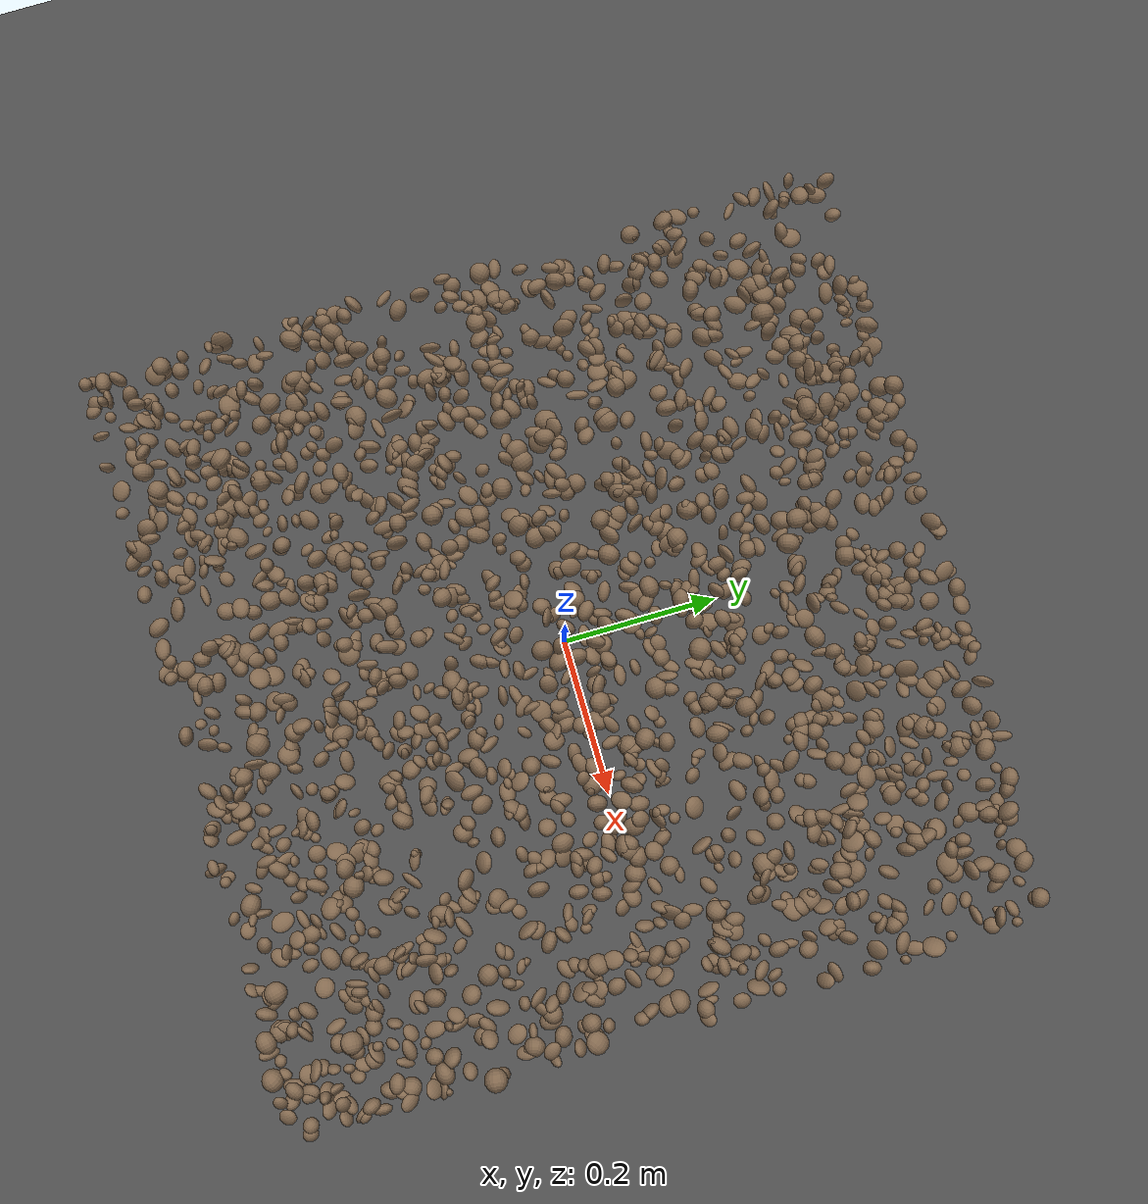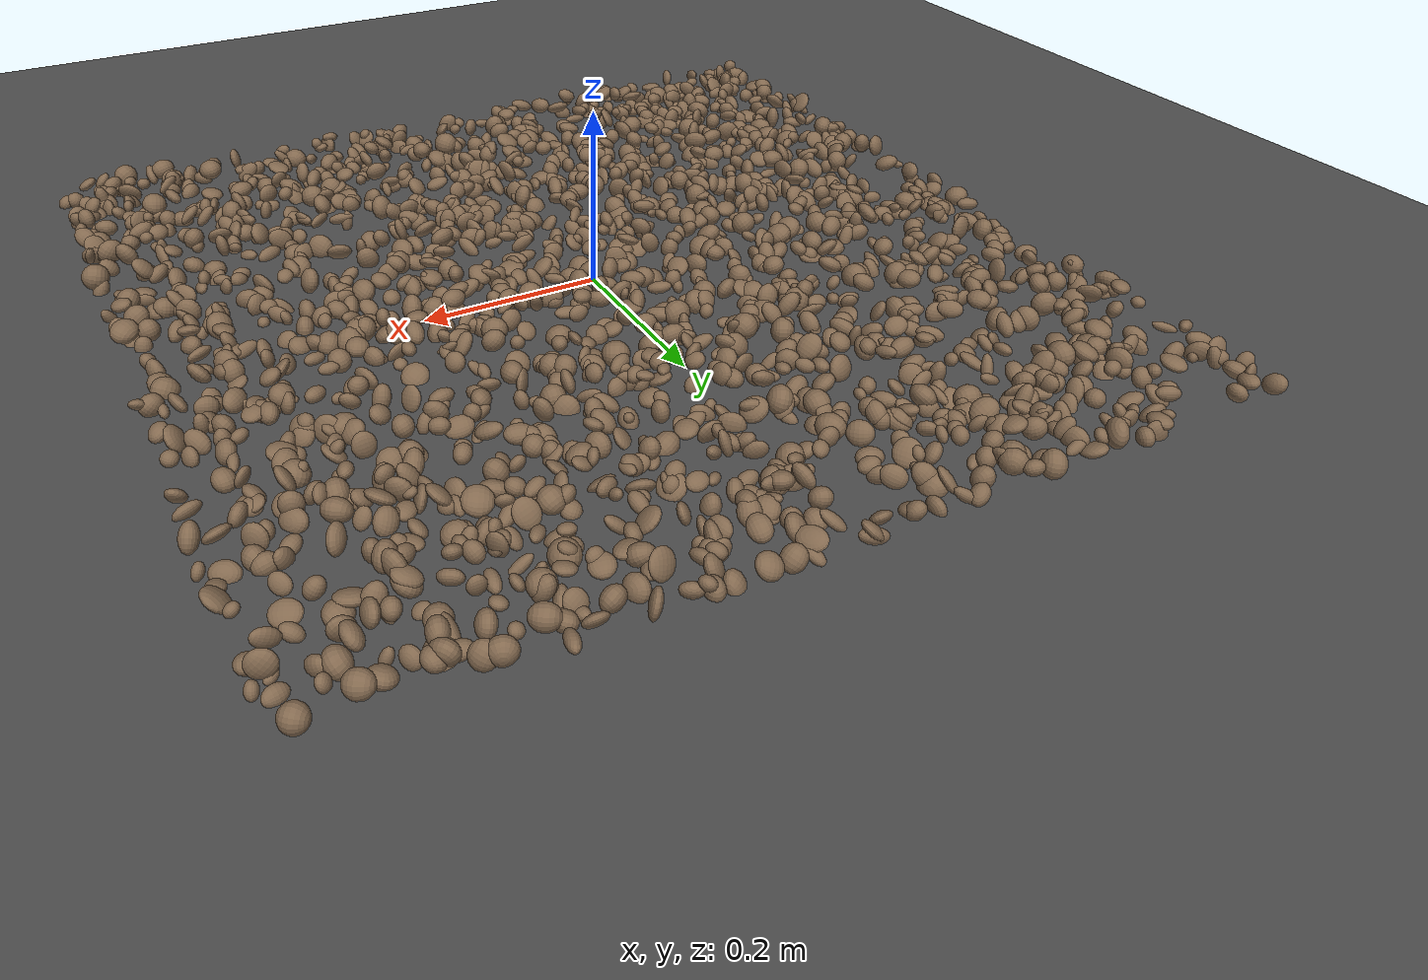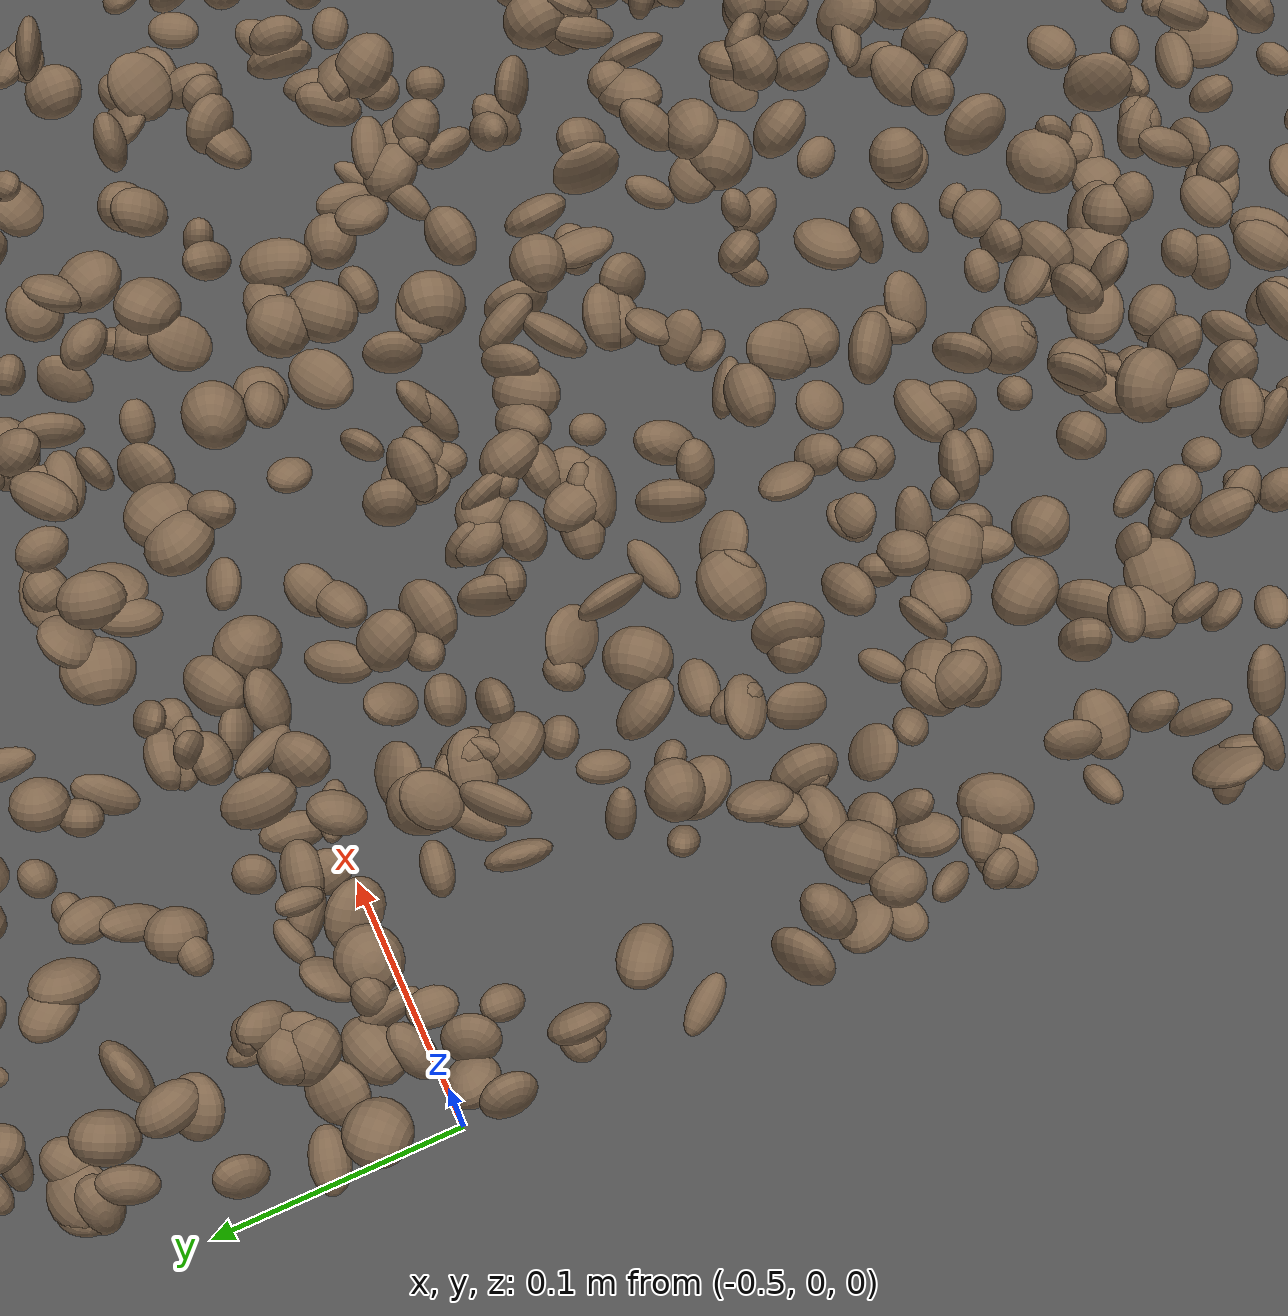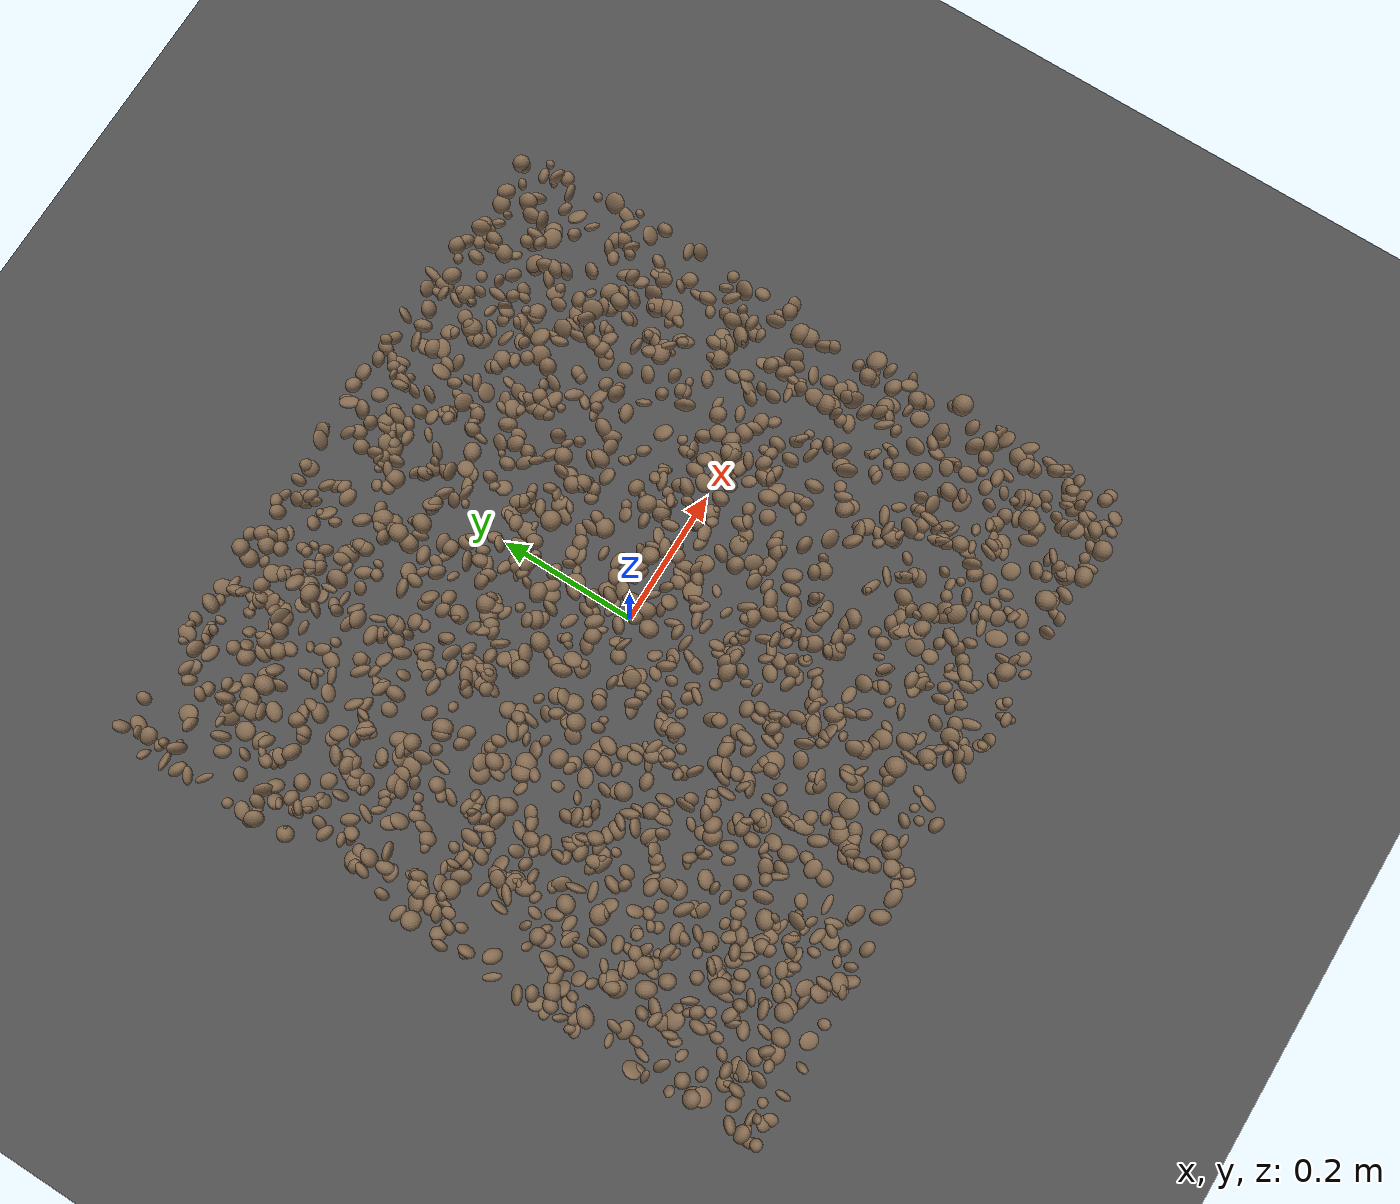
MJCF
<mujoco model="rocky_terrain_scene">
    <compiler angle="radian" inertiafromgeom="true" />
    <option timestep="0.002" gravity="0 0 -9.81" />

    <worldbody>
        <light name="sunlight" pos="5 5 5" dir="-1 -1 -1" diffuse="1 1 1" specular="0.5 0.5 0.5" ambient="0.5 0.5 0.5" />

        <geom name="ground_plane" type="plane" size="50 50 0.1" rgba="0.3 0.3 0.3 1" />

        <body name="rocky_terrain_body">

        <geom name="rock1" type="ellipsoid" size="0.012275856746747874 0.014388924829274185 0.009496332938163094" pos="-0.15173307471763253 -0.2244102209980029 0.01222786632605766" quat="0.3165882243513235 0.19257770018890658 0.05957258912195659 0.43126148633781325" rgba="0.5 0.4 0.3 1" /><geom name="rock2" type="ellipsoid" size="0.01051321489933226 0.010291275275981953 0.01424670423638547" pos="0.1939911262355798 0.25212146569528127 0.011229402627260037" quat="0.3452090838909009 0.3881493912039122 0.1815506117883138 0.08509091311687306" rgba="0.5 0.4 0.3 1" /><geom name="rock3" type="ellipsoid" size="0.00528250755754483 0.013744800464572392 0.007737361160434827" pos="0.16502515362931647 -0.41157061853108257 0.00758056039289624" quat="0.0018003021635224362 0.5590731118395526 0.13581545824300417 0.30331112775392066" rgba="0.5 0.4 0.3 1" /><geom name="rock4" type="ellipsoid" size="0.01307186314459842 0.007305001003025716 0.010099072890358518" pos="0.17423044314870484 0.4475197101666303 0.0019029030607419293" quat="0.2886678413332771 0.40116839848525415 0.226283541457375 0.08388021872409375" rgba="0.5 0.4 0.3 1" /><geom name="rock5" type="ellipsoid" size="0.008427408162791104 0.014771466278170654 0.01390010298999618" pos="0.2745987029116965 -0.06358957732728465 0.009404318954975595" quat="0.049177739211917364 0.47176065684524754 0.41812373596393865 0.060937867978896366" rgba="0.5 0.4 0.3 1" /><geom name="rock6" type="ellipsoid" size="0.012842581919257082 0.010212230433659559 0.009283442839385373" pos="0.3930100860115462 0.10539041286633177 0.008548526977873842" quat="0.34312446594696705 0.1517109994049276 0.17971543471158866 0.3254490999365168" rgba="0.5 0.4 0.3 1" /><geom name="rock7" type="ellipsoid" size="0.009947240009211936 0.005894328697649685 0.0056755419498212625" pos="0.16416094715225316 0.3651380754493557 0.013802057175285345" quat="0.23927166691538881 0.30304205638044185 0.08774157019804647 0.36994470650612277" rgba="0.5 0.4 0.3 1" /><geom name="rock8" type="ellipsoid" size="0.012949893781728998 0.014449630659855946 0.01475226774615095" pos="-0.09777394250720806 -0.3889208344640478 0.004331762848212826" quat="0.03698756146166029 0.3699214116604345 0.22553243162116496 0.3675585952567403" rgba="0.5 0.4 0.3 1" /><geom name="rock9" type="ellipsoid" size="0.007098950727991627 0.0056840062662272366 0.010634745327787836" pos="0.29952775336134063 0.22269663745723778 0.01390262288474082" quat="0.06669374220160577 0.18493734406201529 0.37821972239335844 0.3701491913430205" rgba="0.5 0.4 0.3 1" /><geom name="rock10" type="ellipsoid" size="0.009801638114431696 0.006316340457684112 0.014005356785537996" pos="0.4903610376712578 0.20765196812333153 0.001968756471907954" quat="0.06470452336820565 0.4328232204257643 0.1538735080480253 0.34859874815800473" rgba="0.5 0.4 0.3 1" /><geom name="rock11" type="ellipsoid" size="0.009647786385968297 0.011931677389903356 0.005570906348797331" pos="0.23426777492587425 -0.364616015927839 0.008905655114703115" quat="0.22842600513096023 0.28160583488838853 0.3283000712860654 0.16166808869458577" rgba="0.5 0.4 0.3 1" /><geom name="rock12" type="ellipsoid" size="0.013999455162030223 0.010552734649943501 0.00971127834193301" pos="0.16300501260971567 -0.009290620706959185 0.013489233192205845" quat="0.22490565888632066 0.6473599870922122 0.08460406755789188 0.04313028646357525" rgba="0.5 0.4 0.3 1" /><geom name="rock13" type="ellipsoid" size="0.010879338746324225 0.008593143839673176 0.010810829659913593" pos="-0.13460034464691528 -0.28378828110594256 0.014861422539402994" quat="0.36701009309402394 0.1726853839233853 0.3908336154830901 0.06947090749950066" rgba="0.5 0.4 0.3 1" /><geom name="rock14" type="ellipsoid" size="0.011005569553711597 0.009712061913061617 0.011310240994268356" pos="-0.2193865406411296 -0.3100480864237859 0.011599275273279254" quat="0.35569034168529395 0.1577873739038806 0.0960578434002038 0.3904644410106216" rgba="0.5 0.4 0.3 1" /><geom name="rock15" type="ellipsoid" size="0.00906250941913653 0.011312122706772778 0.013388266722422867" pos="-0.0107772797569472 -0.21563609497071912 0.010954033544500622" quat="0.14060486203459052 0.04804055298554781 0.7224495911076134 0.08890499387224826" rgba="0.5 0.4 0.3 1" /><geom name="rock16" type="ellipsoid" size="0.00997675514928165 0.00739169849063527 0.006361360183934418" pos="0.21698315905068344 -0.49080246317024345 0.010204413858362446" quat="0.037090996639109475 0.2280160334598645 0.2860895325851306 0.44880343731589556" rgba="0.5 0.4 0.3 1" /><geom name="rock17" type="ellipsoid" size="0.010096624252742138 0.010541721433773143 0.014245334017058232" pos="-0.08141471077073414 -0.2029409860071677 0.006644685364367136" quat="0.2775024585236644 0.2502847657172516 0.24667504111964675 0.22553773463943727" rgba="0.5 0.4 0.3 1" /><geom name="rock18" type="ellipsoid" size="0.006407744875165822 0.013454736968053098 0.012673299046819044" pos="-0.10939442637385166 -0.2569064870603547 0.006167763432643245" quat="0.25871634889203 0.1369834290537893 0.29780306626852715 0.30649715578565356" rgba="0.5 0.4 0.3 1" /><geom name="rock19" type="ellipsoid" size="0.014796224422162187 0.005883268323880507 0.009938561836950462" pos="0.3995997575833392 0.08857845941283071 0.009363252624652658" quat="0.44523518163509135 0.2645298666657188 0.04250215147925104 0.24773280021993876" rgba="0.5 0.4 0.3 1" /><geom name="rock20" type="ellipsoid" size="0.011231283797061346 0.008585830421090422 0.006456199898314454" pos="-0.40765773640822445 -0.029423472589305444 0.0015251724993030236" quat="0.06111454718755118 0.01439900770524644 0.4622239137115929 0.4622625313956094" rgba="0.5 0.4 0.3 1" /><geom name="rock21" type="ellipsoid" size="0.013509630364594898 0.014253593283192655 0.013904350816962306" pos="-0.08713871396013662 0.1745803845498829 0.00970953078840427" quat="0.15292365926315238 0.23117074408453625 0.3303669956047308 0.28553860104758055" rgba="0.5 0.4 0.3 1" /><geom name="rock22" type="ellipsoid" size="0.01022821489526274 0.005413222523993034 0.008780662638797475" pos="-0.34821769240897515 -0.22874544223444426 0.005570862054762137" quat="0.31477516760298585 0.5678439899848217 0.0932778851904696 0.024102957221722968" rgba="0.5 0.4 0.3 1" /><geom name="rock23" type="ellipsoid" size="0.014330959950824187 0.008733464610410106 0.010337192194673038" pos="-0.4720356209950989 -0.0855241818354674 0.014433226356693281" quat="0.030226484956642825 0.22741242541290008 0.38118169215420156 0.3611793974762555" rgba="0.5 0.4 0.3 1" /><geom name="rock24" type="ellipsoid" size="0.010425114756296283 0.012354345282883164 0.013959408848919864" pos="-0.09810997564678325 0.16428661506247066 0.0017075554652372915" quat="0.006410973313890709 0.6836141577788062 0.00035631377809427627 0.3096185551292088" rgba="0.5 0.4 0.3 1" /><geom name="rock25" type="ellipsoid" size="0.013978952426752993 0.011956093842355455 0.01410078483038672" pos="0.08856141457264499 0.09528095467559072 0.002455238017724574" quat="0.16522703740849118 0.3240915971909195 0.22325806676163207 0.28742329863895716" rgba="0.5 0.4 0.3 1" /><geom name="rock26" type="ellipsoid" size="0.012597259832078782 0.010993738416615662 0.010368570655112921" pos="0.020849886302122145 0.1654096860185741 0.010889195234306634" quat="0.10897614524073869 0.3496297587493967 0.13828687720894617 0.40310721880091843" rgba="0.5 0.4 0.3 1" /><geom name="rock27" type="ellipsoid" size="0.010936617609403877 0.007373721776017906 0.014702759749070655" pos="0.44568094743134357 -0.22628798400417582 0.014784423766465053" quat="0.448408898549785 0.12083095429789821 0.16366733549926263 0.26709281165305415" rgba="0.5 0.4 0.3 1" /><geom name="rock28" type="ellipsoid" size="0.005357412882363921 0.013374847952252088 0.0076351834286353965" pos="-0.40628237121780075 0.3880865605414717 0.013574871441280731" quat="0.34088630853662805 0.22489035614491312 0.07878388430013086 0.35543945101832797" rgba="0.5 0.4 0.3 1" /><geom name="rock29" type="ellipsoid" size="0.014025619708884142 0.006502931374824681 0.007129781773942769" pos="0.007711871865997977 0.18004004973551702 0.010856328751652327" quat="0.42039753704968685 0.031804526609085976 0.06573956634296448 0.48205836999826274" rgba="0.5 0.4 0.3 1" /><geom name="rock30" type="ellipsoid" size="0.006457813286696341 0.0111612460083861 0.010414121988322563" pos="0.057788697413998835 -0.26026719344635474 0.014248406672171742" quat="0.28420054214137386 0.20323264600117286 0.09625723696034175 0.41630957489711157" rgba="0.5 0.4 0.3 1" /><geom name="rock31" type="ellipsoid" size="0.014487225195884822 0.012544795514796477 0.01415777505587476" pos="-0.19404305542038247 0.3931891893171058 0.0008021781921713649" quat="0.14565767098163063 0.5953507452562937 0.10262968089811114 0.15636190286396437" rgba="0.5 0.4 0.3 1" /><geom name="rock32" type="ellipsoid" size="0.013336498324653688 0.005636895411379978 0.013342523194080535" pos="0.4768036039264456 0.2639685932289103 0.01416055307557278" quat="0.052778328052285696 0.27778682957327727 0.23193999012373825 0.4374948522506988" rgba="0.5 0.4 0.3 1" /><geom name="rock33" type="ellipsoid" size="0.012304993291061082 0.011263039473655945 0.011197682773020388" pos="-0.48557325650254857 0.231163431504805 0.011824096801348171" quat="0.2665550115699915 0.20141915449501757 0.24989757041950636 0.2821282635154845" rgba="0.5 0.4 0.3 1" /><geom name="rock34" type="ellipsoid" size="0.006096649516597909 0.011424124421767587 0.011889723598832082" pos="0.1892292333207839 0.14900371419398495 0.004445504847240927" quat="0.3818543307475176 0.14949929754335137 0.30557685768784904 0.16306951402128197" rgba="0.5 0.4 0.3 1" /><geom name="rock35" type="ellipsoid" size="0.006180310464452547 0.009337114720899958 0.010631285281469258" pos="-0.42807063881874496 0.33761014177269 0.005537711356247588" quat="0.12749204327389166 0.08546326709851888 0.17746722847398722 0.6095774611536022" rgba="0.5 0.4 0.3 1" /><geom name="rock36" type="ellipsoid" size="0.014457758901345295 0.012250447541005415 0.005397371642525323" pos="-0.13112479249830256 -0.23421030108892316 0.003562968072178146" quat="0.3565853055233101 0.15426228742254194 0.25814270286731494 0.231009704186833" rgba="0.5 0.4 0.3 1" /><geom name="rock37" type="ellipsoid" size="0.009547357874774016 0.013887408135031656 0.009084584085131062" pos="0.06905808731924845 0.42024397875189434 0.012034550979757717" quat="0.20264874280443693 0.12587745763084288 0.5607223570497848 0.11075144251493553" rgba="0.5 0.4 0.3 1" /><geom name="rock38" type="ellipsoid" size="0.013628712525198577 0.010072366566038611 0.008036178673885614" pos="-0.4061966549685325 -0.35899235968041376 0.013021881872469903" quat="0.3261105689037189 0.1769327106590237 0.31081106932520314 0.18614565111205422" rgba="0.5 0.4 0.3 1" /><geom name="rock39" type="ellipsoid" size="0.01382462040723956 0.010871646508536973 0.006815004882012179" pos="-0.3750141406723392 -0.05162138297604546 0.0005154047140942358" quat="0.046504109803182675 0.3225823197058202 0.2963067692603857 0.3346068012306115" rgba="0.5 0.4 0.3 1" /><geom name="rock40" type="ellipsoid" size="0.007193340636115681 0.006418240523366736 0.00661277239154956" pos="0.35197688490220114 -0.07446211591348217 0.00021154106743795698" quat="0.1807238104350831 0.3655575416370835 0.30038935819229345 0.15332928973554005" rgba="0.5 0.4 0.3 1" /><geom name="rock41" type="ellipsoid" size="0.0063269278941903585 0.014071156950412604 0.012334572107520647" pos="-0.2571206156016014 0.4905367508880961 0.0016459274196718508" quat="0.3889979076151509 0.02993499895612174 0.4300120096347239 0.15105508379400348" rgba="0.5 0.4 0.3 1" /><geom name="rock42" type="ellipsoid" size="0.008681744915102789 0.012454186525494518 0.008872924009918752" pos="0.18503872209351369 -0.1795115666652305 0.01365664772924068" quat="0.08011052766935374 0.22719051498205342 0.4662543431614711 0.22644461418712186" rgba="0.5 0.4 0.3 1" /><geom name="rock43" type="ellipsoid" size="0.012031197942781076 0.00956534012003254 0.008218018865558917" pos="-0.4816008755580684 -0.3983556962286129 0.00040609708269094156" quat="0.1718734930407658 0.1908404036878893 0.5585361973244245 0.07874990594692038" rgba="0.5 0.4 0.3 1" /><geom name="rock44" type="ellipsoid" size="0.005301943771971469 0.007962175733946527 0.013361655453526404" pos="-0.2973260501357211 0.31268911747761885 0.009317186628061296" quat="0.19626898009317653 0.15439511067731496 0.15747672767757043 0.4918591815519381" rgba="0.5 0.4 0.3 1" /><geom name="rock45" type="ellipsoid" size="0.007734371979101 0.012366663111365452 0.007923196279942184" pos="-0.14818537671690235 -0.043226930071757486 0.01073465496317415" quat="0.3893512162276452 0.17345355538758833 0.26874205523582034 0.16845317314894623" rgba="0.5 0.4 0.3 1" /><geom name="rock46" type="ellipsoid" size="0.007697541350846047 0.012256754874239502 0.011105062673430937" pos="-0.3444567280454701 0.3889389769732886 0.0035309129531256537" quat="0.264104754748063 0.07627768520912362 0.4045014058237519 0.25511615421906153" rgba="0.5 0.4 0.3 1" /><geom name="rock47" type="ellipsoid" size="0.013236537072574356 0.009648554862363424 0.008110819032232392" pos="-0.15415515841684457 0.19477903432978128 0.006646388347660783" quat="0.3502993667850224 0.05452031606106337 0.3225906886765521 0.27258962847736223" rgba="0.5 0.4 0.3 1" /><geom name="rock48" type="ellipsoid" size="0.010742889757800217 0.014674087295566043 0.008768300764206254" pos="-0.028248917547916252 -0.41248882678881327 0.004140662043392961" quat="0.3233019640981158 0.201702943408739 0.3990944023708818 0.07590069012226344" rgba="0.5 0.4 0.3 1" /><geom name="rock49" type="ellipsoid" size="0.0061530768206455025 0.008950998297260624 0.014772751449053944" pos="-0.3965285772394268 -0.05865701131596901 0.014145343075436757" quat="0.09463176514861961 0.21509735601976324 0.3272792363409907 0.36299164249062643" rgba="0.5 0.4 0.3 1" /><geom name="rock50" type="ellipsoid" size="0.008079482780519405 0.008241118838703569 0.0055714485817454865" pos="0.30207788436640803 0.43458040869933845 0.0072142477450028684" quat="0.02380914100255255 0.5984049577218722 0.2621888409092042 0.11559706036637096" rgba="0.5 0.4 0.3 1" /><geom name="rock51" type="ellipsoid" size="0.009376541808868953 0.012015132389180413 0.006689570925529715" pos="0.3975132440917257 -0.030966575395254714 0.013579937187096823" quat="0.2095640554518669 0.2986190296899564 0.32828943229616986 0.16352748256200697" rgba="0.5 0.4 0.3 1" /><geom name="rock52" type="ellipsoid" size="0.007622847382327702 0.008209692986918897 0.007673935825928351" pos="-0.1561972245994412 0.4198004499425174 0.012611543884157668" quat="0.2875806621978666 0.23149081070487829 0.1681191984694428 0.31280932862781236" rgba="0.5 0.4 0.3 1" /><geom name="rock53" type="ellipsoid" size="0.006883456877972526 0.00781697933348485 0.010460315458704352" pos="-0.05862930576090131 -0.22494919172582817 0.005759403137500419" quat="0.3310534052106284 0.10976926351832199 0.11842716127421973 0.44075016999682987" rgba="0.5 0.4 0.3 1" /><geom name="rock54" type="ellipsoid" size="0.0071670125647107525 0.01331157253182503 0.013804377012136163" pos="0.3250388184964478 0.27518704302549135 0.013446564587432949" quat="0.5783937352607809 0.07001954023610138 0.09624208059407609 0.25534464390904166" rgba="0.5 0.4 0.3 1" /><geom name="rock55" type="ellipsoid" size="0.014786910127693061 0.009006893596226636 0.005191278002727593" pos="0.3363989995899579 -0.36647132046403685 0.009078959374974264" quat="0.28585551195457626 0.29101225138751147 0.1625821399887202 0.2605500966691921" rgba="0.5 0.4 0.3 1" /><geom name="rock56" type="ellipsoid" size="0.012106874412895773 0.005296675973519145 0.010996622740269314" pos="0.2642654525901682 -0.4229317518335214 0.008103242226525979" quat="0.3097924060994896 0.37894913566613425 0.05745613175113973 0.2538023264832365" rgba="0.5 0.4 0.3 1" /><geom name="rock57" type="ellipsoid" size="0.005660855442487469 0.009339096803804483 0.012213248577337962" pos="-0.18261112340055885 -0.4592674135932625 0.005100575016645861" quat="0.3265009932890724 0.23294425725521428 0.12118457581915412 0.3193701736365593" rgba="0.5 0.4 0.3 1" /><geom name="rock58" type="ellipsoid" size="0.010721071285933814 0.0125180042452168 0.01271054459944342" pos="0.48802180586214383 0.039897999990278654 0.006786295748944098" quat="0.19274312372516475 0.3164466905998257 0.41676854978510597 0.07404163588990358" rgba="0.5 0.4 0.3 1" /><geom name="rock59" type="ellipsoid" size="0.014306907446165473 0.007031826295757386 0.010284920021520899" pos="-0.36767956311968863 0.45998083850869487 0.008382177663399682" quat="0.2814111105577696 0.04939493305913646 0.4025461481988965 0.2666478081841974" rgba="0.5 0.4 0.3 1" /><geom name="rock60" type="ellipsoid" size="0.0057930462540986384 0.006428092478387421 0.012803609006750252" pos="-0.41754284761072613 -0.10056089321069772 0.0031973346844029276" quat="0.42809182073861346 0.17188896600830728 0.06241774806351599 0.33760146518956335" rgba="0.5 0.4 0.3 1" /><geom name="rock61" type="ellipsoid" size="0.005416394581564031 0.013953347899921208 0.011656737827856901" pos="0.15416447925499588 0.0753029390462644 0.002689091144785504" quat="0.16337875679042693 0.12188038891445764 0.33795455940009655 0.37678629489501897" rgba="0.5 0.4 0.3 1" /><geom name="rock62" type="ellipsoid" size="0.01442027015466656 0.009417123243833566 0.010102376898742695" pos="0.19117177426328424 -0.06010278169831029 0.0094634590636079" quat="0.16962341230374894 0.3848233119995501 0.4120298153704636 0.03352346032623726" rgba="0.5 0.4 0.3 1" /><geom name="rock63" type="ellipsoid" size="0.005117079340088684 0.014365283652588389 0.01235686953578215" pos="-0.03533165826036111 -0.012397503422937772 0.01305918355369326" quat="0.22475639912354947 0.3702023163808825 0.21347533303092978 0.1915659514646382" rgba="0.5 0.4 0.3 1" /><geom name="rock64" type="ellipsoid" size="0.0078121527974765355 0.01468280146462422 0.005051379559230455" pos="0.4197840820925638 -0.2577743298967553 0.009984247532965554" quat="0.06388250993906446 0.3018028202452119 0.18953912158329414 0.44477554823242943" rgba="0.5 0.4 0.3 1" /><geom name="rock65" type="ellipsoid" size="0.011991875695100213 0.010395777821859423 0.010397379386578816" pos="0.023372553836374155 0.4571244693803853 0.0002868469873379392" quat="0.3142370189800964 0.1794674139800617 0.30011940756675415 0.20617615947308784" rgba="0.5 0.4 0.3 1" /><geom name="rock66" type="ellipsoid" size="0.005910992697468265 0.010626947304220554 0.005506235349287684" pos="-0.19065293722099919 -0.21577874775728156 0.0037506799899146293" quat="0.04546920936354862 0.2357029942920113 0.6164761667232572 0.10235162962118288" rgba="0.5 0.4 0.3 1" /><geom name="rock67" type="ellipsoid" size="0.006058018640962798 0.007291897644320167 0.014794862124905842" pos="0.20979335115379694 -0.2556085935244792 0.011379919452419505" quat="0.35068382673885423 0.2195842981389336 0.3772105625645842 0.052521312557628014" rgba="0.5 0.4 0.3 1" /><geom name="rock68" type="ellipsoid" size="0.008743147528480233 0.009720251671182812 0.009936981656168808" pos="0.37851890945333955 0.4073997737841123 0.011231954585394478" quat="0.062315537263514076 0.01958185467308879 0.48295324241708765 0.43514936564630946" rgba="0.5 0.4 0.3 1" /><geom name="rock69" type="ellipsoid" size="0.005614243048263615 0.00941096584619108 0.011893988229169289" pos="0.1230391958002931 0.32811893196269737 0.006536820645297203" quat="0.16390542100289968 0.44170868001918473 0.12384068694441412 0.2705452120335015" rgba="0.5 0.4 0.3 1" /><geom name="rock70" type="ellipsoid" size="0.012804706110598828 0.006731844397507101 0.010766841573726961" pos="0.4347798612520013 0.2154085707705794 0.005152857534849015" quat="0.3051225681811666 0.0689613733478304 0.2190474873745446 0.4068685710964584" rgba="0.5 0.4 0.3 1" /><geom name="rock71" type="ellipsoid" size="0.012500824072755462 0.011704912060220871 0.011921471405596965" pos="-0.28995457028255756 0.3775090137334647 0.006218924884148389" quat="0.3026090749997972 0.17719838659901974 0.35118814476471144 0.16900439363647154" rgba="0.5 0.4 0.3 1" /><geom name="rock72" type="ellipsoid" size="0.009853226495111014 0.011233831984001595 0.012281052161691433" pos="0.4487982785440404 0.30474178231510884 0.0023115742179369097" quat="0.21576889334093163 0.29521821741654064 0.2849358982949867 0.204076990947541" rgba="0.5 0.4 0.3 1" /><geom name="rock73" type="ellipsoid" size="0.012149295177902614 0.007887197127475931 0.009530489338754616" pos="-0.12482455986257013 0.22081608968758704 0.00482995879180448" quat="0.21359468970208256 0.029214537389089856 0.4431120414282942 0.3140787314805334" rgba="0.5 0.4 0.3 1" /><geom name="rock74" type="ellipsoid" size="0.008580232787199417 0.005315386664424458 0.014923508226327913" pos="0.37364053605835035 0.08387105453426291 0.0036003220369314496" quat="0.2994335712266041 0.33777583359152596 0.18669053794304907 0.17610005723882097" rgba="0.5 0.4 0.3 1" /><geom name="rock75" type="ellipsoid" size="0.009060240428649599 0.00879886020673503 0.010366845760462944" pos="0.10025916465442708 -0.33782608689191707 0.011363752553143062" quat="0.033278779650847044 0.15210437499677362 0.3298639748681905 0.4847528704841888" rgba="0.5 0.4 0.3 1" /><geom name="rock76" type="ellipsoid" size="0.006554756762847209 0.007700184725303159 0.009107297877498973" pos="-0.032190958108097356 -0.25466114880657176 0.003113991659972315" quat="0.19953629937926182 0.2879343126863394 0.27201574832296027 0.2405136396114385" rgba="0.5 0.4 0.3 1" /><geom name="rock77" type="ellipsoid" size="0.010200117947993628 0.01013219482128722 0.005688434062331217" pos="-0.30176928920101453 -0.2377747336431768 0.00890899027438845" quat="0.0022361446882717085 0.2258508413413544 0.6236149094201145 0.14829810455025935" rgba="0.5 0.4 0.3 1" /><geom name="rock78" type="ellipsoid" size="0.010566859980373246 0.009967170130594505 0.006300246952850958" pos="0.4720387547543953 0.1346257164850776 0.00310493005125701" quat="0.34245011740810055 0.07292742523459318 0.3198025228165493 0.26481993454075686" rgba="0.5 0.4 0.3 1" /><geom name="rock79" type="ellipsoid" size="0.007330649247617485 0.01057197058202532 0.01094781925494676" pos="-0.25321191412713306 -0.09094540292725228 0.003128639946397757" quat="0.10455774051600253 0.3282307579196373 0.4726330576546209 0.09457844390973928" rgba="0.5 0.4 0.3 1" /><geom name="rock80" type="ellipsoid" size="0.010657200237994328 0.007544773190503652 0.012037625498945412" pos="0.3753811243948092 0.043169269751827555 0.007290724821218302" quat="0.24364246736847478 0.40592822109174104 0.25906376239720846 0.09136554914257573" rgba="0.5 0.4 0.3 1" /><geom name="rock81" type="ellipsoid" size="0.006622082560651265 0.011526094003724143 0.009400389147062751" pos="0.32106556934177355 0.12707430789015406 0.012918328909618929" quat="0.2893272035578555 0.39809061692590714 0.3045050628942735 0.008077116621963929" rgba="0.5 0.4 0.3 1" /><geom name="rock82" type="ellipsoid" size="0.005265633305607312 0.012715518710179272 0.007498493700233395" pos="-0.17422046146083947 -0.32092411451059233 0.0008180872075285034" quat="0.019677293202272197 0.0593669019401021 0.292439761850404 0.6285160430072217" rgba="0.5 0.4 0.3 1" /><geom name="rock83" type="ellipsoid" size="0.01173385466133966 0.01350288091648795 0.006557801415942533" pos="-0.30613066784100873 -0.29694634096689043 0.012696046195139438" quat="0.3182573283064741 0.3806373206228645 0.07065938865563966 0.2304459624150218" rgba="0.5 0.4 0.3 1" /><geom name="rock84" type="ellipsoid" size="0.008686240084296554 0.013521642367898937 0.0061044967485828225" pos="-0.18750571910217528 0.03890223418203209 0.00711236462632629" quat="0.3894166179371257 0.12772639145263215 0.4506423343017824 0.03221465630845978" rgba="0.5 0.4 0.3 1" /><geom name="rock85" type="ellipsoid" size="0.008503693425080274 0.009638868954227577 0.008528219960881597" pos="-0.32764472833879144 -0.24902857320351368 0.0011831905094672845" quat="0.152308003038668 0.23524535850032602 0.27350893995006503 0.3389376985109408" rgba="0.5 0.4 0.3 1" /><geom name="rock86" type="ellipsoid" size="0.006850830404263268 0.006325964147475994 0.010402907268027943" pos="-0.3732899050757966 0.1495525478273172 0.007054545906838431" quat="0.3760422153385474 0.28143539516746136 0.07125248532481838 0.27126990416917285" rgba="0.5 0.4 0.3 1" /><geom name="rock87" type="ellipsoid" size="0.007829061814414336 0.011059697186115134 0.010059351198233469" pos="-0.35038775876118367 -0.05789958315454147 0.007950324438906715" quat="0.2891715247098606 0.276427587045067 0.2655482197045212 0.1688526685405513" rgba="0.5 0.4 0.3 1" /><geom name="rock88" type="ellipsoid" size="0.006734402233676626 0.012294478359814481 0.011013110209821247" pos="-0.4590296894227749 -0.18506655541911854 0.005754856678890841" quat="0.3109051534165599 0.3283261029487125 0.03718812699359864 0.32358061664112897" rgba="0.5 0.4 0.3 1" /><geom name="rock89" type="ellipsoid" size="0.008435311818185706 0.011972526573851273 0.007392334530545545" pos="-0.2146551353340519 -0.2504351678144626 0.00013540252408990482" quat="0.03778543606658204 0.35494636779549554 0.2067632748652037 0.40050492127271875" rgba="0.5 0.4 0.3 1" /><geom name="rock90" type="ellipsoid" size="0.008894444966250524 0.00803034962313803 0.01308313747226713" pos="-0.3148501700008156 -0.42430415391353615 0.014120352091816587" quat="0.27708862941600737 0.06843875745570346 0.3279757818264963 0.3264968313017929" rgba="0.5 0.4 0.3 1" /><geom name="rock91" type="ellipsoid" size="0.00912435775712725 0.012012193930105367 0.01265059076938834" pos="-0.019960979422784075 -0.1986495660085541 0.0003378459440578596" quat="0.0299600375728884 0.3770633893032136 0.328609418015966 0.264367155107932" rgba="0.5 0.4 0.3 1" /><geom name="rock92" type="ellipsoid" size="0.006431334168583943 0.005575050745935014 0.0055463187348567975" pos="0.06833923290972566 -0.05051854884422169 0.000901895523497691" quat="0.3574697513724417 0.3020757251840244 0.30974127098941456 0.030713252454119228" rgba="0.5 0.4 0.3 1" /><geom name="rock93" type="ellipsoid" size="0.007070111484783778 0.012910379297687631 0.008602941309983004" pos="0.21383063109315592 -0.4065824117832397 0.012028702843177266" quat="0.32107460869268617 0.4863203032566074 0.04017331996676463 0.15243176808394185" rgba="0.5 0.4 0.3 1" /><geom name="rock94" type="ellipsoid" size="0.009584206990322445 0.012072100634102665 0.00913949098537933" pos="0.25837662097231473 -0.29726261563792455 0.0010023242030246043" quat="0.3262186326108916 0.3122290838863874 0.08303351478388885 0.27851876871883213" rgba="0.5 0.4 0.3 1" /><geom name="rock95" type="ellipsoid" size="0.005174185209769655 0.010914813600352562 0.010407017740849452" pos="0.11807194452495806 0.08059605164774397 0.009329623087828677" quat="0.18580268636292013 0.30847709985398153 0.06609526521971905 0.4396249485633794" rgba="0.5 0.4 0.3 1" /><geom name="rock96" type="ellipsoid" size="0.006498804249123807 0.005198379711773646 0.013969172358522578" pos="-0.07717077484408497 0.23484085700679147 0.0003882152464397326" quat="0.17470750117239148 0.291305832689465 0.4517040694492805 0.08228259668886309" rgba="0.5 0.4 0.3 1" /><geom name="rock97" type="ellipsoid" size="0.007182333422447874 0.006107468426428421 0.00886760498511962" pos="-0.2765997568608751 -0.32046596072168076 0.007746534666927776" quat="0.24217758184300217 0.23912507417367046 0.1541708289997126 0.3645265149836148" rgba="0.5 0.4 0.3 1" /><geom name="rock98" type="ellipsoid" size="0.008007931694874135 0.007158709387728518 0.008160600901135224" pos="0.40082369056814005 -0.4826595434965236 0.0033839023407458034" quat="0.21263224793781604 0.4300543987567746 0.09838142382517764 0.25893192948023164" rgba="0.5 0.4 0.3 1" /><geom name="rock99" type="ellipsoid" size="0.009016514281477536 0.012818813064882192 0.010974895514882631" pos="-0.262720578775825 0.10031534637809625 0.003952876770405074" quat="0.36751609728296225 0.2604295162620974 0.19604072867885267 0.1760136577760876" rgba="0.5 0.4 0.3 1" /><geom name="rock100" type="ellipsoid" size="0.007760619418431057 0.007182624654728366 0.014627218528466362" pos="0.4563307283599066 -0.4388312929815459 0.014428913937502303" quat="0.16074854218459506 0.06331877541944594 0.032079143782956274 0.7438535386130027" rgba="0.5 0.4 0.3 1" /><geom name="rock101" type="ellipsoid" size="0.009220795797272476 0.01248074883364759 0.01223996862233331" pos="-0.08592385375213307 0.2541117919982153 0.013355759198790753" quat="0.5234294428354738 0.1268487631483256 0.10788631467382066 0.2418354793423799" rgba="0.5 0.4 0.3 1" /><geom name="rock102" type="ellipsoid" size="0.010989487960518733 0.012937457465773947 0.012080010006791032" pos="-0.3797502334804067 -0.295900420373296 0.0015582805309524443" quat="0.33671006024502853 0.4240180261106479 0.09575247913702294 0.14351943450730062" rgba="0.5 0.4 0.3 1" /><geom name="rock103" type="ellipsoid" size="0.009229879787788553 0.007382387990593515 0.011680950241955493" pos="0.34627065820362124 0.4647315512214657 0.004570974840621269" quat="0.260094314028479 0.28329167856632415 0.25755506594912586 0.199058941456071" rgba="0.5 0.4 0.3 1" /><geom name="rock104" type="ellipsoid" size="0.01133286235703454 0.012310362567893168 0.013429391350844776" pos="-0.023514099579034053 -0.3966418842952316 0.006669067689450501" quat="0.5601429596796387 0.031742057673564035 0.19467325054646278 0.21344173210033449" rgba="0.5 0.4 0.3 1" /><geom name="rock105" type="ellipsoid" size="0.013463665497793206 0.00967696076347229 0.014548948728480272" pos="0.35653909279893115 0.3799215354194846 0.004969299382861357" quat="0.32801140807033313 0.13493169029671287 0.18362749753849872 0.35342940409445534" rgba="0.5 0.4 0.3 1" /><geom name="rock106" type="ellipsoid" size="0.013330851414048585 0.012676315900889645 0.011141800187316642" pos="-0.16666050643814645 0.4831729340219677 0.014741177952908212" quat="0.0773699223940126 0.24283315541475836 0.3139149885830409 0.3658819336081881" rgba="0.5 0.4 0.3 1" /><geom name="rock107" type="ellipsoid" size="0.013157461240086831 0.007587066379399989 0.010282730697031534" pos="-0.40034415627534503 0.12225085737848396 0.01110511676402835" quat="0.082871461084477 0.2428066690521337 0.360213159120016 0.3141087107433733" rgba="0.5 0.4 0.3 1" /><geom name="rock108" type="ellipsoid" size="0.011287738889492496 0.006331967279787824 0.005015417676281236" pos="0.10676733708622443 0.3284149303265089 0.0032523012634559615" quat="0.5540421923942122 0.11643083630746717 0.03782283539204969 0.29170413590627103" rgba="0.5 0.4 0.3 1" /><geom name="rock109" type="ellipsoid" size="0.010919193630464962 0.009463290524768683 0.012440309217778413" pos="-0.32876883924822065 -0.33627069426230516 0.00907434815151192" quat="0.1909706402929132 0.20679820480954048 0.27508009262751726 0.327151062270029" rgba="0.5 0.4 0.3 1" /><geom name="rock110" type="ellipsoid" size="0.005697021339074768 0.014563358644310371 0.0116480410462752" pos="0.03654363492869195 0.2141102872520324 0.004329588162651462" quat="0.3644043821970161 0.010744073409833486 0.44171452997133664 0.18313701442181374" rgba="0.5 0.4 0.3 1" /><geom name="rock111" type="ellipsoid" size="0.00820770859409183 0.006094787140198885 0.01424604441826349" pos="-0.00022273186114718513 0.026687325337956147 0.0090303165071243" quat="0.3568873786857702 0.20375356858098673 0.2655680034390506 0.1737910492941925" rgba="0.5 0.4 0.3 1" /><geom name="rock112" type="ellipsoid" size="0.0110260966327675 0.009164197917040966 0.005383111466636444" pos="-0.4693616271183627 -0.22753069308346408 0.004262565768752797" quat="0.446169736999196 0.3099864501687483 0.04358591214535319 0.20025790068670252" rgba="0.5 0.4 0.3 1" /><geom name="rock113" type="ellipsoid" size="0.011502125972876084 0.00586123365844854 0.009658895508002169" pos="0.32567676512210664 0.3209617643836522 0.005057072850588539" quat="0.3427601995053235 0.11865631850693961 0.1745566245429869 0.36402685744475005" rgba="0.5 0.4 0.3 1" /><geom name="rock114" type="ellipsoid" size="0.012365409283142843 0.013198372653022351 0.013793874531555884" pos="0.30452078567979257 0.0032599643846955573 0.0028774616733950047" quat="0.03587040711605991 0.19494060748923112 0.44706124311089884 0.32212774228381014" rgba="0.5 0.4 0.3 1" /><geom name="rock115" type="ellipsoid" size="0.007531570251183282 0.00581903934195851 0.009949791190576252" pos="-0.03721922454398341 -0.009699529174702737 0.009704327547337173" quat="0.26286412444048124 0.3170329433945579 0.20196209526277853 0.21814083690218242" rgba="0.5 0.4 0.3 1" /><geom name="rock116" type="ellipsoid" size="0.005836858747574828 0.00780005909374559 0.008750049213931422" pos="-0.48269400876917634 -0.477775858059028 0.006523029326226215" quat="0.1496565173765028 0.2872983847645742 0.05889244050931593 0.504152657349607" rgba="0.5 0.4 0.3 1" /><geom name="rock117" type="ellipsoid" size="0.011250379376717367 0.008936796655621825 0.006797976234353151" pos="-0.023130301506976925 -0.21863185855597345 0.0010732305821504716" quat="0.31505366877382723 0.17623853182307433 0.2172525599154141 0.29145523948768426" rgba="0.5 0.4 0.3 1" /><geom name="rock118" type="ellipsoid" size="0.006208482185985841 0.012854131497895115 0.008138954369823023" pos="0.3085005083502206 -0.27048849655792007 0.00342923849790325" quat="0.11363409681005923 0.42933569407443783 0.021529814343040594 0.43550039477246244" rgba="0.5 0.4 0.3 1" /><geom name="rock119" type="ellipsoid" size="0.008934952101131424 0.014433220466078936 0.012363423939442716" pos="0.4538483481406421 -0.4372356582248613 0.006221522780982561" quat="0.0593841480321949 0.44079044375584525 0.3048070466321011 0.19501836157985883" rgba="0.5 0.4 0.3 1" /><geom name="rock120" type="ellipsoid" size="0.013540317759493124 0.005259735574952037 0.008064158387781122" pos="0.1168199430564002 0.02631166587611322 0.012349675405301389" quat="0.33320036052148905 0.4781317554162065 0.18729307856603397 0.0013748054962704668" rgba="0.5 0.4 0.3 1" /><geom name="rock121" type="ellipsoid" size="0.009193332108983418 0.013871051601081357 0.010619486833485695" pos="0.09227764123185955 0.4016298708754551 0.0003831637210486793" quat="0.09984535578269316 0.030410600183933767 0.4810655892337534 0.38867845479961965" rgba="0.5 0.4 0.3 1" /><geom name="rock122" type="ellipsoid" size="0.01086558026603392 0.01258336692411546 0.011476578917789151" pos="0.05575556875919596 0.20691163647689992 0.002336569375548918" quat="0.4436597563594238 0.33087908728491333 0.05893042244463818 0.16653073391102463" rgba="0.5 0.4 0.3 1" /><geom name="rock123" type="ellipsoid" size="0.009032069250379601 0.010866744885874333 0.007154189535011384" pos="0.2512656943588538 -0.11194263567427198 0.0036808517238004273" quat="0.3181707280527257 0.11956473060103515 0.038438414491528475 0.5238261268547106" rgba="0.5 0.4 0.3 1" /><geom name="rock124" type="ellipsoid" size="0.010947098269658614 0.005415795355674964 0.011545812889539203" pos="0.4066831035653544 0.10171870782476744 0.010080174736802896" quat="0.14258721209591074 0.1724249233676423 0.3869447092753643 0.29804315526108277" rgba="0.5 0.4 0.3 1" /><geom name="rock125" type="ellipsoid" size="0.012548088699686263 0.00955214970439915 0.011495653225222334" pos="-0.14105163305609725 -0.12453169376549922 0.007444119072309651" quat="0.1508790235425144 0.21744895231495412 0.4450992213025964 0.18657280283993508" rgba="0.5 0.4 0.3 1" /><geom name="rock126" type="ellipsoid" size="0.013720245887413829 0.007217932811252255 0.006809472451561788" pos="0.29409472528021685 0.40366200786432604 0.0011631129969978471" quat="0.34167492269526434 0.17882178934840975 0.18211279161693725 0.2973904963393887" rgba="0.5 0.4 0.3 1" /><geom name="rock127" type="ellipsoid" size="0.009845463915022166 0.010800702681671713 0.007389422096168898" pos="0.010972036747059488 0.23758943152927758 0.0017000015455871658" quat="0.09404193029119738 0.017848358753813725 0.3724004219870046 0.5157092889679843" rgba="0.5 0.4 0.3 1" /><geom name="rock128" type="ellipsoid" size="0.014508247888632756 0.006260064330100203 0.0056842092013380825" pos="-0.3409685506692046 0.012981600127283 0.009360412363175611" quat="0.19565685157066423 0.20153351095802646 0.2228147371719926 0.3799949002993167" rgba="0.5 0.4 0.3 1" /><geom name="rock129" type="ellipsoid" size="0.009597645488170797 0.01260595285798714 0.014406011396446546" pos="-0.19569573185135725 0.31109682596762533 0.007523196266695144" quat="0.2641403856406324 0.2045467054967897 0.36551711258259406 0.1657957962799838" rgba="0.5 0.4 0.3 1" /><geom name="rock130" type="ellipsoid" size="0.013593107212227572 0.008598712552405609 0.01329952036479588" pos="-0.4697772402340531 0.1354832900687768 0.00039724676471484144" quat="0.1637354760045958 0.3335804418366738 0.289345072067251 0.21333901009147932" rgba="0.5 0.4 0.3 1" /><geom name="rock131" type="ellipsoid" size="0.012431391829841664 0.006307518565049591 0.013927569049904675" pos="-0.42250923346557223 0.4298129873437869 0.012936363866725399" quat="0.4875048261318367 0.4041236278743294 0.04386144453749312 0.06451010145634072" rgba="0.5 0.4 0.3 1" /><geom name="rock132" type="ellipsoid" size="0.010084115684742325 0.013599095873728671 0.008669324945330601" pos="-0.1976369062408483 0.4312634410158397 0.009176796546788024" quat="0.35199732227907315 0.18936173739045825 0.09096943165342841 0.3676715086770402" rgba="0.5 0.4 0.3 1" /><geom name="rock133" type="ellipsoid" size="0.01387205016428521 0.008499344996668181 0.013834983503300775" pos="-0.31632545855283944 -0.06547804674918778 0.008015063161629338" quat="0.4312689636507763 0.05927376338176442 0.36496847418692296 0.14448879878053633" rgba="0.5 0.4 0.3 1" /><geom name="rock134" type="ellipsoid" size="0.007881937957189496 0.014701858281855856 0.009387955409581875" pos="-0.15136913484552073 0.16010169844234268 0.011678934464814338" quat="0.39811048909813873 0.22433425117283645 0.09022462723153452 0.2873306324974903" rgba="0.5 0.4 0.3 1" /><geom name="rock135" type="ellipsoid" size="0.010975771564370353 0.012994255879326806 0.008394531291028597" pos="-0.4576042406500077 0.2668078088555139 0.009160230444782334" quat="0.21155458027836657 0.2111610059268331 0.1316051655963944 0.44567924819840593" rgba="0.5 0.4 0.3 1" /><geom name="rock136" type="ellipsoid" size="0.006090465074753954 0.009146841103647716 0.008618281519253932" pos="-0.3082389155742772 -0.31784228800557524 0.013448994370140573" quat="0.11934938633428775 0.11205152338227996 0.23636292520568458 0.5322361650777477" rgba="0.5 0.4 0.3 1" /><geom name="rock137" type="ellipsoid" size="0.01142284070958082 0.009986122746001552 0.010683302802365326" pos="-0.1310996696647515 -0.13482817604015718 0.005324497804327499" quat="0.2980070986667247 0.33642462546629603 0.07421043287083652 0.29135784299614276" rgba="0.5 0.4 0.3 1" /><geom name="rock138" type="ellipsoid" size="0.005175753966455539 0.005431259300163128 0.01051623514637708" pos="0.07074468411184887 0.37257403622204 0.0026755464794241545" quat="0.011051142935427848 0.2691156533628525 0.2501333936920065 0.46969981000971317" rgba="0.5 0.4 0.3 1" /><geom name="rock139" type="ellipsoid" size="0.00976106144360734 0.006803472154882679 0.007031106780567781" pos="-0.4645196575013698 -0.031189381860763477 0.0030802453051260426" quat="0.18338409844192935 0.31842500873332347 0.13878247012428213 0.359408422700465" rgba="0.5 0.4 0.3 1" /><geom name="rock140" type="ellipsoid" size="0.008963519733070859 0.008977969255758965 0.009807512507479157" pos="0.21978610943922028 0.3963765070901961 0.0013227837974155504" quat="0.0971620146098974 0.13460626946152207 0.3292976165405257 0.4389340993880549" rgba="0.5 0.4 0.3 1" /><geom name="rock141" type="ellipsoid" size="0.013627994667943729 0.007228591217721741 0.013709679704289105" pos="0.435288838406951 0.0014126438821683296 0.0046753774673376075" quat="0.33255638991513203 0.21057624876699418 0.04453415699015703 0.4123332043277168" rgba="0.5 0.4 0.3 1" /><geom name="rock142" type="ellipsoid" size="0.007082942491145933 0.007318468163833386 0.00685051810502663" pos="0.17064695772664107 -0.4888246416960942 0.012850303317375321" quat="0.13018157356823168 0.3372852352979426 0.34227473594684643 0.19025845518697923" rgba="0.5 0.4 0.3 1" /><geom name="rock143" type="ellipsoid" size="0.012728549527740211 0.009906149258438923 0.012719094379759027" pos="0.39002732377869 -0.2341327259724092 0.0007586758624180412" quat="0.23540259519288603 0.10641386182928642 0.20977002925673663 0.448413513721091" rgba="0.5 0.4 0.3 1" /><geom name="rock144" type="ellipsoid" size="0.008131246941505636 0.006806185708562551 0.013533432558460911" pos="-0.1306938993655392 -0.1204888268991744 0.011451371920825796" quat="0.19286852560308715 0.3775969721538385 0.051102630559246645 0.3784318716838277" rgba="0.5 0.4 0.3 1" /><geom name="rock145" type="ellipsoid" size="0.005638320308851651 0.01367935913367813 0.01335725218238809" pos="0.04172580797415981 0.3172644691037314 0.008578534687809504" quat="0.19432245556264377 0.31072810536548456 0.3836095262603086 0.11133991281156312" rgba="0.5 0.4 0.3 1" /><geom name="rock146" type="ellipsoid" size="0.014541225774692145 0.012441284202312686 0.006232741988545212" pos="-0.29706031086168716 -0.14498704376100513 0.0030615347038661883" quat="0.08722859585264213 0.03777904181406074 0.5315833812245321 0.3434089811087651" rgba="0.5 0.4 0.3 1" /><geom name="rock147" type="ellipsoid" size="0.012393241004803258 0.010646915995126934 0.006497590807541995" pos="-0.49329097323623017 -0.16649976453991455 0.003910096088709431" quat="0.2313878887074733 0.11798425086393846 0.1241997685279456 0.5264280919006427" rgba="0.5 0.4 0.3 1" /><geom name="rock148" type="ellipsoid" size="0.014061193381632774 0.008751329727067034 0.008221350240274723" pos="0.13568378800106584 -0.2192809663333377 0.011725926778262733" quat="0.13048258612950234 0.11276292330409689 0.5395476054674774 0.2172068850989234" rgba="0.5 0.4 0.3 1" /><geom name="rock149" type="ellipsoid" size="0.009135869022781223 0.008994922819102861 0.006725371891373314" pos="-0.10153617472064269 0.4099665556894566 0.012432341763274742" quat="0.3704110680568036 0.004975510287902698 0.36487041659404446 0.25974300506124914" rgba="0.5 0.4 0.3 1" /><geom name="rock150" type="ellipsoid" size="0.005165345738520245 0.01437776775925535 0.010251644868243093" pos="-0.19565801716471587 0.3711266636626701 0.0010525315397264545" quat="0.21724274271461283 0.35103360280809687 0.07604251750677327 0.35568113697051706" rgba="0.5 0.4 0.3 1" /><geom name="rock151" type="ellipsoid" size="0.014316462895866917 0.009448037038862055 0.010719745235318889" pos="0.20667699648932825 0.17158048848263052 0.007252431636020418" quat="0.4453337142927179 0.2434170013544453 0.006155212837982378 0.30509407151485446" rgba="0.5 0.4 0.3 1" /><geom name="rock152" type="ellipsoid" size="0.010016373946529555 0.008036654449167248 0.005539464483523228" pos="0.4276913022862172 -0.420865766844295 0.01006656196100494" quat="0.11240954624839618 0.46935297616336674 0.1085460580041406 0.3096914195840964" rgba="0.5 0.4 0.3 1" /><geom name="rock153" type="ellipsoid" size="0.005631892213114871 0.005701346138308834 0.014220972989570382" pos="0.24840956383841706 -0.28634049247380167 0.006106632915978129" quat="0.4066486060292613 0.4127231062120969 0.11483089405824652 0.06579739370039528" rgba="0.5 0.4 0.3 1" /><geom name="rock154" type="ellipsoid" size="0.009344946390003056 0.010373149117568075 0.012023467652302222" pos="0.18990205497842993 -0.411984902051436 0.001039444614271322" quat="0.24801954407821092 0.08555703796082305 0.08311434604045158 0.5833090719205144" rgba="0.5 0.4 0.3 1" /><geom name="rock155" type="ellipsoid" size="0.008454578890251975 0.01094758805438222 0.01092356689264622" pos="-0.06289248955404858 -0.04035269092262139 7.038344736480573e-05" quat="0.2617128559476126 0.09205599016917419 0.3060884002852351 0.3401427535979781" rgba="0.5 0.4 0.3 1" /><geom name="rock156" type="ellipsoid" size="0.009807354713042902 0.013340183375465428 0.011628075134811906" pos="0.18360782964343358 -0.30487545538439786 0.001481579835439954" quat="0.2677445002495785 0.2737233495218242 0.33260855065551176 0.12592359957308558" rgba="0.5 0.4 0.3 1" /><geom name="rock157" type="ellipsoid" size="0.012537333325380394 0.008924406929517077 0.005224081483844013" pos="-0.2781960993829774 -0.2087676774997217 0.002928696982983039" quat="0.17183943692158557 0.06110797334276079 0.37543493310935117 0.39161765662630255" rgba="0.5 0.4 0.3 1" /><geom name="rock158" type="ellipsoid" size="0.011778753466236344 0.011196306957634475 0.007247763166510916" pos="-0.47269241534833983 -0.015371219171477435 0.008071595708316092" quat="0.2614091964557105 0.321824116536 0.37270178039866303 0.04406490660962653" rgba="0.5 0.4 0.3 1" /><geom name="rock159" type="ellipsoid" size="0.00905245842107174 0.013811101416287701 0.005808485627082501" pos="-0.3050831775829457 0.4176280293220981 0.007757949562722588" quat="0.224081625917234 0.21299931268563124 0.18298005285855445 0.3799390085385803" rgba="0.5 0.4 0.3 1" /><geom name="rock160" type="ellipsoid" size="0.01443939986076969 0.00842244941683866 0.013613542966163013" pos="0.3716536428939148 0.14178576440772106 0.007084539951857976" quat="0.07925148797139533 0.3034061066799651 0.4693352448536816 0.14800716049495796" rgba="0.5 0.4 0.3 1" /><geom name="rock161" type="ellipsoid" size="0.01192449403770035 0.00929019551736537 0.011212081717197234" pos="-0.10566006566533537 0.051790840719417974 0.0019628634671976213" quat="0.4725165289135426 0.06522056124455397 0.14205063742573673 0.32021227241616673" rgba="0.5 0.4 0.3 1" /><geom name="rock162" type="ellipsoid" size="0.007937151508774653 0.012033540360826132 0.00964065961749347" pos="-0.37337607191905775 -0.0033484659576413778 0.005936612173032422" quat="0.25818089623171825 0.1848614553046079 0.508544503947175 0.04841314451649885" rgba="0.5 0.4 0.3 1" /><geom name="rock163" type="ellipsoid" size="0.006662443230480301 0.01243835798234427 0.014462816757937612" pos="-0.23326328064561064 -0.1550604014187833 0.011391873208238432" quat="0.23869562111046388 0.09424491686914417 0.32259780839668073 0.34446165362371123" rgba="0.5 0.4 0.3 1" /><geom name="rock164" type="ellipsoid" size="0.009616002054977552 0.013921592403447675 0.011376721133791852" pos="0.1073710467632456 0.011443456700682142 0.00912103745696856" quat="0.013536140166149107 0.3402772307615639 0.5483489908818789 0.0978376381904081" rgba="0.5 0.4 0.3 1" /><geom name="rock165" type="ellipsoid" size="0.010476460619089845 0.01173758254447543 0.013332911575485329" pos="0.39987770906065934 -0.40708195848149054 0.0054695389667928545" quat="0.042376751968447604 0.47585000049136117 0.402320498788528 0.07945274875166332" rgba="0.5 0.4 0.3 1" /><geom name="rock166" type="ellipsoid" size="0.009004483465291653 0.010082089566843304 0.0072611552015000155" pos="0.2430776712932935 -0.005465467528420143 0.014206267665275971" quat="0.30550900583484397 0.2137629105027165 0.2793613258480455 0.201366757814394" rgba="0.5 0.4 0.3 1" /><geom name="rock167" type="ellipsoid" size="0.014544449336868409 0.013156562342418628 0.013617915051509586" pos="0.477200348118928 -0.3370383843056213 0.002869268786266103" quat="0.37245536336063007 0.15140327454203067 0.0340787223888372 0.44206263970850196" rgba="0.5 0.4 0.3 1" /><geom name="rock168" type="ellipsoid" size="0.013338365159155548 0.013932440167574264 0.011473162394337683" pos="-0.4303191964068087 0.00750455500386793 0.007675685376421447" quat="0.06382089178568887 0.35868165167215726 0.48303922104059344 0.09445823550156052" rgba="0.5 0.4 0.3 1" /><geom name="rock169" type="ellipsoid" size="0.010446727985044176 0.00568974686136923 0.005481645664635175" pos="-0.28474502920302414 0.3145683800966037 0.010710632456839913" quat="0.33569365846462984 0.06926892003905671 0.3151799916205367 0.2798574298757768" rgba="0.5 0.4 0.3 1" /><geom name="rock170" type="ellipsoid" size="0.007023278483800759 0.005611452658052505 0.011231177166324966" pos="-0.24525586150830214 -0.13530119923163364 0.007926875399361644" quat="0.03555712644687651 0.4006372330150061 0.056907945729338605 0.5068976948087789" rgba="0.5 0.4 0.3 1" /><geom name="rock171" type="ellipsoid" size="0.012865389702342515 0.007281631109076522 0.007689303137958492" pos="0.29716443753115274 -0.1595101884728568 0.011671260366071481" quat="0.1445951491817863 0.3461688537302973 0.5011527734746797 0.008083223613236733" rgba="0.5 0.4 0.3 1" /><geom name="rock172" type="ellipsoid" size="0.013824980981085335 0.011070899034032945 0.009391530488298968" pos="0.2639600903447198 0.4719163022711885 0.003969840081338598" quat="0.008716599122538906 0.40887125626598564 0.3728024317211237 0.20960971289035174" rgba="0.5 0.4 0.3 1" /><geom name="rock173" type="ellipsoid" size="0.007675117582932579 0.013614781974784749 0.011593847589838044" pos="-0.38606175376462715 -0.45037300005346037 0.007189471640357891" quat="0.29752086071351874 0.4349282790548766 0.2107297758706353 0.05682108436096939" rgba="0.5 0.4 0.3 1" /><geom name="rock174" type="ellipsoid" size="0.009332208277684474 0.009108431993007093 0.012970854214432954" pos="-0.130071319126707 -0.14043839788071732 0.012333186476500675" quat="0.5264861406179782 0.2117961541884535 0.007181139312850361 0.254536565880718" rgba="0.5 0.4 0.3 1" /><geom name="rock175" type="ellipsoid" size="0.012882777590551626 0.011367771097394808 0.006987285614784082" pos="0.28012421069480453 0.290423246715516 0.006861591752069932" quat="0.2519723933091742 0.1746441382869699 0.21608364832236493 0.357299820081491" rgba="0.5 0.4 0.3 1" /><geom name="rock176" type="ellipsoid" size="0.006156557560979857 0.011397202554457649 0.005504233635680958" pos="-0.438042404276064 -0.1169808997779872 0.01177676049503487" quat="0.4120946232160497 0.2363291435371727 0.14537547449921 0.20620075874756755" rgba="0.5 0.4 0.3 1" /><geom name="rock177" type="ellipsoid" size="0.01376898811282801 0.00583140785055526 0.006656496170531915" pos="-0.11696880644837204 -0.2194628502100896 0.007141071535952796" quat="0.3819524753064578 0.24444584141017003 0.02361584644322489 0.34998583684014717" rgba="0.5 0.4 0.3 1" /><geom name="rock178" type="ellipsoid" size="0.006488173042330732 0.013587061829204855 0.013112034252941319" pos="0.481383535585724 0.42242856656378014 0.014635786772620427" quat="0.4153704474936033 0.18810475891009035 0.09790123084093957 0.2986235627553668" rgba="0.5 0.4 0.3 1" /><geom name="rock179" type="ellipsoid" size="0.010588219776860405 0.005253212443668423 0.012972692144818821" pos="0.337335821242294 0.3338563302705305 0.003954272920860139" quat="0.3664084703390901 0.3600217747161317 0.11847890419543522 0.15509085074934312" rgba="0.5 0.4 0.3 1" /><geom name="rock180" type="ellipsoid" size="0.013850077077245709 0.007022721952429194 0.010851588135896668" pos="-0.4365639525535788 -0.14913627183641787 0.014309692543924214" quat="0.04722851968830242 0.39477799878464376 0.3298132169714218 0.22818026455563203" rgba="0.5 0.4 0.3 1" /><geom name="rock181" type="ellipsoid" size="0.014875041710379285 0.011519126220498149 0.011440652668378043" pos="0.05109303937511189 0.41762295635355584 0.0004477012310441802" quat="0.24159567327500187 0.05498793264737347 0.3790432055858666 0.32437318849175806" rgba="0.5 0.4 0.3 1" /><geom name="rock182" type="ellipsoid" size="0.00940956701287744 0.014301762870890251 0.009325359455678764" pos="0.26718417235541436 0.44172089244566926 0.013146718994651958" quat="0.2904096129573526 0.12470587534670322 0.2976845615844663 0.28719995011147775" rgba="0.5 0.4 0.3 1" /><geom name="rock183" type="ellipsoid" size="0.00533491358364119 0.007552255135353804 0.014101839461964076" pos="0.15105876955433806 0.034567549665727504 0.0021408226141968944" quat="0.2936935125067815 0.10844378219395495 0.3912158414634413 0.20664686383582226" rgba="0.5 0.4 0.3 1" /><geom name="rock184" type="ellipsoid" size="0.008022580645036376 0.011596420116511073 0.013406669729487848" pos="-0.4137199060660597 0.30146342537540594 0.0012839761742350143" quat="0.18556320125391557 0.14560767741016922 0.2588163457935164 0.41001277554239873" rgba="0.5 0.4 0.3 1" /><geom name="rock185" type="ellipsoid" size="0.007541548395973323 0.008323072966326743 0.012454459295367697" pos="0.05080762898452773 0.3933297813382268 0.008015819058218732" quat="0.1713146777094964 0.2996350496091622 0.2756822663287752 0.25336800635256623" rgba="0.5 0.4 0.3 1" /><geom name="rock186" type="ellipsoid" size="0.010983755798518811 0.008871295278586473 0.011624963256052131" pos="0.3985433021685355 -0.07992233922366199 0.007540745021110736" quat="0.45114037308662763 0.41303204273422567 0.12871369138357427 0.007113892795572438" rgba="0.5 0.4 0.3 1" /><geom name="rock187" type="ellipsoid" size="0.010064160745728261 0.009838775453579428 0.008302881319102229" pos="0.49636003582455956 -0.4703464739483916 0.002290581036202051" quat="0.21871800540062095 0.21450667663850462 0.07950201170901962 0.4872733062518547" rgba="0.5 0.4 0.3 1" /><geom name="rock188" type="ellipsoid" size="0.011955464413963286 0.006160999798213691 0.01063075517737477" pos="0.3205780701272962 -0.4753370855900052 0.006345497237642826" quat="0.1419220562348412 0.004114924458845057 0.7033240489310458 0.15063897037526797" rgba="0.5 0.4 0.3 1" /><geom name="rock189" type="ellipsoid" size="0.007127351759444617 0.013589343236185113 0.0057157862063063405" pos="0.4462181531515157 -0.33514680291502863 0.0009890367534098631" quat="0.2251839304493387 0.4219560408004294 0.011440942050430968 0.34141908669980087" rgba="0.5 0.4 0.3 1" /><geom name="rock190" type="ellipsoid" size="0.010993481928205 0.014801860434226589 0.008549689089712924" pos="0.01111098188198767 0.03762039771081549 0.013736586631892618" quat="0.42168220600000766 0.24588491403456694 0.2907648206655946 0.0416680592998308" rgba="0.5 0.4 0.3 1" /><geom name="rock191" type="ellipsoid" size="0.01242714943015314 0.009538322195572223 0.010748174880112458" pos="-0.05180993151839697 -0.014895117264967062 0.0036383703953452038" quat="0.35658458896438167 0.16501530891966096 0.2780778161229137 0.20032228599304366" rgba="0.5 0.4 0.3 1" /><geom name="rock192" type="ellipsoid" size="0.009019686586019766 0.011636298449209614 0.0115445922299992" pos="-0.06611366895840431 -0.22823858292255705 0.006520183972982904" quat="0.3057057502703768 0.30259704211076355 0.23961698996717198 0.1520802176516877" rgba="0.5 0.4 0.3 1" /><geom name="rock193" type="ellipsoid" size="0.007239349027963124 0.011289988557462178 0.013371419360736561" pos="-0.34179655976849244 0.3002640524847522 0.013281750343566004" quat="0.042184814710389304 0.3205731761208537 0.3015584756004484 0.33568353356830855" rgba="0.5 0.4 0.3 1" /><geom name="rock194" type="ellipsoid" size="0.01245725713976387 0.010030433945966649 0.008152041602907974" pos="-0.3696342749645938 0.1958685149046423 0.00796212128943033" quat="0.054729597776580804 0.37590125318924655 0.037594604443218875 0.5317745445909537" rgba="0.5 0.4 0.3 1" /><geom name="rock195" type="ellipsoid" size="0.014455923428469353 0.014315634390843292 0.008522637694309648" pos="0.3609424832507049 0.3642132491639031 0.01419527766277661" quat="0.26148099378419126 0.13730135298396107 0.3763538210245083 0.22486383220733935" rgba="0.5 0.4 0.3 1" /><geom name="rock196" type="ellipsoid" size="0.00940239374386577 0.006741312815955004 0.012224870065997387" pos="-0.3330952735226167 0.17945340274044141 0.01299171692495418" quat="0.200676079662959 0.08383106790766853 0.4526495383171701 0.26284331411220235" rgba="0.5 0.4 0.3 1" /><geom name="rock197" type="ellipsoid" size="0.0068947202473644675 0.008466368376113195 0.014940463325427724" pos="0.30696301682013516 -0.220550084435147 0.0024599116557666215" quat="0.16192274324300637 0.23904656422524617 0.29714755875703164 0.3018831337747158" rgba="0.5 0.4 0.3 1" /><geom name="rock198" type="ellipsoid" size="0.007141492007348456 0.009278402224353824 0.00658929849164496" pos="0.41657225101892437 -0.48021469546517603 0.010152261997642907" quat="0.1938609983809571 0.20714239952254906 0.5968247031628465 0.002171898933647304" rgba="0.5 0.4 0.3 1" /><geom name="rock199" type="ellipsoid" size="0.009588215186600779 0.009139937050535755 0.01230302007292604" pos="0.3097217377485936 0.10363119322884295 0.011234782107184886" quat="0.032762595431901326 0.3328381475347828 0.34191579113323095 0.2924834659000849" rgba="0.5 0.4 0.3 1" /><geom name="rock200" type="ellipsoid" size="0.01340311512249957 0.00584965328338682 0.013892763799159227" pos="0.3555598321232153 0.18638402209485616 0.0025970910988089386" quat="0.39315506543540124 0.2885638306933667 0.03552396054830795 0.28275714332292406" rgba="0.5 0.4 0.3 1" /><geom name="rock201" type="ellipsoid" size="0.006964916038886805 0.012325355896490451 0.013033876962469614" pos="0.26821714629544313 -0.37218611989061334 0.007095044917459524" quat="0.22939909744336973 0.1547686528903616 0.27855596205000366 0.337276287616265" rgba="0.5 0.4 0.3 1" /><geom name="rock202" type="ellipsoid" size="0.013062812321257403 0.013842919099781623 0.006910231827817474" pos="0.29144694593732523 0.22114339942901196 0.00155836915972568" quat="0.20462595286407134 0.4810143267361748 0.2855881955254564 0.028771524874297398" rgba="0.5 0.4 0.3 1" /><geom name="rock203" type="ellipsoid" size="0.011057072493788336 0.00940740053034535 0.007221163123519223" pos="-0.0707471488091127 -0.1050788765798416 0.013073445870467226" quat="0.26805072087023724 0.25946313315631303 0.2840222024213506 0.18846394355209914" rgba="0.5 0.4 0.3 1" /><geom name="rock204" type="ellipsoid" size="0.006874346888351915 0.005596976077060044 0.009316906199925985" pos="-0.20016608003644354 0.006928182465574695 0.011902726854441645" quat="0.29964073210351944 0.22903974082758444 0.11922266782903673 0.3520968592398594" rgba="0.5 0.4 0.3 1" /><geom name="rock205" type="ellipsoid" size="0.006571139337808798 0.00717532020538743 0.009063187370337907" pos="-0.3997264647322579 -0.46126539991775917 0.012462537929108432" quat="0.33004171414446365 0.09300822057614026 0.4834145439023549 0.09353552137704126" rgba="0.5 0.4 0.3 1" /><geom name="rock206" type="ellipsoid" size="0.01443684397592664 0.0051931226269132935 0.012867878777197764" pos="0.17200520301142408 -0.3475689383674948 0.0006205642089583535" quat="0.24963945090952516 0.013547032750733337 0.3771654772139896 0.359648039125752" rgba="0.5 0.4 0.3 1" /><geom name="rock207" type="ellipsoid" size="0.005492587217255163 0.013573208202395135 0.012019961835518688" pos="0.2209048499074876 -0.4584124859177461 0.0007207734449397285" quat="0.009954830005196709 0.023520481185307106 0.8245499629564036 0.14197472585309265" rgba="0.5 0.4 0.3 1" /><geom name="rock208" type="ellipsoid" size="0.014531951137798222 0.007068876509147674 0.007721720570581638" pos="-0.2607508837287066 -0.4098428839027448 0.011810990421143844" quat="0.13564924595252725 0.4348162104176703 0.1764393090353166 0.25309523459448585" rgba="0.5 0.4 0.3 1" /><geom name="rock209" type="ellipsoid" size="0.005351428504423782 0.006461681549924336 0.010502419384825861" pos="-0.41169597375303846 0.03032267783298337 0.003196771122479032" quat="0.24146494981357597 0.18321926366238103 0.2811012912164763 0.2942144953075667" rgba="0.5 0.4 0.3 1" /><geom name="rock210" type="ellipsoid" size="0.01201025298888757 0.005744221209476124 0.005113994888848644" pos="0.08394453426984116 -0.4531491296907545 0.01469541662884536" quat="0.2899816886353717 0.30993149107211587 0.2641609352297622 0.13592588506275013" rgba="0.5 0.4 0.3 1" /><geom name="rock211" type="ellipsoid" size="0.014804609002632061 0.012237299957873813 0.006773711304036221" pos="-0.20010608574547428 0.19793606749200965 0.0036588995867327103" quat="0.429732584257923 0.13152688622911693 0.1239135067203943 0.31482702279256575" rgba="0.5 0.4 0.3 1" /><geom name="rock212" type="ellipsoid" size="0.009457505708977604 0.009197053342714798 0.01430220631981258" pos="-0.32176738033209173 -0.4466120944814522 0.005083391540076539" quat="0.0040257043769626605 0.27082324344358777 0.4877061871089802 0.2374448650704693" rgba="0.5 0.4 0.3 1" /><geom name="rock213" type="ellipsoid" size="0.014151648964856624 0.01232248083178798 0.00807884646525468" pos="-0.2511130318417103 0.47244321078214646 0.004850406124334072" quat="0.2191514679452581 0.1942893287813319 0.2713558869598249 0.3152033163135851" rgba="0.5 0.4 0.3 1" /><geom name="rock214" type="ellipsoid" size="0.014460205343897931 0.012993164357059814 0.009187664472827189" pos="0.3551040670143658 -0.12375454224156957 0.0030475706821026446" quat="0.02925068388030485 0.20946621293194706 0.38937989146921226 0.37190321171853585" rgba="0.5 0.4 0.3 1" /><geom name="rock215" type="ellipsoid" size="0.0139934477250513 0.005070044079256699 0.0068706255861650765" pos="-0.07669975592610101 -0.25425987077104584 0.004924892792027693" quat="0.1795860806572626 0.05006677297875952 0.4347117843706179 0.33563536199335986" rgba="0.5 0.4 0.3 1" /><geom name="rock216" type="ellipsoid" size="0.008580371144913973 0.006406060479986928 0.014739296698910425" pos="0.06365084249528297 -0.0726702321135545 0.006776782271891697" quat="0.363032613475334 0.3220895706741167 0.2599706809524473 0.054907134898102096" rgba="0.5 0.4 0.3 1" /><geom name="rock217" type="ellipsoid" size="0.01098077051086809 0.008499839121332429 0.014218733445959555" pos="-0.40183448752571393 0.3294445130124185 0.0029872809698185884" quat="0.23265968687432476 0.30082768771332985 0.12091675824560871 0.3455958671667366" rgba="0.5 0.4 0.3 1" /><geom name="rock218" type="ellipsoid" size="0.013356931025066618 0.011799399561987025 0.013574921284209573" pos="0.050703879508104066 -0.4354842472474726 0.007181988265489888" quat="0.4016407790104378 0.1506070541736745 0.04614523146858465 0.401606935347303" rgba="0.5 0.4 0.3 1" /><geom name="rock219" type="ellipsoid" size="0.008077166633354223 0.011905628252057042 0.00509825833368932" pos="0.06717373220782785 0.12065204853214495 0.0026895263150648824" quat="0.1411562224010292 0.24336595566234243 0.5919426020524525 0.023535219884175857" rgba="0.5 0.4 0.3 1" /><geom name="rock220" type="ellipsoid" size="0.012648827393653413 0.013443876230736472 0.013657850298657667" pos="-0.21047162901445515 -0.021345204672676643 0.013924054923619636" quat="0.22936045650773312 0.3175858392434854 0.3536007917365177 0.09945291251226378" rgba="0.5 0.4 0.3 1" /><geom name="rock221" type="ellipsoid" size="0.013100597878941363 0.009079754328200873 0.014737977663087223" pos="0.23862815395807957 -0.3715225459514836 0.012029404071323135" quat="0.308496067766747 0.2382095735481095 0.13490002239119944 0.318394336293944" rgba="0.5 0.4 0.3 1" /><geom name="rock222" type="ellipsoid" size="0.007629018803385093 0.005864675732457736 0.006956725011182176" pos="-0.2834401908368608 -0.4775971333822757 0.002220451009320004" quat="0.23357965525621072 0.2020743129661736 0.19069262886481794 0.3736534029127977" rgba="0.5 0.4 0.3 1" /><geom name="rock223" type="ellipsoid" size="0.010397284538240466 0.006833830498086477 0.011260424496796047" pos="0.34034821829573414 -0.02365984225022688 0.002312035680788822" quat="0.22352563249918198 0.24993902119193243 0.43086332912863307 0.09567201718025259" rgba="0.5 0.4 0.3 1" /><geom name="rock224" type="ellipsoid" size="0.011145423698157016 0.010927251025177002 0.009474661510740815" pos="-0.11053111529447901 0.35417740626644156 0.01049478175483667" quat="0.021851646884326184 0.3733509840927211 0.3359317781445433 0.26886559087840944" rgba="0.5 0.4 0.3 1" /><geom name="rock225" type="ellipsoid" size="0.01042355246793283 0.012419675558105091 0.014217136923959414" pos="-0.010311559551698823 0.1570418462223906 0.010777670981063352" quat="0.2793309919024309 0.2515996387325579 0.3258874529040643 0.143181916460947" rgba="0.5 0.4 0.3 1" /><geom name="rock226" type="ellipsoid" size="0.005163449136965382 0.010778316309724752 0.008115789933280706" pos="0.45424125844838037 -0.1731876552056637 0.0025200671533051255" quat="0.1141342986696299 0.4804025373250041 0.38574750526369167 0.01971565874167433" rgba="0.5 0.4 0.3 1" /><geom name="rock227" type="ellipsoid" size="0.014574822041443586 0.008579490246870717 0.012362401026781631" pos="0.24755187284117153 0.018351704745581787 0.007356699701929929" quat="0.1423262164808702 0.3452166770701258 0.24193226335829068 0.27052484309071323" rgba="0.5 0.4 0.3 1" /><geom name="rock228" type="ellipsoid" size="0.007296128352891966 0.01487644969050956 0.006858173972922912" pos="-0.3601773072811062 -0.2499667953201682 0.011000586107234422" quat="0.12700141283602548 0.37600307431170854 0.3254055431233718 0.17158996972889418" rgba="0.5 0.4 0.3 1" /><geom name="rock229" type="ellipsoid" size="0.009473474770941454 0.010900181130033219 0.013236303474520986" pos="0.12112261336891106 0.24105273891078538 0.010067400807451056" quat="0.23274998426402338 0.11167176816612077 0.0028325592813433394 0.6527456882885125" rgba="0.5 0.4 0.3 1" /><geom name="rock230" type="ellipsoid" size="0.009898090452452924 0.009535625648753696 0.00648942616738272" pos="0.22339073044691693 0.33362985494679276 0.003329935869903789" quat="0.7255574133847152 0.19838103809398014 0.015545595237279134 0.0605159532840256" rgba="0.5 0.4 0.3 1" /><geom name="rock231" type="ellipsoid" size="0.014403625231295111 0.012503055985791937 0.014564824614836724" pos="-0.07178453284166397 0.31127415787100143 0.0022733119458157795" quat="0.5274911381884553 0.06927266305485048 0.039411033025439454 0.3638251657312548" rgba="0.5 0.4 0.3 1" /><geom name="rock232" type="ellipsoid" size="0.006644180244894654 0.009965096184403 0.010156471139995954" pos="-0.14070628748912095 0.4005452329210215 0.005773110400377938" quat="0.35757470053183965 0.3300858168046122 0.2689335177737911 0.043405964889757113" rgba="0.5 0.4 0.3 1" /><geom name="rock233" type="ellipsoid" size="0.012964646906297877 0.007386951949364638 0.009803777661443452" pos="-0.47018200003257715 0.4801363737011103 0.0065376927637667516" quat="0.2654488245138117 0.3350020666187021 0.19590102961728528 0.20364807925020098" rgba="0.5 0.4 0.3 1" /><geom name="rock234" type="ellipsoid" size="0.012707838369365291 0.009747205562673385 0.010437018679342304" pos="0.4304448930774246 -0.05839622688506685 0.0024729642873112844" quat="0.034942782781286534 0.307964213917696 0.38791751241447847 0.269175490886539" rgba="0.5 0.4 0.3 1" /><geom name="rock235" type="ellipsoid" size="0.010072091531674633 0.014762881907791108 0.008004003556428248" pos="-0.42991435576975456 -0.2882313591932838 0.012674810560065641" quat="0.3017473308221576 0.29376621518996615 0.19211811711706966 0.21236833687080667" rgba="0.5 0.4 0.3 1" /><geom name="rock236" type="ellipsoid" size="0.01405211336612748 0.005928842592343314 0.008356390568225385" pos="0.04446764562940975 -0.09366892732482113 0.01359135255932212" quat="0.02562467491489382 0.21188741523166732 0.07086594102816633 0.6916219688252725" rgba="0.5 0.4 0.3 1" /><geom name="rock237" type="ellipsoid" size="0.012669368710737771 0.014618834491877106 0.014063376923376246" pos="-0.17051401498807484 0.14684629900946466 0.004630164436480638" quat="0.29677153152160096 0.258692413145694 0.12153824760934538 0.3229978077233596" rgba="0.5 0.4 0.3 1" /><geom name="rock238" type="ellipsoid" size="0.009376149935414598 0.010226944935169397 0.005266186154423155" pos="-0.21182101616805227 0.02884321313196725 0.013792403549954953" quat="0.41045383690622517 0.43457390736432866 0.14579240554231032 0.009179850187135805" rgba="0.5 0.4 0.3 1" /><geom name="rock239" type="ellipsoid" size="0.011708403337840942 0.007412529573358751 0.011433666111496167" pos="-0.09934120365989474 -0.46767049713304554 0.013577040235339927" quat="0.4058050709636023 0.3864359324526101 0.12366877082746391 0.08409022575632373" rgba="0.5 0.4 0.3 1" /><geom name="rock240" type="ellipsoid" size="0.006736107229859778 0.006777604074592853 0.009985345478592112" pos="-0.1371721997214983 0.3761634986527981 0.00399489688963534" quat="0.22533215569817897 0.2768165449191623 0.21755207863010873 0.2802992207525499" rgba="0.5 0.4 0.3 1" /><geom name="rock241" type="ellipsoid" size="0.01244469783404279 0.011311535861666621 0.013048157336797223" pos="-0.18671242181766257 -0.058449543101481094 0.013514106951359593" quat="0.2522712140074209 0.025188094629897136 0.27858796707688227 0.4439527242857997" rgba="0.5 0.4 0.3 1" /><geom name="rock242" type="ellipsoid" size="0.013858600151851173 0.006068641740643309 0.0077279748764734185" pos="-0.04192113825021282 -0.24718515648620554 0.00742086389164747" quat="0.029232138616529447 0.4719552552470649 0.39414017168129367 0.1046724344551119" rgba="0.5 0.4 0.3 1" /><geom name="rock243" type="ellipsoid" size="0.009355534277317975 0.009520492144376981 0.012929694788921094" pos="-0.4410400573101978 0.3653262512439318 0.003499934642119731" quat="0.5202695056264821 0.3165658532542743 0.1568221842889888 0.006342456830254895" rgba="0.5 0.4 0.3 1" /><geom name="rock244" type="ellipsoid" size="0.014483162271504858 0.0103973503907549 0.007542962488881617" pos="-0.021057160043824297 0.05620679389972594 0.0046158321136419486" quat="0.33937122068900577 0.2544956622062911 0.3471882687536766 0.05894484835102658" rgba="0.5 0.4 0.3 1" /><geom name="rock245" type="ellipsoid" size="0.00988246775372779 0.005373751138114149 0.010450806169517657" pos="0.3077876559728704 -0.4931255155251887 0.007094195831514892" quat="0.4631783281781841 0.014830903991358545 0.2969742048756189 0.22501656295483846" rgba="0.5 0.4 0.3 1" /><geom name="rock246" type="ellipsoid" size="0.011777618709055386 0.008122897994284048 0.008893968064087184" pos="-0.41989693832300334 0.307620383142566 0.010940431368594999" quat="0.36456825494806744 0.15962236624146603 0.27302599976430836 0.20278337904615815" rgba="0.5 0.4 0.3 1" /><geom name="rock247" type="ellipsoid" size="0.014651225318861448 0.013255173184021335 0.008666631315924206" pos="-0.431200696961865 -0.1702730255326096 0.004276468148768914" quat="0.33717025483303553 0.14041712725572594 0.40978056339904384 0.1126320545121946" rgba="0.5 0.4 0.3 1" /><geom name="rock248" type="ellipsoid" size="0.0063914654743125856 0.00970291452642664 0.008216604019724091" pos="-0.1568613916033228 0.045661464871907476 0.0012312507365351555" quat="0.30185069086064525 0.33535350226592975 0.143846117405537 0.21894968946788804" rgba="0.5 0.4 0.3 1" /><geom name="rock249" type="ellipsoid" size="0.013740336269925275 0.006521290919961179 0.012973718390344419" pos="0.36707638479809646 -0.4657775955441775 0.01101679492887103" quat="0.039872980190228606 0.23659111059235075 0.3775386533454145 0.3459972558720062" rgba="0.5 0.4 0.3 1" /><geom name="rock250" type="ellipsoid" size="0.008863821825344216 0.00954034979764128 0.01380155246491092" pos="0.23053199906063515 -0.36262306479850315 0.0018329837726600911" quat="0.44793040631670417 0.19822139995061122 0.0954328975391308 0.25841529619355375" rgba="0.5 0.4 0.3 1" /><geom name="rock251" type="ellipsoid" size="0.007943475550145305 0.005305786593122154 0.006163803664539847" pos="0.24901925264265212 -0.20183045301812585 0.009359649320132222" quat="0.22250598615513262 0.32423244554571634 0.37726091681866286 0.07600065148048825" rgba="0.5 0.4 0.3 1" /><geom name="rock252" type="ellipsoid" size="0.00819731916731015 0.01308490294020493 0.013269821066506548" pos="0.2768335336465467 0.3499336006636101 0.0037313145212834347" quat="0.21401032391159533 0.07041259994641304 0.3066229946211171 0.4089540815208745" rgba="0.5 0.4 0.3 1" /><geom name="rock253" type="ellipsoid" size="0.011384579465615597 0.012996952921018306 0.010478084698281306" pos="0.26261263294065273 -0.40506613339071307 0.003932871883723456" quat="0.7235229689868374 0.12906061591818624 0.09946340005826061 0.047953015036715715" rgba="0.5 0.4 0.3 1" /><geom name="rock254" type="ellipsoid" size="0.007747031289368132 0.006694132369523626 0.01140384947695624" pos="0.4740290316535487 -0.3004604140737711 0.004112468167855724" quat="0.4128164547189784 0.3777125563322998 0.022998418943886115 0.18647257000483577" rgba="0.5 0.4 0.3 1" /><geom name="rock255" type="ellipsoid" size="0.005965339734003746 0.013712997174712496 0.011055580138787446" pos="0.0667954208688124 -0.21356727082541982 0.006058597832064666" quat="0.29516025244841215 0.3746342090818697 0.26842877685593447 0.06177676161378378" rgba="0.5 0.4 0.3 1" /><geom name="rock256" type="ellipsoid" size="0.013704263275224362 0.01195641657586665 0.007222283056800281" pos="0.3937469617099716 0.40292969853974736 0.009770496813042226" quat="0.24370617124950006 0.25768007007990634 0.17627671226306757 0.32233704640752603" rgba="0.5 0.4 0.3 1" /><geom name="rock257" type="ellipsoid" size="0.01222508195366149 0.012125199728232403 0.014848150553287743" pos="0.08257904524993154 0.3081637413411764 0.0003670418473258757" quat="0.016745041371872126 0.43047671289931505 0.21570056402451676 0.3370776817042962" rgba="0.5 0.4 0.3 1" /><geom name="rock258" type="ellipsoid" size="0.01131296618012978 0.012612609117508665 0.01184911144972756" pos="-0.41942095579062055 -0.12192236226395892 0.014031815089937123" quat="0.17517210840336006 0.34193327379305694 0.29474108366264257 0.18815353414094033" rgba="0.5 0.4 0.3 1" /><geom name="rock259" type="ellipsoid" size="0.0091587617430047 0.010261518113447278 0.010498957038326142" pos="-0.17192083345588427 0.4513078068196418 0.014365900907633603" quat="0.2538055884668237 0.17063336991334058 0.3940495458210756 0.18151149579876022" rgba="0.5 0.4 0.3 1" /><geom name="rock260" type="ellipsoid" size="0.010507337883270745 0.006545662042920024 0.011277756230082685" pos="0.03543197278487897 0.1131178252301982 0.006268638272010869" quat="0.21788332154248616 0.2903646518411103 0.286845811286926 0.20490621532947753" rgba="0.5 0.4 0.3 1" /><geom name="rock261" type="ellipsoid" size="0.014988695243553025 0.009938264429248226 0.01429734652800975" pos="0.4878645448644695 -0.10025812087914232 0.012911042692614371" quat="0.45214227785629485 0.3075345636439657 0.15114349445573405 0.08917966404400549" rgba="0.5 0.4 0.3 1" /><geom name="rock262" type="ellipsoid" size="0.009805874959968607 0.010538840577619172 0.00949712318722202" pos="0.23135974502761614 -0.018696378679779246 0.0010109738050827265" quat="0.3139571345712022 0.023161247568888033 0.517652518232357 0.14522909962755265" rgba="0.5 0.4 0.3 1" /><geom name="rock263" type="ellipsoid" size="0.010754308536344022 0.00813966689591386 0.009680712936692476" pos="-0.10222411525951047 -0.23234804609782156 0.010107676050064279" quat="0.20652505699412774 0.397555690807661 0.22306141238959162 0.17285783980861957" rgba="0.5 0.4 0.3 1" /><geom name="rock264" type="ellipsoid" size="0.01021848935417257 0.01010444727372522 0.011021559447728865" pos="-0.2757677161260266 -0.3755719222751688 0.011023476972969813" quat="0.2931209034832081 0.2609289663402922 0.03937484471003989 0.4065752854664599" rgba="0.5 0.4 0.3 1" /><geom name="rock265" type="ellipsoid" size="0.006399267026770586 0.006415027798715287 0.007398978190265927" pos="-0.015674847196536223 -0.45443875563111924 0.011446241901271073" quat="0.28568688935403636 0.3390624395155058 0.3545422453697051 0.02070842576075282" rgba="0.5 0.4 0.3 1" /><geom name="rock266" type="ellipsoid" size="0.01450884391423556 0.014249537061344773 0.006694256554164427" pos="0.47954663620245785 0.1098291519094452 0.010232668528693385" quat="0.2040878514615416 0.4161729828735757 0.20955211512460986 0.17018705054027283" rgba="0.5 0.4 0.3 1" /><geom name="rock267" type="ellipsoid" size="0.011930039807036774 0.00959995986365061 0.009595467060229767" pos="-0.07366679466794357 -0.2672359472112604 0.012176822728861687" quat="0.3876778595029395 0.06102510222719781 0.3538851091485267 0.19741192912133607" rgba="0.5 0.4 0.3 1" /><geom name="rock268" type="ellipsoid" size="0.010320086688839821 0.0096076638025375 0.005809881397666696" pos="-0.23975133200681054 0.27734154788706233 0.008750076703162305" quat="0.07873867503175541 0.15522306894112467 0.691321979193764 0.07471627683335585" rgba="0.5 0.4 0.3 1" /><geom name="rock269" type="ellipsoid" size="0.011959131332776877 0.005685033818031141 0.009180502725034904" pos="-0.338986084352072 -0.39848104969796305 0.004584115094402323" quat="0.6841559043871135 0.09323264183248775 0.006042477148317344 0.21656897663208147" rgba="0.5 0.4 0.3 1" /><geom name="rock270" type="ellipsoid" size="0.014568050370705583 0.011751979791474385 0.005178455044273258" pos="0.04971822935141079 0.4875852566671899 0.013996382520914556" quat="0.28281800485342157 0.083138003995622 0.14053426656409782 0.49350972458685866" rgba="0.5 0.4 0.3 1" /><geom name="rock271" type="ellipsoid" size="0.011872943720143938 0.012104745265462671 0.006488669127915795" pos="-0.2954874286714111 0.3877081305102803 0.0026919970463003882" quat="0.35516689340887203 0.2658624144890467 0.2011097930130791 0.1778608990890023" rgba="0.5 0.4 0.3 1" /><geom name="rock272" type="ellipsoid" size="0.00881422176936575 0.005113467705560842 0.010472332226653887" pos="0.05442784784200738 0.21516210750425913 0.014276871106022727" quat="0.31446756336714127 0.331031393245333 0.11786702574402372 0.23663401764350198" rgba="0.5 0.4 0.3 1" /><geom name="rock273" type="ellipsoid" size="0.007455173150397945 0.005718970051509724 0.011083182697580737" pos="-0.08271974376342695 0.148018646864299 0.0004805023687857579" quat="0.339824625548862 0.23286899355720786 0.24393913723383714 0.18336724366009302" rgba="0.5 0.4 0.3 1" /><geom name="rock274" type="ellipsoid" size="0.014214551725750906 0.01140130049895009 0.007945515395733816" pos="0.2026662816410506 0.1558866723434027 0.0009632964885966826" quat="0.12994942964344458 0.23354054576995148 0.39445011500165467 0.24205990958494925" rgba="0.5 0.4 0.3 1" /><geom name="rock275" type="ellipsoid" size="0.005717492112017063 0.00829987949521901 0.007483487582160502" pos="0.4464406143796057 0.4586480807102008 0.012947432677048284" quat="0.035159950988036995 0.20910088464738097 0.42023296496178886 0.33550619940279314" rgba="0.5 0.4 0.3 1" /><geom name="rock276" type="ellipsoid" size="0.009489709657394927 0.010939478624106703 0.0072735986620857005" pos="-0.003913268071498055 0.21355028735945125 0.013721012456836386" quat="0.5057888258427911 0.042307488716317156 0.21446224126298105 0.23744144417791085" rgba="0.5 0.4 0.3 1" /><geom name="rock277" type="ellipsoid" size="0.011340690177606028 0.009768887628662225 0.014612448503089438" pos="0.29752278767919216 -0.38840742233474623 0.012577112998625377" quat="0.19086041455028585 0.22384579945773223 0.2936906938341205 0.29160309215786145" rgba="0.5 0.4 0.3 1" /><geom name="rock278" type="ellipsoid" size="0.007852938317976723 0.005657787560091023 0.010386527773661799" pos="-0.0451272707848388 -0.0694618167804083 0.0015009533672677355" quat="0.09941876985533936 0.11137794992779297 0.39832384691318345 0.39087943330368413" rgba="0.5 0.4 0.3 1" /><geom name="rock279" type="ellipsoid" size="0.011028831245389807 0.010726378542409147 0.006243070765941058" pos="-0.3966359349882791 -0.3414745443540804 0.00414017786364574" quat="0.17857475597701297 0.12484737111771435 0.3778507469535722 0.31872712595170044" rgba="0.5 0.4 0.3 1" /><geom name="rock280" type="ellipsoid" size="0.014990185170572497 0.011753790035293546 0.011971051920650396" pos="-0.4022623614546065 -0.27745236075329527 0.007286290050963689" quat="0.11833122182830622 0.2478764931891285 0.3254349159695766 0.30835736901298866" rgba="0.5 0.4 0.3 1" /><geom name="rock281" type="ellipsoid" size="0.01344106728832813 0.012957294696302222 0.006817084585912531" pos="-0.18193495205641053 -0.16958935222152294 0.006281974484001353" quat="0.279941474656972 0.19628090613160598 0.21224381778890383 0.31153380142251813" rgba="0.5 0.4 0.3 1" /><geom name="rock282" type="ellipsoid" size="0.012451404648164702 0.013407829405207669 0.008016174669313342" pos="-0.28029452854451486 -0.12872708450296555 0.00491064571138471" quat="0.5515863178465886 0.4268668220939975 0.004874295481317016 0.016672564578096905" rgba="0.5 0.4 0.3 1" /><geom name="rock283" type="ellipsoid" size="0.007221276522503874 0.014062200286325464 0.011258382320409696" pos="-0.32322691711262297 0.0038648642272637312 0.0070495939193657275" quat="0.2306539813778275 0.3999911018666065 0.34597289265987485 0.023382024095691154" rgba="0.5 0.4 0.3 1" /><geom name="rock284" type="ellipsoid" size="0.013597068844203909 0.007903729846610051 0.006316009660504414" pos="-0.4418609792754231 0.05641830731718267 0.006418775955992023" quat="0.320910300829311 0.1444858305376025 0.20375048908626484 0.3308533795468217" rgba="0.5 0.4 0.3 1" /><geom name="rock285" type="ellipsoid" size="0.011295572068501862 0.013842530371227058 0.014631430065890384" pos="-0.3537514990370342 -0.17573199771825676 0.008816217643758492" quat="0.4544352148621689 0.026786878219202132 0.38297768839663515 0.13580021852199375" rgba="0.5 0.4 0.3 1" /><geom name="rock286" type="ellipsoid" size="0.012813306573767065 0.008796645206974285 0.013750073479436083" pos="-0.42198467680387686 -0.2457158305378938 0.003968126294949836" quat="0.2382624394824605 0.29555761468910313 0.11120271088929519 0.3549772349391412" rgba="0.5 0.4 0.3 1" /><geom name="rock287" type="ellipsoid" size="0.00652529089297124 0.005038313123430781 0.012738561810488932" pos="-0.4985406088193043 -0.31605905985073834 0.006054753833482369" quat="0.4410626924820852 0.20121850618953382 0.11035548339128437 0.24736331793709657" rgba="0.5 0.4 0.3 1" /><geom name="rock288" type="ellipsoid" size="0.013706632399015425 0.010481346073452667 0.005253931952945705" pos="-0.30556760894788537 0.1335081534477739 0.01220713090433183" quat="0.15615239882935114 0.29429380379716696 0.4210043914770437 0.1285494058964382" rgba="0.5 0.4 0.3 1" /><geom name="rock289" type="ellipsoid" size="0.014002164079290561 0.005062570834364566 0.010916225403883456" pos="-0.20985943388602313 0.048643705777059676 0.004805209703653761" quat="0.2949077640309168 0.3444793755250841 0.1510251508940152 0.20958770954998393" rgba="0.5 0.4 0.3 1" /><geom name="rock290" type="ellipsoid" size="0.00594449640884375 0.011190122517864613 0.006690377543398717" pos="0.2502521267633292 0.4717248731749 0.005976096661399516" quat="0.3936836327601924 0.02611258269433603 0.46674806634285987 0.1134557182026116" rgba="0.5 0.4 0.3 1" /><geom name="rock291" type="ellipsoid" size="0.01136969502226557 0.011935904333273378 0.011285723595055773" pos="0.1263496734553743 -0.2158884764860245 0.004046624638461454" quat="0.46149496150818187 0.2814568791411869 0.18891138819765646 0.0681367711529748" rgba="0.5 0.4 0.3 1" /><geom name="rock292" type="ellipsoid" size="0.008148804159109561 0.0075203517898369 0.009396343557709502" pos="0.43283392083423844 0.0659696709409241 0.0069745419422000705" quat="0.21982677566867534 0.08542922618874647 0.3175192025304195 0.3772247956121587" rgba="0.5 0.4 0.3 1" /><geom name="rock293" type="ellipsoid" size="0.00589383543955089 0.005195611950101772 0.0075893877652060595" pos="0.15152482761920727 -0.11829456643275582 0.008900277501686411" quat="0.0358866926159465 0.40494900059290995 0.07032087599091301 0.48884343080023057" rgba="0.5 0.4 0.3 1" /><geom name="rock294" type="ellipsoid" size="0.01056732651851332 0.006565228131501891 0.006322123266442892" pos="0.2790334239894554 -0.43286486619472686 0.006261416103594447" quat="0.1739073810528496 0.42129242902282077 0.25124798617624927 0.15355220374808048" rgba="0.5 0.4 0.3 1" /><geom name="rock295" type="ellipsoid" size="0.012280886426645524 0.006553677541340954 0.012164033987908376" pos="0.21018299946631014 0.4293683995384524 0.004092096051978984" quat="0.011944655610039942 0.08948777806617052 0.530266976432389 0.3683005898914005" rgba="0.5 0.4 0.3 1" /><geom name="rock296" type="ellipsoid" size="0.009306261164923318 0.005879932059576613 0.014537940130595315" pos="-0.2387776945744754 0.4207879328564095 0.0108532532124284" quat="0.3415607107843856 0.20839567613459564 0.18284054375414874 0.26720306932686994" rgba="0.5 0.4 0.3 1" /><geom name="rock297" type="ellipsoid" size="0.011672364157916714 0.009246094626216884 0.012823015762776668" pos="-0.1743247744626818 -0.13592043150501876 0.0017035102599585515" quat="0.4852995256894606 0.020599021540693853 0.3883172005605306 0.10578425220931491" rgba="0.5 0.4 0.3 1" /><geom name="rock298" type="ellipsoid" size="0.007494754239311337 0.005475128263482399 0.010728610418933818" pos="0.21557303573785547 0.19304975791368584 0.007321659757602162" quat="0.03100789172354671 0.4403436035774563 0.16931366981514792 0.35933483488384915" rgba="0.5 0.4 0.3 1" /><geom name="rock299" type="ellipsoid" size="0.011807715345612927 0.010559797376808379 0.005687136150457444" pos="-0.21307959993443282 -0.09485714838903503 0.008812673262101549" quat="0.2359671548081295 0.34032897594055167 0.2526636560266907 0.17104021322462803" rgba="0.5 0.4 0.3 1" /><geom name="rock300" type="ellipsoid" size="0.00570109812971898 0.007106734763247321 0.010493740448090247" pos="0.22887740908421417 0.007643616171516099 0.0067201591667623095" quat="0.20330791343230792 0.31658559032858286 0.16249382688901778 0.31761266935009147" rgba="0.5 0.4 0.3 1" /><geom name="rock301" type="ellipsoid" size="0.012289110876109791 0.007995849084260973 0.014250754109731652" pos="0.23701931343064586 -0.3573859665490632 0.002454649071437162" quat="0.5367483481330303 0.20976561670203772 0.04471430168286163 0.2087717334820704" rgba="0.5 0.4 0.3 1" /><geom name="rock302" type="ellipsoid" size="0.013193082410259745 0.009157207545124614 0.005411384472217571" pos="-0.14245455159437137 0.09378396321406524 0.006814747465648287" quat="0.31608579299495293 0.32166131772182305 0.020995654383137278 0.3412572349000868" rgba="0.5 0.4 0.3 1" /><geom name="rock303" type="ellipsoid" size="0.013063770682331874 0.01463204417315198 0.008834567015259323" pos="-0.26205729430642055 -0.4852213107900434 0.010064476645271646" quat="0.38519649374354115 0.16540508313007868 0.04907872137084324 0.40031970175553705" rgba="0.5 0.4 0.3 1" /><geom name="rock304" type="ellipsoid" size="0.013515000471713286 0.00774980387737656 0.013768050240119678" pos="-0.06151220459517037 -0.05221015427790543 0.0006582443197913689" quat="0.36300996629789 0.18037786108771242 0.30423833653681337 0.1523738360775842" rgba="0.5 0.4 0.3 1" /><geom name="rock305" type="ellipsoid" size="0.013163388466763206 0.007137991989629165 0.005096339053236563" pos="0.10390291779516914 0.30895214479183375 0.009300748092436681" quat="0.27035408963635 0.26066049416345816 0.18462571969854824 0.28435969650164367" rgba="0.5 0.4 0.3 1" /><geom name="rock306" type="ellipsoid" size="0.011893593100635935 0.014554627177849288 0.007183847527537625" pos="0.13241534996216509 0.4723832653402028 0.004659295940731244" quat="0.2879059572460537 0.34237762565318386 0.3051659685537975 0.06455044854696486" rgba="0.5 0.4 0.3 1" /><geom name="rock307" type="ellipsoid" size="0.012675231853772026 0.01321075757826811 0.00949119216119782" pos="0.31628660316866974 -0.04370086257754546 0.00018556056282993227" quat="0.26656003983955023 0.2902698863682842 0.1807279448357927 0.2624421289563728" rgba="0.5 0.4 0.3 1" /><geom name="rock308" type="ellipsoid" size="0.013329413417971208 0.006990236706960665 0.009273430383397785" pos="-0.1231552981792624 0.17051579042020704 0.013220471657603075" quat="0.2881482404892494 0.11234159740474654 0.4701927842215358 0.12931737788446812" rgba="0.5 0.4 0.3 1" /><geom name="rock309" type="ellipsoid" size="0.008662146699370037 0.011767858213157057 0.0057104156636068205" pos="-0.4339834965323398 -0.3333315624439712 0.011779099953394061" quat="0.414879805363327 0.02761363189808492 0.41417649229583137 0.14333007044275667" rgba="0.5 0.4 0.3 1" /><geom name="rock310" type="ellipsoid" size="0.008189520334527967 0.010916946993623323 0.013642086113179484" pos="-0.08896311277000024 0.45977380800818324 0.010394424640068116" quat="0.41028602208854853 0.23082495325240276 0.03668468676671302 0.32220433789233566" rgba="0.5 0.4 0.3 1" /><geom name="rock311" type="ellipsoid" size="0.00861381762754174 0.014574371665356509 0.012759136155510045" pos="-0.11560856789140128 0.09358812162785923 0.006552615205442571" quat="0.16739405949340339 0.26691512250016286 0.5135273972901903 0.05216342071624343" rgba="0.5 0.4 0.3 1" /><geom name="rock312" type="ellipsoid" size="0.014993381982947442 0.012680926917790627 0.009408663305891945" pos="0.35988250366635477 0.4713162888215209 0.014735124501434804" quat="0.01939431431369603 0.3478924057758096 0.30395242904494835 0.328760850865546" rgba="0.5 0.4 0.3 1" /><geom name="rock313" type="ellipsoid" size="0.014161847460186571 0.008766554664995097 0.007388207052001522" pos="-0.37221211480146554 0.013873442770979016 0.0005620473349493848" quat="0.20744487042101312 0.313322920221661 0.22300886065389233 0.25622334870343344" rgba="0.5 0.4 0.3 1" /><geom name="rock314" type="ellipsoid" size="0.00925472433084134 0.012265851116002419 0.007344387399669618" pos="0.1686709388096317 0.405074308851635 0.003952722099003878" quat="0.22972411823458574 0.18298929231331515 0.560769364191552 0.026517225260547183" rgba="0.5 0.4 0.3 1" /><geom name="rock315" type="ellipsoid" size="0.005074270656908025 0.0071875680145884815 0.01405702388061858" pos="0.3843344022061783 -0.019338741518984626 0.0064236281457390205" quat="0.11633661215893495 0.33676922032534806 0.2481171701673025 0.2987769973484144" rgba="0.5 0.4 0.3 1" /><geom name="rock316" type="ellipsoid" size="0.011024966067464118 0.009992376828279014 0.005919222700887878" pos="0.10517262575711239 -0.25322366922440076 0.0012260664021265654" quat="0.6303215370404327 0.08441107650151888 0.024298835668942476 0.26096855078910597" rgba="0.5 0.4 0.3 1" /><geom name="rock317" type="ellipsoid" size="0.012628659965697266 0.013498817309723524 0.008335066683735452" pos="-0.02954178305961508 0.10660650290288409 0.006337733455475516" quat="0.5072370682853198 0.08423465213969655 0.12006469413553911 0.28846358543944456" rgba="0.5 0.4 0.3 1" /><geom name="rock318" type="ellipsoid" size="0.011497785139763064 0.014164487145808546 0.00737288770260809" pos="-0.09476369473050361 -0.12038682107161425 0.006210041984703174" quat="0.3438849064565146 0.03812230763467381 0.24167308262048148 0.3763197032883302" rgba="0.5 0.4 0.3 1" /><geom name="rock319" type="ellipsoid" size="0.012739007045814765 0.011693409471689278 0.006990111808733947" pos="-0.019835024773139476 0.23790559810888456 0.007238044012856035" quat="0.12167620533751318 0.2988703168356222 0.141618625869064 0.43783485195780064" rgba="0.5 0.4 0.3 1" /><geom name="rock320" type="ellipsoid" size="0.010638027430207253 0.013914485358110459 0.0059122113575557425" pos="0.4054126559475909 -0.013849300343445003 0.006406359147165102" quat="0.21859874460967024 0.2580676284119696 0.12026509749327052 0.40306852948508964" rgba="0.5 0.4 0.3 1" /><geom name="rock321" type="ellipsoid" size="0.014829365208247569 0.0053347743598954256 0.012640582465892542" pos="0.24195639092987542 0.3545007966089908 0.014168684004982028" quat="0.3195534602916079 0.11674587865764777 0.4531455277954939 0.11055513325525045" rgba="0.5 0.4 0.3 1" /><geom name="rock322" type="ellipsoid" size="0.01021947928792253 0.005433902334015619 0.007654916759443443" pos="-0.39040640682848515 0.3866595375818648 0.014679546869448423" quat="0.17246326290775205 0.5217125785952437 0.03755518954299784 0.2682689689540064" rgba="0.5 0.4 0.3 1" /><geom name="rock323" type="ellipsoid" size="0.013170315944924408 0.007772237509645471 0.009148533786929945" pos="-0.4379377062916422 0.05159222642920902 0.011814810541845293" quat="0.2730465683227224 0.282980756997005 0.03254825228117838 0.41142442239909427" rgba="0.5 0.4 0.3 1" /><geom name="rock324" type="ellipsoid" size="0.013791394759503344 0.010844175018444122 0.008850069355698842" pos="-0.4198635883487435 -0.13233095835028996 0.0011049149149581676" quat="0.3423217050026849 0.017093529190531538 0.11837425354326941 0.5222105122635141" rgba="0.5 0.4 0.3 1" /><geom name="rock325" type="ellipsoid" size="0.005907334887654223 0.010969632825056901 0.009837664449631826" pos="-0.19271406860656692 -0.2339276357824598 0.006215650478064024" quat="0.0014881889013642524 0.3821783327305423 0.18281118783512929 0.4335222905329642" rgba="0.5 0.4 0.3 1" /><geom name="rock326" type="ellipsoid" size="0.01458527451799875 0.007943184117339939 0.007440819668288677" pos="0.12081435063314494 -0.46334470333485633 0.002610327594413405" quat="0.31342448512411 0.09484729837973051 0.25634684456210444 0.335381371934055" rgba="0.5 0.4 0.3 1" /><geom name="rock327" type="ellipsoid" size="0.010093697495059797 0.005593699704691536 0.0063208522772419794" pos="0.20365405554440086 0.06954005838700705 0.001423251471982146" quat="0.14838320440095973 0.3610613768519251 0.3650291474889662 0.1255262712581489" rgba="0.5 0.4 0.3 1" /><geom name="rock328" type="ellipsoid" size="0.011740940842843169 0.005166713632298762 0.013385555141874186" pos="-0.3456240608732396 -0.4902623339297888 0.005376467579190382" quat="0.28396725148842317 0.36073936747542085 0.17095882777395355 0.18433455326220252" rgba="0.5 0.4 0.3 1" /><geom name="rock329" type="ellipsoid" size="0.009438808569501873 0.012047416125843084 0.010510006920155624" pos="0.44727453127187555 -0.2970923687656435 0.014221126557706437" quat="0.4372373381914614 0.19960070098548507 0.3123768700535312 0.05078509076952235" rgba="0.5 0.4 0.3 1" /><geom name="rock330" type="ellipsoid" size="0.014013022134094107 0.005879798883686615 0.009525686237348712" pos="0.4267017324636234 -0.035796132828260996 0.004246608875262417" quat="0.23526427152268145 0.6301699711730663 0.13142131380885988 0.003144443495392374" rgba="0.5 0.4 0.3 1" /><geom name="rock331" type="ellipsoid" size="0.011985392470337756 0.006090271544205236 0.012793315428329245" pos="0.057168524428031886 0.3013039594591903 0.00624056958847034" quat="0.11247030991472848 0.17276026730893984 0.38178792306788073 0.33298149970845103" rgba="0.5 0.4 0.3 1" /><geom name="rock332" type="ellipsoid" size="0.009986508820885105 0.009879354036514135 0.006236373548788353" pos="0.478880090445575 -0.34624263958302626 0.008335898713344704" quat="0.2943616422866921 0.18642602693732235 0.496156380643645 0.023055950132340537" rgba="0.5 0.4 0.3 1" /><geom name="rock333" type="ellipsoid" size="0.008442272319760483 0.014975264930640782 0.008332023493361615" pos="-0.2873970829523933 0.12562508039728149 0.0020924286142146565" quat="0.2441608186258591 0.4188201342707073 0.16848866461862677 0.16853038248480684" rgba="0.5 0.4 0.3 1" /><geom name="rock334" type="ellipsoid" size="0.01206080804714471 0.005212166048860723 0.012772834268636082" pos="-0.4492378344618242 0.04261863983099501 0.011182249266715504" quat="0.3354341706285337 0.16620402467746237 0.2313425075146355 0.26701929717936834" rgba="0.5 0.4 0.3 1" /><geom name="rock335" type="ellipsoid" size="0.012075823702803487 0.013560160190320615 0.007757495330358672" pos="-0.1087138463785855 0.15249429844741302 0.004901401332208699" quat="0.3007227838172015 0.24901350303283304 0.43437349815735044 0.015890214992615045" rgba="0.5 0.4 0.3 1" /><geom name="rock336" type="ellipsoid" size="0.006505555346427699 0.006699535670544675 0.013090687568919283" pos="-0.49106031864525557 0.3838337223141195 0.01186497965740562" quat="0.2762284864064371 0.10771977887908565 0.28758954880142296 0.3284621859130544" rgba="0.5 0.4 0.3 1" /><geom name="rock337" type="ellipsoid" size="0.012606726440556146 0.011352706231334948 0.012797335263974231" pos="-0.13618414648391608 0.08738955812093441 0.014429555648617923" quat="0.2641692053489188 0.020208950882999573 0.09205150777622759 0.6235703359918541" rgba="0.5 0.4 0.3 1" /><geom name="rock338" type="ellipsoid" size="0.013373450862901842 0.008132549361317618 0.012559540891991306" pos="-0.013505720680717426 -0.23375514071277137 0.001833286698584191" quat="0.37276886707881396 0.021378359683456975 0.34007502550511415 0.2657777477326149" rgba="0.5 0.4 0.3 1" /><geom name="rock339" type="ellipsoid" size="0.011957956652933047 0.014152365720627846 0.011310569701049602" pos="0.23924965799709108 0.2837340321398172 0.00847856360727141" quat="0.1464036459725716 0.22872013100075378 0.38339707774616627 0.2414791452805084" rgba="0.5 0.4 0.3 1" /><geom name="rock340" type="ellipsoid" size="0.010452831600971244 0.01412096217370722 0.013495584786551228" pos="0.4073670334912839 -0.0008169399774862196 0.007435378033711998" quat="0.36211654164396445 0.37896834348826797 0.11271344300428547 0.14620167186348212" rgba="0.5 0.4 0.3 1" /><geom name="rock341" type="ellipsoid" size="0.012877959354512698 0.007261241819872836 0.006025559445750749" pos="0.1688509074293324 -0.07028513376226642 0.0053623999953256885" quat="0.3134790912924063 0.1302640474305562 0.46082236907196583 0.09543449220507166" rgba="0.5 0.4 0.3 1" /><geom name="rock342" type="ellipsoid" size="0.013259905929669618 0.014033496549624006 0.005819461524536786" pos="0.313601400426493 -0.3038232181148012 0.011961300228620414" quat="0.049109007109316406 0.34662985496094945 0.22565154157361247 0.37860959635612174" rgba="0.5 0.4 0.3 1" /><geom name="rock343" type="ellipsoid" size="0.013608060790686174 0.009778329473133987 0.006927266250792884" pos="-0.27314967760794295 -0.46885176647167226 0.014134332632399708" quat="0.2102450920928293 0.3097627094772075 0.20352702891098987 0.2764651695189734" rgba="0.5 0.4 0.3 1" /><geom name="rock344" type="ellipsoid" size="0.013785339863890883 0.0068169919406195255 0.006938857139093566" pos="0.3107864329198927 -0.48718743395529684 0.004329831507073371" quat="0.26181024777756684 0.2902526106979185 0.15077991841120295 0.29715722311331166" rgba="0.5 0.4 0.3 1" /><geom name="rock345" type="ellipsoid" size="0.013767748339726344 0.01310762832532085 0.0056967342030450705" pos="0.2467455784735283 -0.2884876738117482 0.0019995952841064812" quat="0.06299934663430033 0.35271388046581914 0.2953434799120516 0.28894329298782884" rgba="0.5 0.4 0.3 1" /><geom name="rock346" type="ellipsoid" size="0.011384449369364617 0.009583138426592551 0.011535774600832535" pos="-0.44834724299034356 -0.4249853678265124 0.005386900122926781" quat="0.05972148176725478 0.06213747275136216 0.389403442937693 0.4887376025436899" rgba="0.5 0.4 0.3 1" /><geom name="rock347" type="ellipsoid" size="0.014967583876345388 0.011599304424808724 0.014928905005641247" pos="-0.2384445024650883 0.01252394602535234 0.008526456316825913" quat="0.13570205829462184 0.2968968677112712 0.3132693072152727 0.2541317667788343" rgba="0.5 0.4 0.3 1" /><geom name="rock348" type="ellipsoid" size="0.014117817243360056 0.006903013527131587 0.011849501704076606" pos="0.027284162489861652 0.18190331914701774 0.009978745577717678" quat="0.28240822418220485 0.26716172540628075 0.18747920796034812 0.26295084245116623" rgba="0.5 0.4 0.3 1" /><geom name="rock349" type="ellipsoid" size="0.014626741489228445 0.012158083875804276 0.007677472497064458" pos="-0.02924751239153256 -0.07718727927593305 0.010543488249380343" quat="0.28390314836666247 0.08041989586380599 0.35940256716279567 0.2762743886067358" rgba="0.5 0.4 0.3 1" /><geom name="rock350" type="ellipsoid" size="0.008915450938580545 0.012334445883338888 0.012586287600727102" pos="0.30575093460274827 -0.07068418432818635 0.0044244629247438905" quat="0.016283396462341757 0.02946939338693047 0.4068543188256485 0.5473928913250793" rgba="0.5 0.4 0.3 1" /><geom name="rock351" type="ellipsoid" size="0.011150918728517607 0.006253629871440423 0.011322993259584772" pos="0.16934278728738938 -0.4229460392735279 0.0003259216912238688" quat="0.2998118923258408 0.25538599773821946 0.3705238445095507 0.07427826542638905" rgba="0.5 0.4 0.3 1" /><geom name="rock352" type="ellipsoid" size="0.010277994088827645 0.013203890798334079 0.005449389331815715" pos="-0.16906008359168512 0.02650960103581823 0.0014205394633909402" quat="0.2549723960898808 0.3350117834748924 0.35687389589290136 0.05314192454232534" rgba="0.5 0.4 0.3 1" /><geom name="rock353" type="ellipsoid" size="0.014174042337522213 0.005528377886333826 0.013920237532318747" pos="-0.17284996104294248 -0.19580901813333407 0.008979079880300821" quat="0.45183125931913376 0.05106086510601737 0.0629616090287541 0.4341462665460948" rgba="0.5 0.4 0.3 1" /><geom name="rock354" type="ellipsoid" size="0.013329928544926532 0.014388585030486994 0.01333056316436998" pos="0.36539501718434053 -0.4721994226153363 0.006172384755157422" quat="0.05793976779750723 0.46689677434570453 0.2705047373677112 0.20465872048907702" rgba="0.5 0.4 0.3 1" /><geom name="rock355" type="ellipsoid" size="0.01418124920212114 0.014248120905067621 0.012574944141037912" pos="-0.09167351934566925 0.08590443309707363 0.0036617225442118983" quat="0.3394814884715557 0.3013018287148296 0.11057788570526184 0.24863879710835293" rgba="0.5 0.4 0.3 1" /><geom name="rock356" type="ellipsoid" size="0.011929077249246215 0.014903425384799059 0.005640874604256628" pos="-0.4049585846754089 0.1984933520938731 0.008081954340661399" quat="0.2736364212208094 0.23112828439811123 0.23011964028047152 0.2651156541006078" rgba="0.5 0.4 0.3 1" /><geom name="rock357" type="ellipsoid" size="0.009427053624578708 0.010837565552150957 0.011328679750310256" pos="-0.4421054837792885 0.25106202131367794 0.010919157166827497" quat="0.32199653952663504 0.24561041912018397 0.13075087347711345 0.3016421678760675" rgba="0.5 0.4 0.3 1" /><geom name="rock358" type="ellipsoid" size="0.006802270210777591 0.008448724860245331 0.008687469617675312" pos="-0.35738140964922827 -0.10381087604763295 0.0009434079662981732" quat="0.28426204692242596 0.030546351169299244 0.17819730811879933 0.5069942937894756" rgba="0.5 0.4 0.3 1" /><geom name="rock359" type="ellipsoid" size="0.007429583258327752 0.008782795456628507 0.012670512173598228" pos="-0.3053517759000043 -0.4302013469402277 0.004957708947009548" quat="0.02765474659974633 0.2523697435986004 0.3179226794847388 0.40205283031691447" rgba="0.5 0.4 0.3 1" /><geom name="rock360" type="ellipsoid" size="0.00850192171469739 0.009214228819327354 0.012646656850936713" pos="-0.2624715248966606 0.40410411161065907 0.0013252249523277426" quat="0.13444984726671527 0.18898672192410318 0.42403296746917174 0.25253046334000984" rgba="0.5 0.4 0.3 1" /><geom name="rock361" type="ellipsoid" size="0.010313964086814833 0.010307149619981151 0.009385498831109639" pos="0.0030429968943412877 0.1835952765134049 0.005749751685698872" quat="0.25937059834006815 0.17635450009607417 0.20287666481752853 0.3613982367463292" rgba="0.5 0.4 0.3 1" /><geom name="rock362" type="ellipsoid" size="0.006821153276606616 0.008966957148633919 0.00785423787586551" pos="0.11233204485692938 0.36920602292887594 0.00813496598950969" quat="0.3408172092826059 0.3472914718712716 0.013199690648770974 0.2986916281973515" rgba="0.5 0.4 0.3 1" /><geom name="rock363" type="ellipsoid" size="0.006938900221457394 0.005657219905302805 0.006960282477587248" pos="-0.4425585265084869 -0.47880113493202037 0.006911717795376683" quat="0.20944335017639554 0.2594663537943445 0.2974042681621109 0.2336860278671491" rgba="0.5 0.4 0.3 1" /><geom name="rock364" type="ellipsoid" size="0.01210172873261827 0.008973695118575879 0.0056214757671307" pos="-0.46314994836750534 -0.26647929733489073 0.012990211343789164" quat="0.1417982688561817 0.41435518232312885 0.22087739101790635 0.2229691578027831" rgba="0.5 0.4 0.3 1" /><geom name="rock365" type="ellipsoid" size="0.014062573330585509 0.008067901752838473 0.007711366565686758" pos="0.4328037228203666 -0.47386844866816846 0.005829516381687069" quat="0.17244029489974277 0.35917998641555166 0.2621326964643964 0.2062470222203092" rgba="0.5 0.4 0.3 1" /><geom name="rock366" type="ellipsoid" size="0.008487150129661161 0.014785698952577593 0.00939133047853094" pos="-0.12038622000479116 -0.3683933495829863 0.007868003318683025" quat="0.07171860106849932 0.5181911876939357 0.18162404127950366 0.2284661699580614" rgba="0.5 0.4 0.3 1" /><geom name="rock367" type="ellipsoid" size="0.00712557647509577 0.005140315764768922 0.009569268010775534" pos="0.26420224097931866 -0.3931769631719566 0.0016834677741118264" quat="0.014421045680355588 0.45530730684351367 0.15753741167363428 0.37273423580249654" rgba="0.5 0.4 0.3 1" /><geom name="rock368" type="ellipsoid" size="0.010788725715064569 0.006635224113651116 0.01062236660422449" pos="-0.0012112565911418516 -0.40740935352465113 0.010234003883020747" quat="0.14548334205485217 0.20779559954869628 0.09814523714160445 0.5485758212548472" rgba="0.5 0.4 0.3 1" /><geom name="rock369" type="ellipsoid" size="0.007126007617089334 0.007114253812345811 0.013288049082800714" pos="0.2719526318804709 -0.02254574323012304 0.011859681943515868" quat="0.35229491973322596 0.036474542011595966 0.2890113949554666 0.3222191432997115" rgba="0.5 0.4 0.3 1" /><geom name="rock370" type="ellipsoid" size="0.010995979727514387 0.010736890267655182 0.013478395229093186" pos="0.17998596404054035 0.2575606453409933 0.0084945481116314" quat="0.6451649050522682 0.230028003382298 0.06815932567885592 0.05664776588657785" rgba="0.5 0.4 0.3 1" /><geom name="rock371" type="ellipsoid" size="0.01432874406587505 0.006249570682584504 0.013956585842616834" pos="0.000885399748494553 0.08721590147288427 0.010964340794881728" quat="0.38121544997206064 0.3864672998778322 0.07892707094136885 0.15339017920873838" rgba="0.5 0.4 0.3 1" /><geom name="rock372" type="ellipsoid" size="0.0074241316675849826 0.01100714773049421 0.0051933944498049065" pos="-0.3823781099197585 0.14335143702248332 0.008328369968548712" quat="0.09868083682313862 0.4460551780292418 0.32810111027677247 0.12716287487084718" rgba="0.5 0.4 0.3 1" /><geom name="rock373" type="ellipsoid" size="0.013766163640409248 0.011928109640542514 0.005638906331161748" pos="0.25909969751076545 -0.07666256338778576 0.005338094750675782" quat="0.03162729293585661 0.14686770276108474 0.16314586831711536 0.6583591359859433" rgba="0.5 0.4 0.3 1" /><geom name="rock374" type="ellipsoid" size="0.01033719475059931 0.00922281663896093 0.0068091573236148594" pos="-0.1819544084518595 -0.09339324893082102 0.005429001500278146" quat="0.43037870865503114 0.4948153725203594 0.06513991833388795 0.009666000490721478" rgba="0.5 0.4 0.3 1" /><geom name="rock375" type="ellipsoid" size="0.01117100761321874 0.013245542909828628 0.013167793394288616" pos="-0.06898633080334748 0.10604903943695354 0.008711017240142947" quat="0.2434459684696452 0.18199479183293593 0.12148312966063944 0.4530761100367794" rgba="0.5 0.4 0.3 1" /><geom name="rock376" type="ellipsoid" size="0.005257771657841132 0.014873570733768389 0.013544557484236497" pos="0.0397327446881357 -0.41634809274074924 0.006312295677360236" quat="0.0898422596488722 0.026002435742139837 0.7923839354916783 0.09177136911730972" rgba="0.5 0.4 0.3 1" /><geom name="rock377" type="ellipsoid" size="0.008919706933045994 0.014340532524566161 0.011939394030303824" pos="-0.01920356772692544 -0.4911220392377533 0.0053778137337430285" quat="0.3574603369183691 0.20346412579446704 0.1934224675833357 0.24565306970382816" rgba="0.5 0.4 0.3 1" /><geom name="rock378" type="ellipsoid" size="0.006847811831118906 0.010727278757990913 0.009879484898221899" pos="0.3284896387353291 0.24694705324709587 0.011071785940954293" quat="0.1233930483831657 0.3002413162588016 0.4725738426775777 0.103791792680455" rgba="0.5 0.4 0.3 1" /><geom name="rock379" type="ellipsoid" size="0.010570757765019013 0.006970726548869209 0.013546737029720549" pos="0.12997521005035273 0.17800101783531974 5.0331118295343644e-05" quat="0.06816389590310096 0.2768578274814151 0.4455344429012998 0.20944383371418412" rgba="0.5 0.4 0.3 1" /><geom name="rock380" type="ellipsoid" size="0.014703740552811696 0.01304841768969513 0.014330086147885737" pos="0.02712741386149642 0.40187214698633733 0.00547776430883305" quat="0.6036588033776614 0.1654933298780892 0.18645520280750036 0.04439266393674894" rgba="0.5 0.4 0.3 1" /><geom name="rock381" type="ellipsoid" size="0.011835067051162381 0.009472912020714909 0.00863071747568558" pos="-0.30891212771756726 0.15868278608574826 0.00870799096091718" quat="0.2570758096909995 0.061741977263655816 0.4472517844782625 0.23393042856708218" rgba="0.5 0.4 0.3 1" /><geom name="rock382" type="ellipsoid" size="0.006381037600237964 0.014195596499041053 0.006326320513554504" pos="0.3537357453155896 -0.3361296495853554 0.01120529545567387" quat="0.3791181519899246 0.28124999752607016 0.03673761594366635 0.30289423454033887" rgba="0.5 0.4 0.3 1" /><geom name="rock383" type="ellipsoid" size="0.007249591049076818 0.013814091997792963 0.00783654738491912" pos="-0.13814290900340032 -0.17212124720094635 0.007301573622701509" quat="0.3941567671203319 0.3202940811669469 0.2667185806720127 0.018830571040708493" rgba="0.5 0.4 0.3 1" /><geom name="rock384" type="ellipsoid" size="0.010518640459839093 0.014143452942608943 0.011689707086313977" pos="-0.17496373484934835 0.2617854722115256 0.006760208987909018" quat="0.15630649312843303 0.19832851287521805 0.05798898711735595 0.5873760068789929" rgba="0.5 0.4 0.3 1" /><geom name="rock385" type="ellipsoid" size="0.006819881919341646 0.013634459116739338 0.00935953805047543" pos="0.13520804905220507 0.46104553714983654 0.007743342851033526" quat="0.6076876086340453 0.00623063358021693 0.25188785630826327 0.13419390147747448" rgba="0.5 0.4 0.3 1" /><geom name="rock386" type="ellipsoid" size="0.013684004943461323 0.011460047516747101 0.00975906644681185" pos="-0.36231142058766663 0.20707560828037586 0.01021818030018495" quat="0.09010822499120606 0.0037995210916648833 0.49426123913789244 0.4118310147792366" rgba="0.5 0.4 0.3 1" /><geom name="rock387" type="ellipsoid" size="0.00769388348716481 0.010123989834320783 0.014908327692978098" pos="-0.13203226026588089 -0.48893983939886976 0.014045955556473654" quat="0.5288864506436912 0.06189504563227007 0.37181561669217683 0.037402887031861766" rgba="0.5 0.4 0.3 1" /><geom name="rock388" type="ellipsoid" size="0.006733962918002582 0.00881465361626966 0.007624021198149315" pos="-0.3171560208243307 -0.49596600308829786 0.006727088423658559" quat="0.028999572977512694 0.3687170183238943 0.17028736286582463 0.4319960458327683" rgba="0.5 0.4 0.3 1" /><geom name="rock389" type="ellipsoid" size="0.011664552910329253 0.00585166290638793 0.005232399260684742" pos="0.3588116618202477 -0.46808208851830113 0.011412173779552677" quat="0.38617513016936533 0.052121506422965286 0.14653819201355878 0.41516517139411063" rgba="0.5 0.4 0.3 1" /><geom name="rock390" type="ellipsoid" size="0.008030486775619265 0.013020068874145932 0.00890494972404194" pos="-0.31545765845453455 -0.097819186550267 0.005383499656374476" quat="0.3136738891593777 0.2628034106095236 0.13729778514993407 0.28622491508116465" rgba="0.5 0.4 0.3 1" /><geom name="rock391" type="ellipsoid" size="0.011162385171210777 0.0058663614023427525 0.006787681284162859" pos="0.3283903990955348 -0.2316780798519108 0.0009179240475169925" quat="0.09406447924172341 0.21084542572638898 0.39369741526498736 0.30139267976690026" rgba="0.5 0.4 0.3 1" /><geom name="rock392" type="ellipsoid" size="0.00509002787565733 0.011939017399100534 0.010857143663434588" pos="-0.3964529416263184 -0.23657819882788345 0.010589543389461284" quat="0.1632546607117777 0.238202165635605 0.41541496041493386 0.18312821323768336" rgba="0.5 0.4 0.3 1" /><geom name="rock393" type="ellipsoid" size="0.012028941569792923 0.01195670763350617 0.008741426634599862" pos="0.4829378396913254 -0.38735165205084676 0.013927220527343211" quat="0.32713658339755713 0.08169833766575496 0.3976825406816191 0.19348253825506875" rgba="0.5 0.4 0.3 1" /><geom name="rock394" type="ellipsoid" size="0.01125529159549903 0.008306738383818273 0.010802695937478927" pos="0.3057744866270844 0.24389237025347155 0.0022895283230928553" quat="0.26025321824353836 0.1162464931714227 0.36262052533887584 0.260879763246163" rgba="0.5 0.4 0.3 1" /><geom name="rock395" type="ellipsoid" size="0.008481768908846818 0.0060480884924459626 0.009797215820410324" pos="0.09266742745815815 -0.4689864709585274 0.003854989670384862" quat="0.09796652103104238 0.27541361867019293 0.17325201533337042 0.4533678449653943" rgba="0.5 0.4 0.3 1" /><geom name="rock396" type="ellipsoid" size="0.01098070684299372 0.006842269964578335 0.013230158178321433" pos="-0.3365093707701623 -0.35435302933219703 0.0035647184709671725" quat="0.016366561511831433 0.33011940849073723 0.5956135902101952 0.0579004397872361" rgba="0.5 0.4 0.3 1" /><geom name="rock397" type="ellipsoid" size="0.007544404993737597 0.014928616867418257 0.011886446645690241" pos="-0.46964208934177043 0.4188710322899317 0.005194674079621117" quat="0.43336960457581886 0.23415949597514066 0.17288254019992005 0.15958835924912054" rgba="0.5 0.4 0.3 1" /><geom name="rock398" type="ellipsoid" size="0.008132471232620718 0.01022615483656682 0.006437628441207854" pos="-0.3708727002917924 -0.23012238840111776 0.005562055068297699" quat="0.347014529502528 0.26912510433514025 0.1988728514062053 0.18498751475612654" rgba="0.5 0.4 0.3 1" /><geom name="rock399" type="ellipsoid" size="0.008681220098883296 0.013914154395081986 0.012159025697367414" pos="0.3461222910828081 0.30097078600969696 0.00510279936957699" quat="0.21290907305516324 0.2380610201909204 0.1327524351357998 0.41627747161811657" rgba="0.5 0.4 0.3 1" /><geom name="rock400" type="ellipsoid" size="0.011904838041085448 0.010282764753526415 0.010761740014275455" pos="0.4320109938011204 -0.3715379806258744 0.0035868735314443334" quat="0.2675339266288953 0.3012520087917736 0.2371999114860128 0.19401415309331824" rgba="0.5 0.4 0.3 1" /><geom name="rock401" type="ellipsoid" size="0.005910849497569968 0.008012558839199086 0.007295401328954803" pos="0.43178583661877834 -0.4019002153546216 0.01270576847877225" quat="0.05067779056558693 0.04024402676838135 0.4785198201908816 0.43055836247515017" rgba="0.5 0.4 0.3 1" /><geom name="rock402" type="ellipsoid" size="0.014823262389695516 0.014254281203154518 0.011188716064768515" pos="-0.2523770440614297 0.01043222812803346 0.012505481984392532" quat="0.17528629496338916 0.17938414137267392 0.12131670237212303 0.5240128612918138" rgba="0.5 0.4 0.3 1" /><geom name="rock403" type="ellipsoid" size="0.00867616512755064 0.008882821295089771 0.012392329885821942" pos="0.05316575176787808 -0.2339424012464425 0.0008766190632785481" quat="0.24521176376410328 0.06673962434171243 0.46239552812528817 0.22565308376889615" rgba="0.5 0.4 0.3 1" /><geom name="rock404" type="ellipsoid" size="0.007190025472887978 0.009667574581430924 0.011403185242728682" pos="0.13660267549556293 -0.13498345746099416 0.005229179126032302" quat="0.26104138109018354 0.2693258867381092 0.18883817129883104 0.28079456087287624" rgba="0.5 0.4 0.3 1" /><geom name="rock405" type="ellipsoid" size="0.00953630871841759 0.008822352806363044 0.01095547981791596" pos="-0.09972375985956705 -0.3447623535354234 0.009207442252886833" quat="0.3094049131247034 0.20795288085701366 0.3262500440237818 0.15639216199450112" rgba="0.5 0.4 0.3 1" /><geom name="rock406" type="ellipsoid" size="0.010899270297398657 0.01118695507475197 0.01255032127341868" pos="-0.3765773420681483 0.3720149321150893 0.011873723045221645" quat="0.39759765282540854 0.11929389028129594 0.3464600770990765 0.1366483797942191" rgba="0.5 0.4 0.3 1" /><geom name="rock407" type="ellipsoid" size="0.009647135065820373 0.0138825227471993 0.011139571239980238" pos="-0.26602566036432274 0.3894611636665737 0.013256496226424429" quat="0.3588318990170353 0.24996143851401362 0.30361222116883163 0.08759444130011942" rgba="0.5 0.4 0.3 1" /><geom name="rock408" type="ellipsoid" size="0.009010563435893506 0.012584300191935113 0.007407663666348117" pos="-0.4935122240883918 -0.49223924081980697 0.004669289080310335" quat="0.05249085542085246 0.42016977333822425 0.1989166383858878 0.3284227328550355" rgba="0.5 0.4 0.3 1" /><geom name="rock409" type="ellipsoid" size="0.0057349811898072586 0.0059007626747795226 0.009939544665471065" pos="0.267178382398914 0.05287309681635033 0.0031505038421975728" quat="0.17127568657569062 0.22753373443563185 0.08710843143734656 0.514082147551331" rgba="0.5 0.4 0.3 1" /><geom name="rock410" type="ellipsoid" size="0.014485933931070435 0.0064856870955068684 0.007889606379969542" pos="0.16021181683308117 -0.4330833002966554 0.013473868661083849" quat="0.3191391400628603 0.19852008739564295 0.07621407219797062 0.40612670034352605" rgba="0.5 0.4 0.3 1" /><geom name="rock411" type="ellipsoid" size="0.01352426778163112 0.013503339439060038 0.013319043177321393" pos="0.18220896452642377 -0.016220773075402817 0.0023091325483575852" quat="0.31585699310590504 0.3292300553558187 0.07299484152294737 0.28191811001532896" rgba="0.5 0.4 0.3 1" /><geom name="rock412" type="ellipsoid" size="0.00661734217314233 0.01042727513663154 0.0110363345805265" pos="-0.44746638098463587 0.23488742944852703 0.014869762511446553" quat="0.19849561597090465 0.12889985583640767 0.21515547968549925 0.4574490485071884" rgba="0.5 0.4 0.3 1" /><geom name="rock413" type="ellipsoid" size="0.006116116566296717 0.011184687264314822 0.011929729604520274" pos="-0.14921615133066246 -0.2749984089302556 0.013609285524487546" quat="0.581874333493919 0.1544723987041874 0.0473017663552353 0.21635150144665827" rgba="0.5 0.4 0.3 1" /><geom name="rock414" type="ellipsoid" size="0.01189476076112282 0.0054827769666329785 0.00883908219513143" pos="-0.2703825059418158 -0.49179463490449093 0.003944075021263338" quat="0.26592849262675056 0.19636403012418496 0.38013010462421737 0.1575773726248471" rgba="0.5 0.4 0.3 1" /><geom name="rock415" type="ellipsoid" size="0.01221268725751505 0.005172374910047159 0.007333149949159018" pos="-0.09859667238557057 0.06765606591260998 0.00034546917093624004" quat="0.4690483874491772 0.043414317613877214 0.23952858304803865 0.2480087118889069" rgba="0.5 0.4 0.3 1" /><geom name="rock416" type="ellipsoid" size="0.011568320312577755 0.011442671862415788 0.007915037179865084" pos="-0.158213510515401 0.24271439479747892 0.007828752161006175" quat="0.19390949500535198 0.6800993932469969 0.0876479998188261 0.038343111928825196" rgba="0.5 0.4 0.3 1" /><geom name="rock417" type="ellipsoid" size="0.012064340720671439 0.010984700662002826 0.006567864691739681" pos="0.4215155681312137 -0.23734396910091582 0.001853715738647449" quat="0.42345311864827984 0.11365876605046192 0.1775012548699653 0.285386860431293" rgba="0.5 0.4 0.3 1" /><geom name="rock418" type="ellipsoid" size="0.007399456224342445 0.0073494812741150845 0.011793983686278636" pos="0.2416321043560612 -0.1255929077711253 0.00432663332463274" quat="0.1522699786541091 0.316042105087967 0.3345125920612477 0.1971753241966762" rgba="0.5 0.4 0.3 1" /><geom name="rock419" type="ellipsoid" size="0.006713361176461683 0.01021156646370789 0.009573524301886408" pos="0.018618690343858546 -0.28103262558814956 0.0013795243011499318" quat="0.0798835916117892 0.24232433925448035 0.23288354958249666 0.44490851955123367" rgba="0.5 0.4 0.3 1" /><geom name="rock420" type="ellipsoid" size="0.008785836579647727 0.012032891130726007 0.01424209298618721" pos="0.25569656507824323 0.18187478113346978 0.013969124636149497" quat="0.5297565047950664 0.04541204407576722 0.14733710161816857 0.27749434951099783" rgba="0.5 0.4 0.3 1" /><geom name="rock421" type="ellipsoid" size="0.007370858194719408 0.012302913159493414 0.005553582319626196" pos="0.20990892207971246 -0.18017852067489637 0.007215202177391648" quat="0.258142083550239 0.2132361850091213 0.3151623168377814 0.2134594146028583" rgba="0.5 0.4 0.3 1" /><geom name="rock422" type="ellipsoid" size="0.010055343967282542 0.014980715486902808 0.009655476458645455" pos="0.3022836430756408 0.24834450942166797 0.014339083804136083" quat="0.22200292532549767 0.3471391155282657 0.06264538375585661 0.36821257539038" rgba="0.5 0.4 0.3 1" /><geom name="rock423" type="ellipsoid" size="0.00926349842787156 0.005241987164132551 0.008287721863052794" pos="0.2814574743489947 0.42341912904685775 0.010289171987384903" quat="0.4166592125640983 0.19948640671594553 0.008014536071412197 0.3758398446485439" rgba="0.5 0.4 0.3 1" /><geom name="rock424" type="ellipsoid" size="0.009546146176563266 0.007263614339472194 0.008172877163348835" pos="-0.2602285555406939 -0.09589790487974015 0.001600216568434651" quat="0.2427744524951111 0.42585609763159815 0.32747430930922555 0.0038951405640651796" rgba="0.5 0.4 0.3 1" /><geom name="rock425" type="ellipsoid" size="0.009300914308147223 0.0052943754568525484 0.010566136732244526" pos="0.4293695122021758 -0.15577240393825798 0.008626744455850823" quat="0.01742899615565398 0.3222270864103284 0.2283779604846006 0.43196595694941703" rgba="0.5 0.4 0.3 1" /><geom name="rock426" type="ellipsoid" size="0.005667919540911708 0.013388046878180584 0.007481108672865791" pos="-0.31017744402010927 0.04733119208755354 0.004199966124864017" quat="0.33224462371669233 0.3238051687664745 0.08126489901436092 0.2626853085024723" rgba="0.5 0.4 0.3 1" /><geom name="rock427" type="ellipsoid" size="0.014266029375117426 0.010173513906164906 0.005942594541203403" pos="0.073137090251026 -0.1703142309700404 0.005051603507258021" quat="0.2568583045481722 0.15111844479404396 0.3620479017574101 0.22997534890037374" rgba="0.5 0.4 0.3 1" /><geom name="rock428" type="ellipsoid" size="0.008293172542498842 0.01073469669276777 0.005539359759909451" pos="-0.4994300117913749 0.4520067485455673 0.004895898252360594" quat="0.2670933851811861 0.03732598961531748 0.3038571174398278 0.39172350776366865" rgba="0.5 0.4 0.3 1" /><geom name="rock429" type="ellipsoid" size="0.006197202595348667 0.012583987939977842 0.007082230306290485" pos="-0.33518548227805656 -0.41712077957077753 0.009591376070963257" quat="0.12153819127662711 0.2879708868550256 0.22501012712615934 0.3654807947421879" rgba="0.5 0.4 0.3 1" /><geom name="rock430" type="ellipsoid" size="0.010893426663785212 0.01058300113826217 0.010811203715411073" pos="0.19698609369591114 0.2700918872624437 0.013243610457809607" quat="0.5105916878661027 0.24420122009594752 0.18024303299682912 0.06496405904112067" rgba="0.5 0.4 0.3 1" /><geom name="rock431" type="ellipsoid" size="0.009899523427858527 0.005726593078109715 0.01364562653068788" pos="0.49539131878265397 0.19199413555340838 0.008884415718870877" quat="0.1629246627580387 0.043088074993185045 0.20544062864590093 0.5885466336028753" rgba="0.5 0.4 0.3 1" /><geom name="rock432" type="ellipsoid" size="0.00978403341642163 0.008478324606865319 0.0133732265436479" pos="-0.3737028996117838 -0.2160680551846671 0.00757332881781885" quat="0.27428619110187646 0.032206663166390995 0.5860983207292061 0.10740882500252642" rgba="0.5 0.4 0.3 1" /><geom name="rock433" type="ellipsoid" size="0.01141505978929054 0.0062284280084831 0.012207724199987158" pos="-0.3393170434569547 0.14321309698989693 0.014000818349571767" quat="0.3839610034150489 0.24501062966847648 0.12950920108566633 0.24151916583080835" rgba="0.5 0.4 0.3 1" /><geom name="rock434" type="ellipsoid" size="0.010132557102004527 0.005027203762755706 0.007870742925239534" pos="-0.4565090477762287 -0.006813279414146334 0.011018603287412616" quat="0.2812159135492095 0.24076782767571608 0.2065795141676418 0.2714367446074326" rgba="0.5 0.4 0.3 1" /><geom name="rock435" type="ellipsoid" size="0.010001590468909893 0.01199087305174772 0.005049832742981895" pos="0.11184118705144197 0.3611756923877689 0.004763839624930725" quat="0.2747875828043567 0.28141250720432015 0.32509714611074914 0.118702763880574" rgba="0.5 0.4 0.3 1" /><geom name="rock436" type="ellipsoid" size="0.007191625906462974 0.014106552935139675 0.005390216439831309" pos="0.49256042905644426 -0.296273393211977 0.008395570998993941" quat="0.44031553569166937 0.2408515628019905 0.21824899155049518 0.10058390995584504" rgba="0.5 0.4 0.3 1" /><geom name="rock437" type="ellipsoid" size="0.006649956042658981 0.01242834836700695 0.014926673373605818" pos="0.2937042160718639 0.09291260678218138 0.010162363416125253" quat="0.44000819081563114 0.382825268486261 0.12810075094855572 0.04906578974955227" rgba="0.5 0.4 0.3 1" /><geom name="rock438" type="ellipsoid" size="0.005193474290958074 0.006818266682355941 0.01317776654503916" pos="-0.49191224007083834 -0.20225573057951496 0.004659784264069057" quat="0.232086858744542 0.543731536718231 0.21032285018385347 0.01385875435337353" rgba="0.5 0.4 0.3 1" /><geom name="rock439" type="ellipsoid" size="0.013737502228672458 0.014192534666282772 0.014195830730585238" pos="-0.1883856999799871 -0.2466785500893589 0.006923211552814874" quat="0.29312140493541283 0.36189160514799706 0.158455948108755 0.18653104180783509" rgba="0.5 0.4 0.3 1" /><geom name="rock440" type="ellipsoid" size="0.011186971877587347 0.005461350498866258 0.011747164747310579" pos="-0.21945980161440548 0.38649771083596274 0.0009368786775672765" quat="0.1124080388097873 0.29947858619215445 0.31925633456307506 0.26885704043498315" rgba="0.5 0.4 0.3 1" /><geom name="rock441" type="ellipsoid" size="0.005831591701529737 0.00929162347287573 0.01016995969488646" pos="0.06882947234910497 0.20478270655793684 0.008401554353484955" quat="0.28778771540046794 0.3075342574084823 0.281780144972725 0.12289788221832482" rgba="0.5 0.4 0.3 1" /><geom name="rock442" type="ellipsoid" size="0.014134078909566337 0.013369938591262627 0.0057222516586602976" pos="-0.28117034643307537 -0.10589370570441203 0.008314628300803177" quat="0.012722063760471913 0.3932755025261717 0.1443426666532366 0.4496597670601199" rgba="0.5 0.4 0.3 1" /><geom name="rock443" type="ellipsoid" size="0.010447681039736288 0.011152079553607343 0.011197204527751935" pos="-0.15815195630995815 -0.09121364198015525 0.005396687237100884" quat="0.244554466377359 0.37230407936309606 0.17530710712443343 0.20783434713511156" rgba="0.5 0.4 0.3 1" /><geom name="rock444" type="ellipsoid" size="0.010885313218074111 0.005443440730101445 0.006850248108253349" pos="0.12230173113451992 0.23602439820886 0.007459725355564335" quat="0.24947974104180695 0.49323811307647347 0.14614702577873426 0.11113512010298535" rgba="0.5 0.4 0.3 1" /><geom name="rock445" type="ellipsoid" size="0.0073390674876614975 0.013181043780042936 0.01234516761031243" pos="-0.2877230570806134 0.23708839814841098 0.004949978564466827" quat="0.010644898572494284 0.47299496866363877 0.4222877308889672 0.09407240187489975" rgba="0.5 0.4 0.3 1" /><geom name="rock446" type="ellipsoid" size="0.008284532538856427 0.010783156306042015 0.007037481178200251" pos="0.1726742105345137 0.18935441793176222 0.006058828930229669" quat="0.18293632611180377 0.2380203142221787 0.3012988739606036 0.277744485705414" rgba="0.5 0.4 0.3 1" /><geom name="rock447" type="ellipsoid" size="0.006120145575746798 0.013874840693975116 0.005776997741967625" pos="-0.4744078178270086 -0.315617580065249 0.007919344502444447" quat="0.1639923887442052 0.35365626662079785 0.11290187355129293 0.369449471083704" rgba="0.5 0.4 0.3 1" /><geom name="rock448" type="ellipsoid" size="0.005160760400723765 0.009353060801654729 0.008757297457269468" pos="-0.015410579830517634 -0.2919971244906683 0.011420282331148396" quat="0.26714575753159003 0.3454651468112291 0.12053446343574332 0.26685463222143757" rgba="0.5 0.4 0.3 1" /><geom name="rock449" type="ellipsoid" size="0.01397445425678279 0.010213940985478927 0.008331281367389745" pos="-0.23561128775096973 0.43169545562925604 0.002081789870355766" quat="0.055694090020582086 0.4206199266259322 0.3964256081100034 0.12726037524348227" rgba="0.5 0.4 0.3 1" /><geom name="rock450" type="ellipsoid" size="0.010987365617466164 0.006954376244268784 0.005253863277288163" pos="0.39403377579708876 -0.1784441406042594 0.0011894226670867724" quat="0.34944723789075466 0.1510269193488776 0.12721140112254622 0.3723144416378215" rgba="0.5 0.4 0.3 1" /><geom name="rock451" type="ellipsoid" size="0.009270310444014628 0.005409603852829316 0.011932809188969978" pos="0.4987429493872275 0.03916587669860139 0.010189394328926352" quat="0.13998829160071033 0.10621326344447043 0.23877907997400863 0.5150193649808106" rgba="0.5 0.4 0.3 1" /><geom name="rock452" type="ellipsoid" size="0.005835015810255437 0.012568028124076714 0.007590044471527292" pos="-0.24748358046678165 0.4626653977891442 0.011583824952614069" quat="0.4518082043327797 0.3097610678099617 0.02265121502447814 0.21577951283278055" rgba="0.5 0.4 0.3 1" /><geom name="rock453" type="ellipsoid" size="0.013183634843736722 0.013487726452577436 0.005933681728735058" pos="-0.21208792509455632 -0.14795587101013474 0.004827854988534422" quat="0.18240763082247116 0.34878444472602516 0.18205522325102574 0.28675270120047797" rgba="0.5 0.4 0.3 1" /><geom name="rock454" type="ellipsoid" size="0.0053593921409522075 0.007567167780356387 0.008466354730575412" pos="0.008329992205164283 -0.1801957847151755 0.009235242113913722" quat="0.38610054743964645 0.41843592592799417 0.159893713876862 0.03556981275549745" rgba="0.5 0.4 0.3 1" /><geom name="rock455" type="ellipsoid" size="0.010373229791774867 0.007875906720692915 0.006109356232213933" pos="-0.0743070491251917 0.26333763604920757 0.012460925614714269" quat="0.0049266814263705895 0.5098194287937566 0.3534937935757665 0.1317600962041063" rgba="0.5 0.4 0.3 1" /><geom name="rock456" type="ellipsoid" size="0.00627191334284179 0.011928452545412613 0.00784714794405505" pos="-0.2963305778436406 0.3277524355588388 0.007581126269322607" quat="0.6177507363750983 0.0738503415669189 0.2924718069531107 0.01592711510487214" rgba="0.5 0.4 0.3 1" /><geom name="rock457" type="ellipsoid" size="0.013583619808857014 0.006855194720775555 0.01498448118972263" pos="-0.06273188110033467 -0.3813902568479577 0.01232402461029022" quat="0.37331712368667663 0.17869000688511863 0.22298027096650805 0.22501259846169658" rgba="0.5 0.4 0.3 1" /><geom name="rock458" type="ellipsoid" size="0.012038029876754409 0.008974985453029672 0.0060830041830319" pos="0.1273656455567601 -0.41090587216687624 0.012241566661730275" quat="0.24617511316487942 0.21004329905299035 0.37566026125173557 0.16812132653039463" rgba="0.5 0.4 0.3 1" /><geom name="rock459" type="ellipsoid" size="0.01006846722915869 0.011477796830091397 0.0050909906698884885" pos="-0.4727722985933027 -0.17806809681367108 0.005357406410748765" quat="0.22446189796622187 0.37262829925506386 0.06927161992169253 0.3336381828570218" rgba="0.5 0.4 0.3 1" /><geom name="rock460" type="ellipsoid" size="0.012892956291271906 0.008518981926043143 0.01239658588267367" pos="0.056107855195206 0.4321493081359423 0.006434003172452668" quat="0.41032658541393974 0.30348281531470184 0.25894861341679104 0.02724198585456738" rgba="0.5 0.4 0.3 1" /><geom name="rock461" type="ellipsoid" size="0.014921489733999198 0.007990282763017728 0.006220438926160476" pos="-0.1637691575416519 0.1274873191411191 0.012912329832719893" quat="0.373991857400162 0.09947817509236981 0.1621152124003831 0.3644147551070851" rgba="0.5 0.4 0.3 1" /><geom name="rock462" type="ellipsoid" size="0.01106925058702692 0.01158150230495572 0.00579841246985052" pos="0.37339790620916846 0.15064520500204082 0.004465866139394532" quat="0.2420712473056874 0.044997117535179924 0.25722394081243144 0.4557076943467013" rgba="0.5 0.4 0.3 1" /><geom name="rock463" type="ellipsoid" size="0.005058504288683789 0.010437857948129906 0.014779931882528165" pos="-0.16723553753991505 0.17813904613909215 0.00819744382823179" quat="0.2767311322534604 0.29828352141391057 0.3622474802257238 0.06273786610690527" rgba="0.5 0.4 0.3 1" /><geom name="rock464" type="ellipsoid" size="0.0068707989731854584 0.005229078513305867 0.014727893184698547" pos="0.08601469981738774 0.0350404673518665 0.010328448476722154" quat="0.04335260278499683 0.10823073387049231 0.17790000307375967 0.6705166602707511" rgba="0.5 0.4 0.3 1" /><geom name="rock465" type="ellipsoid" size="0.012672052212787395 0.011764301666789849 0.011887085452238513" pos="0.30652054466122014 0.04712982253413167 0.008379462345943499" quat="0.30866132113828776 0.13521169277898681 0.39707721724830924 0.15904976883441616" rgba="0.5 0.4 0.3 1" /><geom name="rock466" type="ellipsoid" size="0.006895523475269444 0.005701379270403698 0.014390714388691803" pos="0.39271265280206746 -0.09038693207987447 0.012522367467799696" quat="0.5859755693088651 0.11213749470335839 0.04835990265363044 0.25352703333414606" rgba="0.5 0.4 0.3 1" /><geom name="rock467" type="ellipsoid" size="0.0050798295477605185 0.014595685877727877 0.005668252559091962" pos="0.20095695566441873 0.06751144113072083 0.003498333078062835" quat="0.3890812965220902 0.07171649887988266 0.2732890670209247 0.2659131375771023" rgba="0.5 0.4 0.3 1" /><geom name="rock468" type="ellipsoid" size="0.011605462556672875 0.00811257429394099 0.011303664849106412" pos="0.21789535161547935 -0.08620058162243138 0.011210559684742499" quat="0.17589891331670807 0.031978134752007475 0.40963207845924016 0.3824908734720442" rgba="0.5 0.4 0.3 1" /><geom name="rock469" type="ellipsoid" size="0.007124914466937904 0.008043011997670584 0.00648648431501366" pos="-0.23844947718739207 0.318634047651411 0.006707893023907299" quat="0.46147736171135467 0.15404034555899004 0.3071341962484545 0.07734809648120078" rgba="0.5 0.4 0.3 1" /><geom name="rock470" type="ellipsoid" size="0.008532611633050222 0.008070299517987645 0.014234319920321519" pos="-0.25742577117884724 0.23109507739574464 0.01165962114122298" quat="0.16095899362675742 0.46407186019450447 0.02299375983742518 0.35197538634131287" rgba="0.5 0.4 0.3 1" /><geom name="rock471" type="ellipsoid" size="0.009531792235777204 0.007383879566376332 0.007937012180063355" pos="0.1254076789154076 0.46443316538814405 0.012696470080861033" quat="0.22071825273599696 0.024949268792454148 0.3107457797257484 0.44358669874580053" rgba="0.5 0.4 0.3 1" /><geom name="rock472" type="ellipsoid" size="0.012973406468218176 0.005807305929774953 0.009023736609685943" pos="0.4647927306187225 -0.4248516357253579 0.0005629815342272753" quat="0.2897278513099828 0.18670317726800498 0.24679887705808307 0.2767700943639291" rgba="0.5 0.4 0.3 1" /><geom name="rock473" type="ellipsoid" size="0.010732067868431155 0.0051085054259989065 0.00546004839446208" pos="-0.03447363081597832 0.02507134744391748 0.00032785524645510486" quat="0.1610011225783996 0.15695687866372518 0.3185228371595374 0.36351916159833786" rgba="0.5 0.4 0.3 1" /><geom name="rock474" type="ellipsoid" size="0.006185300712902364 0.013675599839237284 0.006655656130620238" pos="0.49501339857686344 -0.15627162918535253 0.0009595956599175697" quat="0.3010885795366 0.31530946730572046 0.29683563003840985 0.08676632311926961" rgba="0.5 0.4 0.3 1" /><geom name="rock475" type="ellipsoid" size="0.005981755212747773 0.013158460937023247 0.009070041453154702" pos="-0.13873614455149008 -0.14963293864359084 0.0022490908587070118" quat="0.7080144940234616 0.17670236452537222 0.0018748864021557608 0.11340825504901046" rgba="0.5 0.4 0.3 1" /><geom name="rock476" type="ellipsoid" size="0.011138253670629868 0.006835280605560696 0.013990042226226823" pos="-0.21367318804558155 -0.06485310198935645 0.01365183111409666" quat="0.21846977927099456 0.14258297908713127 0.3572883223934839 0.28165891924839026" rgba="0.5 0.4 0.3 1" /><geom name="rock477" type="ellipsoid" size="0.010683470663707194 0.00953506925451941 0.008679917758016272" pos="-0.3704719162782859 -0.24065964037310417 0.012158514155300924" quat="0.5460511988472447 0.09083402646126905 0.15888728880845834 0.20422748588302791" rgba="0.5 0.4 0.3 1" /><geom name="rock478" type="ellipsoid" size="0.005408689731569061 0.005809857674154703 0.01002828962144758" pos="-0.40615378648697675 -0.21501154818108748 0.006010422592615515" quat="0.016641199737692975 0.3222234611610047 0.27447080799429774 0.3866645311070046" rgba="0.5 0.4 0.3 1" /><geom name="rock479" type="ellipsoid" size="0.010772878935368657 0.01232814289104025 0.014950205191664737" pos="0.007759009085015922 -0.15022389754638343 0.009811907208308284" quat="0.544315045023726 0.046307400142155036 0.30846211637736287 0.10091543845675614" rgba="0.5 0.4 0.3 1" /><geom name="rock480" type="ellipsoid" size="0.011459522632877443 0.013262333417986001 0.00926317459613706" pos="0.35072452829726053 -0.3703189249771339 0.0006124042619321373" quat="0.20986574153663615 0.24093851014228296 0.2991057536526197 0.2500899946684612" rgba="0.5 0.4 0.3 1" /><geom name="rock481" type="ellipsoid" size="0.012243017850354105 0.011939991545729675 0.014544644358319373" pos="0.13879301439529057 -0.08388285611669499 0.00500892868148153" quat="0.3349504845263741 0.09437678765258523 0.029809863337751052 0.5408628644832896" rgba="0.5 0.4 0.3 1" /><geom name="rock482" type="ellipsoid" size="0.013482969917617889 0.011200042193170726 0.006938453338723375" pos="-0.3345370634937721 0.4935372438956904 0.011019547791316859" quat="0.015074049249735036 0.5207304173663279 0.4163391609607968 0.047856372423140316" rgba="0.5 0.4 0.3 1" /><geom name="rock483" type="ellipsoid" size="0.01272995073858989 0.005739581509254042 0.014322933435090512" pos="-0.0691622429739912 -0.047145709388998536 0.01357689839749591" quat="0.24964052691301308 0.16100421592545433 0.2061502820273907 0.3832049751341419" rgba="0.5 0.4 0.3 1" /><geom name="rock484" type="ellipsoid" size="0.012804504955465021 0.010460149138599509 0.010237830495793313" pos="-0.02848809448715728 0.24406415014266158 0.002906237647064415" quat="0.29681488725438626 0.17536976060907758 0.15794228964149637 0.3698730624950398" rgba="0.5 0.4 0.3 1" /><geom name="rock485" type="ellipsoid" size="0.008731909007415859 0.011088122738452343 0.007276318303265632" pos="-0.3350132503224539 0.08505159539405915 0.004339796875368567" quat="0.32466911570978424 0.2721347667037417 0.10344773212430877 0.29974838546216537" rgba="0.5 0.4 0.3 1" /><geom name="rock486" type="ellipsoid" size="0.013796439047006642 0.013990552690495848 0.01011939451253694" pos="-0.3918281632154118 0.2843773509888373 0.013117232214062429" quat="0.14507715955882386 0.012378096272785239 0.45204446528762926 0.39050027888076166" rgba="0.5 0.4 0.3 1" /><geom name="rock487" type="ellipsoid" size="0.012951385030204817 0.013236364323458358 0.011545198798539952" pos="-0.10533349129691527 -0.2031657743817067 0.010992560639511735" quat="0.2150000302015805 0.24834035911382735 0.2240963035406658 0.31256330714392627" rgba="0.5 0.4 0.3 1" /><geom name="rock488" type="ellipsoid" size="0.010057508601765328 0.010124813167122026 0.010232869517997616" pos="-0.31766416547427145 0.43202258239803937 0.0036989909307809" quat="0.01435961432986893 0.027142875513842455 0.3698819432171254 0.5886155669391632" rgba="0.5 0.4 0.3 1" /><geom name="rock489" type="ellipsoid" size="0.00608982086625108 0.008769106206923784 0.00669088672814898" pos="-0.36621811930626647 0.10244514177804831 0.005358430240789436" quat="0.2318441286674295 0.26051691984512015 0.23347416983966973 0.2741647816477806" rgba="0.5 0.4 0.3 1" /><geom name="rock490" type="ellipsoid" size="0.013471498078847115 0.010563276550094175 0.009663683051458215" pos="-0.42330396838932316 -0.23730458218045025 0.010157792532137576" quat="0.34286193707116647 0.07595669400918795 0.28489112238077013 0.29629024653887553" rgba="0.5 0.4 0.3 1" /><geom name="rock491" type="ellipsoid" size="0.005270287300450205 0.009764042460333697 0.007887970652804957" pos="-0.1975514097211004 0.46481618686751347 0.0014437936601884903" quat="0.004375628295140406 0.35773689090032745 0.2836827087068904 0.35420477209764173" rgba="0.5 0.4 0.3 1" /><geom name="rock492" type="ellipsoid" size="0.013848063845006087 0.012674759280360093 0.012366322844444784" pos="-0.3661683814097261 -0.13088259517547707 0.009974166194299545" quat="0.3405574684150124 0.3329675092537839 0.21721988793076774 0.10925513440043588" rgba="0.5 0.4 0.3 1" /><geom name="rock493" type="ellipsoid" size="0.009342914658779497 0.005498210674355364 0.011233248217889936" pos="-0.02516446430958963 -0.05633135385619281 0.009050778016563153" quat="0.2783669034988736 0.2984447946225225 0.36024884628849435 0.0629394555901096" rgba="0.5 0.4 0.3 1" /><geom name="rock494" type="ellipsoid" size="0.00703414734102051 0.011595628924471888 0.008852860587659927" pos="-0.26958539141330495 -0.331845007853418 0.011217861432313155" quat="0.262582730965328 0.2216245363039961 0.1862764566864264 0.32951627604424955" rgba="0.5 0.4 0.3 1" /><geom name="rock495" type="ellipsoid" size="0.010033164601270479 0.013247757059603696 0.011296793313957734" pos="0.4059882804508771 0.021948118576586073 0.01006785784777378" quat="0.1852942395738414 0.3050660030144651 0.22311630793333725 0.2865234494783561" rgba="0.5 0.4 0.3 1" /><geom name="rock496" type="ellipsoid" size="0.009320329403710814 0.013931449968674525 0.01086865974072406" pos="-0.3198447046485148 -0.04653825572836501 0.008538216890191706" quat="0.07423565478397555 0.3151141072462889 0.19380313432668198 0.41684710364305355" rgba="0.5 0.4 0.3 1" /><geom name="rock497" type="ellipsoid" size="0.01154316978970605 0.012164847385422447 0.01385607140716761" pos="0.2789227006194045 0.4690682568403609 0.011834982868718761" quat="0.3228761703459708 0.3198322205480046 0.16791493481800177 0.1893766742880227" rgba="0.5 0.4 0.3 1" /><geom name="rock498" type="ellipsoid" size="0.013971057230572795 0.01147255220666234 0.008097452405384923" pos="-0.2416620185259971 -0.26958221843428165 0.008454742569405314" quat="0.5884371406304124 0.14020988068912135 0.07218696742001617 0.1991660112604502" rgba="0.5 0.4 0.3 1" /><geom name="rock499" type="ellipsoid" size="0.0052137687590034145 0.014023793608898577 0.009825817148401314" pos="-0.4781596164722478 0.4737633930001185 0.006516952597038966" quat="0.21648410369665835 0.19231689403323987 0.29633518240546486 0.294863819864637" rgba="0.5 0.4 0.3 1" /><geom name="rock500" type="ellipsoid" size="0.006428243997039227 0.01262950804200923 0.009641966723450251" pos="0.07605634224589464 -0.23135469802276853 0.007567299389140315" quat="0.3723758286694698 0.42178623919857067 0.003809837391289601 0.20202809474066996" rgba="0.5 0.4 0.3 1" /><geom name="rock501" type="ellipsoid" size="0.008519370605370839 0.011379384136914035 0.005528182530362198" pos="-0.032893934531999736 0.14307426142754098 0.012096552609444235" quat="0.31491771297700444 0.3035033980622137 0.22126015412926706 0.1603187348315149" rgba="0.5 0.4 0.3 1" /><geom name="rock502" type="ellipsoid" size="0.014518144341529822 0.012007506811331586 0.013704058746087888" pos="0.3185222717351597 -0.46449114480723386 0.014043865315697245" quat="0.20140786614140022 0.2498128604756303 0.28744267605338175 0.26133659732958775" rgba="0.5 0.4 0.3 1" /><geom name="rock503" type="ellipsoid" size="0.009169180727622628 0.005064740977141676 0.013385884230024028" pos="-0.1634517316230658 -0.2654512663834049 0.00044248642432691553" quat="0.361158464320017 0.13970118032002965 0.20694509568183503 0.2921952596781183" rgba="0.5 0.4 0.3 1" /><geom name="rock504" type="ellipsoid" size="0.00650664009580927 0.00948266536208844 0.01456788072808431" pos="-0.3286008714897365 0.0397243515354766 0.0057632550385511095" quat="0.23327858092105386 0.3642893691648721 0.09616160834765605 0.3062704415664181" rgba="0.5 0.4 0.3 1" /><geom name="rock505" type="ellipsoid" size="0.009440004893907693 0.005396098079988037 0.011072152241630663" pos="0.43316397000086626 -0.38440009431770095 0.006026011064773367" quat="0.1792576815544988 0.009703138107741266 0.45530431308006514 0.3557348672576948" rgba="0.5 0.4 0.3 1" /><geom name="rock506" type="ellipsoid" size="0.011434313108353088 0.014845461245145887 0.013680232141707278" pos="0.2849403016394835 0.012726207635692544 0.00606842027614057" quat="0.2751441080661249 0.33510467409335126 0.10450193454333949 0.2852492832971844" rgba="0.5 0.4 0.3 1" /><geom name="rock507" type="ellipsoid" size="0.0050163237767139835 0.01030665415938209 0.009223413435570062" pos="0.018996212040446214 0.10839880227611576 0.012517377252455159" quat="0.502540107654644 0.2985902678410444 0.1455722401267499 0.05329738437756163" rgba="0.5 0.4 0.3 1" /><geom name="rock508" type="ellipsoid" size="0.012480258522437627 0.005401440480545369 0.014064289537682934" pos="0.18237791196553232 -0.32082156963642405 0.006050899635145202" quat="0.3776027816283904 0.3637307294488467 0.23830744578646942 0.020359043136293376" rgba="0.5 0.4 0.3 1" /><geom name="rock509" type="ellipsoid" size="0.007481887960967616 0.005694892272698823 0.012511586133206801" pos="-0.07625981644730317 0.16513592944662103 0.0025951774682850814" quat="0.13547578408773495 0.21111367044634888 0.3718677719874262 0.28154277347849005" rgba="0.5 0.4 0.3 1" /><geom name="rock510" type="ellipsoid" size="0.012360090210393176 0.010050586755207931 0.010937856021343307" pos="0.4018272071963662 -0.08085687470754965 0.008371263084627448" quat="0.3331925719244157 0.36076037360357366 0.21670129061979254 0.08934576385221811" rgba="0.5 0.4 0.3 1" /><geom name="rock511" type="ellipsoid" size="0.009563654057903867 0.00697554260225745 0.006925989885794482" pos="0.17349296397513436 -0.009496643087051004 0.005319679350468253" quat="0.4194841739985764 0.11958877169830548 0.27112185192606497 0.1898052023770532" rgba="0.5 0.4 0.3 1" /><geom name="rock512" type="ellipsoid" size="0.014658541015393305 0.005784778293447191 0.01462248072968652" pos="0.17207021411945644 0.4583932455004983 0.012953855202395042" quat="0.46659914844982636 0.04138206193612674 0.33424265988562074 0.15777612972842608" rgba="0.5 0.4 0.3 1" /><geom name="rock513" type="ellipsoid" size="0.0066957003325287786 0.011608908329593996 0.007167256199704276" pos="0.4530726694752647 0.09678925662819216 0.009899234738794524" quat="0.2662792904206547 0.2669390715358362 0.2505067155826369 0.2162749224608722" rgba="0.5 0.4 0.3 1" /><geom name="rock514" type="ellipsoid" size="0.009358906764719045 0.012031484422660988 0.006594694982537586" pos="-0.48382031407390125 0.08121371677982259 0.004031214105594906" quat="0.24344965114765849 0.18528891813862827 0.41954965283006534 0.15171177788364795" rgba="0.5 0.4 0.3 1" /><geom name="rock515" type="ellipsoid" size="0.008373059138382575 0.006372765429537076 0.008480101007784645" pos="0.3862308655472265 0.1758543972843316 0.004469649083318872" quat="0.31499039114616306 0.08948257800461569 0.3771265850794837 0.21840044576973755" rgba="0.5 0.4 0.3 1" /><geom name="rock516" type="ellipsoid" size="0.00819803306162415 0.006949616412456779 0.011025924771646482" pos="-0.05344194639679589 0.42730370905763215 0.012066583407700969" quat="0.25118507294977643 0.2747689803982992 0.2961930846819804 0.17785286196994396" rgba="0.5 0.4 0.3 1" /><geom name="rock517" type="ellipsoid" size="0.0070706052026412725 0.006020946713520345 0.012840136158762144" pos="-0.4772537597189317 -0.37664460641931985 0.003607546846759747" quat="0.04246099290947879 0.3423521347079641 0.5568826617233112 0.058304210659245785" rgba="0.5 0.4 0.3 1" /><geom name="rock518" type="ellipsoid" size="0.008704268330976546 0.01498956581160681 0.012243106752573233" pos="0.2122217252442138 -0.14875927834772584 0.007938711420053472" quat="0.257615561405249 0.30153759905358113 0.2918773047847813 0.1489695347563886" rgba="0.5 0.4 0.3 1" /><geom name="rock519" type="ellipsoid" size="0.014375569426757804 0.005989991086494978 0.007272789918539228" pos="0.047321878165127784 0.42408083475207425 0.007889131939052349" quat="0.13828694198159638 0.2985486142366345 0.21418091788962923 0.3489835258921399" rgba="0.5 0.4 0.3 1" /><geom name="rock520" type="ellipsoid" size="0.013071519115795807 0.012180263719985814 0.009283163824532491" pos="0.4426566333020834 0.14808885122859317 0.008308493042275144" quat="0.29910932159584125 0.18630375346265157 0.23102671208733128 0.28356021285417593" rgba="0.5 0.4 0.3 1" /><geom name="rock521" type="ellipsoid" size="0.010840337186269092 0.014941988266760277 0.009101656633404027" pos="0.3292638431795675 0.2432947958684234 0.004632689847629926" quat="0.2709425187833684 0.23836394451447002 0.20147486820835273 0.2892186684938089" rgba="0.5 0.4 0.3 1" /><geom name="rock522" type="ellipsoid" size="0.014880368873326007 0.00972150963791427 0.00783422472731385" pos="0.2740254614801799 0.3402482302230405 0.0001460306780531201" quat="0.342351008486677 0.2611495280224547 0.09287522933852904 0.3036242341523392" rgba="0.5 0.4 0.3 1" /><geom name="rock523" type="ellipsoid" size="0.005687488730040714 0.006829697451016812 0.0093295142091406" pos="0.1609505953771596 0.20186424870528075 0.006519363326525638" quat="0.37817261410400266 0.26522844294566555 0.15556908634701663 0.20102985660331513" rgba="0.5 0.4 0.3 1" /><geom name="rock524" type="ellipsoid" size="0.008181137926728768 0.012953159418217265 0.01489726314299106" pos="-0.28949549424555876 -0.265005754122119 0.012951008675778228" quat="0.32689184644896946 0.33461238007277044 0.22154288205691475 0.11695289142134531" rgba="0.5 0.4 0.3 1" /><geom name="rock525" type="ellipsoid" size="0.010109010447406972 0.014998854066035103 0.013823026367378009" pos="-0.28406393981596534 0.4899963326427256 0.011417133079526286" quat="0.15742471780164238 0.015861425207504536 0.193434485779272 0.6332793712115811" rgba="0.5 0.4 0.3 1" /><geom name="rock526" type="ellipsoid" size="0.014262001945213432 0.008537721808960074 0.010306319515452328" pos="0.05417768248833521 0.412391558357716 0.0037863032605128842" quat="0.29795602350853784 0.09010416503662017 0.2818573981480617 0.33008241330678034" rgba="0.5 0.4 0.3 1" /><geom name="rock527" type="ellipsoid" size="0.006967858335770821 0.011152169261462341 0.012867058820539984" pos="-0.06399412327890397 0.4486623418321144 0.010284316376527445" quat="0.3742544837662721 0.30452401252154454 0.0716245283338953 0.24959697537828807" rgba="0.5 0.4 0.3 1" /><geom name="rock528" type="ellipsoid" size="0.014253827491855914 0.007713790779616105 0.011284532931738537" pos="-0.3082951483258337 -0.3556737232828737 0.0011567907041950386" quat="0.10095991467906286 0.10525594075176783 0.4210233744580217 0.3727607701111476" rgba="0.5 0.4 0.3 1" /><geom name="rock529" type="ellipsoid" size="0.011714243100208702 0.007356594581209675 0.008362424983930174" pos="-0.1115144981537931 0.2739260544349569 0.011326885934132695" quat="0.29994410056867643 0.24577560124070177 0.16097805829844303 0.2933022398921787" rgba="0.5 0.4 0.3 1" /><geom name="rock530" type="ellipsoid" size="0.010862301624394829 0.008362871046096919 0.014635923944572197" pos="0.3792042750391055 -0.3011338711254601 0.004721991218239895" quat="0.26192901603758556 0.2793556756125934 0.16839244047519772 0.29032286787462325" rgba="0.5 0.4 0.3 1" /><geom name="rock531" type="ellipsoid" size="0.007205505372963271 0.007111461505316143 0.00854903315362519" pos="-0.31328949096046466 0.03894110825771957 0.002966532372738023" quat="0.17408902891487898 0.28187703689043736 0.2836791392771414 0.2603547949175423" rgba="0.5 0.4 0.3 1" /><geom name="rock532" type="ellipsoid" size="0.009410614140487578 0.011800391526386882 0.011333923922024636" pos="0.14382364429941696 0.4916534107228294 0.0020599808811740854" quat="0.062226977446467095 0.02854963755823012 0.06590858447248839 0.8433148005228144" rgba="0.5 0.4 0.3 1" /><geom name="rock533" type="ellipsoid" size="0.009133098060959698 0.014657671909109663 0.011133818797117572" pos="-0.45074935488589485 -0.16845938012428308 0.007775745497041943" quat="0.4388999579006152 0.020534785730547837 0.09933008488685965 0.4412351714819773" rgba="0.5 0.4 0.3 1" /><geom name="rock534" type="ellipsoid" size="0.007127750290214745 0.013844308018105628 0.013313138522804455" pos="-0.4961732898855722 -0.13889640250108992 0.013977389662082574" quat="0.05705181347738773 0.28777555443398073 0.4365468142906734 0.21862581779795823" rgba="0.5 0.4 0.3 1" /><geom name="rock535" type="ellipsoid" size="0.00757191335116603 0.005547287442988729 0.00825646456832772" pos="-0.38160573265878317 -0.3630610164339708 0.011415979815077675" quat="0.17649679733725684 0.2985200974208924 0.36427659157731124 0.16070651366453956" rgba="0.5 0.4 0.3 1" /><geom name="rock536" type="ellipsoid" size="0.006060399505611357 0.011005100144114887 0.010914713835827466" pos="-0.32783203047556897 0.019215998315811333 0.0026511008621561446" quat="0.3711117864722109 0.24494042230640492 0.20217243982589722 0.18177535139548703" rgba="0.5 0.4 0.3 1" /><geom name="rock537" type="ellipsoid" size="0.005280881568499489 0.010804305641211959 0.006784079021386436" pos="0.418736285019199 -0.34308907072520045 0.010740938601821348" quat="0.3623567713471993 0.24661996801395752 0.3757545535004214 0.015268707138421688" rgba="0.5 0.4 0.3 1" /><geom name="rock538" type="ellipsoid" size="0.010381067400320122 0.013768351706557807 0.007239907289649971" pos="-0.023595697176784003 0.15585507485258943 0.007269881051348693" quat="0.2328712047221119 0.04405383250363711 0.29914599585606666 0.4239289669181844" rgba="0.5 0.4 0.3 1" /><geom name="rock539" type="ellipsoid" size="0.00852389005142619 0.010152946487112166 0.008147268190173166" pos="-0.2750524941130873 -0.3862556680347573 0.014567457656118448" quat="0.13060653059155355 0.3867967401444338 0.2883653380816239 0.19423139118238875" rgba="0.5 0.4 0.3 1" /><geom name="rock540" type="ellipsoid" size="0.00636063102664378 0.00950978434118201 0.013598718866253329" pos="0.33790520188566475 0.2949275106617846 0.0010114368802322292" quat="0.2109556523025824 0.04433592482785729 0.3690156692401487 0.37569275362941157" rgba="0.5 0.4 0.3 1" /><geom name="rock541" type="ellipsoid" size="0.012918657428538653 0.009624904872393487 0.005622762957653046" pos="-0.32548629061674195 -0.21216597217561906 0.011821372352623134" quat="0.26229416514104154 0.2031023479673027 0.07891942290356656 0.4556840639880892" rgba="0.5 0.4 0.3 1" /><geom name="rock542" type="ellipsoid" size="0.012633899429913276 0.010336668626708519 0.00679329857536166" pos="0.3685995644086444 -0.003589756931659416 0.010065373985838252" quat="0.2737488785670933 0.2789323172738848 0.34579273741729094 0.10152606674173094" rgba="0.5 0.4 0.3 1" /><geom name="rock543" type="ellipsoid" size="0.012049063511982082 0.007776090451800687 0.013522152309494991" pos="-0.1171067318659168 -0.4317511606954748 0.011826259675284929" quat="0.15274461436809997 0.3875235989162948 0.4261104512027655 0.03362133551283974" rgba="0.5 0.4 0.3 1" /><geom name="rock544" type="ellipsoid" size="0.013462608218819127 0.008387730525275739 0.011208966110077061" pos="0.08051944626410068 0.45793826734743237 0.014607753886542448" quat="0.2769698376678104 0.2541163785646078 0.338421933691468 0.13049185007611377" rgba="0.5 0.4 0.3 1" /><geom name="rock545" type="ellipsoid" size="0.013012016697373063 0.010158462988797239 0.00843202337980327" pos="-0.4569957436034521 0.1874333464280321 0.012731939734612641" quat="0.07690803415411229 0.07492731679230574 0.4184467460189095 0.4297179030346725" rgba="0.5 0.4 0.3 1" /><geom name="rock546" type="ellipsoid" size="0.00593241610294865 0.005258299156548396 0.010114202563495187" pos="-0.482367446580816 -0.2705052541943703 0.007153658549575095" quat="0.08301293364391626 0.4262814492574515 0.2079619829983855 0.2827436341002467" rgba="0.5 0.4 0.3 1" /><geom name="rock547" type="ellipsoid" size="0.013029928069508982 0.014815942964666734 0.0074534573902889905" pos="-0.009804784535210276 0.3107482812331479 0.012781507716099691" quat="0.4305625478830107 0.033820839163483836 0.22360261072374724 0.31201400222975834" rgba="0.5 0.4 0.3 1" /><geom name="rock548" type="ellipsoid" size="0.010865201759674158 0.008130943318948394 0.013427472661118753" pos="-0.2477469419735372 0.1014398284647764 0.008341140710651136" quat="0.3239988485424042 0.2796387405606972 0.07670728604402231 0.3196551248528763" rgba="0.5 0.4 0.3 1" /><geom name="rock549" type="ellipsoid" size="0.005025305814273387 0.014084580690866082 0.01440097421825988" pos="-0.2497851211124662 0.39966802238796073 0.012662009429451889" quat="0.28250226467247447 0.29376833947555464 0.33116058498634837 0.09256881086562257" rgba="0.5 0.4 0.3 1" /><geom name="rock550" type="ellipsoid" size="0.010562154767856657 0.008817187517588705 0.010725666358950732" pos="-0.39139072500966343 -0.347926936559362 0.01139470882972131" quat="0.2295191564153741 0.0758680556973334 0.14377216762815026 0.5508406202591423" rgba="0.5 0.4 0.3 1" /><geom name="rock551" type="ellipsoid" size="0.008850619546305557 0.006126420228248991 0.008335658765045764" pos="-0.04328770019259964 -0.09362404055606577 0.01478667588239746" quat="0.3505940801423246 0.020747803381945797 0.23643457002205961 0.39222354645367" rgba="0.5 0.4 0.3 1" /><geom name="rock552" type="ellipsoid" size="0.008055186596054798 0.010554020210073192 0.008671676897907245" pos="0.22494000905774947 0.19434785663443188 0.010783268257781264" quat="0.4163266932722586 0.27765591442053505 0.15148343246456134 0.15453395984264506" rgba="0.5 0.4 0.3 1" /><geom name="rock553" type="ellipsoid" size="0.012415558343706605 0.012010666561980934 0.00887545848509561" pos="0.3208654243497403 0.4552473509423187 0.011131109126002755" quat="0.42597395161029633 0.15740773187645937 0.3058774653544314 0.11074085115881299" rgba="0.5 0.4 0.3 1" /><geom name="rock554" type="ellipsoid" size="0.012206617530487712 0.008310923818440962 0.009598474490403762" pos="-0.11889634695722318 -0.026657091085854567 0.01251183805737758" quat="0.26360863989102384 0.35748385284213235 0.06632746047062364 0.31258004679622026" rgba="0.5 0.4 0.3 1" /><geom name="rock555" type="ellipsoid" size="0.007799663682789811 0.007439963332135443 0.006838590866817755" pos="-0.1133412316795227 -0.1519129780617967 0.010557288651543909" quat="0.3401513874150347 0.23409006277693914 0.23478573351586343 0.1909728162921628" rgba="0.5 0.4 0.3 1" /><geom name="rock556" type="ellipsoid" size="0.012988125833874316 0.006740920837505977 0.012619061149708002" pos="-0.20574970678869742 0.4408436030870846 0.01499220784086731" quat="0.18144117048101624 0.31104884192192284 0.2524394508682807 0.25507053672878033" rgba="0.5 0.4 0.3 1" /><geom name="rock557" type="ellipsoid" size="0.005331968623875605 0.011422656968450098 0.014823127866300512" pos="-0.34092067335842113 -0.13095831236158417 0.014307839831158149" quat="0.41636308029639113 0.5008465184165114 0.021766820595391183 0.061023580691706276" rgba="0.5 0.4 0.3 1" /><geom name="rock558" type="ellipsoid" size="0.005305967801463065 0.012000506516550106 0.008275531306055904" pos="0.12856081819031406 0.14552434289700167 0.006372051918251078" quat="0.27921428037197144 0.257618893379793 0.36016918763881495 0.10299763860942077" rgba="0.5 0.4 0.3 1" /><geom name="rock559" type="ellipsoid" size="0.010770414286284904 0.010444475831849284 0.008634806659086933" pos="0.1818351402803109 0.24855375435997173 0.00797955742322945" quat="0.3598454787106634 0.17506729155689224 0.16370012227601582 0.30138710745642855" rgba="0.5 0.4 0.3 1" /><geom name="rock560" type="ellipsoid" size="0.01123909236543395 0.008947136283796012 0.014932107048222083" pos="0.00715564269705482 -0.2855010954836189 0.010137280364571073" quat="0.09852143811504953 0.3039482874306091 0.2788577692143976 0.31867250523994384" rgba="0.5 0.4 0.3 1" /><geom name="rock561" type="ellipsoid" size="0.005228034304992267 0.0050653911460929665 0.013209774682306146" pos="-0.49476119392741325 -0.3327858628515915 0.013692745911902142" quat="0.2731967075375857 0.15949279009820952 0.1327116505397327 0.43459885182447205" rgba="0.5 0.4 0.3 1" /><geom name="rock562" type="ellipsoid" size="0.008514232939471336 0.014503572904087388 0.012875030062888298" pos="0.051135978649277325 0.46781805613644556 0.010634992337283553" quat="0.0066939531235488394 0.2357873414521067 0.39440946526133924 0.36310924016300516" rgba="0.5 0.4 0.3 1" /><geom name="rock563" type="ellipsoid" size="0.0059860070377499375 0.007107752391731864 0.009573922795493942" pos="-0.48653316019083104 -0.05518372653992343 0.0026739380990228544" quat="0.1627348194992975 0.20884010701794845 0.16198342165620627 0.4664416518265478" rgba="0.5 0.4 0.3 1" /><geom name="rock564" type="ellipsoid" size="0.008132609623821573 0.006070301240058509 0.013278271008477702" pos="-0.15797805527306352 0.3989226068514863 0.0035846906793282484" quat="0.044019641945565256 0.24358552381975063 0.16139993599214408 0.55099489824254" rgba="0.5 0.4 0.3 1" /><geom name="rock565" type="ellipsoid" size="0.013441938008193523 0.009912993103363667 0.00850774524671341" pos="0.05549718021010641 -0.48139459568043164 0.011770552046481341" quat="0.37291077074092077 0.36816197156815533 0.10186117825555849 0.15706607943536546" rgba="0.5 0.4 0.3 1" /><geom name="rock566" type="ellipsoid" size="0.010824020678370409 0.008435390693937214 0.009268428306376917" pos="-0.05529856664498645 0.4896275339542179 0.005602428165697962" quat="0.06240733399609701 0.33872383708292647 0.17947530985202756 0.41939351906894906" rgba="0.5 0.4 0.3 1" /><geom name="rock567" type="ellipsoid" size="0.007544005207264211 0.005249483770760077 0.008993211646685532" pos="0.22006715798515342 0.38586079554955666 0.012509621033181087" quat="0.2314426050284997 0.25296855055729706 0.22232627437372524 0.29326257004047795" rgba="0.5 0.4 0.3 1" /><geom name="rock568" type="ellipsoid" size="0.014141204224481802 0.013559450759757657 0.009792697422363548" pos="-0.26639322944988264 0.1303434927907402 0.004419343731411044" quat="0.3851071257826469 0.05683818784156754 0.3741467285268569 0.18390795784892858" rgba="0.5 0.4 0.3 1" /><geom name="rock569" type="ellipsoid" size="0.007254032814211101 0.00993781973189907 0.012063005176241553" pos="-0.28151126564481777 -0.2773265344209106 0.005448004931168723" quat="0.23169311049474545 0.07682668284022513 0.49176529312755496 0.1997149135374745" rgba="0.5 0.4 0.3 1" /><geom name="rock570" type="ellipsoid" size="0.012093464854217232 0.014232237883787618 0.012776690561026285" pos="-0.06793838086053161 0.32865016372838907 0.013713052846253168" quat="0.044638268459310425 0.5095684669231167 0.014917225427905691 0.4308760391896672" rgba="0.5 0.4 0.3 1" /><geom name="rock571" type="ellipsoid" size="0.01342254397485004 0.013669730154838047 0.010423138280915213" pos="0.14086303364555408 0.28649153379058256 0.005573080151719221" quat="0.24216410778329936 0.14868217649405294 0.290109629196312 0.3190440865263356" rgba="0.5 0.4 0.3 1" /><geom name="rock572" type="ellipsoid" size="0.006412781697028347 0.009876189509838606 0.006288300948696289" pos="-0.48164373341811884 0.2825931137929921 0.0004980913088313777" quat="0.03374989503710805 0.5273323846645444 0.3735033044119869 0.0654144158863606" rgba="0.5 0.4 0.3 1" /><geom name="rock573" type="ellipsoid" size="0.01435922177142971 0.006336578411927332 0.00954176525978738" pos="0.08116511858982978 -0.4767574602657839 0.013990045574729097" quat="0.40593116149479713 0.316243640300464 0.03167538875293662 0.2461498094518022" rgba="0.5 0.4 0.3 1" /><geom name="rock574" type="ellipsoid" size="0.014123890469261179 0.00780250312130976 0.011213076125466157" pos="-0.37532605329921276 0.2050023239506451 0.007636620582634427" quat="0.17043510234177048 0.44342505766396056 0.2663119557035218 0.1198278842907472" rgba="0.5 0.4 0.3 1" /><geom name="rock575" type="ellipsoid" size="0.007788134451271144 0.014423649042332256 0.006051227982125129" pos="0.003524095797299398 0.1727248457478593 0.0004590605258138153" quat="0.2883180205938249 0.05683314786836566 0.41572232254236274 0.2391265089954467" rgba="0.5 0.4 0.3 1" /><geom name="rock576" type="ellipsoid" size="0.009910514797777607 0.014540514755059526 0.014906969469125234" pos="0.1973056598426648 0.030884260292892707 0.0017367196461092393" quat="0.16168719170028087 0.06315875716399086 0.24765259080181168 0.5275014603339166" rgba="0.5 0.4 0.3 1" /><geom name="rock577" type="ellipsoid" size="0.010882405671340873 0.006933494881127672 0.006014146825268514" pos="-0.3975389805922773 -0.10225528173531051 0.0021012162898694548" quat="0.43828712771075184 0.16098297844584689 0.022613634876825838 0.3781162589665754" rgba="0.5 0.4 0.3 1" /><geom name="rock578" type="ellipsoid" size="0.013670261562927319 0.007349704591023855 0.01142305205033968" pos="0.21180252109553066 0.01245671156565864 0.014619364767826208" quat="0.28265499070291145 0.366481978811445 0.13193435301908665 0.21892867746655684" rgba="0.5 0.4 0.3 1" /><geom name="rock579" type="ellipsoid" size="0.014924835120989886 0.010496667783578335 0.013598121057612583" pos="-0.16522749496421396 0.36359691397659 0.012237661664678759" quat="0.38717843300092 0.24631317874224337 0.028703039929182685 0.33780534832765396" rgba="0.5 0.4 0.3 1" /><geom name="rock580" type="ellipsoid" size="0.008199717998580986 0.01379788126142108 0.011728178683688511" pos="-0.08297116539228777 0.34501042758052436 0.005174435661348689" quat="0.2488861542745368 0.21123829328959942 0.26571627072324944 0.27415928171261433" rgba="0.5 0.4 0.3 1" /><geom name="rock581" type="ellipsoid" size="0.005895445012660664 0.014939612260118237 0.009165255100100418" pos="0.276842012456347 -0.438626869843592 0.012590259280784659" quat="0.42712896798523786 0.22699965261820337 0.04843861967338408 0.2974327597231747" rgba="0.5 0.4 0.3 1" /><geom name="rock582" type="ellipsoid" size="0.006827082560171565 0.011606825829558725 0.009812889628314751" pos="0.0766458316639963 -0.02960961542806828 0.008275197972945625" quat="0.10785260091437708 0.3719467548511623 0.03449895342087768 0.485701690813583" rgba="0.5 0.4 0.3 1" /><geom name="rock583" type="ellipsoid" size="0.008923586528085156 0.01190984797587602 0.014419230017221125" pos="0.41762427832242943 0.07904080337847363 0.014379374805844338" quat="0.05847960762907463 0.23959824480532987 0.3148411960268997 0.38708095153869576" rgba="0.5 0.4 0.3 1" /><geom name="rock584" type="ellipsoid" size="0.008914894813504673 0.006278395223648805 0.006316022234914561" pos="-0.1988621484277302 0.17373830417598757 0.013219149421278404" quat="0.2959906725102031 0.32856733402185995 0.1345070007091937 0.2409349927587434" rgba="0.5 0.4 0.3 1" /><geom name="rock585" type="ellipsoid" size="0.00911410372065603 0.0076460343337426935 0.007373759714670407" pos="0.16154513511118407 -0.2917838268584342 0.0012968787997812874" quat="0.2362659293962391 0.10125471823650556 0.37831946289955487 0.28415988946770043" rgba="0.5 0.4 0.3 1" /><geom name="rock586" type="ellipsoid" size="0.012405732989283658 0.00942594065062571 0.011270352160992881" pos="-0.1571626607505867 -0.4002706858646463 0.008987435975674958" quat="0.3335668890415198 0.29388171732201895 0.15775520808654708 0.2147961855499141" rgba="0.5 0.4 0.3 1" /><geom name="rock587" type="ellipsoid" size="0.012237835966956524 0.011864071831825822 0.012593974720415796" pos="-0.3194863065282181 0.41074509238926304 0.003064398920968294" quat="0.2656036997809811 0.34506682596823574 0.33767145284467515 0.051658021406108" rgba="0.5 0.4 0.3 1" /><geom name="rock588" type="ellipsoid" size="0.005636559216205433 0.00801146098295286 0.011668940076062348" pos="-0.11236544708662144 -0.24789431298436237 0.011960474663644836" quat="0.40677791161749594 0.23022992878739296 0.08994005263570087 0.27305210695941023" rgba="0.5 0.4 0.3 1" /><geom name="rock589" type="ellipsoid" size="0.005250316223088995 0.009750450758803 0.012424872072949452" pos="0.11895509030530738 0.45980673066420596 0.006172599084298164" quat="0.09003367196372566 0.40391540699594003 0.3808109815258269 0.1252399395145074" rgba="0.5 0.4 0.3 1" /><geom name="rock590" type="ellipsoid" size="0.009000128685545759 0.011652496325242815 0.005178815825510349" pos="-0.2412904766325502 -0.06949229548737701 0.0026348875554716043" quat="0.35188246727195893 0.3939020732017091 0.019294103008511258 0.23492135651782067" rgba="0.5 0.4 0.3 1" /><geom name="rock591" type="ellipsoid" size="0.00705120691210945 0.01418390527104971 0.007280557394516013" pos="0.0628767232009928 -0.02007735031461866 0.006675203323444092" quat="0.18495504948993147 0.4031984586573019 0.2049010646504456 0.20694542720232095" rgba="0.5 0.4 0.3 1" /><geom name="rock592" type="ellipsoid" size="0.014226409491214644 0.006487333520116695 0.014643194042025555" pos="0.4941639273527544 0.3335207654516248 0.00787706408132793" quat="0.27683248672143745 0.0021861224455249316 0.3182546089384541 0.40272678189458344" rgba="0.5 0.4 0.3 1" /><geom name="rock593" type="ellipsoid" size="0.010841561439199437 0.006645120797557295 0.009331748444235958" pos="-0.4561477202976022 -0.4984051628790783 0.005102673006530446" quat="0.24649380308734098 0.21766949913657693 0.1844575222885947 0.35137917548748737" rgba="0.5 0.4 0.3 1" /><geom name="rock594" type="ellipsoid" size="0.009093684138414129 0.014308080198039329 0.012273503605521674" pos="-0.06227275806014365 0.19781317571400536 0.006609353906086539" quat="0.01842523708099701 0.3585727974785345 0.3768545364298658 0.24614742901060271" rgba="0.5 0.4 0.3 1" /><geom name="rock595" type="ellipsoid" size="0.007668549026628481 0.014290410170279249 0.014038939316383676" pos="-0.12881830031364894 0.28322128853005013 0.007894573322195071" quat="0.1453552220082818 0.27245134436686536 0.275815290059308 0.30637814356554494" rgba="0.5 0.4 0.3 1" /><geom name="rock596" type="ellipsoid" size="0.01261299295140696 0.011491354763667591 0.014886506264990891" pos="-0.44935221184121643 0.04690920934139231 0.007110084540584031" quat="0.19470554967051398 0.5816068632668565 0.12224437696232254 0.10144321010030691" rgba="0.5 0.4 0.3 1" /><geom name="rock597" type="ellipsoid" size="0.013722338740136529 0.010343177959613984 0.013640511896639184" pos="-0.13760345979636812 0.002433144003266996 0.011119111694094548" quat="0.16221779370194447 0.26922747991002544 0.39089144042982926 0.17766328595820086" rgba="0.5 0.4 0.3 1" /><geom name="rock598" type="ellipsoid" size="0.00944250514582369 0.014929512211167579 0.00579589327683545" pos="-0.2958234254171088 -0.089982351462771 0.0018590014413319988" quat="0.1621034542384834 0.2780137636041867 0.26531109909177536 0.2945716830655545" rgba="0.5 0.4 0.3 1" /><geom name="rock599" type="ellipsoid" size="0.007686399894073831 0.01189410673913139 0.007875406180361342" pos="0.15051657046014666 0.3805320892131936 0.010813273477537034" quat="0.05576720131460204 0.39619234889476684 0.1608333875917572 0.3872070621988739" rgba="0.5 0.4 0.3 1" /><geom name="rock600" type="ellipsoid" size="0.006841670430695175 0.008108579686637765 0.014893394513200986" pos="0.09795757325095322 -0.12709644050919677 0.005349555101318461" quat="0.49791465685265823 0.2925867847030799 0.07037530529684863 0.13912325314741325" rgba="0.5 0.4 0.3 1" /><geom name="rock601" type="ellipsoid" size="0.007194265160290725 0.01256039950524718 0.012501125852588047" pos="0.3509225273947575 -0.10419865841331055 0.00600707366410346" quat="0.22007128859091835 0.14341238296202677 0.20569576490076102 0.43082056354629383" rgba="0.5 0.4 0.3 1" /><geom name="rock602" type="ellipsoid" size="0.0076139204399761915 0.01175263400880568 0.009602234594427272" pos="-0.4387120194697146 0.15832077996542093 0.009155624639341862" quat="0.16665031772996725 0.4944812614510674 0.008241701756713172 0.33062671906225216" rgba="0.5 0.4 0.3 1" /><geom name="rock603" type="ellipsoid" size="0.008039491425382237 0.013998502821946195 0.01184899771775206" pos="-0.2877188317066386 -0.46918538976376456 0.013001049589819739" quat="0.2918888917152886 0.0273746470175194 0.5047238527883776 0.17601260847881445" rgba="0.5 0.4 0.3 1" /><geom name="rock604" type="ellipsoid" size="0.008203305128142028 0.01444274462204798 0.008155968003696069" pos="0.09733254673299296 -0.42228494754629986 0.005669676828519057" quat="0.27114349512674923 0.17983569667400784 0.42325846151567675 0.1257623466835661" rgba="0.5 0.4 0.3 1" /><geom name="rock605" type="ellipsoid" size="0.010440713027168359 0.0064031206924678305 0.013189689759603718" pos="-0.0406825865096776 -0.2949651365402274 0.0028425665671046835" quat="0.2955692830649089 0.10231482405801985 0.2519123892378438 0.3502035036392274" rgba="0.5 0.4 0.3 1" /><geom name="rock606" type="ellipsoid" size="0.011288281314140437 0.010792286597929381 0.007451064847936076" pos="0.34693285903388615 -0.3656509277893947 0.008849449035974124" quat="0.15594970965523758 0.4021471972692784 0.028550360178471366 0.4133527328970127" rgba="0.5 0.4 0.3 1" /><geom name="rock607" type="ellipsoid" size="0.01145954307422618 0.005023499445173477 0.009886062581180298" pos="-0.26087524090669834 -0.42068517836657304 0.006201087579695147" quat="0.6290735453654189 0.13698198533846018 0.20951053654788135 0.024433932748239646" rgba="0.5 0.4 0.3 1" /><geom name="rock608" type="ellipsoid" size="0.007432608256970065 0.0056506162713573825 0.007258406502898687" pos="0.25179802699820175 0.07070157384185494 0.0016016916414319253" quat="0.31404150164929895 0.22251946620438118 0.29808698834997843 0.1653520437963414" rgba="0.5 0.4 0.3 1" /><geom name="rock609" type="ellipsoid" size="0.007869084941543605 0.01147001058758472 0.010611005391185802" pos="0.2011651171301838 0.343757622150074 0.010344697017231796" quat="0.2522113105182337 0.06164658892356429 0.36066918077331 0.32547291978489196" rgba="0.5 0.4 0.3 1" /><geom name="rock610" type="ellipsoid" size="0.012492762267054919 0.013912671019270462 0.01056495070170525" pos="-0.10944726959407303 -0.41131168546753716 0.011417011912785973" quat="0.21511124651828348 0.16435782168841254 0.39599806889674893 0.22453286289655508" rgba="0.5 0.4 0.3 1" /><geom name="rock611" type="ellipsoid" size="0.013145383177563225 0.006149166933703281 0.011484307226177944" pos="0.4519600509645293 -0.19286548542965076 0.0016591918651700554" quat="0.20410031191135045 0.16484972012502574 0.2677334443144038 0.36331652364921996" rgba="0.5 0.4 0.3 1" /><geom name="rock612" type="ellipsoid" size="0.009615514687190962 0.010861296469338404 0.014147117724432407" pos="-0.0839849155591863 -0.4038153218923549 0.006555315926996706" quat="0.42436356049549534 0.007714432297256455 0.279518707347706 0.2884032998595423" rgba="0.5 0.4 0.3 1" /><geom name="rock613" type="ellipsoid" size="0.012229543652796323 0.013762145902420697 0.01028284104452758" pos="0.10015450910116586 -0.02612232987255192 0.00013256784693621958" quat="0.0272974315474751 0.41243191728021733 0.17816894008268258 0.38210171108962504" rgba="0.5 0.4 0.3 1" /><geom name="rock614" type="ellipsoid" size="0.006867005205453855 0.011606053450802133 0.007363811202658095" pos="0.2677809366592697 0.18359046121986522 0.006123150375090468" quat="0.3374432701363819 0.3708180594531948 0.04799847256986272 0.2437401978405605" rgba="0.5 0.4 0.3 1" /><geom name="rock615" type="ellipsoid" size="0.006650247742316893 0.005952566886293743 0.008491926427102529" pos="-0.43297870538394356 0.2246782688986022 0.004942168218349257" quat="0.2902533359940486 0.08787554062987918 0.3136563989061375 0.30821472446993464" rgba="0.5 0.4 0.3 1" /><geom name="rock616" type="ellipsoid" size="0.013283894512594003 0.012670831701036984 0.010875245282450775" pos="0.3211248449285906 0.4868458335812852 0.012178908682639558" quat="0.04811348448364352 0.10949500794258361 0.42295138464322485 0.4194401229305481" rgba="0.5 0.4 0.3 1" /><geom name="rock617" type="ellipsoid" size="0.007386073716408581 0.0085762786877378 0.007586375944384679" pos="0.13119363928102812 0.08711853898774224 0.002428323227756269" quat="0.23659338679371217 0.2600888039081087 0.3624782160250784 0.14083959327310064" rgba="0.5 0.4 0.3 1" /><geom name="rock618" type="ellipsoid" size="0.005900941713876049 0.008762295215747291 0.0051326714982157465" pos="-0.4227787438368198 0.2543592896170096 0.007093237788524101" quat="0.1793302171497014 0.08986600822957835 0.43087069915147364 0.29993307546924663" rgba="0.5 0.4 0.3 1" /><geom name="rock619" type="ellipsoid" size="0.007403567756940804 0.00818227716736309 0.007376816384229377" pos="-0.14575449053817946 -0.29255248853053695 0.009548649224685925" quat="0.16934290599523388 0.3312373917005185 0.22187537673122576 0.2775443255730217" rgba="0.5 0.4 0.3 1" /><geom name="rock620" type="ellipsoid" size="0.010313295488147415 0.007379972438419096 0.005917454022528404" pos="-0.45253426447954004 0.16490267822097182 0.01072699552360361" quat="0.41612293599033384 0.45137421005047634 0.00548707711668995 0.12701577684249984" rgba="0.5 0.4 0.3 1" /><geom name="rock621" type="ellipsoid" size="0.009338108933583642 0.006016059200044383 0.007976834924586052" pos="-0.028483114412242272 0.39022243623502384 0.01349335320637415" quat="0.46728490561214053 0.24344568199993538 0.1599483107379538 0.1293211016499702" rgba="0.5 0.4 0.3 1" /><geom name="rock622" type="ellipsoid" size="0.012873030510327968 0.01298527906808802 0.01301980121927759" pos="0.26642372706526163 0.43667656475879635 0.013473420227357967" quat="0.4553818534007716 0.0923032802697496 0.34693781468900586 0.10537705164047297" rgba="0.5 0.4 0.3 1" /><geom name="rock623" type="ellipsoid" size="0.01249725182872503 0.012037579692244615 0.01271111839581397" pos="0.11496632331927525 0.16418900556778337 0.011958254449103204" quat="0.06418252204001507 0.4159308326794005 0.41996310713188273 0.09992353814870177" rgba="0.5 0.4 0.3 1" /><geom name="rock624" type="ellipsoid" size="0.008768741184355692 0.007086301966517949 0.011546973383803678" pos="-0.30470624802933277 -0.18315512860098948 0.009942399296102508" quat="0.2359845247952178 0.16199052989254875 0.05630269537805408 0.5457222499341794" rgba="0.5 0.4 0.3 1" /><geom name="rock625" type="ellipsoid" size="0.005201372178295503 0.00554286498063593 0.010580520869660815" pos="-0.06089337645885451 -0.4643030782622334 0.008585580157779951" quat="0.22779803698555565 0.25505013518720343 0.20249905394989848 0.3146527738773424" rgba="0.5 0.4 0.3 1" /><geom name="rock626" type="ellipsoid" size="0.009644039521451774 0.005924386832572896 0.008069146702286764" pos="-0.24201070542266057 -0.03885006783545075 0.005367058458962521" quat="0.08191446817615401 0.30922883632853576 0.31025449051342363 0.2986022049818865" rgba="0.5 0.4 0.3 1" /><geom name="rock627" type="ellipsoid" size="0.005834569621062024 0.014191493228614006 0.005294765891824661" pos="-0.4081228737261018 0.15734210256137293 0.0018722723572858228" quat="0.06889455378581523 0.1824896534631004 0.653949918891573 0.09466587385951138" rgba="0.5 0.4 0.3 1" /><geom name="rock628" type="ellipsoid" size="0.011768480883209862 0.00867462112448625 0.005574500551039394" pos="-0.007290003920442434 -0.24866191200274612 0.0022321742987324294" quat="0.16182733350093387 0.3693628204046236 0.265946882701257 0.20286296339318555" rgba="0.5 0.4 0.3 1" /><geom name="rock629" type="ellipsoid" size="0.006466204320737339 0.010782909620225154 0.011502006922596415" pos="0.3737365481673238 -0.4415593939448206 0.00441026193835494" quat="0.28365759850686195 0.20583966220643005 0.2593939683385177 0.25110877094819034" rgba="0.5 0.4 0.3 1" /><geom name="rock630" type="ellipsoid" size="0.01321161339728863 0.007008079109467109 0.011436142074367339" pos="0.037323274616546054 0.1031934764714173 0.002372911564595126" quat="0.6915810231170243 0.22385653919533546 0.007570650934011512 0.07699178675362879" rgba="0.5 0.4 0.3 1" /><geom name="rock631" type="ellipsoid" size="0.008876434004024155 0.011718104114222975 0.013550568949561512" pos="0.12019085767728332 0.16392098064158 0.0029169270979409554" quat="0.4831713282486966 0.09963715224579824 0.12840735407569798 0.2887841654298073" rgba="0.5 0.4 0.3 1" /><geom name="rock632" type="ellipsoid" size="0.011206932308604714 0.00785879124239926 0.011004259662291734" pos="-0.05240237351353427 0.36996350052236915 0.005191344793565957" quat="0.036344925549579306 0.6616598130857636 0.05202419379874833 0.24997106756590878" rgba="0.5 0.4 0.3 1" /><geom name="rock633" type="ellipsoid" size="0.013153317435595672 0.005562127179481997 0.006692747031338604" pos="-0.16308319033344787 -0.31548119147690135 0.005942918982549043" quat="0.08863679415286119 0.09039890486765247 0.1957221193631335 0.6252421816163529" rgba="0.5 0.4 0.3 1" /><geom name="rock634" type="ellipsoid" size="0.013780646912333383 0.006007166522066724 0.011804695267860372" pos="0.4280521449266991 -0.0812161198850504 0.007355831164267459" quat="0.16077662144467833 0.2318624373396024 0.21149500438621646 0.3958659368295029" rgba="0.5 0.4 0.3 1" /><geom name="rock635" type="ellipsoid" size="0.011376591551117355 0.014137324325850194 0.006666269212460224" pos="0.3560878313900222 0.379933773836026 0.012187600072641684" quat="0.10288474897018977 0.5072442660629015 0.3261071713035579 0.06376381366335082" rgba="0.5 0.4 0.3 1" /><geom name="rock636" type="ellipsoid" size="0.011408623838477634 0.00689477157961239 0.010181443969061807" pos="-0.1561593050931679 -0.10616246522038841 0.012442432864765093" quat="0.07992464263610446 0.31531025478873576 0.3476491859230341 0.25711591665212574" rgba="0.5 0.4 0.3 1" /><geom name="rock637" type="ellipsoid" size="0.009057048857320954 0.006212583477209351 0.006411840485263909" pos="0.30530554043151104 0.36410430322873166 0.014860075973584946" quat="0.18289959085199692 0.2993594868168032 0.24052051681646994 0.27722040551473" rgba="0.5 0.4 0.3 1" /><geom name="rock638" type="ellipsoid" size="0.011499639347030657 0.012712445136208601 0.008229427185339155" pos="0.26372541120267046 -0.11939856805282889 0.003948158656215795" quat="0.27585571724267655 0.12008244802478059 0.38435262387849856 0.21970921085404424" rgba="0.5 0.4 0.3 1" /><geom name="rock639" type="ellipsoid" size="0.006573000413087409 0.008523181292006018 0.011494905792848975" pos="0.4777014866123389 0.44333558677096885 0.001618831908010474" quat="0.12313394765547907 0.30136741050281307 0.212959868210172 0.3625387736315359" rgba="0.5 0.4 0.3 1" /><geom name="rock640" type="ellipsoid" size="0.00566289613935226 0.0056795095281670805 0.01432881032794885" pos="0.26782011316591836 0.3981579812766508 0.0015418151178453277" quat="0.15111000312604192 0.36846278197063415 0.29627688494361015 0.1841503299597138" rgba="0.5 0.4 0.3 1" /><geom name="rock641" type="ellipsoid" size="0.006975578948842718 0.01237374281927984 0.010100834927927727" pos="0.1082231913325935 0.44218809040559237 0.013540931065602863" quat="0.03711800064019732 0.6703770533932367 0.09552646682431737 0.19697847914224859" rgba="0.5 0.4 0.3 1" /><geom name="rock642" type="ellipsoid" size="0.008358237296424216 0.006662278265000686 0.008828412546293782" pos="0.21215615091183637 0.4213368456982277 0.007994158383452955" quat="0.3831566098338336 0.06765583708954553 0.40841505422806124 0.14077249884855966" rgba="0.5 0.4 0.3 1" /><geom name="rock643" type="ellipsoid" size="0.009573770399104162 0.0051204577164581785 0.010275505372629157" pos="-0.2380291825586931 0.4030776208655562 0.0075106300902690526" quat="0.3656263013979474 0.3984217694736791 0.17392301085749126 0.06202891827088225" rgba="0.5 0.4 0.3 1" /><geom name="rock644" type="ellipsoid" size="0.010425644336661096 0.013094209330064902 0.006270953339442973" pos="-0.3151096737486935 0.21593418746199966 0.0014557415551526148" quat="0.651050761857448 0.09494429990777035 0.21593483194223106 0.03807010629255046" rgba="0.5 0.4 0.3 1" /><geom name="rock645" type="ellipsoid" size="0.009213443567328231 0.005533959838376237 0.013611735375297626" pos="-0.4405788695125501 -0.15512733091961028 0.009633857323736738" quat="0.051506977265314544 0.3254583027552125 0.35785845845559355 0.2651762615238794" rgba="0.5 0.4 0.3 1" /><geom name="rock646" type="ellipsoid" size="0.01396060384168115 0.005645295741274821 0.013248605834622423" pos="-0.22374394100201722 -0.39776728797464633 0.010637572525177266" quat="0.4144027865711845 0.0016396845327554589 0.25953062914396857 0.3244268997520915" rgba="0.5 0.4 0.3 1" /><geom name="rock647" type="ellipsoid" size="0.006826681507427787 0.013101650645034813 0.010778884167838326" pos="0.48967555540518204 -0.12261636485980576 0.0036252887612419813" quat="0.17288839532727202 0.3200991602915152 0.2492413235339893 0.25777112084722337" rgba="0.5 0.4 0.3 1" /><geom name="rock648" type="ellipsoid" size="0.012585967505192638 0.01237387749946335 0.014359325464915976" pos="0.3732081070931733 -0.491235487644193 0.014952030168556535" quat="0.19588592149014436 0.260692439373058 0.2773332073321445 0.2660884318046532" rgba="0.5 0.4 0.3 1" /><geom name="rock649" type="ellipsoid" size="0.009053944274780346 0.008323113433777458 0.012210823666459345" pos="0.1280061289291914 0.45669799567173264 0.0054923745898866954" quat="0.027953548960587216 0.2129738738973872 0.594267485255838 0.16480509188618764" rgba="0.5 0.4 0.3 1" /><geom name="rock650" type="ellipsoid" size="0.0076255285374091115 0.012245266675605408 0.013154750414683569" pos="-0.4893236350471658 -0.45798439251793865 0.0033641172984248506" quat="0.0699546907554672 0.24043997859058672 0.5983770046277006 0.09122832602624553" rgba="0.5 0.4 0.3 1" /><geom name="rock651" type="ellipsoid" size="0.005709946584985061 0.012046822403833729 0.007191424754842735" pos="0.037687575869046586 0.41034458304000776 0.012267372987342413" quat="0.0926339461971911 0.37224199634533284 0.47053323755391385 0.06459081990356219" rgba="0.5 0.4 0.3 1" /><geom name="rock652" type="ellipsoid" size="0.009477234749417338 0.011085940631414206 0.00752647333496712" pos="-0.4520727274453956 0.32550582682415585 0.01179452654410498" quat="0.5172491821212267 0.2674814887356373 0.18395975414686247 0.031309574996273466" rgba="0.5 0.4 0.3 1" /><geom name="rock653" type="ellipsoid" size="0.005074131457706659 0.0091477072304259 0.010762854535368582" pos="0.06509580495958489 -0.4370895905429233 0.0003553624171687281" quat="0.32921647941515864 0.4497502748282343 0.18909873832960172 0.031934507427005245" rgba="0.5 0.4 0.3 1" /><geom name="rock654" type="ellipsoid" size="0.007557138327958499 0.010201994760937628 0.007214966751210729" pos="-0.37031295034879563 -0.25644174207036685 0.0027107502423120433" quat="0.2023426210710708 0.3300725231153652 0.45452063871828324 0.01306421709528075" rgba="0.5 0.4 0.3 1" /><geom name="rock655" type="ellipsoid" size="0.007626041253735918 0.013511597806668357 0.00801015491167763" pos="-0.2459014966389933 -0.005181234017418435 0.014646762899583707" quat="0.1592333430070184 0.0029859757014280247 0.27627683772772227 0.5615038435638313" rgba="0.5 0.4 0.3 1" /><geom name="rock656" type="ellipsoid" size="0.008847766885241599 0.010922957619951386 0.006084073069808258" pos="-0.23668136306730692 -0.4883497923448471 0.006363172092952933" quat="0.14468104916058117 0.29444114019766465 0.29036511826923683 0.27051269237251735" rgba="0.5 0.4 0.3 1" /><geom name="rock657" type="ellipsoid" size="0.005911393579811659 0.013777392539274885 0.009974335181349244" pos="0.20964127290994095 -0.31736356476155125 0.014585932420662771" quat="0.35854696935614844 0.1660857505604093 0.2924981149501954 0.18286916513324694" rgba="0.5 0.4 0.3 1" /><geom name="rock658" type="ellipsoid" size="0.008675051403624973 0.012432190832727931 0.013219498967591982" pos="-0.006420188501282675 -0.1094390629047014 0.0005333843281904054" quat="0.09437746942310933 0.1062685704454691 0.48470692379121794 0.3146470363402036" rgba="0.5 0.4 0.3 1" /><geom name="rock659" type="ellipsoid" size="0.014912101928779935 0.007469158192310504 0.008785388187250219" pos="-0.05594239897618958 -0.2163879852246372 0.013833920496715916" quat="0.2573402532798285 0.3405803332385807 0.3342149407059724 0.06786447277561848" rgba="0.5 0.4 0.3 1" /><geom name="rock660" type="ellipsoid" size="0.0053095410975829 0.012782272309068175 0.007223881294748878" pos="-0.3307106573663363 0.03746973642538298 0.01481713892780312" quat="0.3751633542283922 0.34721804441536636 0.15356911280915767 0.1240494885470839" rgba="0.5 0.4 0.3 1" /><geom name="rock661" type="ellipsoid" size="0.009209584634886555 0.007879985530072683 0.012748164533186848" pos="-0.30048759755891774 -0.036111309458840335 0.01276210098597418" quat="0.05568877753628247 0.4062121058531776 0.24778777307883748 0.2903113435317024" rgba="0.5 0.4 0.3 1" /><geom name="rock662" type="ellipsoid" size="0.010924756537520338 0.00685121223077214 0.009058975453466131" pos="0.16219024764380563 0.48836935144693994 0.006153051826322693" quat="0.15853431165835846 0.006095859828769303 0.19280077974166793 0.6425690487712044" rgba="0.5 0.4 0.3 1" /><geom name="rock663" type="ellipsoid" size="0.014104547182318222 0.011328004025389287 0.008127362143091609" pos="0.34137105943706925 -0.48444567165883257 0.0028791449872454223" quat="0.35123456360991906 0.2677417093438813 0.24992066080719533 0.1311030662390042" rgba="0.5 0.4 0.3 1" /><geom name="rock664" type="ellipsoid" size="0.013434247716522452 0.01289590780699892 0.012683763310631905" pos="0.14334645997631523 0.1974338753326651 0.00551416928218921" quat="0.17239911689771673 0.3287597575994548 0.16574939498133295 0.33309173052149554" rgba="0.5 0.4 0.3 1" /><geom name="rock665" type="ellipsoid" size="0.009727600055949148 0.005104837752838888 0.005242281361012508" pos="0.26042472197259803 0.42566258699074966 0.012831500231543846" quat="0.40634172200138624 0.256883237299789 0.2444051674446132 0.09236987325421153" rgba="0.5 0.4 0.3 1" /><geom name="rock666" type="ellipsoid" size="0.012694143269658495 0.014152988592417686 0.013559262418936801" pos="-0.30750259007246306 -0.31463445292420655 0.010580512735536023" quat="0.28127044353110725 0.2384282431135025 0.3700674222802466 0.11023389107514357" rgba="0.5 0.4 0.3 1" /><geom name="rock667" type="ellipsoid" size="0.013122406912139652 0.009471215182096319 0.005273562201970687" pos="0.22511802987860607 0.2660755539466436 0.0029423286603324997" quat="0.1451892006886946 0.4477455359787434 0.21380965984154354 0.19325560349101845" rgba="0.5 0.4 0.3 1" /><geom name="rock668" type="ellipsoid" size="0.009790269662632705 0.006035675202047167 0.014980057588212761" pos="-0.47218787465765066 -0.344264808007828 0.010401737795191116" quat="0.25609805728304674 0.21476035307068134 0.07475450219386413 0.45438708745240775" rgba="0.5 0.4 0.3 1" /><geom name="rock669" type="ellipsoid" size="0.010478472444259375 0.007446511738325135 0.014654450798925408" pos="-0.18624640997478448 -0.3286158018226354 0.004050707251848142" quat="0.26469222438990514 0.1075284714850005 0.2314361721515672 0.39634313197352705" rgba="0.5 0.4 0.3 1" /><geom name="rock670" type="ellipsoid" size="0.014366256985579463 0.014917091790547649 0.012396933290375103" pos="-0.040121710259045096 0.3086319685777642 0.013122172302714941" quat="0.23001499099700148 0.3375177721998417 0.04026944402152095 0.3921977927816358" rgba="0.5 0.4 0.3 1" /><geom name="rock671" type="ellipsoid" size="0.014910810521756315 0.009930850076536704 0.011463721844517154" pos="0.4478937992472861 -0.1482508786155925 0.00019155934208975266" quat="0.21201717883864005 0.27165305931358 0.24387127542396608 0.2724584864238138" rgba="0.5 0.4 0.3 1" /><geom name="rock672" type="ellipsoid" size="0.014689644850721648 0.00831335909634084 0.013650418049860832" pos="-0.415964981439233 -0.3290174151326549 0.0016841769124592747" quat="0.05825944980527793 0.004675283675559145 0.5155549728922911 0.4215102936268717" rgba="0.5 0.4 0.3 1" /><geom name="rock673" type="ellipsoid" size="0.01446786527094086 0.013488971967956086 0.006981677263019586" pos="0.1531417731727468 -0.4992196410913775 0.00311909471180083" quat="0.16423226377140007 0.278374401129462 0.19709253406256785 0.36030080103657014" rgba="0.5 0.4 0.3 1" /><geom name="rock674" type="ellipsoid" size="0.012411618477721995 0.01188598059331657 0.006805509038344303" pos="-0.11674200956583547 -0.32557837295909053 0.005323046672687341" quat="0.44155238539416597 0.021730613602070396 0.20677228597740668 0.32994471502635686" rgba="0.5 0.4 0.3 1" /><geom name="rock675" type="ellipsoid" size="0.005004178809812044 0.00530974797469726 0.005196158451655415" pos="0.10031997729007891 0.2698549556492147 0.012685570013422515" quat="0.345832830320125 0.44699375321342555 0.17006454891448874 0.03710886755196074" rgba="0.5 0.4 0.3 1" /><geom name="rock676" type="ellipsoid" size="0.014191792257523234 0.0054918439619078205 0.00984751225572316" pos="-0.0009480377032472509 -0.46671209415192116 0.009502038506827482" quat="0.08722492697293813 0.4078266382756684 0.3002953149598695 0.204653119791524" rgba="0.5 0.4 0.3 1" /><geom name="rock677" type="ellipsoid" size="0.014275983705136254 0.005468596555871968 0.006392869072822914" pos="0.4170448500971762 -0.27047757980729725 0.011635099982614376" quat="0.02569110932712818 0.46204413370408154 0.06610278824457289 0.4461619687242175" rgba="0.5 0.4 0.3 1" /><geom name="rock678" type="ellipsoid" size="0.010310179798477492 0.008216401447194554 0.010054737939231364" pos="0.2002448772777815 0.3527377829494377 0.0007939352775034019" quat="0.42950318712250246 0.23748691088236265 0.1813887065244341 0.15162119547070085" rgba="0.5 0.4 0.3 1" /><geom name="rock679" type="ellipsoid" size="0.013052684381028905 0.006056796586380044 0.01064154169300154" pos="0.023677579165278462 -0.0027860301113620256 0.0007010432659913524" quat="0.09777060966668177 0.31219401931853674 0.17929063855710756 0.41074473245767407" rgba="0.5 0.4 0.3 1" /><geom name="rock680" type="ellipsoid" size="0.00780982936475356 0.01115314648023137 0.010025626305063144" pos="0.03286322491260785 0.3384630998847479 0.007353860329092955" quat="0.6845546991883269 0.039988936371336894 0.21206046127204597 0.0633959031682902" rgba="0.5 0.4 0.3 1" /><geom name="rock681" type="ellipsoid" size="0.007964100810544895 0.010843180960243988 0.011081357604279155" pos="-0.34794754271605244 0.24883375369417626 0.007322538863098795" quat="0.3647039803410709 0.07017902891773685 0.43227918439936436 0.13283780634182782" rgba="0.5 0.4 0.3 1" /><geom name="rock682" type="ellipsoid" size="0.007160264404344512 0.005466542473701799 0.0055001144536120615" pos="0.24033227177955674 0.16147935180880635 0.006009063165439881" quat="0.26593206073554887 0.34661048800489386 0.36860612006835536 0.018851331191201876" rgba="0.5 0.4 0.3 1" /><geom name="rock683" type="ellipsoid" size="0.005170611914413794 0.009726345474897183 0.007476233401479559" pos="-0.4952288615315136 -0.37033118303593127 0.0022233042228837177" quat="0.3181890089368358 0.3332115621934152 0.07131242490652798 0.2772870039632211" rgba="0.5 0.4 0.3 1" /><geom name="rock684" type="ellipsoid" size="0.008327171027260792 0.009824099920917921 0.01374716552129536" pos="0.24034807454810703 0.15539733374615494 0.009960968114316288" quat="0.3510214341615408 0.08529913884589636 0.3723265395585301 0.19135288743403278" rgba="0.5 0.4 0.3 1" /><geom name="rock685" type="ellipsoid" size="0.011853505478696787 0.010814936542710865 0.007003151434510253" pos="-0.05231960249901235 0.1934971144144234 0.01017907971992482" quat="0.10658301656564781 0.2503805179619422 0.4113310792220904 0.23170538625031958" rgba="0.5 0.4 0.3 1" /><geom name="rock686" type="ellipsoid" size="0.012232085054125784 0.011677376960992296 0.010061055612717945" pos="-0.4174575443111991 0.24971699335210218 0.014820009271552791" quat="0.1918115980871746 0.5207295972471934 0.20092552790533308 0.08653327676029891" rgba="0.5 0.4 0.3 1" /><geom name="rock687" type="ellipsoid" size="0.014901359991699 0.014581487029986379 0.0062494783192553385" pos="0.34197518637220703 0.2749931717002847 0.01140295417102372" quat="0.0576142095399614 0.3629725237505951 0.41078807383521493 0.1686251928742285" rgba="0.5 0.4 0.3 1" /><geom name="rock688" type="ellipsoid" size="0.014665986876014944 0.005979916209407106 0.007699045177137584" pos="-0.38156516187311584 0.08184892556959389 0.008360412519285487" quat="0.12846058361812726 0.3733207817610015 0.1951934789629828 0.3030251556578885" rgba="0.5 0.4 0.3 1" /><geom name="rock689" type="ellipsoid" size="0.014124540416300992 0.01327755796192687 0.0052136271972267135" pos="0.15969615936266757 0.16240089501692245 0.007085716169686428" quat="0.3471310615535236 0.3118266948652246 0.21742824944710462 0.1236139941341473" rgba="0.5 0.4 0.3 1" /><geom name="rock690" type="ellipsoid" size="0.008720066176480298 0.009658496167813856 0.013097021561822228" pos="0.36747140820404733 -0.45640141471916484 0.012321960601824977" quat="0.5041115272064196 0.020808457516968908 0.058110280618452706 0.4169697346581587" rgba="0.5 0.4 0.3 1" /><geom name="rock691" type="ellipsoid" size="0.01161579370939257 0.011146248429881468 0.009064965123070545" pos="-0.361916123796141 0.2877025679069565 0.004549784160564116" quat="0.3251320726879256 0.22262998317408697 0.3206782757065567 0.1315596684314307" rgba="0.5 0.4 0.3 1" /><geom name="rock692" type="ellipsoid" size="0.010594592428977766 0.010172114525441367 0.007894745724492684" pos="-0.11857644439123871 0.2071352598234968 0.000739759251156839" quat="0.352037471375631 0.20631066554423017 0.11698477095614164 0.32466709212399725" rgba="0.5 0.4 0.3 1" /><geom name="rock693" type="ellipsoid" size="0.005046468263279518 0.010656832736800279 0.005744333164719622" pos="0.188766106366815 0.11655078878654923 0.004505644243722573" quat="0.040048690821019466 0.3398315763201627 0.31026680444006605 0.30985292841875184" rgba="0.5 0.4 0.3 1" /><geom name="rock694" type="ellipsoid" size="0.010775361198820168 0.01210683740962516 0.01331873123368766" pos="0.4246789875277245 0.47152885024660995 0.013456340897616765" quat="0.2776358487554703 0.40747881204579767 0.06040784702343656 0.25447749217529547" rgba="0.5 0.4 0.3 1" /><geom name="rock695" type="ellipsoid" size="0.01476811002412836 0.014016521057842218 0.006076245090856863" pos="-0.12069614229778436 -0.32410744973120453 0.0030964791282844777" quat="0.30325641577102896 0.23292665297468132 0.2594348561148793 0.20438207513941045" rgba="0.5 0.4 0.3 1" /><geom name="rock696" type="ellipsoid" size="0.014046371304973576 0.01416755835493598 0.006532102888218377" pos="0.23746571581052722 -0.1741817304641764 0.010567311886804397" quat="0.009178469892760372 0.14155540823854754 0.5711008642285368 0.2781652576401553" rgba="0.5 0.4 0.3 1" /><geom name="rock697" type="ellipsoid" size="0.013474441785327446 0.012245783539457404 0.005634049058554433" pos="0.15350657668394374 -0.10286115675806651 0.010132358313156443" quat="0.031208454300131302 0.30800244484460065 0.4872975630840444 0.17349153777122356" rgba="0.5 0.4 0.3 1" /><geom name="rock698" type="ellipsoid" size="0.010786909771795016 0.012567280257109799 0.013721231995292186" pos="-0.3517663234261882 0.30123154072465397 0.014628890880447715" quat="0.545101353615629 0.20400335951321363 0.033048133539327694 0.21784715333182972" rgba="0.5 0.4 0.3 1" /><geom name="rock699" type="ellipsoid" size="0.012544053898688283 0.013650770331634681 0.006797483249154249" pos="-0.2698520161604986 0.0640606129709107 0.006813994641332061" quat="0.5172992030284321 0.2492353325480936 0.0020655169958701935 0.2313999474276041" rgba="0.5 0.4 0.3 1" /><geom name="rock700" type="ellipsoid" size="0.005143406172025482 0.008104525031284043 0.007646086342035465" pos="0.14224266012348152 -0.11162215920325336 0.00500021889034491" quat="0.29032801486964455 0.3654916781246281 0.30178366146577146 0.04239664553995597" rgba="0.5 0.4 0.3 1" /><geom name="rock701" type="ellipsoid" size="0.00875994228091658 0.013838988917429594 0.009061284515796053" pos="-0.28900570300800443 -0.17728504394001232 0.0026982946114585365" quat="0.07040463726263703 0.11779966941926759 0.6101214247825093 0.201674268535586" rgba="0.5 0.4 0.3 1" /><geom name="rock702" type="ellipsoid" size="0.012677586755767137 0.010332219081983169 0.01017879669762176" pos="-0.3249594571350266 0.37359037369277404 0.002238125978924519" quat="0.206806296060242 0.1900504639850671 0.3541727145400573 0.2489705254146336" rgba="0.5 0.4 0.3 1" /><geom name="rock703" type="ellipsoid" size="0.0053857417283582655 0.012294824795305265 0.013044180038322025" pos="-0.13096060362944284 0.10463971462358201 0.008275751332346036" quat="0.10739805223516743 0.3590013936550794 0.10881619926471292 0.4247843548450402" rgba="0.5 0.4 0.3 1" /><geom name="rock704" type="ellipsoid" size="0.01025019044325547 0.009683716193130867 0.009708757986036851" pos="0.44042997879080614 0.22636141661782516 0.00025667160386142916" quat="0.3131670756026768 0.09871042968134008 0.35105968652680375 0.2370628081891793" rgba="0.5 0.4 0.3 1" /><geom name="rock705" type="ellipsoid" size="0.011998629913373323 0.010361130045321132 0.013947287266448206" pos="-0.1766269205556752 -0.23997031621958986 0.013834751433717738" quat="0.23901757929752815 0.20749449811516904 0.4740781530817204 0.07940976950558239" rgba="0.5 0.4 0.3 1" /><geom name="rock706" type="ellipsoid" size="0.012512031038544424 0.014190088687708668 0.0076012085385100455" pos="0.08974170520086111 -0.028510185627588558 3.07503024166883e-05" quat="0.5763057361439666 0.08953548870923204 0.31071665535655485 0.023442119790246508" rgba="0.5 0.4 0.3 1" /><geom name="rock707" type="ellipsoid" size="0.013232587893731922 0.013916834579294792 0.008077351695445083" pos="-0.37923216029723794 0.4008251336917844 0.012134359843621592" quat="0.38127824361349283 0.028589440674685596 0.4175411438135946 0.17259117189822692" rgba="0.5 0.4 0.3 1" /><geom name="rock708" type="ellipsoid" size="0.014485896248449173 0.005832098179362521 0.008193137059543235" pos="-0.20418862486340206 -0.1793253882200424 0.011963984234387359" quat="0.17705368970634075 0.3004410946369356 0.2783555469256405 0.2441496687310831" rgba="0.5 0.4 0.3 1" /><geom name="rock709" type="ellipsoid" size="0.007022549591059409 0.01136883520912435 0.011438213054657824" pos="0.2668273238359833 -0.06262566796656743 0.013433252147757205" quat="0.2574844564347169 0.24914724706517466 0.33857901711186694 0.15478927938824152" rgba="0.5 0.4 0.3 1" /><geom name="rock710" type="ellipsoid" size="0.008654487603313698 0.007226033359420266 0.009292235238176315" pos="-0.260987971136459 0.04812076993489256 0.0063828179909402845" quat="0.20030632737513168 0.08350596368980889 0.521615156500867 0.19457255243419244" rgba="0.5 0.4 0.3 1" /><geom name="rock711" type="ellipsoid" size="0.009108630462728664 0.007499161642036576 0.014433975048637405" pos="-0.02048550042169417 0.1137485713298435 0.010190822675615285" quat="0.33561650960442135 0.3547205310742227 0.14413732135658663 0.16552563796476938" rgba="0.5 0.4 0.3 1" /><geom name="rock712" type="ellipsoid" size="0.008518123679011119 0.005950925215728479 0.009386452514509112" pos="-0.3446151356961492 -0.28485235693185074 0.010176624881035035" quat="0.1384123967983949 0.41894365796327926 0.025299021911743533 0.4173449233265823" rgba="0.5 0.4 0.3 1" /><geom name="rock713" type="ellipsoid" size="0.009883435339620841 0.005719961932267989 0.014200342478934043" pos="-0.37844479692473243 -0.057125548727262054 0.009408708071457791" quat="0.2963380414814878 0.2556405646260236 0.1727346494765196 0.275286744415969" rgba="0.5 0.4 0.3 1" /><geom name="rock714" type="ellipsoid" size="0.006045520481975333 0.008204711781827877 0.014934829249628391" pos="-0.24477951578281665 -0.2849845398206011 0.008788703023828512" quat="0.43581970083882793 0.05311012141587643 0.10066876108974322 0.4104014166555524" rgba="0.5 0.4 0.3 1" /><geom name="rock715" type="ellipsoid" size="0.010361400271215373 0.012438478849143172 0.0080583968676355" pos="-0.4847543034177004 0.4973565477491205 0.008697097246962503" quat="0.4305466027062462 0.0956340524425757 0.3177744937203269 0.15604485113085118" rgba="0.5 0.4 0.3 1" /><geom name="rock716" type="ellipsoid" size="0.007623501175051162 0.0078059924805329774 0.009032696751135431" pos="-0.4884186161863072 -0.051821384368183177 0.0025969574469461147" quat="0.405337542085741 0.08952938898544249 0.3839928524865434 0.12114021644227317" rgba="0.5 0.4 0.3 1" /><geom name="rock717" type="ellipsoid" size="0.0077550725082278695 0.012251121669554077 0.012183330217071487" pos="0.45375022683660404 0.23497520669825656 0.003967475226399557" quat="0.17870869011520796 0.05578478853970539 0.3919232573080208 0.3735832640370659" rgba="0.5 0.4 0.3 1" /><geom name="rock718" type="ellipsoid" size="0.013787536112476247 0.01077368527148595 0.007997925799247586" pos="-0.07125940790830898 -0.06531147654600733 0.002578640079013466" quat="0.37058701211370765 0.14762690294723216 0.29956401757532397 0.18222206736373614" rgba="0.5 0.4 0.3 1" /><geom name="rock719" type="ellipsoid" size="0.005478608046753399 0.01139395245373375 0.006597067559726768" pos="0.052792726770037324 0.4970427875250172 0.004893601528642522" quat="0.006109026363150592 0.3822220528508323 0.1831882136485247 0.4284807071374923" rgba="0.5 0.4 0.3 1" /><geom name="rock720" type="ellipsoid" size="0.014824125473375468 0.014809522391158226 0.013809148350792364" pos="0.23168567816304997 0.40525367756992137 0.004262461282331649" quat="0.2376799110821892 0.16117160809774858 0.210058168255138 0.39109031256492416" rgba="0.5 0.4 0.3 1" /><geom name="rock721" type="ellipsoid" size="0.01085167027913956 0.008058106883697744 0.014248858385059272" pos="0.25578806059884385 -0.09639906093400508 0.0014149111040953415" quat="0.4052847883063942 0.22691326011313193 0.1050835654791155 0.2627183861013583" rgba="0.5 0.4 0.3 1" /><geom name="rock722" type="ellipsoid" size="0.005186492825621177 0.009491905744803441 0.005120643309727319" pos="0.1328614415136714 -0.31252845474439916 0.010046515439784949" quat="0.1283331767135282 0.3111082662169143 0.19740329737934506 0.3631552596902124" rgba="0.5 0.4 0.3 1" /><geom name="rock723" type="ellipsoid" size="0.014302146747056398 0.007714835913291959 0.005035555185498118" pos="-0.43521261793746946 -0.16534950159292428 0.002905759680376583" quat="0.31101874351630654 0.25545531904904406 0.3343502134289937 0.09917572400565582" rgba="0.5 0.4 0.3 1" /><geom name="rock724" type="ellipsoid" size="0.0065983720318291235 0.008982921122706657 0.009876051735951557" pos="-0.4192377296608901 -0.4026603812295326 0.009225595226964742" quat="0.1003652213399219 0.16425240823341458 0.3421963223456749 0.3931860480809885" rgba="0.5 0.4 0.3 1" /><geom name="rock725" type="ellipsoid" size="0.007461962218682231 0.009607293501189364 0.00833202648061905" pos="0.19118152256258703 -0.37199224510592077 0.013675882241041644" quat="0.07471372233783226 0.31966048914960044 0.3101995649165114 0.29542622359605586" rgba="0.5 0.4 0.3 1" /><geom name="rock726" type="ellipsoid" size="0.00798729471920948 0.014860535740621007 0.011102603627228178" pos="-0.35934151687657123 0.02159178347948776 0.014275550427637973" quat="0.0344731111936058 0.24945909654058093 0.0320311851902473 0.684036607075566" rgba="0.5 0.4 0.3 1" /><geom name="rock727" type="ellipsoid" size="0.007452615386707762 0.012417626294985133 0.007486464265363091" pos="0.3741252290165322 -0.18795581112121706 0.0012770219513211782" quat="0.2667520100527859 0.09989403702477397 0.24075319431896947 0.39260075860347066" rgba="0.5 0.4 0.3 1" /><geom name="rock728" type="ellipsoid" size="0.009880697237957491 0.00974830219280648 0.011887231042806638" pos="0.04004576888696554 0.047114151603120824 0.0014125844520270624" quat="0.46594213637008564 0.0853692402055886 0.2456274874315975 0.20306113599272826" rgba="0.5 0.4 0.3 1" /><geom name="rock729" type="ellipsoid" size="0.006710435580986081 0.008942396926268338 0.008894245982465509" pos="0.3886365620550879 -0.1850191970632461 0.008114775397676806" quat="0.08713027410757651 0.08489949382126992 0.40526446620262097 0.42270576586853265" rgba="0.5 0.4 0.3 1" /><geom name="rock730" type="ellipsoid" size="0.006208691903658347 0.006524581378062791 0.008053182425376514" pos="-0.3308038635201691 -0.23962961254871884 0.012623963494939845" quat="0.21037904974204727 0.11309353682622467 0.3549571471291614 0.32157026630256663" rgba="0.5 0.4 0.3 1" /><geom name="rock731" type="ellipsoid" size="0.014661289168403532 0.012411164922161372 0.006911386658947598" pos="0.3324576124248446 -0.2750631323057817 0.013230815803407518" quat="0.331512523809935 0.19869230922675324 0.1923863986683794 0.27740876829493244" rgba="0.5 0.4 0.3 1" /><geom name="rock732" type="ellipsoid" size="0.013765600703419884 0.007909319950395885 0.011522619630280402" pos="0.4140455597778132 0.4226210356183656 0.012534264490543885" quat="0.3828404910925338 0.07287521529424824 0.16725051001111751 0.37703378360210027" rgba="0.5 0.4 0.3 1" /><geom name="rock733" type="ellipsoid" size="0.01004033460864721 0.005693940908541979 0.013137503275773205" pos="-0.20794265253835997 0.318587972387706 0.0048711303913686185" quat="0.15489547233960704 0.38588710907884594 0.07294213465046998 0.3862752839310771" rgba="0.5 0.4 0.3 1" /><geom name="rock734" type="ellipsoid" size="0.01133924912793512 0.012749169054131183 0.006369307574458991" pos="0.12275427563710972 0.1872447380327099 0.011100863552662727" quat="0.14977199363047083 0.4218110444113278 0.11486368331854212 0.3135532786396593" rgba="0.5 0.4 0.3 1" /><geom name="rock735" type="ellipsoid" size="0.013428179676922662 0.00675186179869236 0.007608815905633356" pos="-0.047059222079671836 0.06601866990918392 0.011775418360740447" quat="0.06644894693040962 0.11308889696272299 0.3725929036681563 0.447869252438711" rgba="0.5 0.4 0.3 1" /><geom name="rock736" type="ellipsoid" size="0.009982642460304648 0.014946307244013652 0.014141146759670063" pos="0.2666567904215982 -0.0012166135342224216 0.010049592296310491" quat="0.2813740878748072 0.29638201168397926 0.26840527553551913 0.1538386249056943" rgba="0.5 0.4 0.3 1" /><geom name="rock737" type="ellipsoid" size="0.008417868703334216 0.010992422931362262 0.010200416546040016" pos="-0.45402737569684315 0.23963984241715852 0.00016958754470835057" quat="0.4683278238359802 0.4236018776048662 0.061461868695390186 0.046608429863763366" rgba="0.5 0.4 0.3 1" /><geom name="rock738" type="ellipsoid" size="0.014229395958272047 0.005915043856484594 0.0058906329465236865" pos="-0.19939660762921985 0.2722946155640644 0.007698621580664089" quat="0.20885676882881138 0.07140954028524475 0.437545198986799 0.28218849189914497" rgba="0.5 0.4 0.3 1" /><geom name="rock739" type="ellipsoid" size="0.012719904129352873 0.01324954138086324 0.014063074217472056" pos="0.14641824529405845 0.06313597209919486 0.00940767322871233" quat="0.3267305601135993 0.33271083980484617 0.239884529483372 0.10067407059818255" rgba="0.5 0.4 0.3 1" /><geom name="rock740" type="ellipsoid" size="0.010612070578454497 0.005603375662047832 0.0060398045024808245" pos="0.09552710868969039 -0.08047612668854753 0.0013141914044526159" quat="0.36827334021483643 0.3707071305383271 0.2222314471324853 0.038788082114351224" rgba="0.5 0.4 0.3 1" /><geom name="rock741" type="ellipsoid" size="0.011456721867937777 0.00752247630158524 0.005572445571728663" pos="0.031153929093911126 -0.11982798002340445 0.007078567443758198" quat="0.41042483812491326 0.04752933073628912 0.07220189916291428 0.4698439319758833" rgba="0.5 0.4 0.3 1" /><geom name="rock742" type="ellipsoid" size="0.014706296650334374 0.006937559172976124 0.014250325378858723" pos="0.13019146472318543 -0.18085954579367203 0.012760673188393457" quat="0.19095497352057714 0.5248637115295638 0.14253533218687692 0.14164598276298213" rgba="0.5 0.4 0.3 1" /><geom name="rock743" type="ellipsoid" size="0.014006688043857778 0.009594133245204696 0.00545375302678785" pos="-0.378869844910086 -0.3953332774777002 0.009339773980236133" quat="0.31957035165954284 0.014414010333620402 0.4674207770387019 0.19859486096813483" rgba="0.5 0.4 0.3 1" /><geom name="rock744" type="ellipsoid" size="0.005810156733262001 0.011989392468336121 0.009731198394516031" pos="-0.05822484271763484 -0.33370115547961854 0.00893779244818748" quat="0.3437006385451764 0.35461780141651256 0.2994753579022586 0.002206202136052326" rgba="0.5 0.4 0.3 1" /><geom name="rock745" type="ellipsoid" size="0.013201236639164917 0.013459333891328844 0.013928139255899134" pos="0.22075656157748558 -0.3381599640751537 0.008593078745192044" quat="0.29043149473145335 0.3056399772495388 0.2862946041406713 0.11763392387833661" rgba="0.5 0.4 0.3 1" /><geom name="rock746" type="ellipsoid" size="0.013193117543998496 0.012002565475166514 0.007922533309974729" pos="-0.017154253306850276 0.0069850561577984305 0.013863174341623666" quat="0.34701966741481144 0.3649324849774084 0.20717931408734233 0.0808685335204379" rgba="0.5 0.4 0.3 1" /><geom name="rock747" type="ellipsoid" size="0.012900683259508348 0.011819945354701385 0.008790043446882655" pos="0.22005595593102112 -0.29884146130540934 0.013912184339388536" quat="0.2338663530460412 0.35136586239708895 0.33456068855546356 0.0802070960014063" rgba="0.5 0.4 0.3 1" /><geom name="rock748" type="ellipsoid" size="0.007679970393238183 0.01313453552114158 0.011608509379019694" pos="0.44130252927784885 0.06980362615073299 0.004636836745917926" quat="0.31561171108339897 0.09466624037272946 0.4721468356401576 0.11757521290371407" rgba="0.5 0.4 0.3 1" /><geom name="rock749" type="ellipsoid" size="0.005828473872629304 0.011996843184700031 0.005386835202947032" pos="-0.24529317021528607 0.3660653547510937 0.008716289884490086" quat="0.05643484445088439 0.40538663761781535 0.3951624019493478 0.14301611598195244" rgba="0.5 0.4 0.3 1" /><geom name="rock750" type="ellipsoid" size="0.010295665484795734 0.006048090592706001 0.010360971312438448" pos="0.31720122000120754 -0.3046883959052058 0.009611108105548287" quat="0.21939059240903117 0.21401629319217244 0.3285171309653574 0.23807598343343903" rgba="0.5 0.4 0.3 1" /><geom name="rock751" type="ellipsoid" size="0.010247460202872339 0.012781750471198965 0.011452875709838332" pos="0.15761547333632175 0.0872989495302906 0.012570263253527612" quat="0.4010155979404866 0.1141135801693952 0.18064585177770923 0.30422497011240895" rgba="0.5 0.4 0.3 1" /><geom name="rock752" type="ellipsoid" size="0.009584105085966015 0.01224475462281362 0.007328126100521071" pos="0.471263621474283 -0.4206395732397381 0.013401767670794184" quat="0.3030777236899181 0.10569184286770386 0.21789126079933702 0.3733391726430411" rgba="0.5 0.4 0.3 1" /><geom name="rock753" type="ellipsoid" size="0.005635639770140861 0.0066107556610473135 0.010703289540866384" pos="0.3202651193091487 0.05595911914567564 0.008452773721141942" quat="0.13667655774205845 0.38497730925268697 0.1188841572392046 0.35946197576605" rgba="0.5 0.4 0.3 1" /><geom name="rock754" type="ellipsoid" size="0.010302008655264379 0.005487837731111976 0.01078795535764791" pos="0.23943931603846036 0.4215593159537451 0.006653083725921151" quat="0.25625174912856696 0.23844293088402613 0.20314304877577408 0.3021622712116329" rgba="0.5 0.4 0.3 1" /><geom name="rock755" type="ellipsoid" size="0.00981927551269526 0.014240411234423003 0.013242292470769551" pos="-0.27942761419551165 -0.34580193801917813 0.007042555073370634" quat="0.17488934781597912 0.23028354914085689 0.24997852052500383 0.34484858251816025" rgba="0.5 0.4 0.3 1" /><geom name="rock756" type="ellipsoid" size="0.013831276640531256 0.014877446632429365 0.009394880819160584" pos="-0.10822958718705655 -0.21691124886979984 0.0016016583015103485" quat="0.24911275371829916 0.004814232873976434 0.5533830400080123 0.19268997339971206" rgba="0.5 0.4 0.3 1" /><geom name="rock757" type="ellipsoid" size="0.009241686832650732 0.010735988887536685 0.01278674702607951" pos="0.46588952611688883 -0.3499377839695894 0.014580650878498656" quat="0.3904887252114729 0.20902148380226318 0.3063197182331315 0.09417007275313256" rgba="0.5 0.4 0.3 1" /><geom name="rock758" type="ellipsoid" size="0.008724752335819971 0.005949952352035548 0.00962403923020604" pos="0.3078085976093372 -0.14856771251326628 0.00905751588555013" quat="0.1678306579043609 0.12447560697094208 0.43497970407036063 0.27271403105433645" rgba="0.5 0.4 0.3 1" /><geom name="rock759" type="ellipsoid" size="0.011297483857421244 0.011097366474195266 0.006890822088913085" pos="0.05406679949846804 -0.22385591582549558 0.008348118153158167" quat="0.17817920254986883 0.3718566894523488 0.304935786786235 0.14502832121154743" rgba="0.5 0.4 0.3 1" /><geom name="rock760" type="ellipsoid" size="0.008876306303861098 0.013857762361325032 0.009797542489650528" pos="0.2595089728327802 -0.4651914183168371 0.0013964948304637569" quat="0.30894045535493425 0.1014050096037404 0.3131111544742568 0.2765433805670685" rgba="0.5 0.4 0.3 1" /><geom name="rock761" type="ellipsoid" size="0.011550287511690776 0.0064921445216251416 0.013652852655913011" pos="-0.1809645631234934 0.13582746024029524 0.005688854506437297" quat="0.3872528007549913 0.0020170206917906348 0.28572253743252446 0.32500764112069364" rgba="0.5 0.4 0.3 1" /><geom name="rock762" type="ellipsoid" size="0.006667860479242061 0.00978380344966405 0.007624610201128271" pos="0.10393084388750007 -0.25140552810549655 0.010757809405534162" quat="0.34811271458879556 0.17673618965718238 0.4279476025888252 0.04720349316519689" rgba="0.5 0.4 0.3 1" /><geom name="rock763" type="ellipsoid" size="0.014173536568003506 0.011329837140943424 0.007341702016811138" pos="-0.15522453952142734 -0.3809534235969336 0.014323846589535947" quat="0.12363903432196328 0.011349056133980547 0.8582184923499748 0.00679341719408138" rgba="0.5 0.4 0.3 1" /><geom name="rock764" type="ellipsoid" size="0.014905626801133838 0.007249125249987132 0.011542880509352042" pos="-0.2755612257092065 -0.23287480691287 0.011435487022022362" quat="0.31864795163581805 0.3112706647312167 0.06771080270190412 0.3023705809310612" rgba="0.5 0.4 0.3 1" /><geom name="rock765" type="ellipsoid" size="0.013438893502918162 0.0068245248315681115 0.010723942941294633" pos="0.35284935836719156 0.02293027248083057 0.003815270311048346" quat="0.5310338700854588 0.11279625344811386 0.043588272698402174 0.3125816037680252" rgba="0.5 0.4 0.3 1" /><geom name="rock766" type="ellipsoid" size="0.009642561982798833 0.005262908169265529 0.011703615723403412" pos="0.40694522831267044 -0.2583532525253226 0.012729687001532035" quat="0.2796304017149139 0.07455531051441035 0.29837236457389865 0.3474419231967772" rgba="0.5 0.4 0.3 1" /><geom name="rock767" type="ellipsoid" size="0.008127485407333775 0.006479108928232441 0.008118853420249098" pos="0.15195696238156708 0.49467489831286626 0.013762847124161978" quat="0.2364493821285757 0.0006968707134074571 0.26098100071197894 0.501872746446038" rgba="0.5 0.4 0.3 1" /><geom name="rock768" type="ellipsoid" size="0.0146304626208256 0.0060722246728490145 0.010717130779593888" pos="0.18440716014675151 0.4230456940942945 0.0060752273317674806" quat="0.35328262411327255 0.416278678320893 0.10366101060499602 0.12677768696083846" rgba="0.5 0.4 0.3 1" /><geom name="rock769" type="ellipsoid" size="0.005486572135059312 0.005859372088931427 0.006785935984771571" pos="0.3898692923289231 0.2063277727854982 0.011951677721798505" quat="0.21104240442983102 0.07184775626706379 0.48580756643115286 0.23130227287195243" rgba="0.5 0.4 0.3 1" /><geom name="rock770" type="ellipsoid" size="0.005802303293344352 0.007331203380566849 0.013653775404111782" pos="-0.04282163565739072 -0.13285848774250442 0.013579857332133813" quat="0.07404057216453978 0.19466533498156618 0.3909653336077043 0.3403287592461897" rgba="0.5 0.4 0.3 1" /><geom name="rock771" type="ellipsoid" size="0.011515181977577072 0.012040944147374385 0.007347317612204219" pos="0.0961604887927563 -0.44495882250853136 0.008545644371427167" quat="0.2102221358451658 0.1044459617244785 0.36373853965233 0.3215933627780257" rgba="0.5 0.4 0.3 1" /><geom name="rock772" type="ellipsoid" size="0.006754236335648217 0.00733224894661599 0.005168815697880974" pos="-0.027562384720527966 -0.46740727660400216 0.014475543404553435" quat="0.17840933226396635 0.6538401215102604 0.06638458653567582 0.10136595969009747" rgba="0.5 0.4 0.3 1" /><geom name="rock773" type="ellipsoid" size="0.01341437762228621 0.006096637529349859 0.014556653675519182" pos="0.4229374242810836 -0.44271712576197364 0.01256129249274918" quat="0.1936664068692098 0.20914685587845577 0.07578845373503121 0.5213982835173032" rgba="0.5 0.4 0.3 1" /><geom name="rock774" type="ellipsoid" size="0.008010108229090127 0.006715829847970626 0.012396738712301285" pos="-0.3848259025885723 -0.1480913987664194 0.004524028030460555" quat="0.264306121036434 0.26702572052287915 0.3075932971266136 0.16107486131407325" rgba="0.5 0.4 0.3 1" /><geom name="rock775" type="ellipsoid" size="0.005653996710311377 0.00916139063328423 0.01384607048278896" pos="0.47113010025223245 0.39473589426400646 0.011481537510811782" quat="0.3129982638745345 0.16037684154488727 0.1886445071675734 0.3379803874130049" rgba="0.5 0.4 0.3 1" /><geom name="rock776" type="ellipsoid" size="0.007646987229180193 0.0066499310705245285 0.009432066822679979" pos="0.4266500315659493 0.1337406400090233 0.011503864750765124" quat="0.04387664481387855 0.35359737203792035 0.23115859148856965 0.37136739165963145" rgba="0.5 0.4 0.3 1" /><geom name="rock777" type="ellipsoid" size="0.005223408406587428 0.005177665059472027 0.014675206447991342" pos="-0.13985585213625307 -0.11456122174588002 0.0026052324745136322" quat="0.28890233883303007 0.0482146861395833 0.3085822656091541 0.3543007094182326" rgba="0.5 0.4 0.3 1" /><geom name="rock778" type="ellipsoid" size="0.014432918463865824 0.012901881167331722 0.011155657029136689" pos="0.021452480487582082 -0.013188034832577578 0.0015841385577107403" quat="0.017610465617546277 0.3452358408697585 0.39316881853143887 0.24398487498125643" rgba="0.5 0.4 0.3 1" /><geom name="rock779" type="ellipsoid" size="0.0062432097055849945 0.014186978896869196 0.013610138327376887" pos="0.3511969728512202 -0.2681135774432708 0.014896120819669774" quat="0.3341983331254327 0.19218983023114336 0.324006335549851 0.14960550109357304" rgba="0.5 0.4 0.3 1" /><geom name="rock780" type="ellipsoid" size="0.0050296009701152845 0.006189546814836962 0.012000443195173748" pos="-0.18152063448544253 0.2862499185938926 0.013910488855430747" quat="0.3525945369153383 0.4957530819588969 0.006169640547992834 0.145482740577772" rgba="0.5 0.4 0.3 1" /><geom name="rock781" type="ellipsoid" size="0.014173564160154303 0.006525557198502786 0.01463137909847511" pos="0.13129416437382746 -0.3805067183594171 0.004115541876809197" quat="0.18412791398110578 0.4293520875472302 0.015082749209781308 0.3714372492618827" rgba="0.5 0.4 0.3 1" /><geom name="rock782" type="ellipsoid" size="0.012392999748273976 0.012883841849750572 0.008636131661373685" pos="0.4070047665744022 0.4688170142973074 0.009362006399163635" quat="0.041511415987525384 0.40713821736038575 0.4372144915560286 0.11413587509606034" rgba="0.5 0.4 0.3 1" /><geom name="rock783" type="ellipsoid" size="0.00800681957210451 0.014340777283402252 0.009189086978265083" pos="0.3496251366708496 0.3521236290666522 0.009624144023772166" quat="0.019995751769174078 0.31006586534777386 0.5838425227883041 0.08609586009474793" rgba="0.5 0.4 0.3 1" /><geom name="rock784" type="ellipsoid" size="0.014490418199607481 0.014898875753457476 0.006417410673424441" pos="0.11113826016730088 0.3677098442437682 0.005234596158036353" quat="0.007720307081586813 0.21874545171918486 0.1335966405529382 0.6399376006462901" rgba="0.5 0.4 0.3 1" /><geom name="rock785" type="ellipsoid" size="0.011729507371588219 0.013592192207770453 0.007775945480201503" pos="-0.30069693559106736 -0.349564399476327 0.013426759040085038" quat="0.4252547558626324 0.40407335591307747 0.023450316742515517 0.14722157148177464" rgba="0.5 0.4 0.3 1" /><geom name="rock786" type="ellipsoid" size="0.009765165518893509 0.012490955281401823 0.014607304338434522" pos="-0.35475188043511097 0.13565112529810786 0.012346173941151898" quat="0.19884197490170363 0.1218056840900322 0.2892790063950064 0.39007333461325777" rgba="0.5 0.4 0.3 1" /><geom name="rock787" type="ellipsoid" size="0.007616130159431604 0.011248902566058934 0.006999738095329837" pos="0.08203762874773146 -0.13308338965067812 0.01149387411305855" quat="0.35093822973719807 0.21243273446843472 0.1570256372190246 0.27960339857534267" rgba="0.5 0.4 0.3 1" /><geom name="rock788" type="ellipsoid" size="0.007956384651351607 0.006264588083328856 0.005876921536792967" pos="0.4932255652491305 0.44149588028665243 0.0116437819929289" quat="0.41618396043125944 0.139311513078788 0.3545031133629008 0.09000141312705184" rgba="0.5 0.4 0.3 1" /><geom name="rock789" type="ellipsoid" size="0.013776192304131806 0.009537819302364107 0.010196508074592672" pos="-0.06339299775696738 0.4157095444582395 0.009333736938500573" quat="0.0653550365243735 0.03367076917105552 0.4430315299949098 0.4579426643096612" rgba="0.5 0.4 0.3 1" /><geom name="rock790" type="ellipsoid" size="0.009092709271624744 0.012875804128936363 0.00918559219174125" pos="0.05824631816483061 -0.1436553374642333 0.00938070534416275" quat="0.2620882415847985 0.11422648267338892 0.3537177447237195 0.2699675310180931" rgba="0.5 0.4 0.3 1" /><geom name="rock791" type="ellipsoid" size="0.008173826028062051 0.014939389646136562 0.0057471634216156005" pos="0.040073602597371694 0.34120548693719266 0.010212727276968906" quat="0.2672448681745027 0.3690629153119498 0.21242634856733383 0.1512658679462136" rgba="0.5 0.4 0.3 1" /><geom name="rock792" type="ellipsoid" size="0.013654024531420877 0.014544571444424802 0.014198934984583435" pos="0.41907299651674135 -0.49570323610962963 0.012784724710341821" quat="0.15340437974880108 0.25883268165888007 0.35469191705424796 0.23307102153807097" rgba="0.5 0.4 0.3 1" /><geom name="rock793" type="ellipsoid" size="0.010665594383194123 0.006588921664421142 0.014305811001028911" pos="0.34666445168308024 0.15952370079150224 0.009862377382833775" quat="0.2852046258358075 0.09053888405041027 0.26632099177292173 0.3579354983408605" rgba="0.5 0.4 0.3 1" /><geom name="rock794" type="ellipsoid" size="0.008384817323920496 0.013315365756492576 0.009067177633316634" pos="-0.16276034226599523 -0.19836836188451068 0.013399673869649244" quat="0.3684585267153108 0.1891468634072915 0.28506714386385895 0.15732746601353864" rgba="0.5 0.4 0.3 1" /><geom name="rock795" type="ellipsoid" size="0.013486191590420828 0.0071328654128646855 0.0126268634091274" pos="0.09017174227515101 -0.4467652035523607 0.014441462966460396" quat="0.3900912145046178 0.3159676392958105 0.02645649214636519 0.26748465405320654" rgba="0.5 0.4 0.3 1" /><geom name="rock796" type="ellipsoid" size="0.010440043264074154 0.009134548874565763 0.012993021628847454" pos="-0.2880515582352592 -0.21380678134817366 0.013276704470673606" quat="0.38234779343671466 0.13578989859380103 0.369740056959713 0.11212225100977137" rgba="0.5 0.4 0.3 1" /><geom name="rock797" type="ellipsoid" size="0.014521930222109802 0.013662867631685126 0.010054625203368688" pos="-0.2536970728366028 0.21229106355373284 0.005650930462912036" quat="0.2563099993071144 0.24664434963673565 0.27996645531164666 0.21707919574450332" rgba="0.5 0.4 0.3 1" /><geom name="rock798" type="ellipsoid" size="0.014641891574280776 0.006292348827893621 0.005652652255254075" pos="-0.3031424282474917 0.10624324685772957 0.0024503951066068837" quat="0.13641805422774295 0.42410348045461194 0.3803859337668745 0.059092531550770634" rgba="0.5 0.4 0.3 1" /><geom name="rock799" type="ellipsoid" size="0.010086590688739908 0.006467458200253978 0.014580192745905211" pos="-0.24746503578395374 0.0660493469569543 1.5077530933073624e-05" quat="0.33680581207434995 0.2204946177244375 0.220479253049544 0.2222203171516685" rgba="0.5 0.4 0.3 1" /><geom name="rock800" type="ellipsoid" size="0.006767679852949522 0.011248904973768022 0.010359308284756334" pos="0.0796447369260207 0.2079114731063284 0.003029801113312277" quat="0.37325051273559007 0.14056154166082224 0.003167353408003042 0.48302059219558463" rgba="0.5 0.4 0.3 1" /><geom name="rock801" type="ellipsoid" size="0.01485602506523111 0.011183425355872245 0.011527657402727199" pos="0.16569625020914536 0.15152767433524972 0.01376054708806195" quat="0.06043221868546238 0.4326876650686081 0.3190325457480657 0.18784757049786374" rgba="0.5 0.4 0.3 1" /><geom name="rock802" type="ellipsoid" size="0.014820493552270494 0.008263699277844845 0.005207024008887108" pos="0.2338361601415051 -0.26598626791786184 0.009732044615330213" quat="0.44722182963582724 0.2995947722790585 0.10828577284812112 0.144897625236993" rgba="0.5 0.4 0.3 1" /><geom name="rock803" type="ellipsoid" size="0.013737831090210564 0.014926549506401234 0.008817399955764329" pos="0.4190143138938437 -0.12421525140282086 0.00580464832141171" quat="0.10083460708420791 0.0904729970360923 0.4101546759194957 0.39853771996020404" rgba="0.5 0.4 0.3 1" /><geom name="rock804" type="ellipsoid" size="0.011193673828374811 0.006764130555918069 0.00841921567744262" pos="0.4275071663287746 -0.13964618351718827 0.0029718487833595144" quat="0.09690108391125281 0.2948397061715375 0.36737113290729523 0.24088807700991452" rgba="0.5 0.4 0.3 1" /><geom name="rock805" type="ellipsoid" size="0.012320671197073755 0.008729101037663004 0.014984448433526913" pos="-0.19982534164257226 0.4092529169879313 0.012497684934613094" quat="0.24104089591853198 0.2391900129524978 0.4157203246237641 0.10404876650520604" rgba="0.5 0.4 0.3 1" /><geom name="rock806" type="ellipsoid" size="0.014111878017265454 0.00628494057003994 0.011907960075300194" pos="0.3300302071212101 0.1954131782012566 0.009480430721593457" quat="0.43622511042705125 0.03731952494183083 0.49815410712378855 0.02830125750732936" rgba="0.5 0.4 0.3 1" /><geom name="rock807" type="ellipsoid" size="0.013714411529510636 0.005010141191128775 0.005294097938515168" pos="-0.48307512555490784 0.36591497560887154 0.0026999087619755235" quat="0.21469889866963396 0.009453606341194892 0.24511198324488598 0.5307355117442851" rgba="0.5 0.4 0.3 1" /><geom name="rock808" type="ellipsoid" size="0.008117555108481868 0.014957796556591178 0.009622170729923614" pos="0.4232447892069394 -0.4352584353294705 0.00038729015957176535" quat="0.38428804550454787 0.3293818324362417 0.23463662678933225 0.05169349526987813" rgba="0.5 0.4 0.3 1" /><geom name="rock809" type="ellipsoid" size="0.008140134333626049 0.008611854642506328 0.0059602244273476305" pos="-0.4961235334531552 -0.2202801319295029 0.011607098084579156" quat="0.28623605852002604 0.019236364218493614 0.4923385522200352 0.2021890250414452" rgba="0.5 0.4 0.3 1" /><geom name="rock810" type="ellipsoid" size="0.013793405850018592 0.013829823709698208 0.009170121234740269" pos="0.04041668165960566 -0.3725049323428976 0.010041188644981882" quat="0.1375088803854898 0.5180782797232912 0.3137707782439536 0.030642061647265365" rgba="0.5 0.4 0.3 1" /><geom name="rock811" type="ellipsoid" size="0.012994487715586846 0.009120645333962854 0.006062298004790002" pos="0.2837137283527573 0.30301915625235587 0.00015474746648645564" quat="0.2762009888691149 0.24643101739492654 0.2798736883789191 0.19749430535703935" rgba="0.5 0.4 0.3 1" /><geom name="rock812" type="ellipsoid" size="0.009655075667195152 0.013835311738941196 0.007031889433472162" pos="0.00846610151473226 0.41714870766652123 0.014914224023308886" quat="0.08759775714144202 0.3907845927717128 0.20971827914930785 0.31189937093753733" rgba="0.5 0.4 0.3 1" /><geom name="rock813" type="ellipsoid" size="0.011949298920043261 0.007800156132395651 0.006052551829649251" pos="0.036827905174831144 0.3229605094671463 0.011255232444879372" quat="0.12732592084812033 0.4935600520860894 0.10402236493269382 0.27509166213309655" rgba="0.5 0.4 0.3 1" /><geom name="rock814" type="ellipsoid" size="0.005813786994608646 0.014679955249412933 0.01262228065949413" pos="-0.21405829306554192 0.37025121484533485 0.0002149706145227198" quat="0.05788888490497063 0.2272023268950325 0.5794052158696849 0.1355035723303119" rgba="0.5 0.4 0.3 1" /><geom name="rock815" type="ellipsoid" size="0.010465996400765279 0.009667793256705885 0.007897180864522658" pos="0.11386604319159188 0.13320878107517786 0.0019469248709772723" quat="0.09228113236629253 0.2196843293608016 0.23261921613693756 0.4554153221359683" rgba="0.5 0.4 0.3 1" /><geom name="rock816" type="ellipsoid" size="0.008576238256385803 0.014331948523351571 0.006690628609469335" pos="-0.013528145598239227 -0.14583184973798624 0.00033841940536792956" quat="0.3526212781651268 0.18399677822184118 0.1665752644584637 0.2968066791545683" rgba="0.5 0.4 0.3 1" /><geom name="rock817" type="ellipsoid" size="0.01338176183068852 0.009799327644537979 0.005617459873349214" pos="-0.1863068582114017 -0.3497840100085745 0.0030105528078364432" quat="0.16985116408815093 0.166551936723547 0.2896462423073561 0.373950656880946" rgba="0.5 0.4 0.3 1" /><geom name="rock818" type="ellipsoid" size="0.010281303111725502 0.011385090359350848 0.01130621423321939" pos="-0.18823407947310777 0.20744232145095687 0.00392519848606192" quat="0.09192302807012803 0.5063675030156526 0.2218829729958321 0.17982649591838742" rgba="0.5 0.4 0.3 1" /><geom name="rock819" type="ellipsoid" size="0.007900009188308896 0.009987941758766033 0.011764079402887408" pos="-0.16509970282991582 0.39412233674494135 0.006037795553301553" quat="0.4152303573855696 0.11182460476907517 0.18778781656735832 0.285157221277997" rgba="0.5 0.4 0.3 1" /><geom name="rock820" type="ellipsoid" size="0.00725922847983658 0.011502594195096923 0.013750473341740413" pos="-0.41653579002160146 -0.29903985080272244 0.004038021765746441" quat="0.059848875874250536 0.22190960271517182 0.3684609379788996 0.34978058343167795" rgba="0.5 0.4 0.3 1" /><geom name="rock821" type="ellipsoid" size="0.007433381987866053 0.0066299670585119016 0.012066806105493624" pos="0.1693626292503868 -0.44280767182277747 0.004929215387694816" quat="0.2810072236158818 0.37660016386598033 0.24643004774433006 0.09596256477380777" rgba="0.5 0.4 0.3 1" /><geom name="rock822" type="ellipsoid" size="0.007409014578238375 0.011084309570044875 0.008130475258867592" pos="-0.4431712227116156 0.012147885570981676 0.007599630921987753" quat="0.17196466211805014 0.2611296900133747 0.3214917363043018 0.24541391156427345" rgba="0.5 0.4 0.3 1" /><geom name="rock823" type="ellipsoid" size="0.006604053397123984 0.013006385415571899 0.011957967094221922" pos="-0.3187871572208467 -0.08946803417553129 0.006241265297918314" quat="0.033808644150234726 0.07463779703463237 0.3720271799422354 0.5195263788728975" rgba="0.5 0.4 0.3 1" /><geom name="rock824" type="ellipsoid" size="0.01249738212009954 0.0069418864814121475 0.006041960451433275" pos="0.31180229430710005 -0.29614173740318783 0.014637854326361173" quat="0.11148321701929405 0.27640517923816116 0.36707421655901146 0.24503738718353338" rgba="0.5 0.4 0.3 1" /><geom name="rock825" type="ellipsoid" size="0.005987328945395548 0.00599266893084391 0.014567985326912437" pos="-0.2618425241012087 0.34462336994799325 0.004471156555673985" quat="0.08040189101110082 0.09191494831657199 0.6494185568250722 0.178264603847255" rgba="0.5 0.4 0.3 1" /><geom name="rock826" type="ellipsoid" size="0.00826952572957581 0.00954385572687322 0.011788449680237498" pos="-0.12893984317362073 0.24542718971477262 0.006835753787611739" quat="0.4613000747129797 0.19322488806151 0.26722722158887485 0.07824781563663552" rgba="0.5 0.4 0.3 1" /><geom name="rock827" type="ellipsoid" size="0.011253059702059982 0.005766957222560966 0.007120113064076969" pos="-0.43312421954609204 -0.21344434023561754 0.011108618707754574" quat="0.024566154826336856 0.3025875757126733 0.21510014418487533 0.4577461252761144" rgba="0.5 0.4 0.3 1" /><geom name="rock828" type="ellipsoid" size="0.009093880498786774 0.013517523991871644 0.005982486479173004" pos="-0.3426109563231553 -0.03855862485942907 0.004971350404267447" quat="0.6543183664699218 0.2645963535851865 0.03426001088690633 0.04682526905798533" rgba="0.5 0.4 0.3 1" /><geom name="rock829" type="ellipsoid" size="0.011891801856341188 0.005626910130822078 0.007131591189733673" pos="-0.2693556296545587 -0.49322129854568886 0.013225162914034732" quat="0.15740781645370977 0.532106227230832 0.14024481037721329 0.17024114593824488" rgba="0.5 0.4 0.3 1" /><geom name="rock830" type="ellipsoid" size="0.009457325591610648 0.005605803512351404 0.011134386793176305" pos="-0.15922070402580157 0.3322030260472558 0.005368339919868665" quat="0.38689551920812454 0.1464212853356853 0.15913761163392368 0.3075455838222666" rgba="0.5 0.4 0.3 1" /><geom name="rock831" type="ellipsoid" size="0.013691673699974882 0.01409454742611269 0.007881136023747367" pos="-0.06217756845010369 -0.3660290187970002 0.0017684811430243941" quat="0.1379408665379493 0.34304098218672635 0.5001767732589093 0.018841378016415066" rgba="0.5 0.4 0.3 1" /><geom name="rock832" type="ellipsoid" size="0.01014975028639089 0.007123879644493571 0.014454327394694901" pos="-0.011093153320241522 0.3077893383963578 0.014891766059503547" quat="0.18766645274669028 0.31864275471967707 0.11368862081376178 0.38000217171987083" rgba="0.5 0.4 0.3 1" /><geom name="rock833" type="ellipsoid" size="0.010253613629011392 0.012360448172758973 0.005845763727890927" pos="-0.008141955264626688 -0.23568115908451526 0.010534353297576947" quat="0.24955065933780557 0.10206529511071802 0.31632993021080774 0.3320541153406687" rgba="0.5 0.4 0.3 1" /><geom name="rock834" type="ellipsoid" size="0.011615008463749413 0.010345201484773456 0.006752902344632054" pos="0.1661851082813527 0.28668345487498603 0.006237386945553593" quat="0.4420634706152165 0.0017073924804242898 0.20442641338268627 0.35180272352167297" rgba="0.5 0.4 0.3 1" /><geom name="rock835" type="ellipsoid" size="0.008886034320843976 0.008492325061079694 0.013537491156725888" pos="0.39240782628554094 -0.11254902767999164 0.005197362485689072" quat="0.1828583147715636 0.1876760598279739 0.33712699779424243 0.29233862760622004" rgba="0.5 0.4 0.3 1" /><geom name="rock836" type="ellipsoid" size="0.011983635189589609 0.007742364763441723 0.008433220670533306" pos="0.42499368605311183 0.2932991880024636 0.003348587904011041" quat="0.4370551217278483 0.31402982537316676 0.16514669582393182 0.08376835707505319" rgba="0.5 0.4 0.3 1" /><geom name="rock837" type="ellipsoid" size="0.012599502705176215 0.005825318102634861 0.0056270154567469866" pos="0.44009800678618827 0.1624333676547155 0.006729484550357508" quat="0.37954065721755653 0.14740112134734315 0.19708141661713907 0.2759768048179613" rgba="0.5 0.4 0.3 1" /><geom name="rock838" type="ellipsoid" size="0.012930151876007212 0.009089762136306336 0.014834414392129049" pos="0.4555067629015518 -0.2767470339873066 0.011132301379424246" quat="0.28278374187068145 0.12904267193694938 0.0716468975051933 0.5165266886871759" rgba="0.5 0.4 0.3 1" /><geom name="rock839" type="ellipsoid" size="0.009873676294616093 0.014736342810175468 0.008447209442678025" pos="0.3698711258338734 0.33680495903157337 0.010587656498025459" quat="0.32983042684534836 0.23895143678071454 0.2965610492158013 0.1346570871581358" rgba="0.5 0.4 0.3 1" /><geom name="rock840" type="ellipsoid" size="0.01203836102401209 0.01230779887188045 0.014349459850838193" pos="-0.48681633201193364 -0.3986903153356388 0.011005479019401328" quat="0.3779809877277091 0.129152241478847 0.10910456687706077 0.3837622039163831" rgba="0.5 0.4 0.3 1" /><geom name="rock841" type="ellipsoid" size="0.014544679319370792 0.012322056836144785 0.011590917567504931" pos="-0.24469710061850802 -0.3621830259830663 0.00921105872241343" quat="0.11695369794067241 0.6383739613690078 0.19790297186473338 0.04676936882558631" rgba="0.5 0.4 0.3 1" /><geom name="rock842" type="ellipsoid" size="0.013364653948230908 0.014043122142094862 0.008219209289525688" pos="-0.26295952209205453 -0.0829624790349398 0.003407067590810353" quat="0.2861497079970515 0.17622848899338717 0.04299961228649328 0.4946221907230682" rgba="0.5 0.4 0.3 1" /><geom name="rock843" type="ellipsoid" size="0.006239791412548046 0.011137975603504956 0.01440447128983239" pos="-0.17515089126711847 -0.458589609306032 0.013920656530877878" quat="0.3419869829857472 0.22662162374723102 0.3844565135501061 0.046934879716915755" rgba="0.5 0.4 0.3 1" /><geom name="rock844" type="ellipsoid" size="0.006871738808736556 0.008638672326871752 0.01205805389799624" pos="-0.42758905936843794 -0.3067452449728061 0.014501890076133936" quat="0.280909863736316 0.28419088469144355 0.3094661635219894 0.12543308805025108" rgba="0.5 0.4 0.3 1" /><geom name="rock845" type="ellipsoid" size="0.008626033849904262 0.013567371344081022 0.012312522963316733" pos="-0.07687465552379669 -0.44158424041590794 0.0010101230641189956" quat="0.12050587956758961 0.023181633354029545 0.5627818779816897 0.2935306090966913" rgba="0.5 0.4 0.3 1" /><geom name="rock846" type="ellipsoid" size="0.008720305012189879 0.01451445412085687 0.011589743320527614" pos="-0.02443667257922577 -0.24197063240324335 0.004811415706090432" quat="0.30732489402817265 0.32099171338273175 0.18991804849454558 0.18176534409455006" rgba="0.5 0.4 0.3 1" /><geom name="rock847" type="ellipsoid" size="0.013126771519971377 0.007506329381364049 0.01341117491138875" pos="-0.47002841822793573 0.037465360536111825 0.0013398752498510913" quat="0.374364243390361 0.1321748385758563 0.27305492808475273 0.22040598994902988" rgba="0.5 0.4 0.3 1" /><geom name="rock848" type="ellipsoid" size="0.012960436428953684 0.006457015649793265 0.01009558862030315" pos="-0.3011463577100466 0.28967891940480295 0.0009758681166554372" quat="0.2137159087796094 0.49783856553552025 0.17268768181862112 0.11575784386624913" rgba="0.5 0.4 0.3 1" /><geom name="rock849" type="ellipsoid" size="0.013301197129877481 0.007626511883369623 0.011319362423104783" pos="-0.09152091413004637 0.01741391793938596 0.0010775721033983298" quat="0.2877556103829011 0.48387283136913817 0.05342955718607216 0.1749420010618886" rgba="0.5 0.4 0.3 1" /><geom name="rock850" type="ellipsoid" size="0.011763490278188612 0.00619671296193295 0.008658124946678298" pos="-0.03378364591391658 -0.12096424705115982 0.0023996910552735807" quat="0.2414679756531278 0.23702629350195745 0.4941422411839804 0.027363489660934187" rgba="0.5 0.4 0.3 1" /><geom name="rock851" type="ellipsoid" size="0.0108077922238115 0.008136164223555885 0.00844539354828956" pos="0.09532252094980309 0.11141400552941405 0.005012264130634" quat="0.1786614181258254 0.3745260241851043 0.2272080671973467 0.21960449049172368" rgba="0.5 0.4 0.3 1" /><geom name="rock852" type="ellipsoid" size="0.007998906561879696 0.007533702769849308 0.01427919600355657" pos="-0.001499369306501963 0.17292716674180109 0.001813927431401726" quat="0.3516793199712979 0.150770959566921 0.20763620366953792 0.28991351679224325" rgba="0.5 0.4 0.3 1" /><geom name="rock853" type="ellipsoid" size="0.012245565236666516 0.010252538915753177 0.006724376689421732" pos="0.492365117371367 -0.3768094859154191 0.0036882924900625965" quat="0.2835346755810975 0.22727996245389767 0.19946432517389426 0.28972103679111055" rgba="0.5 0.4 0.3 1" /><geom name="rock854" type="ellipsoid" size="0.006762254994448781 0.012899731053894511 0.008999311856117933" pos="0.16695348257251386 0.3537973729707098 0.014569744353673674" quat="0.040880569632148714 0.33667973474991053 0.5685355712379585 0.05390412437998223" rgba="0.5 0.4 0.3 1" /><geom name="rock855" type="ellipsoid" size="0.007640145717389416 0.008865028306910858 0.013004480466358593" pos="0.4758664911166456 -0.4139103014347323 0.0037202770793964483" quat="0.16429745325665115 0.21971927445512654 0.20730210212775926 0.40868117016046296" rgba="0.5 0.4 0.3 1" /><geom name="rock856" type="ellipsoid" size="0.01155867172939187 0.014820391593799519 0.009091692013462896" pos="-0.16487065217429486 -0.29445660659759243 0.0013882129546677934" quat="0.25717602096945075 0.20885008576131311 0.2005189354974499 0.33345495777178624" rgba="0.5 0.4 0.3 1" /><geom name="rock857" type="ellipsoid" size="0.014716274995118524 0.0051523800648353565 0.007702475264794308" pos="0.3201698921946735 -0.34208587838080073 0.006969242125799157" quat="0.06789529816616471 0.30974267334282557 0.3313091565337493 0.2910528719572605" rgba="0.5 0.4 0.3 1" /><geom name="rock858" type="ellipsoid" size="0.01455617176349628 0.010890991729501488 0.013317786001142237" pos="0.24219043435829768 -0.07313886465766362 0.010977093544808667" quat="0.14872006169659738 0.3134113567623062 0.4054648524163592 0.1324037291247371" rgba="0.5 0.4 0.3 1" /><geom name="rock859" type="ellipsoid" size="0.006075694824924694 0.009024816076148523 0.00855410798327488" pos="-0.39796822134588083 -0.37451204153598705 0.0018588534088379725" quat="0.2551696599798904 0.15404442662843307 0.3594486275401467 0.23133728585152974" rgba="0.5 0.4 0.3 1" /><geom name="rock860" type="ellipsoid" size="0.006137612700137906 0.0061524730846140895 0.007783662989883658" pos="0.042850383307493245 -0.44263191928973444 0.011505573791875933" quat="0.3254803686254349 0.2958972311670669 0.33540398498620394 0.04321841522129431" rgba="0.5 0.4 0.3 1" /><geom name="rock861" type="ellipsoid" size="0.01216559674144928 0.012819197600612436 0.0105787309034981" pos="0.3770836949905717 -0.3561170894325095 0.00205956174162948" quat="0.01682549052663251 0.2404818057375179 0.46559777134198077 0.2770949323938689" rgba="0.5 0.4 0.3 1" /><geom name="rock862" type="ellipsoid" size="0.006178833936044072 0.012034042092401128 0.011888951842418932" pos="-0.007970670378975586 0.20281663481717493 0.01498610105247181" quat="0.25535852305387685 0.06518909123180457 0.2767942549159688 0.4026581307983498" rgba="0.5 0.4 0.3 1" /><geom name="rock863" type="ellipsoid" size="0.012721436535513404 0.00779269649678237 0.01201985141296149" pos="-0.4361947000566304 0.22487770800470175 0.013124806048253728" quat="0.1812442820780016 0.3074673132085987 0.1467752602694118 0.36451314444398786" rgba="0.5 0.4 0.3 1" /><geom name="rock864" type="ellipsoid" size="0.009629889242393875 0.009153462427890988 0.012953339486395123" pos="-0.2338727847510108 -0.18080076906627873 0.005023392534752659" quat="0.2973611987158949 0.2051429710867283 0.27046565134529416 0.2270301788520826" rgba="0.5 0.4 0.3 1" /><geom name="rock865" type="ellipsoid" size="0.008404762548508264 0.0051676605931115374 0.0071459266220958335" pos="0.22137758023797371 -0.3493183632719564 0.002875468619751663" quat="0.3232173303719293 0.36166109327176565 0.1356553949280674 0.17946618142823756" rgba="0.5 0.4 0.3 1" /><geom name="rock866" type="ellipsoid" size="0.011582284557148638 0.007583128850914235 0.005172876199042656" pos="0.08672541355877073 0.1510143250669902 0.009293718161428498" quat="0.36837577094233154 0.342332021662471 0.2318458203884339 0.05744638700676348" rgba="0.5 0.4 0.3 1" /><geom name="rock867" type="ellipsoid" size="0.01022893376207917 0.012072503820492048 0.011782660792904428" pos="-0.22656957205417805 0.44695739964555936 0.008252436731751796" quat="0.5180841279096482 0.07248185328365266 0.1078416501986248 0.30159236860807437" rgba="0.5 0.4 0.3 1" /><geom name="rock868" type="ellipsoid" size="0.007253643308494366 0.006870578868986722 0.014881423320798077" pos="0.06454751707354178 -0.18480526682217568 0.010322474696611378" quat="0.102623209670781 0.25440739117661787 0.310596719646647 0.3323726795059541" rgba="0.5 0.4 0.3 1" /><geom name="rock869" type="ellipsoid" size="0.006920740333569238 0.006647984544425789 0.014747678334248605" pos="0.04839083038299852 -0.0775834576895803 0.004862426477133577" quat="0.38198649544969376 0.05342826964419669 0.4001651640299606 0.16442007087614888" rgba="0.5 0.4 0.3 1" /><geom name="rock870" type="ellipsoid" size="0.009115559328823093 0.013324898876108424 0.012371279814439196" pos="0.333674290817358 0.48109984504096037 0.008551833358181372" quat="0.393514058750285 0.2840608076702964 0.07931517044193324 0.24310996313748542" rgba="0.5 0.4 0.3 1" /><geom name="rock871" type="ellipsoid" size="0.011633164287299871 0.012897519742662279 0.014920760461358824" pos="-0.37815449837879567 0.19398820737998757 0.006162567660730336" quat="0.29172581006882176 0.01650843466646194 0.4445176651596176 0.2472480901050988" rgba="0.5 0.4 0.3 1" /><geom name="rock872" type="ellipsoid" size="0.00821456728133425 0.009039346989794748 0.014040957431823622" pos="-0.16844093803849303 -0.2250597678335694 0.014993878772815643" quat="0.3139904246441318 0.054075392280592424 0.24370780461401634 0.38822637846125946" rgba="0.5 0.4 0.3 1" /><geom name="rock873" type="ellipsoid" size="0.013578167076886624 0.005151424620937114 0.012913430805342904" pos="-0.4235117084669938 -0.4347325688450151 0.012846806176472986" quat="0.5193990021235007 0.15786560057097976 0.15690245055254745 0.16583294675297214" rgba="0.5 0.4 0.3 1" /><geom name="rock874" type="ellipsoid" size="0.00770610322415269 0.005243394837045806 0.008943647705969894" pos="-0.08327666847170889 0.34249718177680266 0.0016858029633654741" quat="0.08067466521671067 0.2976517294758413 0.29197258593645886 0.32970101937098917" rgba="0.5 0.4 0.3 1" /><geom name="rock875" type="ellipsoid" size="0.012694971984126498 0.010821076394737842 0.007821359463680877" pos="-0.24826860911805848 -0.40330803420620387 0.011381868556639311" quat="0.15959003821468676 0.12740619405606382 0.42412360214380623 0.2888801655854432" rgba="0.5 0.4 0.3 1" /><geom name="rock876" type="ellipsoid" size="0.007591962998209872 0.008335688511062462 0.008097730215482095" pos="-0.4667055922643303 -0.18352040974833228 0.0038932635182904545" quat="0.15192691228357913 0.23839758199804154 0.4450002287284023 0.16467527698997717" rgba="0.5 0.4 0.3 1" /><geom name="rock877" type="ellipsoid" size="0.008802325526887068 0.013885358786296428 0.007483598627568493" pos="0.06574422976937899 0.20463107629310384 0.0018189628458413697" quat="0.3304291804061372 0.11309329758517174 0.3160502230317463 0.2404272989769447" rgba="0.5 0.4 0.3 1" /><geom name="rock878" type="ellipsoid" size="0.014341480173874075 0.008764923132071011 0.008004481920834503" pos="-0.3263642290581864 0.2969597021609245 0.011643288557259525" quat="0.36909015566281445 0.15439419249486533 0.30749663422959345 0.16901901761272675" rgba="0.5 0.4 0.3 1" /><geom name="rock879" type="ellipsoid" size="0.01349290178521138 0.008706052232168419 0.00872650761078659" pos="-0.13815558660641702 0.34015785439499646 0.001765315854295179" quat="0.3081936161854664 0.06373424893464683 0.04214984034915627 0.5859222945307304" rgba="0.5 0.4 0.3 1" /><geom name="rock880" type="ellipsoid" size="0.005379876144436221 0.007559280791586872 0.014783604625277807" pos="-0.23877286484590832 -0.09643999583061624 0.01224444112659912" quat="0.3861316679373924 0.015515886315307275 0.1894280235998453 0.4089244221474549" rgba="0.5 0.4 0.3 1" /><geom name="rock881" type="ellipsoid" size="0.009146727570811242 0.00999354437506001 0.014417202665895412" pos="0.14988197252313207 -0.16509942844485148 0.003604007145477952" quat="0.4720545407373954 0.45561506847062233 0.042382825321950715 0.029947565470031627" rgba="0.5 0.4 0.3 1" /><geom name="rock882" type="ellipsoid" size="0.012853756813370653 0.011730469061224932 0.008349429448214969" pos="-0.3719724422793763 -0.05758144473786575 0.004909768688847613" quat="0.4627240906160463 0.02990547557389502 0.3178935585617595 0.18947687524829915" rgba="0.5 0.4 0.3 1" /><geom name="rock883" type="ellipsoid" size="0.010079691052381823 0.012570512521094805 0.009985337916794412" pos="-0.11029436078402355 -0.022009453137819546 0.004430833709161119" quat="0.37773084504160115 0.27338669860128645 0.17167290798087045 0.17720954837624198" rgba="0.5 0.4 0.3 1" /><geom name="rock884" type="ellipsoid" size="0.010681267253633754 0.01495021700287192 0.005577690857700147" pos="-0.0046132005043170166 0.4976474583998657 0.009024607601720165" quat="0.168043004738856 0.35271376057331666 0.3536323470701224 0.12561088761770495" rgba="0.5 0.4 0.3 1" /><geom name="rock885" type="ellipsoid" size="0.010165712425932082 0.01086652188680846 0.007180509681944792" pos="-0.10813261602737856 -0.2863693926805919 0.005049564613941897" quat="0.4532137244525153 0.07435901577792556 0.3965877615306673 0.0758394982388918" rgba="0.5 0.4 0.3 1" /><geom name="rock886" type="ellipsoid" size="0.009857878877060458 0.012261566534626393 0.006172053128495752" pos="0.2767703687618521 -0.2010099125510556 0.0021891828155175845" quat="0.01425109306216388 0.5112738564531817 0.18067227521065055 0.29380277527400395" rgba="0.5 0.4 0.3 1" /><geom name="rock887" type="ellipsoid" size="0.010858136108155905 0.00781590482873582 0.013720156201730584" pos="-0.16333194523597205 -0.00529815382326182 0.0016474913901361316" quat="0.04686683260840549 0.33182292281094206 0.42451004534974407 0.1968001992309083" rgba="0.5 0.4 0.3 1" /><geom name="rock888" type="ellipsoid" size="0.012629448848684659 0.013926958329928848 0.00620492055574266" pos="0.4493434882961791 0.27832894382937823 0.010285559120710835" quat="0.1274037297647076 0.14510807179494747 0.3313622550260431 0.39612594341430185" rgba="0.5 0.4 0.3 1" /><geom name="rock889" type="ellipsoid" size="0.009096432542248071 0.012061494336864032 0.006203226613852024" pos="0.08192110422851329 -0.19662509609530943 0.012449815070229787" quat="0.08061752190724433 0.09504723561899382 0.30188428145249513 0.5224509610212668" rgba="0.5 0.4 0.3 1" /><geom name="rock890" type="ellipsoid" size="0.008982985277216974 0.007476606866799969 0.00746255241334653" pos="-0.24327478957926163 -0.3781757164240297 0.0025314331630837046" quat="0.26856537365026023 0.282224529287024 0.27667584829337616 0.17253424876933957" rgba="0.5 0.4 0.3 1" /><geom name="rock891" type="ellipsoid" size="0.01079104824409237 0.014289137154649929 0.012642324118009116" pos="0.47046037532085105 -0.13894038810762321 0.004563588827084247" quat="0.4272696614295728 0.22984797251708944 0.025375330150023443 0.31750703590331436" rgba="0.5 0.4 0.3 1" /><geom name="rock892" type="ellipsoid" size="0.00952122670660386 0.006804717385950296 0.00847304883010608" pos="0.055964482744743305 -0.20280812986790564 0.0018315591694588057" quat="0.1539222987225669 0.19494978347536684 0.2284427971038884 0.42268512069817793" rgba="0.5 0.4 0.3 1" /><geom name="rock893" type="ellipsoid" size="0.009516956834188638 0.0071369272620665156 0.011121924195455574" pos="0.19656419377629553 -0.06661910138431659 0.012977400421312959" quat="0.04410375161118823 0.40194173424181845 0.20780113988435908 0.3461533742626343" rgba="0.5 0.4 0.3 1" /><geom name="rock894" type="ellipsoid" size="0.0089663959317842 0.006263283212456562 0.012747275976033194" pos="0.06403498858424228 -0.14253619526294026 0.01235115374258361" quat="0.10853543496413423 0.27922597159121865 0.5964409237513646 0.01579766969328254" rgba="0.5 0.4 0.3 1" /><geom name="rock895" type="ellipsoid" size="0.012250799315468627 0.014100026273714854 0.013356897917041352" pos="-0.29994913036730897 0.0028167243780061746 0.005257935575987711" quat="0.6510862858567862 0.21715903102402231 0.04122836910832541 0.09052631401086608" rgba="0.5 0.4 0.3 1" /><geom name="rock896" type="ellipsoid" size="0.005532393744606041 0.011868478717431762 0.008558194848140814" pos="-0.15713040410319434 0.19830800664618642 0.0035980448836848223" quat="0.09927107100698881 0.2922450549026019 0.21097862046179527 0.39750525362861405" rgba="0.5 0.4 0.3 1" /><geom name="rock897" type="ellipsoid" size="0.006704455525168229 0.006877148939818655 0.007386183935593819" pos="-0.3277189271814883 -0.31003298892461095 0.005833458502970512" quat="0.17801336836162093 0.23767283072865894 0.4374716546483979 0.14684214626132228" rgba="0.5 0.4 0.3 1" /><geom name="rock898" type="ellipsoid" size="0.012601273578876731 0.01439461735389001 0.005742739839438215" pos="0.4907717284932033 -0.4005726558304409 0.004019043462450238" quat="0.2584120045176424 0.09048298348396223 0.3322551081776926 0.3188499038207028" rgba="0.5 0.4 0.3 1" /><geom name="rock899" type="ellipsoid" size="0.00806475161254297 0.008210853992555512 0.007718243766166367" pos="-0.10487600273778852 -0.13499681916468997 0.0025194947941512753" quat="0.210838013547584 0.3990702178649292 0.1070690162431701 0.28302275234431673" rgba="0.5 0.4 0.3 1" /><geom name="rock900" type="ellipsoid" size="0.012744938227085629 0.005236968477091862 0.008693775725278395" pos="0.47355223635729504 -0.33780724021201936 0.0043442103392877796" quat="0.41172252920343955 0.17943326034281204 0.03292410579051496 0.3759201046632334" rgba="0.5 0.4 0.3 1" /><geom name="rock901" type="ellipsoid" size="0.007269668106632746 0.010110502466803617 0.009551204814152305" pos="-0.0697467838270095 -0.25480024242000465 0.004185811297828335" quat="0.05716957251014193 0.39935448780158966 0.33416063751279956 0.2093153021754689" rgba="0.5 0.4 0.3 1" /><geom name="rock902" type="ellipsoid" size="0.007002069593085693 0.008211271176170161 0.012066716426709806" pos="0.3515876629555934 -0.4507820324965194 7.486289195990203e-05" quat="0.0013237374816326478 0.45519586315560645 0.409944654820091 0.13353574454266984" rgba="0.5 0.4 0.3 1" /><geom name="rock903" type="ellipsoid" size="0.008890988592443375 0.007117389451767554 0.009361410045254346" pos="0.4390169530664695 0.274529296669598 0.011286597768821374" quat="0.5245620561545723 0.008115929931407506 0.045596062117034666 0.4217259517969856" rgba="0.5 0.4 0.3 1" /><geom name="rock904" type="ellipsoid" size="0.013587835926243713 0.006468638453947487 0.00980612554286497" pos="0.27884698792157914 -0.4481171871431002 0.012479905708547233" quat="0.37718908458682404 0.3805218517063755 0.07690343853285202 0.16538562517394853" rgba="0.5 0.4 0.3 1" /><geom name="rock905" type="ellipsoid" size="0.007634321631431774 0.005744148065262325 0.01409750326404725" pos="-0.27933519699397535 0.2989406823742551 0.0015515465365769142" quat="0.4127352466335624 0.061085857574339986 0.3096264262330207 0.2165524695590769" rgba="0.5 0.4 0.3 1" /><geom name="rock906" type="ellipsoid" size="0.0051753911990194855 0.007305684175566577 0.009734314054419066" pos="-0.21441329152860722 -0.41422471950727646 0.01278489356649424" quat="0.2805654284015512 0.335501065708066 0.3589602153145249 0.024973290575858002" rgba="0.5 0.4 0.3 1" /><geom name="rock907" type="ellipsoid" size="0.008485298580146038 0.009126030070210645 0.008622031904366344" pos="-0.49099019497750185 -0.4976525183452368 0.012423448548320396" quat="0.321811960025854 0.208636787760859 0.27994454120722834 0.1896067110060587" rgba="0.5 0.4 0.3 1" /><geom name="rock908" type="ellipsoid" size="0.012519148813047234 0.009776131073571991 0.012986030071123492" pos="0.10108580753083607 -0.22932360300114674 0.013095713582792884" quat="0.32329725840852186 0.28436661482154724 0.06475197108717477 0.3275841556827562" rgba="0.5 0.4 0.3 1" /><geom name="rock909" type="ellipsoid" size="0.009284396479287343 0.008269228771389645 0.011687505504037583" pos="0.47535099184223484 -0.29121950952613873 0.0063803798526675315" quat="0.4272918797777579 0.225281549156789 0.24304656044829828 0.10438001061715484" rgba="0.5 0.4 0.3 1" /><geom name="rock910" type="ellipsoid" size="0.010409093001772403 0.012924880671897204 0.009447766980926498" pos="0.09442775312158824 0.25821896232791397 0.0009295261395391107" quat="0.13556924177912105 0.329155053669049 0.13434787096034048 0.40092783359148954" rgba="0.5 0.4 0.3 1" /><geom name="rock911" type="ellipsoid" size="0.009252471152642938 0.011663062837330856 0.007287620267329135" pos="0.0371301993958586 0.04686956338764381 0.012606390427272983" quat="0.08207152132871937 0.3477803264915719 0.5659603433002589 0.004187808879449921" rgba="0.5 0.4 0.3 1" /><geom name="rock912" type="ellipsoid" size="0.006202679146891177 0.01081852213290366 0.012183822759992725" pos="0.13197248838413767 -0.11681795896094893 0.012595742569283572" quat="0.41485709784250796 0.14482394311146296 0.30349482174132536 0.13682413730470372" rgba="0.5 0.4 0.3 1" /><geom name="rock913" type="ellipsoid" size="0.00568016350346705 0.0068252245826766 0.006044300154255928" pos="0.19774128214114217 0.2350017351479936 0.014391594951829874" quat="0.36263648825758743 0.1204656713308279 0.24149408206957318 0.2754037583420114" rgba="0.5 0.4 0.3 1" /><geom name="rock914" type="ellipsoid" size="0.006143483890638901 0.006959136125261396 0.014053949714084812" pos="-0.24295486610205885 -0.38494940815339096 0.0008035054138501113" quat="0.3124939597965292 0.245493450256559 0.2659083158111829 0.17610427413572893" rgba="0.5 0.4 0.3 1" /><geom name="rock915" type="ellipsoid" size="0.011605006649617874 0.006450126292666975 0.005330319867693779" pos="0.048497904658155955 -0.12856094058498546 0.008179275616870162" quat="0.08723679209134885 0.011832627029812992 0.5798841584668852 0.3210464224119529" rgba="0.5 0.4 0.3 1" /><geom name="rock916" type="ellipsoid" size="0.006292204283166939 0.0077867061147203894 0.010223358035510569" pos="0.4835362957875182 -0.30020962670079543 0.0007450171952789852" quat="0.33448623164891916 0.3022000388489283 0.16595313377775217 0.1973605957244004" rgba="0.5 0.4 0.3 1" /><geom name="rock917" type="ellipsoid" size="0.010200085944552278 0.009182731560017593 0.0077149262632637584" pos="0.47615631910383016 -0.039118341059182216 0.007665358203249738" quat="0.08115477105209065 0.4368261266946658 0.21147998382933197 0.27053911842391165" rgba="0.5 0.4 0.3 1" /><geom name="rock918" type="ellipsoid" size="0.014767720001432075 0.011517342805307421 0.012373996985633509" pos="-0.07306064540035406 -0.45106893221101785 0.007846326403034783" quat="0.10042269066127885 0.38440086492195297 0.06922281150527895 0.4459536329114892" rgba="0.5 0.4 0.3 1" /><geom name="rock919" type="ellipsoid" size="0.005468241660231643 0.007681960312906225 0.006610559801120103" pos="-0.31182334161655845 -0.06663851798510756 0.009448675791591147" quat="0.22933970801339218 0.23539423292978828 0.2401205910022391 0.29514546805458036" rgba="0.5 0.4 0.3 1" /><geom name="rock920" type="ellipsoid" size="0.01062812779171662 0.010287127469054153 0.005983536296240706" pos="0.3859779141981273 0.08904473829739123 0.0027897431843017318" quat="0.33515451814386193 0.050111313797565955 0.3175965061868187 0.2971376618717534" rgba="0.5 0.4 0.3 1" /><geom name="rock921" type="ellipsoid" size="0.014420520824363833 0.009421254713177306 0.010458783858647135" pos="-0.10315787999200154 -0.250170294922308 0.003281785304515366" quat="0.4206460629273425 0.35721698984044803 0.0720667186617758 0.15007022857043364" rgba="0.5 0.4 0.3 1" /><geom name="rock922" type="ellipsoid" size="0.00847450075249835 0.01076727492213471 0.006747864385736586" pos="0.2713508115155576 0.35393417898541224 0.008439435340693774" quat="0.3878042195035079 0.32047437127485445 0.15671975675330785 0.13500165246832982" rgba="0.5 0.4 0.3 1" /><geom name="rock923" type="ellipsoid" size="0.006780143778679901 0.01462515078399989 0.00601194195978326" pos="-0.23662718488732015 -0.3723393303577931 0.008335183264042124" quat="0.31985225386085614 0.2525120607192121 0.28048320699331714 0.14715247842661452" rgba="0.5 0.4 0.3 1" /><geom name="rock924" type="ellipsoid" size="0.009058378472725767 0.009308100541749225 0.011149168308778124" pos="0.25464558269212123 0.24392514865333081 0.006741593480543632" quat="0.10017876445628834 0.13200518604383638 0.4016994667948904 0.36611658270498487" rgba="0.5 0.4 0.3 1" /><geom name="rock925" type="ellipsoid" size="0.01463389312626932 0.011952162883825916 0.009101871120255366" pos="-0.3614612254203994 0.37039021031773267 0.002280837900087307" quat="0.3232241487723258 0.20736641637473885 0.35302175917971806 0.11638767567321734" rgba="0.5 0.4 0.3 1" /><geom name="rock926" type="ellipsoid" size="0.009454202183768804 0.008986256486583046 0.009445371189054615" pos="0.39003870167060095 -0.10116101208608197 0.0065241668060212" quat="0.10418269794389137 0.4678746193164473 0.02870594735444488 0.3992367353852164" rgba="0.5 0.4 0.3 1" /><geom name="rock927" type="ellipsoid" size="0.013842974719943425 0.012762638513442935 0.011498688367251968" pos="0.43062392057245347 0.4391090517680287 0.007776631530439514" quat="0.2613557777727382 0.22301673968604593 0.42065192091444414 0.0949755616267717" rgba="0.5 0.4 0.3 1" /><geom name="rock928" type="ellipsoid" size="0.005945478076313423 0.007271142034350013 0.008999002437706977" pos="0.01663915432041385 0.09461652671052856 0.007637358201548279" quat="0.10570208937479203 0.30062286668029736 0.3560397444620819 0.23763529948282877" rgba="0.5 0.4 0.3 1" /><geom name="rock929" type="ellipsoid" size="0.012779553165612948 0.011562227985828925 0.012107214472353687" pos="0.12467404084516653 0.1526833073256355 0.0108168167817896" quat="0.0744903084609927 0.3429319249171227 0.2502696431179653 0.33230812350391925" rgba="0.5 0.4 0.3 1" /><geom name="rock930" type="ellipsoid" size="0.006452477986467666 0.007933201180034818 0.012243075628593583" pos="-0.1596244601397292 0.14170552151070814 0.00397683903111143" quat="0.062006480756070605 0.046910762446069884 0.37997016732396866 0.5111125894738909" rgba="0.5 0.4 0.3 1" /><geom name="rock931" type="ellipsoid" size="0.0077428793501790796 0.009506072223688673 0.009970383511095145" pos="0.21572954650325338 -0.05821198078254475 0.003309595363425881" quat="0.05582278496943299 0.3746885545035576 0.18986027973303124 0.3796283807939781" rgba="0.5 0.4 0.3 1" /><geom name="rock932" type="ellipsoid" size="0.009133311988632653 0.008932225362998187 0.008959939320893031" pos="-0.24612832939161944 0.0643501268436506 0.0033621192712373644" quat="0.11638081099243677 0.30204892305797354 0.17685481478574158 0.40471545116384805" rgba="0.5 0.4 0.3 1" /><geom name="rock933" type="ellipsoid" size="0.014645801043560489 0.011441750342796587 0.008497252183078112" pos="-0.009419474812357387 0.08380939199293014 0.013067986740357035" quat="0.3597210052417851 0.27805648752228196 0.23661588228750977 0.12560662494842323" rgba="0.5 0.4 0.3 1" /><geom name="rock934" type="ellipsoid" size="0.009229090769510277 0.011022511822454582 0.01486181983570287" pos="-0.07484426341578321 0.2856988306257431 0.0015601158154127214" quat="0.12316669696079967 0.30703886804146974 0.3292963604872553 0.24049807451047522" rgba="0.5 0.4 0.3 1" /><geom name="rock935" type="ellipsoid" size="0.01303139291125879 0.005415382853985954 0.006513583749660356" pos="0.2435436476731938 0.3794611493835077 0.011841666368244758" quat="0.3888463309916403 0.2992724253684325 0.08856993072825353 0.2233113129116736" rgba="0.5 0.4 0.3 1" /><geom name="rock936" type="ellipsoid" size="0.006923568266331234 0.012644825523070828 0.011695729620052487" pos="0.4150925479740786 0.24104073476467447 0.004053391150388391" quat="0.11990437886617304 0.4929660568778352 0.08138597614883852 0.3057435881071533" rgba="0.5 0.4 0.3 1" /><geom name="rock937" type="ellipsoid" size="0.01266516844014745 0.0075423179909105895 0.006120768931907565" pos="0.3624556620063235 0.2230660373718616 0.0026439827464863623" quat="0.15477471191070297 0.39907857861276763 0.14963975490212353 0.29650695457440585" rgba="0.5 0.4 0.3 1" /><geom name="rock938" type="ellipsoid" size="0.0052566442746190874 0.011446915057280592 0.013524625752223393" pos="0.10789873360683255 -0.044233271597756474 0.01130172112636149" quat="0.3897745874216794 0.2596406254076638 0.2626047636818434 0.0879800234888134" rgba="0.5 0.4 0.3 1" /><geom name="rock939" type="ellipsoid" size="0.007152973504423921 0.012262924386892502 0.0057688705875571684" pos="-0.21611109055039945 -0.3967674635644681 0.005566504573530039" quat="0.404180271175469 0.34869698633791896 0.11760945877387043 0.1295132837127416" rgba="0.5 0.4 0.3 1" /><geom name="rock940" type="ellipsoid" size="0.01351755772899605 0.005869109052493565 0.007351786241573424" pos="0.11509169821094356 -0.17783094431051705 0.0034077347589204824" quat="0.2328062661737648 0.2284379025177146 0.37624927853316337 0.16250655277535728" rgba="0.5 0.4 0.3 1" /><geom name="rock941" type="ellipsoid" size="0.007013189287059985 0.013985463907130673 0.0054255353287079025" pos="0.000413653938302172 0.14850375472896604 0.011197090454518404" quat="0.25187080214168966 0.27474580526974646 0.26493227421224036 0.20845111837632357" rgba="0.5 0.4 0.3 1" /><geom name="rock942" type="ellipsoid" size="0.008608156264666194 0.01172345719094125 0.008130349346126687" pos="-0.11819102219588806 0.4975255024569497 0.00561697383306961" quat="0.3061616497956746 0.0645745929643378 0.14215012826536164 0.487113628974626" rgba="0.5 0.4 0.3 1" /><geom name="rock943" type="ellipsoid" size="0.014373652488214327 0.006342389739793282 0.005164782270750404" pos="-0.3337381733269441 -0.15228961693815135 0.0008124590258499791" quat="0.10421439860338924 0.7484942790255994 0.1030531065712515 0.04423821579976002" rgba="0.5 0.4 0.3 1" /><geom name="rock944" type="ellipsoid" size="0.01181053536993535 0.014241375890367555 0.008644030038612612" pos="-0.47614677181642373 0.46015700193730935 0.00581967923226989" quat="0.08993370801837568 0.4352097515160794 0.3443768029954391 0.13047973747010577" rgba="0.5 0.4 0.3 1" /><geom name="rock945" type="ellipsoid" size="0.008816107112447315 0.009762630057466365 0.011375409215263959" pos="0.19081383195463342 -0.11362478234166484 0.012650538096006667" quat="0.42958608565690365 0.2475919285760291 0.19266370277176412 0.13015828299530302" rgba="0.5 0.4 0.3 1" /><geom name="rock946" type="ellipsoid" size="0.014408114126257816 0.008900680994729494 0.011225382012260044" pos="0.12260354190936962 0.2617462677058562 0.011088486723840944" quat="0.2827279340306981 0.03088252301677392 0.3759860572922585 0.3104034856602695" rgba="0.5 0.4 0.3 1" /><geom name="rock947" type="ellipsoid" size="0.011458144396513752 0.007473512513680327 0.013640239825060477" pos="0.046389299733748834 -0.0342470993563625 0.01079889962980161" quat="0.13021464409252323 0.3514165891988667 0.337561489052922 0.18080727765568813" rgba="0.5 0.4 0.3 1" /><geom name="rock948" type="ellipsoid" size="0.007861465915866714 0.014464352053102987 0.006845633596866213" pos="-0.2674108447010164 0.4408627719660143 0.005697353994694857" quat="0.16274208475460863 0.2773303057301387 0.1946308388537242 0.36529677066152844" rgba="0.5 0.4 0.3 1" /><geom name="rock949" type="ellipsoid" size="0.005501170570994207 0.010568075727814149 0.01145033875900375" pos="-0.020077662058458734 0.1731216929684084 0.009425927987599803" quat="0.06534810034125214 0.21988118016689143 0.20764041517904325 0.5071303043128131" rgba="0.5 0.4 0.3 1" /><geom name="rock950" type="ellipsoid" size="0.011874967074644135 0.010761620739813313 0.010253456216430517" pos="0.3426317075645804 -0.3722273314448684 0.0023615872532279955" quat="0.16403856269844835 0.21396133221629096 0.333212949371454 0.2887871557138066" rgba="0.5 0.4 0.3 1" /><geom name="rock951" type="ellipsoid" size="0.008650678044372482 0.00804580147342752 0.00689201723237946" pos="-0.01708365549774915 0.04543302264216076 0.004514392402568832" quat="0.47512856417084637 0.15834733185809471 0.05062794856288255 0.3158961554081764" rgba="0.5 0.4 0.3 1" /><geom name="rock952" type="ellipsoid" size="0.013090470464362989 0.013884096575770825 0.005613174177378464" pos="0.1968741965440033 0.49255200011662104 0.010142739754338203" quat="0.30474899799480953 0.319276918614415 0.10287006235563907 0.2731040210351364" rgba="0.5 0.4 0.3 1" /><geom name="rock953" type="ellipsoid" size="0.010067849131312846 0.011961499168063201 0.00855600618253706" pos="-0.0719537923478204 0.3564388292196946 0.008295876653226748" quat="0.32000005760632333 0.22267514456518808 0.06092918739968622 0.39639561042880245" rgba="0.5 0.4 0.3 1" /><geom name="rock954" type="ellipsoid" size="0.005962379726352868 0.012818109234161299 0.012265889646404142" pos="0.4006170534662299 -0.3776893711059708 0.00040805318402948877" quat="0.36830195440233093 0.024178871699445364 0.2721177202329677 0.335401453665256" rgba="0.5 0.4 0.3 1" /><geom name="rock955" type="ellipsoid" size="0.008664553776683716 0.012401376049949188 0.013375101167694154" pos="-0.07893884426464626 0.381484522897629 0.008596557516358974" quat="0.2956060139498848 0.4134534898717391 0.05942586258632387 0.23151463359205218" rgba="0.5 0.4 0.3 1" /><geom name="rock956" type="ellipsoid" size="0.013951122622879716 0.007912931952544552 0.006544517320178264" pos="-0.23509139107663823 0.41484833380800246 0.0016438763866116234" quat="0.40183814083749925 0.04447528380395091 0.3528306657409942 0.20085590961755564" rgba="0.5 0.4 0.3 1" /><geom name="rock957" type="ellipsoid" size="0.007915530562572947 0.012998490434822898 0.0104063650970883" pos="-0.2531048185505631 -0.49845842752632197 0.0015666648132440914" quat="0.04132849672289654 0.5542500426081653 0.22335634243151853 0.1810651182374195" rgba="0.5 0.4 0.3 1" /><geom name="rock958" type="ellipsoid" size="0.014433910332631049 0.013557522272790546 0.008079907545653426" pos="-0.2206878416007989 -0.3443408698113509 0.01227690970964988" quat="0.10915316522845248 0.35880273530567675 0.2423900460202018 0.28965405344566897" rgba="0.5 0.4 0.3 1" /><geom name="rock959" type="ellipsoid" size="0.0143894346147182 0.01221297245772631 0.009548851865032872" pos="0.43451015885676103 0.10135262256678867 0.004918434088133027" quat="0.0706434011689807 0.3739955711817133 0.26252997881103646 0.29283104883826955" rgba="0.5 0.4 0.3 1" /><geom name="rock960" type="ellipsoid" size="0.011109689528194026 0.013235176008681872 0.010807520658339669" pos="0.06210764742246666 0.024181512945731676 0.003420923516350251" quat="0.6742645136805783 0.03178208807291576 0.11108007525247043 0.18287332299403544" rgba="0.5 0.4 0.3 1" /><geom name="rock961" type="ellipsoid" size="0.008285470946423271 0.011133199738388515 0.008609164001140375" pos="-0.43942473536732807 0.22658452142117125 0.012174507405125172" quat="0.23547744331537462 0.3204089086907675 0.08958497762425037 0.3545286703696076" rgba="0.5 0.4 0.3 1" /><geom name="rock962" type="ellipsoid" size="0.006077675351596777 0.01142801332677853 0.0064338449069986405" pos="-0.4563947691847049 0.26233446422848605 0.012554090677547336" quat="0.1646040950842959 0.10042445346912297 0.19546547018441027 0.5395059812621708" rgba="0.5 0.4 0.3 1" /><geom name="rock963" type="ellipsoid" size="0.007670532209896479 0.013620056054814103 0.011663166935027527" pos="-0.43405762211587817 -0.4181992178178663 0.007448071530632639" quat="0.2970432987773107 0.1716497196080492 0.2504270911062721 0.2808798905083679" rgba="0.5 0.4 0.3 1" /><geom name="rock964" type="ellipsoid" size="0.006809996773891984 0.014258697279707216 0.01356473039903628" pos="0.07684385647714465 -0.4690494594515918 0.007650244086001872" quat="0.11500644366441921 0.2875889878259382 0.37282720971192196 0.22457735879772064" rgba="0.5 0.4 0.3 1" /><geom name="rock965" type="ellipsoid" size="0.010231328920948256 0.005626190057385968 0.005108046251173036" pos="-0.400163078612368 0.022453162722443132 0.011486472795676824" quat="0.2144113182594791 0.2913209554124705 0.1567735497435389 0.3374941765845116" rgba="0.5 0.4 0.3 1" /><geom name="rock966" type="ellipsoid" size="0.0055987356313825076 0.010431934010451305 0.005470090860715807" pos="0.39799083316654216 0.4524147968782304 0.009022704895695309" quat="0.19908397276839584 0.04655283182830281 0.3754436145556167 0.3789195808476846" rgba="0.5 0.4 0.3 1" /><geom name="rock967" type="ellipsoid" size="0.007680761941316918 0.007069773998198178 0.013146109743522923" pos="0.36756109615006605 -0.47479851839437404 0.00021156300884764777" quat="0.1010772111164761 0.40205714318064606 0.07723243476708808 0.4196332109357898" rgba="0.5 0.4 0.3 1" /><geom name="rock968" type="ellipsoid" size="0.0056888484187690505 0.01235060816615967 0.014785625537852416" pos="-0.05067061917529636 0.22949206714502457 0.005080230485613275" quat="0.2879972529390277 0.10864807691759992 0.23582514915588396 0.3675295209874885" rgba="0.5 0.4 0.3 1" /><geom name="rock969" type="ellipsoid" size="0.005707914178396091 0.007724235624480552 0.014679239713957633" pos="-0.4450904280834387 0.1548942114368287 0.0031904528353601264" quat="0.39739809288816536 0.11884349539396065 0.13592711265272203 0.34783129906515187" rgba="0.5 0.4 0.3 1" /><geom name="rock970" type="ellipsoid" size="0.006399348947035706 0.005871798157346125 0.013181357424750333" pos="0.24175990613457787 -0.4096530654893391 0.0064629781944396565" quat="0.1501249642952145 0.28770220239543465 0.23773412119937354 0.3244387121099774" rgba="0.5 0.4 0.3 1" /><geom name="rock971" type="ellipsoid" size="0.012080339887143025 0.006125168925370326 0.011718350504385066" pos="0.4248011280129338 -0.4516613171475581 0.011406447723688817" quat="0.299446255296544 0.21345809932372067 0.27077427356462275 0.21632137181511266" rgba="0.5 0.4 0.3 1" /><geom name="rock972" type="ellipsoid" size="0.012426355868849631 0.0061579722347008085 0.012375797581065003" pos="0.054175348787175226 0.29116427209370943 0.0002437093574574467" quat="0.38447319680839126 0.09853566492274268 0.2843258943602602 0.23266524390860596" rgba="0.5 0.4 0.3 1" /><geom name="rock973" type="ellipsoid" size="0.007771170375964821 0.009282902185661277 0.005734937901032399" pos="-0.49765017147170043 -0.1808831885071167 0.003777808868769679" quat="0.37073740292279694 0.028192479941593962 0.03732775658107838 0.5637423605545306" rgba="0.5 0.4 0.3 1" /><geom name="rock974" type="ellipsoid" size="0.008413034038263939 0.008070877088175863 0.010267299994364874" pos="0.060395593697639804 0.20863196048523047 0.013315901873577996" quat="0.19448393754251372 0.17265209180202087 0.3618190783839954 0.27104489227146983" rgba="0.5 0.4 0.3 1" /><geom name="rock975" type="ellipsoid" size="0.008001326992927956 0.014024956737241134 0.005905628723921981" pos="0.15530207739037083 -0.19725112387618016 0.009992013230407583" quat="0.2583577690466899 0.33696295184355946 0.23083898740718142 0.1738402917025692" rgba="0.5 0.4 0.3 1" /><geom name="rock976" type="ellipsoid" size="0.007614209204045828 0.005848639192841066 0.006208470020772619" pos="-0.10217779060368948 0.4340669474219798 0.012734209731332855" quat="0.42872892144168945 0.006157806548993286 0.30552834224049297 0.25958492976882425" rgba="0.5 0.4 0.3 1" /><geom name="rock977" type="ellipsoid" size="0.014107044900251772 0.010863096192013377 0.008031277112767405" pos="0.10515256542128781 -0.1563028191382423 0.011675818493164299" quat="0.06832633940019271 0.4154502637792581 0.34239569683214 0.17382769998840913" rgba="0.5 0.4 0.3 1" /><geom name="rock978" type="ellipsoid" size="0.00810598381807574 0.00559119772817925 0.011981954107588899" pos="-0.24261231231852398 0.2522211267839921 0.005387589751339473" quat="0.5042013888910858 0.1471060282483938 0.2870220842270999 0.0616704986334205" rgba="0.5 0.4 0.3 1" /><geom name="rock979" type="ellipsoid" size="0.011807467418429748 0.006477157891169486 0.011526785691628847" pos="0.1281582513967955 -0.4291523292155711 0.00232652625159831" quat="0.1579378723341992 0.4803674869468832 0.08720534166425703 0.2744892990546606" rgba="0.5 0.4 0.3 1" /><geom name="rock980" type="ellipsoid" size="0.0052969430661733196 0.0060663792919307576 0.012509777830230256" pos="-0.24521654900896883 0.4815318966097367 0.0033090294332809578" quat="0.09224942732767627 0.4272904470829718 0.17600379777734232 0.3044563278120096" rgba="0.5 0.4 0.3 1" /><geom name="rock981" type="ellipsoid" size="0.007322419880279005 0.011299118320682637 0.013692255424456398" pos="-0.10323807164523346 -0.06838490435537148 0.008552124171775952" quat="0.2650475006307112 0.14324913048852225 0.37677940625868034 0.2149239626220862" rgba="0.5 0.4 0.3 1" /><geom name="rock982" type="ellipsoid" size="0.011667384338715054 0.005663873158312679 0.010994346675301418" pos="-0.24487990509447588 -0.19164848587827243 0.008675061864823341" quat="0.041549911246688644 0.37345506176801896 0.232232371692684 0.35276265529260836" rgba="0.5 0.4 0.3 1" /><geom name="rock983" type="ellipsoid" size="0.010463323717132642 0.014584970875817085 0.013948675305386647" pos="0.15853530474924238 -0.25642121773566484 0.014821983153173714" quat="0.12018704147363769 0.18002770672849844 0.3142284952181869 0.38555675657967703" rgba="0.5 0.4 0.3 1" /><geom name="rock984" type="ellipsoid" size="0.011780797780723154 0.006339437325300644 0.011947518157165916" pos="0.39654522156948613 -0.023379766270345215 0.0055847149464308965" quat="0.41847274475332635 0.4423262921419346 0.07938973575182706 0.05981122735291205" rgba="0.5 0.4 0.3 1" /><geom name="rock985" type="ellipsoid" size="0.012827628406849756 0.00816212097669158 0.006604415274535319" pos="0.36768641777136124 0.05968069681517196 9.40453064625063e-05" quat="0.5119769580971706 0.03172329910627643 0.03922547103309043 0.41707427176346257" rgba="0.5 0.4 0.3 1" /><geom name="rock986" type="ellipsoid" size="0.008998116454875835 0.010617163928764595 0.013914966259495197" pos="-0.48467521396828783 -0.15447105516468462 0.013942381993702532" quat="0.32394320517736475 0.05594677315428594 0.15715852847903494 0.4629514931893145" rgba="0.5 0.4 0.3 1" /><geom name="rock987" type="ellipsoid" size="0.011345938508405245 0.00644924761328463 0.006860319254627235" pos="-0.2488546271323585 0.44955485230753867 0.0025125243924384736" quat="0.10510761454509102 0.44364063490488154 0.2815149333808312 0.16973681716919625" rgba="0.5 0.4 0.3 1" /><geom name="rock988" type="ellipsoid" size="0.011003366121493517 0.007303409748596416 0.007501490931077952" pos="0.4508562524439441 0.3899429985317744 0.003622857094556948" quat="0.2103959548324209 0.042671987526968644 0.4626185591007224 0.284313498539888" rgba="0.5 0.4 0.3 1" /><geom name="rock989" type="ellipsoid" size="0.01266218561746255 0.008133986228265607 0.01287182749196672" pos="0.09615928853831335 0.49648324312880476 0.010286599359882707" quat="0.42040689979767726 0.17694667013783774 0.24581761493531631 0.15682881512916874" rgba="0.5 0.4 0.3 1" /><geom name="rock990" type="ellipsoid" size="0.006622651182480633 0.011309214028095663 0.009959582342281045" pos="-0.057503749857252595 0.43698243994140307 0.006224556295469318" quat="0.5065008319588191 0.07095785286787447 0.1270643085909663 0.2954770065823401" rgba="0.5 0.4 0.3 1" /><geom name="rock991" type="ellipsoid" size="0.007539704013393595 0.014564140119594057 0.0053901485165675925" pos="0.013711634579454679 0.468301435832296 0.004870929860530624" quat="0.163152151702164 0.5029330171639881 0.2416135888144924 0.09230124231935541" rgba="0.5 0.4 0.3 1" /><geom name="rock992" type="ellipsoid" size="0.007405579948747006 0.011105375699896877 0.008134201309623418" pos="-0.4213993375069357 -0.4262868596401068 0.004379910007486238" quat="0.41889745975137116 0.09346754035244642 0.002280367900510239 0.4853546319956722" rgba="0.5 0.4 0.3 1" /><geom name="rock993" type="ellipsoid" size="0.0059122970040998155 0.00832182283479172 0.011667249252390606" pos="-0.3100487355715502 -0.40390247632944654 0.00729743999731868" quat="0.1646561378220722 0.24407972527472915 0.04649553524904983 0.5447686016541489" rgba="0.5 0.4 0.3 1" /><geom name="rock994" type="ellipsoid" size="0.009544862105361412 0.007171307423905267 0.005322576541022805" pos="-0.20508460645599447 -0.2819853600647718 0.006396727420581391" quat="0.06175533696264663 0.29548646914422283 0.48362105468900973 0.15913713920412084" rgba="0.5 0.4 0.3 1" /><geom name="rock995" type="ellipsoid" size="0.007766674082212844 0.0056767072815714515 0.00880185371294714" pos="-0.07524559879105197 -0.27466720133699163 0.004563929910687366" quat="0.20758820032273734 0.41940979498319697 0.2688051423044115 0.10419686238965423" rgba="0.5 0.4 0.3 1" /><geom name="rock996" type="ellipsoid" size="0.012070819532591913 0.014008115183069304 0.011951033255526863" pos="-0.1987449156484571 0.4994638226546927 0.011912284641038032" quat="0.2863505916123594 0.3600662234085017 0.06604820101754512 0.2875349839615938" rgba="0.5 0.4 0.3 1" /><geom name="rock997" type="ellipsoid" size="0.009199543781838246 0.010223038726587159 0.007079672253141123" pos="0.41800511922523464 -0.17349574735107254 0.005865007512566197" quat="0.01802263156326919 0.0437073043046221 0.5235325302047473 0.41473753392736146" rgba="0.5 0.4 0.3 1" /><geom name="rock998" type="ellipsoid" size="0.013293253914785919 0.013937467403523009 0.006051736352411026" pos="0.2967618472600102 0.2952261313065464 0.011734494076358792" quat="0.1400427816634493 0.3701745064758269 0.3441452920106143 0.14563741985010956" rgba="0.5 0.4 0.3 1" /><geom name="rock999" type="ellipsoid" size="0.01226037954103315 0.01399698476373638 0.012716947348180947" pos="-0.2970660136678298 0.15630354331572605 0.01091427542851268" quat="0.27322417057628984 0.16568450148960276 0.2590385089612526 0.3020528189728548" rgba="0.5 0.4 0.3 1" /><geom name="rock1000" type="ellipsoid" size="0.008016477631930082 0.007502524527891044 0.008613285002629666" pos="0.12759389734502902 0.45941067796280244 0.006081300311971026" quat="0.1564116272759291 0.002666009971149928 0.42146684512865407 0.4194555176242669" rgba="0.5 0.4 0.3 1" /><geom name="rock1001" type="ellipsoid" size="0.012004225678091297 0.012107992545491608 0.014336030911181723" pos="-0.17630814773584447 0.4720309215646892 0.01175271879041503" quat="0.03238397291653042 0.3009498270314581 0.2850965788572267 0.38156962119478466" rgba="0.5 0.4 0.3 1" /><geom name="rock1002" type="ellipsoid" size="0.009040008375453013 0.005921466831667379 0.005197382207353562" pos="0.4790373293113749 0.05005864268990001 0.003781786474766898" quat="0.2380606929172338 0.2806712291950122 0.3286629024907826 0.1526051753969714" rgba="0.5 0.4 0.3 1" /><geom name="rock1003" type="ellipsoid" size="0.005475696128310529 0.006033097110044494 0.00745768259839869" pos="0.32598818820687325 0.1056896166945559 0.004657807207345329" quat="0.22526687357525588 0.1904734996969447 0.27614770826105156 0.30811191846674796" rgba="0.5 0.4 0.3 1" /><geom name="rock1004" type="ellipsoid" size="0.008794419282234846 0.009456759730191475 0.007121069204950172" pos="-0.08049796074800708 -0.06867408207298387 0.009169423155562509" quat="0.1926295900706349 0.20647094160740032 0.30245771602176225 0.2984417523002025" rgba="0.5 0.4 0.3 1" /><geom name="rock1005" type="ellipsoid" size="0.008030551672581659 0.013639394593770726 0.01026444333203438" pos="-0.4323362081744031 0.41969817945132326 0.01473497438304717" quat="0.35546711602833375 0.1598391780287433 0.12728095103756162 0.3574127549053613" rgba="0.5 0.4 0.3 1" /><geom name="rock1006" type="ellipsoid" size="0.007043390918639069 0.011457435601047793 0.0053992897120185394" pos="-0.29969821983710565 0.2319705725218979 0.011669707107412977" quat="0.13488942401781684 0.46299101192896425 0.007489230130333295 0.3946303339228856" rgba="0.5 0.4 0.3 1" /><geom name="rock1007" type="ellipsoid" size="0.014662615332877695 0.009680345379454924 0.0077092471446803725" pos="-0.3849822857971529 -0.1253473200768357 0.009011334246121704" quat="0.3439729210513374 0.019064732417154177 0.2718286643133597 0.3651336822181487" rgba="0.5 0.4 0.3 1" /><geom name="rock1008" type="ellipsoid" size="0.007112735971843604 0.012327758668925645 0.011681476161158454" pos="-0.056068544647148166 0.48455861225052976 0.0027104319101656704" quat="0.4385780153149595 0.04306325000933838 0.38145532620492456 0.13690340847077762" rgba="0.5 0.4 0.3 1" /><geom name="rock1009" type="ellipsoid" size="0.006225321365948472 0.010890637869954822 0.010596590156253272" pos="-0.07651295450178763 0.11521480016635921 0.013884247512958093" quat="0.1084383142734963 0.3002585677833109 0.20995422523446658 0.38134889270872613" rgba="0.5 0.4 0.3 1" /><geom name="rock1010" type="ellipsoid" size="0.01322704591982456 0.010132352574429326 0.013290022344223527" pos="0.4136224208226251 0.38557833363176064 0.002960811539344139" quat="0.22717964614528197 0.16566699394139164 0.3203993293873422 0.28675403052598425" rgba="0.5 0.4 0.3 1" /><geom name="rock1011" type="ellipsoid" size="0.008337634760726331 0.012461404796965225 0.008539966186564628" pos="0.43915556015487545 0.1163339080936513 0.0003792649421228672" quat="0.17861651295871603 0.19919004003970314 0.33473935554604567 0.28745409145553513" rgba="0.5 0.4 0.3 1" /><geom name="rock1012" type="ellipsoid" size="0.005650024440301231 0.014907974246315497 0.008870951580790779" pos="-0.4055216513839086 0.35705267424152676 0.0007571506821460455" quat="0.0597142019872769 0.006853927960959556 0.11367646437097463 0.8197554056807889" rgba="0.5 0.4 0.3 1" /><geom name="rock1013" type="ellipsoid" size="0.006618750529613593 0.014480230214460564 0.005143556604553075" pos="-0.4498595920210916 0.008396460127292671 0.005816663948701355" quat="0.0721370674200713 0.47913751005968863 0.09322667102100954 0.35549875149923055" rgba="0.5 0.4 0.3 1" /><geom name="rock1014" type="ellipsoid" size="0.012175996405454647 0.005965291466202769 0.013443790576932926" pos="-0.10950452008439371 -0.41030377485540237 0.014962800923204731" quat="0.2659549083832353 0.18723147558520298 0.11026215504766866 0.436551460983893" rgba="0.5 0.4 0.3 1" /><geom name="rock1015" type="ellipsoid" size="0.007239586151976671 0.014360559694391463 0.007437208959575664" pos="-0.2457095732869532 0.4108334564303474 0.014303787932269864" quat="0.36381953971941294 0.3004316574777153 0.07695474938489331 0.25879405341797834" rgba="0.5 0.4 0.3 1" /><geom name="rock1016" type="ellipsoid" size="0.007649432888208618 0.0067984182554929 0.007296861454904149" pos="-0.05113021377056581 -0.3202325183390531 0.009216232020286262" quat="0.13617849947028682 0.16615761491746378 0.34718799640487996 0.3504758892073695" rgba="0.5 0.4 0.3 1" /><geom name="rock1017" type="ellipsoid" size="0.010820898058594326 0.012022831220744129 0.005027603062889361" pos="0.18564293707651236 0.2862305259653558 0.009863952704247204" quat="0.4104992506451108 0.16616115947325416 0.12182185204357748 0.3015177378380575" rgba="0.5 0.4 0.3 1" /><geom name="rock1018" type="ellipsoid" size="0.011563815378477407 0.005269380373714902 0.006627637217476925" pos="0.03016192245957816 0.21142125505509213 0.012512213527213137" quat="0.3311575332192039 0.3325414304139383 0.13529262688479723 0.20100840948206067" rgba="0.5 0.4 0.3 1" /><geom name="rock1019" type="ellipsoid" size="0.013674695875191694 0.0058125729741404595 0.007996833420183539" pos="-0.3302931871757602 0.07348780152705425 0.0027878663065342745" quat="0.4801242282595052 0.2395344908814883 0.00048139622220496226 0.2798598846368016" rgba="0.5 0.4 0.3 1" /><geom name="rock1020" type="ellipsoid" size="0.012389143724469209 0.005551734217612112 0.0063345459445817605" pos="0.2500008341808704 -0.013159044647822582 0.0016677555524655186" quat="0.409960986966724 0.35957755509513084 0.21329626227342383 0.0171651956647213" rgba="0.5 0.4 0.3 1" /><geom name="rock1021" type="ellipsoid" size="0.006639192430757558 0.008244038939974295 0.00865605047275994" pos="0.2928343042324054 0.3017475817257138 0.0014255030507871107" quat="0.24669944456005058 0.4788780576962853 0.14090004469424663 0.1335224530494175" rgba="0.5 0.4 0.3 1" /><geom name="rock1022" type="ellipsoid" size="0.007129573788977147 0.009989345382815932 0.014883718725997447" pos="0.4338621794390849 0.3051041145610074 0.0021336187377160028" quat="0.26955218308526113 0.056256390782940584 0.16183195571894518 0.512359470412853" rgba="0.5 0.4 0.3 1" /><geom name="rock1023" type="ellipsoid" size="0.011441092368469756 0.007270290872401007 0.010285090365959655" pos="-0.04997079855871189 -0.1244842982785982 0.006197166274136221" quat="0.1903567363217775 0.2913977281904903 0.0835607354118141 0.4346848000759181" rgba="0.5 0.4 0.3 1" /><geom name="rock1024" type="ellipsoid" size="0.005240600523333715 0.009534028535472165 0.00770776601461788" pos="-0.43831606196721695 0.05987267044423983 0.011137427600507331" quat="0.27055024098795705 0.27706626438234716 0.17473675889617263 0.2776467357335231" rgba="0.5 0.4 0.3 1" /><geom name="rock1025" type="ellipsoid" size="0.007415283309584659 0.009232040162733286 0.011360389833519223" pos="0.47399488033081516 -0.08091870403320511 0.0010025064719867826" quat="0.008065533604951224 0.5051294983160566 0.40252361520546326 0.084281352873529" rgba="0.5 0.4 0.3 1" /><geom name="rock1026" type="ellipsoid" size="0.01211886382906785 0.00574004087267448 0.014402940376771325" pos="-0.22119052715272303 -0.44783384712916385 0.0025430710907204416" quat="0.12007217414457835 0.09519419232749388 0.46017743893677193 0.32455619459115576" rgba="0.5 0.4 0.3 1" /><geom name="rock1027" type="ellipsoid" size="0.009145888957898677 0.01274447652645213 0.014864276704168938" pos="0.12173700937403842 -0.14845430723729125 0.014112190769289521" quat="0.27727556060660136 0.13538324011658648 0.342948062581643 0.24439313669516913" rgba="0.5 0.4 0.3 1" /><geom name="rock1028" type="ellipsoid" size="0.0059210053189108205 0.006511486912579891 0.006172509869896495" pos="0.047681835723061616 -0.13636674958602102 0.012593962717641984" quat="0.2845144766805561 0.6456154137540038 0.025662827908688544 0.0442072816567516" rgba="0.5 0.4 0.3 1" /><geom name="rock1029" type="ellipsoid" size="0.007337435726896238 0.008278509103496562 0.01320107163409873" pos="-0.3733212784766279 0.467011091645258 0.013261698649986546" quat="0.33792257238405105 0.25613310404960415 0.23119961443394965 0.17474470913239518" rgba="0.5 0.4 0.3 1" /><geom name="rock1030" type="ellipsoid" size="0.005615210981542075 0.014947769408434484 0.00731081047709088" pos="0.32553725207861495 -0.2896785601594346 0.01165437344754581" quat="0.2455374432618651 0.27759300619148014 0.222789986981655 0.25407956356499983" rgba="0.5 0.4 0.3 1" /><geom name="rock1031" type="ellipsoid" size="0.011738156272203547 0.012524047684944868 0.005584538900283232" pos="0.10323463569317182 -0.4892715716784789 0.00707592516814538" quat="0.34072277465152767 0.03747570352157597 0.23854891011526239 0.38325261171163394" rgba="0.5 0.4 0.3 1" /><geom name="rock1032" type="ellipsoid" size="0.011410615689673421 0.0067528584661844075 0.009025835623505889" pos="0.31436045465166584 0.37107849421142514 0.014017612933909265" quat="0.20047817913030347 0.4051125040086073 0.09810838596243683 0.29630093089865245" rgba="0.5 0.4 0.3 1" /><geom name="rock1033" type="ellipsoid" size="0.014688361710479925 0.005486574410793343 0.005164556482316074" pos="-0.4848215884506868 0.23677902089445224 0.008796978353722468" quat="0.29591142769643575 0.07631179161590072 0.5736592578488111 0.0541175228388523" rgba="0.5 0.4 0.3 1" /><geom name="rock1034" type="ellipsoid" size="0.006604383232516026 0.008709330419407862 0.008857057154957559" pos="0.4720083788857914 0.47140092997579386 0.007872485635807336" quat="0.3229203506990751 0.29528311367344806 0.2529935610314595 0.12880297459601744" rgba="0.5 0.4 0.3 1" /><geom name="rock1035" type="ellipsoid" size="0.012680904540517906 0.005706043914934258 0.010496864854229534" pos="-0.3616622185027982 0.4003711631889866 0.001736606810744083" quat="0.3742031774339729 0.23243001024966528 0.36104984175542015 0.03231697056094166" rgba="0.5 0.4 0.3 1" /><geom name="rock1036" type="ellipsoid" size="0.006974278315786966 0.011678128867701212 0.01484217232281352" pos="0.24104460790308413 0.20133277308698783 0.0041369202336140306" quat="0.14922398433276007 0.4167672501472232 0.1053064711681165 0.32870229435190024" rgba="0.5 0.4 0.3 1" /><geom name="rock1037" type="ellipsoid" size="0.006724564806116571 0.005506905374547743 0.013165650204722358" pos="-0.3709482731206275 -0.002625641570859538 0.0006062594236650815" quat="0.18239268213863896 0.46922575252207677 0.02424090777170313 0.3241406575675811" rgba="0.5 0.4 0.3 1" /><geom name="rock1038" type="ellipsoid" size="0.011885685064788761 0.005600147896195347 0.00883926119619859" pos="0.42767277035607876 -0.009074343388527528 0.0009696738330530702" quat="0.2614639418602155 0.24749675684317404 0.11956229669960461 0.37147700459700594" rgba="0.5 0.4 0.3 1" /><geom name="rock1039" type="ellipsoid" size="0.011558554392891218 0.013495095461625091 0.010144679998271493" pos="-0.28720173787653347 0.39778068136657885 0.0126094541555283" quat="0.11294755772835327 0.41961443566226697 0.254719655954759 0.21271835065462075" rgba="0.5 0.4 0.3 1" /><geom name="rock1040" type="ellipsoid" size="0.011925721857710228 0.008752536285735935 0.006162381418924956" pos="-0.18338733320068146 0.16695679026079613 0.009356842320971082" quat="0.2842932142914817 0.6541280576465451 0.020079850794374667 0.041498877267598565" rgba="0.5 0.4 0.3 1" /><geom name="rock1041" type="ellipsoid" size="0.011612694607759098 0.01266070478992392 0.012381960190701135" pos="0.4733742242400012 0.4778785871279516 0.01006896951546249" quat="0.33847849411339453 0.337933200219734 0.1348019363631233 0.18878636930374823" rgba="0.5 0.4 0.3 1" /><geom name="rock1042" type="ellipsoid" size="0.013170345176115594 0.012411753062313857 0.006174125944094829" pos="0.11758915066691622 0.15509227812573279 0.007922349814740772" quat="0.05530937961673355 0.39518026948555457 0.07876963979500406 0.4707407111027079" rgba="0.5 0.4 0.3 1" /><geom name="rock1043" type="ellipsoid" size="0.0076255937864914735 0.01490820721282406 0.013559001574800809" pos="-0.004478477651275625 0.055557676732494454 0.012696821328340031" quat="0.27191719385813573 0.17965828928273112 0.35322937061649 0.1951951462426431" rgba="0.5 0.4 0.3 1" /><geom name="rock1044" type="ellipsoid" size="0.011269627667776299 0.010463672227953708 0.014216086367106702" pos="0.053515249536745246 -0.40009949324254224 0.014403697766756266" quat="0.005605323537060925 0.00797046887140297 0.4165670060263143 0.5698572015652218" rgba="0.5 0.4 0.3 1" /><geom name="rock1045" type="ellipsoid" size="0.00998398978892312 0.0067311617330470695 0.008548221492838109" pos="-0.21360392704155629 -0.040527731157346536 0.01164996810115739" quat="0.0838932558762457 0.14098683818420865 0.216750863599098 0.5583690423404476" rgba="0.5 0.4 0.3 1" /><geom name="rock1046" type="ellipsoid" size="0.010542758656378635 0.00620661323534814 0.008716284184297873" pos="-0.19871217280173792 -0.3907871592226966 0.0018853687673091378" quat="0.4013071613843478 0.39764312736026264 0.10193438079488717 0.09911533046050235" rgba="0.5 0.4 0.3 1" /><geom name="rock1047" type="ellipsoid" size="0.005842223042666461 0.008608820246721199 0.007224400683558303" pos="0.056466286118713516 0.25343929192321357 0.010491040889665751" quat="0.1217946520883463 0.45994077051178256 0.16244898839202748 0.25581558900784374" rgba="0.5 0.4 0.3 1" /><geom name="rock1048" type="ellipsoid" size="0.006501333164384499 0.010317543461093199 0.006288235651437411" pos="0.31529441094714683 -0.3536402306882612 0.0013139024842535273" quat="0.11524986167816773 0.3517048610612346 0.19505483810613194 0.3379904391544658" rgba="0.5 0.4 0.3 1" /><geom name="rock1049" type="ellipsoid" size="0.012308602792764013 0.007537728915982389 0.012837392221703478" pos="-0.45426246380595603 0.08621613059341804 0.008186819930453868" quat="0.46306572272375773 0.20380072770380686 0.21381010762471134 0.1193234419477242" rgba="0.5 0.4 0.3 1" /><geom name="rock1050" type="ellipsoid" size="0.012099217087900092 0.010565461777208324 0.011750100587267501" pos="0.29926188006171384 0.2321641922097698 0.014295800001633115" quat="0.09632020742239789 0.11004945886395004 0.636283592403324 0.15734674131032803" rgba="0.5 0.4 0.3 1" /><geom name="rock1051" type="ellipsoid" size="0.007809230772566855 0.010735420066055174 0.014889863871964431" pos="0.4720379124777747 -0.43843605328935675 0.005439725684909796" quat="0.32309771952150235 0.22695186857946156 0.030220301462097265 0.41973011043693875" rgba="0.5 0.4 0.3 1" /><geom name="rock1052" type="ellipsoid" size="0.011907725245306068 0.010275277225850376 0.005710862462718455" pos="-0.4922893001597338 -0.3251998188243651 0.0071526774721819815" quat="0.22395632913366606 0.3456607646972903 0.09421531447330843 0.3361675916957353" rgba="0.5 0.4 0.3 1" /><geom name="rock1053" type="ellipsoid" size="0.011399543824425588 0.012105067268447171 0.011458997921157628" pos="-0.20431913163321258 -0.16118181988231062 0.014269442219558875" quat="0.2777076798746358 0.2787511236932323 0.26182480929872737 0.18171638713340457" rgba="0.5 0.4 0.3 1" /><geom name="rock1054" type="ellipsoid" size="0.010315428939713555 0.011614263068329791 0.007229920973988663" pos="0.4903114419037504 0.0858440642939956 0.005703747480321174" quat="0.140456616213923 0.15560389976630185 0.07062082785453788 0.6333186561652373" rgba="0.5 0.4 0.3 1" /><geom name="rock1055" type="ellipsoid" size="0.009740945080472862 0.013156155486409169 0.005666719172536456" pos="-0.27759272564044746 -0.2861839215027754 0.010775855066682407" quat="0.002435887362773529 0.36574660906859624 0.419321381694367 0.2124961218742632" rgba="0.5 0.4 0.3 1" /><geom name="rock1056" type="ellipsoid" size="0.01241878887514029 0.011591356641731946 0.013326355138543269" pos="0.3482413584073635 0.42704627480355983 0.004882806521808987" quat="0.12270241971989884 0.050844096017647514 0.3798696526999502 0.44658383156250336" rgba="0.5 0.4 0.3 1" /><geom name="rock1057" type="ellipsoid" size="0.008030826993840688 0.014527097405744517 0.007852297441955666" pos="-0.2016453778563344 0.3399993646552286 0.013066162933304514" quat="0.09685948494311702 0.05296468989973422 0.46167569829925764 0.38850012685789115" rgba="0.5 0.4 0.3 1" /><geom name="rock1058" type="ellipsoid" size="0.008939238082717462 0.006922374547690123 0.013135074428774606" pos="-0.1737161575802415 -0.057755558460408696 0.010017913590882202" quat="0.19841216712225998 0.2869156069854981 0.33820668942346405 0.17646553646877783" rgba="0.5 0.4 0.3 1" /><geom name="rock1059" type="ellipsoid" size="0.010810247810500846 0.00601769942120603 0.013162661739686079" pos="-0.20427912262471748 -0.1116036025195064 0.013957922925812834" quat="0.2857341007543971 0.3458424066757255 0.15529324468862105 0.21313024788125637" rgba="0.5 0.4 0.3 1" /><geom name="rock1060" type="ellipsoid" size="0.013055716611885676 0.0147570618529827 0.013202881679565875" pos="0.1484285864661018 0.04102324922250089 0.0002673268872128187" quat="0.3990158561114988 0.32510871449982287 0.19263665378677108 0.08323877560190715" rgba="0.5 0.4 0.3 1" /><geom name="rock1061" type="ellipsoid" size="0.012484891724035191 0.012300950306102707 0.005992291233355936" pos="-0.18591080479400524 0.32155281947177816 0.0048545458840620745" quat="0.23977180211528695 0.04339544834878866 0.30790815907213714 0.4089245904637873" rgba="0.5 0.4 0.3 1" /><geom name="rock1062" type="ellipsoid" size="0.012556587817016985 0.009057556076610039 0.008151514532629793" pos="-0.19936182159371885 0.13383954813933263 0.011058563540179494" quat="0.40630531528314157 0.27112420134772425 0.005247515744137206 0.317322967624997" rgba="0.5 0.4 0.3 1" /><geom name="rock1063" type="ellipsoid" size="0.00858286241460369 0.013270532710859869 0.014835987552617926" pos="-0.4108108924613949 0.005444647475707387 0.00045327860977807666" quat="0.5180124523870349 0.20332399294624018 0.22855082935002646 0.050112725316698616" rgba="0.5 0.4 0.3 1" /><geom name="rock1064" type="ellipsoid" size="0.009212789898009688 0.01416542872475968 0.005922714610221539" pos="-0.44721244017605566 -0.4251954358094081 0.005620507434606864" quat="0.11092094948571113 0.32426524635804815 0.20662926622343453 0.3581845379328062" rgba="0.5 0.4 0.3 1" /><geom name="rock1065" type="ellipsoid" size="0.011469823369847188 0.013775808707251418 0.014675212203484316" pos="0.3781822783349569 0.26771805878169763 0.005070452487547553" quat="0.39456731091644065 0.2924560013864479 0.28807999199921663 0.024896695697894888" rgba="0.5 0.4 0.3 1" /><geom name="rock1066" type="ellipsoid" size="0.006488895218427006 0.013189912873655493 0.00670983800042078" pos="0.20372463692796672 -0.25253704069805494 0.007511793179376873" quat="0.2403922545345179 0.2282564349752827 0.2342955015034326 0.2970558089867668" rgba="0.5 0.4 0.3 1" /><geom name="rock1067" type="ellipsoid" size="0.011853206707762296 0.006400712897008006 0.010051342445899284" pos="0.19375102914698294 0.04049653543581744 0.0015571541577425446" quat="0.2757748074050485 0.3190480113456428 0.03201776584985535 0.37315941539945324" rgba="0.5 0.4 0.3 1" /><geom name="rock1068" type="ellipsoid" size="0.01013103493967735 0.00997190931230011 0.006900019120132623" pos="-0.02156453419225912 0.3775840995708779 0.00581307008415275" quat="0.39159826632746575 0.16498094692145743 0.019443091011934064 0.4239776957391428" rgba="0.5 0.4 0.3 1" /><geom name="rock1069" type="ellipsoid" size="0.007198929336000292 0.00994428677074942 0.014165903198160003" pos="-0.04723782568273993 0.2695696400107921 0.012168938490508825" quat="0.43799768818945034 0.07351948953896933 0.25425004697670384 0.23423277529487654" rgba="0.5 0.4 0.3 1" /><geom name="rock1070" type="ellipsoid" size="0.007982712134489619 0.01162023925918358 0.010490293477046208" pos="-0.27584080717609316 0.20739182224942765 0.00455052771470679" quat="0.5051644611225498 0.0748974220858557 0.3832747549716869 0.03666336181990776" rgba="0.5 0.4 0.3 1" /><geom name="rock1071" type="ellipsoid" size="0.014234990202842062 0.013019288397946246 0.009503451502724032" pos="-0.3825439465310544 -0.4618527145824505 0.0037104151306164516" quat="0.18947111356347393 0.6917362417089309 0.04386752189047088 0.0749251228371243" rgba="0.5 0.4 0.3 1" /><geom name="rock1072" type="ellipsoid" size="0.0069198198952840585 0.011450310899071711 0.014837470153231513" pos="0.0659163462890322 0.02563185016575742 0.008493569199232638" quat="0.24121962540083167 0.39185272727770076 0.1557972620916423 0.2111303852298253" rgba="0.5 0.4 0.3 1" /><geom name="rock1073" type="ellipsoid" size="0.011015817751288067 0.00500228919313909 0.005911329954563972" pos="0.13652544541891287 0.3347671614627403 0.011066666887876973" quat="0.1559503351879054 0.28974457899771483 0.3252473153844937 0.22905777042988615" rgba="0.5 0.4 0.3 1" /><geom name="rock1074" type="ellipsoid" size="0.0057062559447132325 0.013556878355365717 0.007209416578136776" pos="0.02607550888739185 -0.05301883527568574 0.0036587562357806402" quat="0.16294129020270715 0.5869168451376294 0.12161091013690652 0.12853095452275706" rgba="0.5 0.4 0.3 1" /><geom name="rock1075" type="ellipsoid" size="0.007719467721239043 0.01107343653023293 0.009366151074336025" pos="0.10349689421025077 0.3601584926220154 0.012652109998742342" quat="0.33125481099259385 0.26747181877616927 0.013490700250487805 0.387782669980749" rgba="0.5 0.4 0.3 1" /><geom name="rock1076" type="ellipsoid" size="0.01163468180498579 0.010249450694712923 0.010739078103320983" pos="0.17740837706957557 -0.31588918097558727 0.0017963679362867269" quat="0.19444731064910573 0.21027416397174492 0.2873317489909715 0.3079467763881779" rgba="0.5 0.4 0.3 1" /><geom name="rock1077" type="ellipsoid" size="0.008838853763996981 0.005355414451926692 0.009293224510133959" pos="-0.20973876160970129 0.18746172492293411 0.013755212044836219" quat="0.11523931398819898 0.0010669925322853316 0.1696027268020058 0.7140909666775099" rgba="0.5 0.4 0.3 1" /><geom name="rock1078" type="ellipsoid" size="0.012225994594752222 0.013482377761016975 0.0050906448185881435" pos="0.1902497124679443 -0.33909324990408274 0.013333239507777034" quat="0.5495677792628165 0.04875042256964915 0.10203451854281677 0.2996472796247175" rgba="0.5 0.4 0.3 1" /><geom name="rock1079" type="ellipsoid" size="0.014844410148953501 0.005367481070582476 0.012164252703505518" pos="-0.49275666733826506 0.4231698389799542 0.004383288425125009" quat="0.6118320374653325 0.12104422639388387 0.21402883777064655 0.053094898370137034" rgba="0.5 0.4 0.3 1" /><geom name="rock1080" type="ellipsoid" size="0.008768944720595409 0.00735517010946898 0.010707204295663443" pos="-0.3204695202704917 -0.37256247123655895 0.012336998855400202" quat="0.43020930615719855 0.3434384418246506 0.14814462100115683 0.07820763101699406" rgba="0.5 0.4 0.3 1" /><geom name="rock1081" type="ellipsoid" size="0.010871953949962258 0.011238589235360825 0.0071602720143634415" pos="-0.08803383858221392 -0.36303618810079474 0.00474691690446894" quat="0.542660058436823 0.31318432475830715 0.019772672349588846 0.12438294445528116" rgba="0.5 0.4 0.3 1" /><geom name="rock1082" type="ellipsoid" size="0.011617851072773059 0.013770513678229946 0.00844730411793381" pos="0.41192297990019155 0.25282609684466195 0.012991798524897798" quat="0.016223610927687572 0.08629618443104822 0.4646697524112016 0.43281045223006254" rgba="0.5 0.4 0.3 1" /><geom name="rock1083" type="ellipsoid" size="0.0116164512116154 0.011653383957981281 0.009724309672521523" pos="-0.3255357738020468 0.09695724897361724 0.009928124451202214" quat="0.38018165733001713 0.18001681516315338 0.0964813025747424 0.34332022493208697" rgba="0.5 0.4 0.3 1" /><geom name="rock1084" type="ellipsoid" size="0.005384161010994557 0.013637651314803639 0.013542819003494817" pos="-0.1794681921960749 0.10622418516647347 0.00422564910266624" quat="0.1651700976861758 0.027626392797569108 0.48933546226607566 0.3178680472501794" rgba="0.5 0.4 0.3 1" /><geom name="rock1085" type="ellipsoid" size="0.010283599259041924 0.012489000425515132 0.01220896133820242" pos="0.45478140684773327 0.294809426170745 0.0030260788462819965" quat="0.4082619268456081 0.45853304276836254 0.10462799654714892 0.02857703383888036" rgba="0.5 0.4 0.3 1" /><geom name="rock1086" type="ellipsoid" size="0.012259327907789486 0.0072199457070225605 0.012994277134087281" pos="-0.3213841357685906 0.1597364415816891 0.006161551845199816" quat="0.015725067369938294 0.3557595565906148 0.2546362678342225 0.3738791082052244" rgba="0.5 0.4 0.3 1" /><geom name="rock1087" type="ellipsoid" size="0.007725621923101426 0.00966860868179725 0.01414882979482305" pos="0.16239351665227397 0.04013140540155302 0.006265745952338623" quat="0.37095486669454814 0.3293217488174694 0.25472168086398944 0.04500170362399297" rgba="0.5 0.4 0.3 1" /><geom name="rock1088" type="ellipsoid" size="0.01464862183977245 0.014828588331306264 0.006728563139861894" pos="0.33324026490258896 -0.14445518713440753 0.00578191837507041" quat="0.06020198804231491 0.36555383633887883 0.2578648981058911 0.31637927751291517" rgba="0.5 0.4 0.3 1" /><geom name="rock1089" type="ellipsoid" size="0.0073356710790234494 0.01312029384558109 0.008478594808175872" pos="-0.21921574726687565 0.1738763427185559 0.0063820928300561235" quat="0.4918555196238379 0.046187083547153104 0.004330417116042596 0.45762697971296645" rgba="0.5 0.4 0.3 1" /><geom name="rock1090" type="ellipsoid" size="0.008249960121622981 0.014705840214383144 0.009458851040976953" pos="0.338735136261501 -0.25736634633042144 0.0020193882952338886" quat="0.3569724205279574 0.5216061619134055 0.048406414411754334 0.07301500314688283" rgba="0.5 0.4 0.3 1" /><geom name="rock1091" type="ellipsoid" size="0.010377687254792205 0.008030773500141041 0.010954040927553498" pos="-0.4377973934772773 0.4925358392702106 0.009912251626716074" quat="0.35008098989617276 0.08955941725431296 0.13933487133279218 0.4210247215167221" rgba="0.5 0.4 0.3 1" /><geom name="rock1092" type="ellipsoid" size="0.007477695064000608 0.008472393943908033 0.009701413601450673" pos="-0.06921723646554945 0.056848018258733535 0.01278028519306911" quat="0.07261227685330335 0.4821564938456921 0.3086761161904464 0.13655511311055812" rgba="0.5 0.4 0.3 1" /><geom name="rock1093" type="ellipsoid" size="0.013227385734273265 0.008660300463140496 0.006400216642579604" pos="0.37805762271495336 -0.40326657713911196 0.014510970453609946" quat="0.15940120771040794 0.2788169520362697 0.4113850632077186 0.15039677704560372" rgba="0.5 0.4 0.3 1" /><geom name="rock1094" type="ellipsoid" size="0.014133631954150936 0.014142679568775102 0.013637979567188308" pos="-0.09424971052749731 0.4651665006594333 0.0007213712021897867" quat="0.3739717917964705 0.00011196337745659425 0.357884532709246 0.268031712116827" rgba="0.5 0.4 0.3 1" /><geom name="rock1095" type="ellipsoid" size="0.005477603689122813 0.011494278722506288 0.007551488678549666" pos="-0.4016021751552593 -0.32481071250033755 0.0016722818994255734" quat="0.19427991035491401 0.35350550731856123 0.19950728618225266 0.2527072961442721" rgba="0.5 0.4 0.3 1" /><geom name="rock1096" type="ellipsoid" size="0.0068972825030448335 0.01011903442801024 0.013074565685329703" pos="0.44363800362573047 0.4320256759386658 0.0034252073933491466" quat="0.2765641578789666 0.5066109468801546 0.14812944123509122 0.06869545400578751" rgba="0.5 0.4 0.3 1" /><geom name="rock1097" type="ellipsoid" size="0.010401992164078222 0.007594594574601081 0.005579369530633919" pos="-0.005445328601744959 0.06023032847126453 0.013644916688564827" quat="0.23568956433357754 0.30135196107573836 0.1761722512740995 0.28678622331658465" rgba="0.5 0.4 0.3 1" /><geom name="rock1098" type="ellipsoid" size="0.008164831055523153 0.006065335077152255 0.006906219486607792" pos="0.40797487070021743 -0.026381047398201796 0.0038241253175010214" quat="0.18955630813383992 0.2135709704307291 0.30608858405344236 0.2907841373819887" rgba="0.5 0.4 0.3 1" /><geom name="rock1099" type="ellipsoid" size="0.012593358498215627 0.007387172264708466 0.011700322262481674" pos="0.018647991760031957 -0.06514191014282733 0.008190972467628413" quat="0.6003801200475958 0.04157961038710321 0.3392477346392042 0.01879253492609679" rgba="0.5 0.4 0.3 1" /><geom name="rock1100" type="ellipsoid" size="0.009355482438752541 0.012904689075756003 0.013541024608017364" pos="0.18277444761660933 -0.1207571630651385 0.00908863871864852" quat="0.25309463190163817 0.14474187772492084 0.07851212173516416 0.5236513686382769" rgba="0.5 0.4 0.3 1" /><geom name="rock1101" type="ellipsoid" size="0.014112576796682232 0.010517860015446506 0.01332417308617627" pos="0.4716184106153426 -0.002099022151775598 0.000846724063449138" quat="0.24808210731103034 0.09414576304337209 0.3116202931532813 0.34615183649231634" rgba="0.5 0.4 0.3 1" /><geom name="rock1102" type="ellipsoid" size="0.014023557938137206 0.00669239124837206 0.0140960352549566" pos="-0.32465702734926205 0.14046199820274885 0.004869545229973195" quat="0.2853363582277469 0.21844066524770764 0.20506497113938177 0.2911580053851636" rgba="0.5 0.4 0.3 1" /><geom name="rock1103" type="ellipsoid" size="0.006492555905825982 0.009061620265166784 0.008179959681002217" pos="0.4659042966233504 -0.11227650236723152 0.001158961779653901" quat="0.2351113160117089 0.2814312552873596 0.38053870334099177 0.10291872535993966" rgba="0.5 0.4 0.3 1" /><geom name="rock1104" type="ellipsoid" size="0.014046421386340349 0.009680425933945618 0.009667277733793686" pos="-0.02960473357493454 0.03705925530296128 0.011796922355563438" quat="0.11925358118835191 0.15162396773904394 0.3161719376107693 0.41295051346183487" rgba="0.5 0.4 0.3 1" /><geom name="rock1105" type="ellipsoid" size="0.009242818952342805 0.013810558985461463 0.006400685841282772" pos="-0.28846759153308843 0.4270378870938558 0.0003131629897471344" quat="0.22239611050653885 0.18573442740757914 0.2162500081560783 0.3756194539298036" rgba="0.5 0.4 0.3 1" /><geom name="rock1106" type="ellipsoid" size="0.00532946467360982 0.005271816297445604 0.007451339141403871" pos="-0.24303259084754403 -0.3249371330131481 0.0017543816705466258" quat="0.3872049852901287 0.31149889953961163 0.03080059635016178 0.2704955188200979" rgba="0.5 0.4 0.3 1" /><geom name="rock1107" type="ellipsoid" size="0.006810498639126175 0.01436134895547704 0.011698726197277676" pos="0.06875276098226091 -0.06307291589508335 0.005033649366430058" quat="0.7223512807751082 0.1764093205457736 0.0353477423538314 0.06589165632528678" rgba="0.5 0.4 0.3 1" /><geom name="rock1108" type="ellipsoid" size="0.0059072664593770655 0.007995578280544131 0.00985794199914511" pos="-0.4660821049043766 0.4179878994838264 0.0015301944421954594" quat="0.19594140388487316 0.1542555615257705 0.29174438129852387 0.3580586532908324" rgba="0.5 0.4 0.3 1" /><geom name="rock1109" type="ellipsoid" size="0.011568985927637974 0.007309257690871054 0.010539745371828932" pos="-0.10195154555845387 -0.4950540071037982 0.004876224980105909" quat="0.09383466579668012 0.16863220138655596 0.5638147373861684 0.17371839543059556" rgba="0.5 0.4 0.3 1" /><geom name="rock1110" type="ellipsoid" size="0.0068610716839347064 0.012133109893981937 0.012983471301122741" pos="-0.3024952096241361 0.23261688420118198 0.001984740368236553" quat="0.08522551962818713 0.21716862944701323 0.34547600986137356 0.3521298410634261" rgba="0.5 0.4 0.3 1" /><geom name="rock1111" type="ellipsoid" size="0.007252418719379391 0.008366575525542541 0.007002874204964461" pos="-0.3670829743799938 0.14191819087524982 0.0037094728981980915" quat="0.15778070498046537 0.13439505380114722 0.22857376525374018 0.47925047596464726" rgba="0.5 0.4 0.3 1" /><geom name="rock1112" type="ellipsoid" size="0.009951622450359462 0.013103957353541678 0.012389960347921445" pos="0.2220600267819467 0.4706446736030232 0.007806429243821921" quat="0.21582035564713245 0.19499766994912276 0.4069779746257063 0.18220399977803856" rgba="0.5 0.4 0.3 1" /><geom name="rock1113" type="ellipsoid" size="0.013946737682355187 0.014066185519008088 0.011829815357200872" pos="0.002342746426277076 -0.029569694679747682 0.002322925519112027" quat="0.40307630033104397 0.12806059944279183 0.19812776599526377 0.27073533423090046" rgba="0.5 0.4 0.3 1" /><geom name="rock1114" type="ellipsoid" size="0.010915306527123032 0.007633863030255273 0.011576601836474115" pos="-0.15311301289862778 -0.26665212864981824 0.008974051063805943" quat="0.01103687370509764 0.37681311809209456 0.2944348107611942 0.3177151974416136" rgba="0.5 0.4 0.3 1" /><geom name="rock1115" type="ellipsoid" size="0.012429421261714962 0.010332845813626854 0.00800949026383101" pos="-0.21009822481515572 0.38539331744561434 0.004580921261436599" quat="0.33812297166226996 0.3838116926726509 0.020670951975645988 0.2573943836894331" rgba="0.5 0.4 0.3 1" /><geom name="rock1116" type="ellipsoid" size="0.005550597867619903 0.005652196802574624 0.009796684031811758" pos="-0.23626476562174092 -0.23706648576166567 0.0028686440145747924" quat="0.04741565398284949 0.20471264463957875 0.23798102263902957 0.5098906787385421" rgba="0.5 0.4 0.3 1" /><geom name="rock1117" type="ellipsoid" size="0.008047643194719793 0.00620816675548458 0.0138891686425574" pos="0.22607711690882304 0.2149524238602536 0.0009106900406126827" quat="0.0028901376242461896 0.37536364354694374 0.3244153677644954 0.2973308510643147" rgba="0.5 0.4 0.3 1" /><geom name="rock1118" type="ellipsoid" size="0.01435930059801185 0.00700664884332094 0.008798971794678246" pos="0.1065202279511328 0.23633912841791282 0.011397681233921271" quat="0.23696945673616532 0.018001724007243668 0.3762213792973536 0.3688074399592375" rgba="0.5 0.4 0.3 1" /><geom name="rock1119" type="ellipsoid" size="0.006272423903627922 0.008897966581315503 0.0053583297508328735" pos="-0.1433919301208435 0.41705961796613744 0.009302259450573995" quat="0.1666123084450304 0.39796611399075094 0.10215017699896503 0.33327140056525356" rgba="0.5 0.4 0.3 1" /><geom name="rock1120" type="ellipsoid" size="0.006281653625530923 0.013865302981169461 0.009392025256118371" pos="0.09735089421469245 -0.19374618617156592 0.011079675157115373" quat="0.3317648367143173 0.3201713748457098 0.13886166111465628 0.20920212732531668" rgba="0.5 0.4 0.3 1" /><geom name="rock1121" type="ellipsoid" size="0.013798981329529721 0.013759242901510121 0.014618852574747883" pos="-0.28647650282635495 -0.3654649565926614 0.0007390043839589094" quat="0.16886070669124478 0.3110743110530996 0.31270147862913295 0.20736350362652264" rgba="0.5 0.4 0.3 1" /><geom name="rock1122" type="ellipsoid" size="0.009336472702472749 0.014100194798434221 0.009973528602319988" pos="0.22217955692385183 0.032676520325705005 0.009847925740849875" quat="0.09463879181615986 0.34989233247996626 0.0830698491400107 0.4723990265638632" rgba="0.5 0.4 0.3 1" /><geom name="rock1123" type="ellipsoid" size="0.013661002719683797 0.0063981851551998085 0.005832977264688493" pos="-0.3664031772426686 -0.43598076420133003 0.004571823776971206" quat="0.3725833290017814 0.24146202095114006 0.05826371106931742 0.3276909389777612" rgba="0.5 0.4 0.3 1" /><geom name="rock1124" type="ellipsoid" size="0.012697098045237606 0.0070262851102768035 0.007394293677811582" pos="0.1385029391884931 0.020761349643845683 0.007407485473290312" quat="0.21108369750409253 0.2322754038749209 0.3239519561725255 0.2326889424484611" rgba="0.5 0.4 0.3 1" /><geom name="rock1125" type="ellipsoid" size="0.008067741955637366 0.014791785076322093 0.008409495188048132" pos="0.0026055655822795343 -0.30565690592021477 0.010563590029027231" quat="0.18821332089745146 0.16661617606451792 0.25101440825509114 0.3941560947829395" rgba="0.5 0.4 0.3 1" /><geom name="rock1126" type="ellipsoid" size="0.007124737525860314 0.008177264713764463 0.006490620784146559" pos="-0.06637131361215964 0.1327063182475975 0.01149841057414031" quat="0.20800236139000208 0.04534271696771871 0.30487600480868854 0.4417789168335907" rgba="0.5 0.4 0.3 1" /><geom name="rock1127" type="ellipsoid" size="0.005497715545606536 0.011908756294639859 0.010899687727345885" pos="0.2512409305828398 0.46518991393894205 0.012252955122840862" quat="0.08824395359840599 0.35669272827386644 0.27440011607004244 0.28066320205768513" rgba="0.5 0.4 0.3 1" /><geom name="rock1128" type="ellipsoid" size="0.013888746579163377 0.009935156083505543 0.00816775226238126" pos="0.3286883248732796 -0.46892258121965646 0.0015896474143773315" quat="0.09451346379506498 0.251280255686776 0.3852917461170634 0.26891453440109575" rgba="0.5 0.4 0.3 1" /><geom name="rock1129" type="ellipsoid" size="0.007786641999600278 0.009609244838264624 0.006084858458981335" pos="0.230564344184349 0.40884393426878507 0.013083240885961973" quat="0.07953353345097246 0.38926625090387607 0.3790168593171153 0.1521833563280362" rgba="0.5 0.4 0.3 1" /><geom name="rock1130" type="ellipsoid" size="0.014349717741670171 0.006077596607726533 0.009616007495292556" pos="-0.4007297698194634 -0.15957006298713872 0.0129950006490503" quat="0.07846613339818946 0.15925620405138108 0.23215670386037462 0.5301209586900549" rgba="0.5 0.4 0.3 1" /><geom name="rock1131" type="ellipsoid" size="0.011673900850804112 0.00987424766978549 0.010885020015376959" pos="0.006554533601485835 0.4402428138696606 0.006661336059479288" quat="0.17114561289728897 0.3217609874477188 0.11064096592334537 0.39645243373164674" rgba="0.5 0.4 0.3 1" /><geom name="rock1132" type="ellipsoid" size="0.01335753705572457 0.010923053190003394 0.007930158926834715" pos="0.10148625344800677 -0.3359345287476735 0.007179147110507106" quat="0.21082853198341772 0.15965129932865926 0.19228943668675966 0.43723073200116336" rgba="0.5 0.4 0.3 1" /><geom name="rock1133" type="ellipsoid" size="0.008681926948082664 0.005837041838436204 0.011100218848150621" pos="0.448135576836613 -0.49376422163257394 0.013039963543711862" quat="0.12443071967329053 0.3733643850695467 0.34509558557736686 0.1571093096797958" rgba="0.5 0.4 0.3 1" /><geom name="rock1134" type="ellipsoid" size="0.014203730489162496 0.008215694955961798 0.012099160974709991" pos="0.010212410227857682 -0.34746333879912816 0.012483038712613427" quat="0.3526369628950432 0.21407354646160998 0.05687121243991229 0.37641827820343443" rgba="0.5 0.4 0.3 1" /><geom name="rock1135" type="ellipsoid" size="0.01049415864003029 0.008843303101425677 0.005791092320881592" pos="0.3502835434190237 0.1535194751912149 3.383025681843732e-05" quat="0.1331328786808129 0.2964170365914925 0.16376903894824754 0.4066810457794471" rgba="0.5 0.4 0.3 1" /><geom name="rock1136" type="ellipsoid" size="0.009252268523968245 0.014133617919647786 0.010802623811234844" pos="-0.1839434481929484 0.14305632431346238 0.012655693202943363" quat="0.10582167489452889 0.2454325214081314 0.5100352414751574 0.13871056222218225" rgba="0.5 0.4 0.3 1" /><geom name="rock1137" type="ellipsoid" size="0.012599239007595717 0.006434956279506899 0.0134513971093165" pos="0.07731177008403234 -0.18250142488347842 0.009688772708434918" quat="0.010882265347315255 0.37794891986316365 0.06697972131845169 0.5441890934710694" rgba="0.5 0.4 0.3 1" /><geom name="rock1138" type="ellipsoid" size="0.005591639150842105 0.013911643727705737 0.006830715756348464" pos="-0.22611857582547956 -0.41366059586931914 0.0017833421464596927" quat="0.3445595928374388 0.10321606451489458 0.21994178605513623 0.3322825565925303" rgba="0.5 0.4 0.3 1" /><geom name="rock1139" type="ellipsoid" size="0.01354207936191099 0.007645179962477121 0.007741498938817305" pos="-0.4672555173620744 0.005937191216638493 0.003545740362251701" quat="0.20301536405330953 0.5599384850402435 0.02437972577791511 0.2126664251285319" rgba="0.5 0.4 0.3 1" /><geom name="rock1140" type="ellipsoid" size="0.006308070578196569 0.006991554535999329 0.005321231507058075" pos="0.36791763138815003 -0.35210859852508625 0.011060980236300153" quat="0.03225944503282923 0.4505272927845884 0.06103374649181853 0.4561795156907638" rgba="0.5 0.4 0.3 1" /><geom name="rock1141" type="ellipsoid" size="0.01462659826733638 0.006703856054278893 0.005663265248969632" pos="-0.058441349059177305 0.2574017776993047 0.0045149513822294" quat="0.17904863097852397 0.025344662460000868 0.15764522902137879 0.6379614775400962" rgba="0.5 0.4 0.3 1" /><geom name="rock1142" type="ellipsoid" size="0.00898889653219848 0.013823832843553065 0.006318307611857999" pos="-0.34104253220543335 0.4531907077459998 0.007338510825299969" quat="0.47576813633405257 0.08079532848957278 0.05096400983418365 0.392472525342191" rgba="0.5 0.4 0.3 1" /><geom name="rock1143" type="ellipsoid" size="0.014872996066475248 0.014249513520610522 0.013309815405947282" pos="-0.33697336719080306 0.36587317799937114 0.010828839181804084" quat="0.22584902791410286 0.2913451633113265 0.22967402437964818 0.2531317843949226" rgba="0.5 0.4 0.3 1" /><geom name="rock1144" type="ellipsoid" size="0.011817808231448897 0.005745689411395716 0.0113848796399455" pos="-0.2848070275759287 -0.34449579945139164 0.002079178988493076" quat="0.25602835100548715 0.23924626991939923 0.30754254001641107 0.19718283905870262" rgba="0.5 0.4 0.3 1" /><geom name="rock1145" type="ellipsoid" size="0.014813063713884276 0.005030218606106486 0.005067349223377947" pos="-0.02618583179415379 0.1638758299284152 0.00588105557030382" quat="0.14351634673843577 0.6054368824670535 0.100869727559665 0.15017704323484568" rgba="0.5 0.4 0.3 1" /><geom name="rock1146" type="ellipsoid" size="0.010486220540197549 0.008639229923632506 0.005625481625755092" pos="0.3865860216876136 0.25142377235147706 0.013924460747915804" quat="0.2821389250873863 0.371075385138005 0.24522639239981592 0.10155929737479288" rgba="0.5 0.4 0.3 1" /><geom name="rock1147" type="ellipsoid" size="0.0068131182614752945 0.012435164513709667 0.011427233002812197" pos="0.02107525912795516 0.34345558822939604 0.005388970611899506" quat="0.18102865065301746 0.5147900292180876 0.26982666580733033 0.03435465432156461" rgba="0.5 0.4 0.3 1" /><geom name="rock1148" type="ellipsoid" size="0.014257636759717349 0.00551338114188448 0.014164044684093272" pos="0.2463284964946323 0.04973869541277931 0.0013972437639981478" quat="0.03411169741087742 0.5270608653624046 0.14303968807744624 0.29578774914927175" rgba="0.5 0.4 0.3 1" /><geom name="rock1149" type="ellipsoid" size="0.00544855593959249 0.010047844499754904 0.00949579378157454" pos="-0.43874618870204696 -0.3441008492016223 0.0015939922788097537" quat="0.2799890989228491 0.48054203748453167 0.06966827033258384 0.16980059326003535" rgba="0.5 0.4 0.3 1" /><geom name="rock1150" type="ellipsoid" size="0.008301518008938627 0.013713664940177749 0.006617644936721531" pos="0.4268241203705099 -0.14010127456309018 0.013560823429200883" quat="0.13233184489970143 0.4152803934399511 0.25422937326015327 0.19815838840019434" rgba="0.5 0.4 0.3 1" /><geom name="rock1151" type="ellipsoid" size="0.014375705119608218 0.014194854074533508 0.007273796005668244" pos="-0.3785620611291597 -0.18806378655120704 0.0071865164083449" quat="0.2916149779094597 0.23493890294007747 0.3852830781256464 0.0881630410248164" rgba="0.5 0.4 0.3 1" /><geom name="rock1152" type="ellipsoid" size="0.0134931474059759 0.014205554601708973 0.0076592980449508435" pos="-0.02673889207885738 -0.359611733625255 0.01373668670254714" quat="0.49550093962621145 0.1119637172476788 0.27163733514644156 0.12089800797966818" rgba="0.5 0.4 0.3 1" /><geom name="rock1153" type="ellipsoid" size="0.00737252049752901 0.008469428478615922 0.006451648995907186" pos="0.2973047273685856 -0.03314175808482911 0.009516513177921944" quat="0.13779828153228882 0.13683413388038432 0.18336032759514145 0.5420072569921854" rgba="0.5 0.4 0.3 1" /><geom name="rock1154" type="ellipsoid" size="0.008172054743480131 0.010852567497019423 0.013964373276523775" pos="0.3862316203671061 0.39003807071629293 0.011192755747037902" quat="0.049888789266672826 0.4536861957583083 0.3636939848218988 0.13273103015312002" rgba="0.5 0.4 0.3 1" /><geom name="rock1155" type="ellipsoid" size="0.008047288683905623 0.009111643493643039 0.014356127407613724" pos="-0.4272156469312599 -0.4415010442087549 0.007089051532722375" quat="0.38782250510429894 0.3752939114983287 0.17175340478818543 0.06513017860918695" rgba="0.5 0.4 0.3 1" /><geom name="rock1156" type="ellipsoid" size="0.012553804808249667 0.012825734897203435 0.011192094704451861" pos="0.3237967460186115 -0.3272857732833375 0.014935496046791534" quat="0.25619548130281483 0.20694132050681524 0.20546981376360068 0.3313933844267693" rgba="0.5 0.4 0.3 1" /><geom name="rock1157" type="ellipsoid" size="0.01308284039002593 0.008693973503402643 0.00980301785239524" pos="-0.29919894303540173 -0.1339456736073532 0.007646513793866025" quat="0.15284271229411184 0.26334883230278616 0.29795469429256366 0.2858537611105384" rgba="0.5 0.4 0.3 1" /><geom name="rock1158" type="ellipsoid" size="0.00611865088807604 0.007424135653034154 0.010449005589927776" pos="0.14918531424147508 -0.49884879391310144 0.014354754004446347" quat="0.4002993256191968 0.08459952456549336 0.36866923988297906 0.14643190993233085" rgba="0.5 0.4 0.3 1" /><geom name="rock1159" type="ellipsoid" size="0.00810717774134014 0.005307143646199211 0.005065568691706927" pos="-0.38598985455177404 0.40320203851557324 0.005863551378019349" quat="0.32901783325213435 0.14240066909649 0.06994375833610729 0.4586377393152683" rgba="0.5 0.4 0.3 1" /><geom name="rock1160" type="ellipsoid" size="0.01458385102538964 0.014106465380210067 0.013756658525170058" pos="-0.2485808454779732 0.39957854251371916 4.603918954029284e-05" quat="0.11938264783716167 0.48735310174026686 0.3747741194929142 0.018490130929657185" rgba="0.5 0.4 0.3 1" /><geom name="rock1161" type="ellipsoid" size="0.011658745158230061 0.009429387837957343 0.006347042355462577" pos="0.2928717578236574 0.33952489588577406 0.004088610469090969" quat="0.41502816594543596 0.08008523120282668 0.04883366491138702 0.4560529379403503" rgba="0.5 0.4 0.3 1" /><geom name="rock1162" type="ellipsoid" size="0.005154186047914249 0.0051016732965237874 0.007842327549790768" pos="0.47593030616526955 0.42510587139073275 0.0027090668707312553" quat="0.16397825806027064 0.15920332614766855 0.38062797387545916 0.2961904419166016" rgba="0.5 0.4 0.3 1" /><geom name="rock1163" type="ellipsoid" size="0.012001774931562261 0.01280834018408689 0.005618393346627643" pos="-0.33248726102817394 -0.3333916900398012 0.014114818547517321" quat="0.408204385090503 0.3104771807552579 0.24833389155173255 0.03298454260250651" rgba="0.5 0.4 0.3 1" /><geom name="rock1164" type="ellipsoid" size="0.014282823026394026 0.009266471238788453 0.013011946962791326" pos="0.16280913248531148 0.29258989976221195 0.007629492298146882" quat="0.27018761944124914 0.478393888220333 0.1569714771461854 0.09444701519223246" rgba="0.5 0.4 0.3 1" /><geom name="rock1165" type="ellipsoid" size="0.013672355706825443 0.01416561934082132 0.010868850400492902" pos="0.36378645437208657 0.3513786502096944 0.01345990593607808" quat="0.2951618264773137 0.33748955726010665 0.12957247176131043 0.2377761445012692" rgba="0.5 0.4 0.3 1" /><geom name="rock1166" type="ellipsoid" size="0.014098635038375093 0.012848196601491235 0.009260702336576738" pos="0.01941811209539046 -0.142630128970631 0.01040890273344726" quat="0.26833397649584384 0.004183718360965729 0.4753288836357421 0.2521534215074483" rgba="0.5 0.4 0.3 1" /><geom name="rock1167" type="ellipsoid" size="0.008299448435570027 0.008792428134847525 0.0070229329534654324" pos="0.37743663817339645 -0.27207249338341644 0.006426789799913791" quat="0.20402208225218765 0.43225164365840174 0.04769552036626642 0.3160307537231442" rgba="0.5 0.4 0.3 1" /><geom name="rock1168" type="ellipsoid" size="0.007225796737296737 0.008814602169058241 0.01155494260638736" pos="-0.20977090367243356 -0.44213399040953694 0.01131875183899171" quat="0.20840251171347565 0.0618190482685679 0.327499987210718 0.4022784528072384" rgba="0.5 0.4 0.3 1" /><geom name="rock1169" type="ellipsoid" size="0.011126167861339286 0.014170752366015962 0.013396385459240115" pos="-0.18896974860898863 0.0586685375325815 0.002823220565007875" quat="0.1238723524814343 0.33319538880833083 0.1814046710117287 0.36152758769850607" rgba="0.5 0.4 0.3 1" /><geom name="rock1170" type="ellipsoid" size="0.005675004338053021 0.013165221537006652 0.014841437048322269" pos="0.42418365116901535 -0.3658241526426942 0.00613044974779979" quat="0.23621601721115706 0.17004005381671863 0.16249060730491202 0.43125332166721236" rgba="0.5 0.4 0.3 1" /><geom name="rock1171" type="ellipsoid" size="0.012051656486298542 0.005012898325756624 0.014426172780337542" pos="0.16227421805778086 -0.004091535903415711 0.0024062032805470634" quat="0.3662710094554495 0.0027385668388023856 0.3759383187210709 0.25505210498467723" rgba="0.5 0.4 0.3 1" /><geom name="rock1172" type="ellipsoid" size="0.010382922674989095 0.012714777154392728 0.00843332840742452" pos="0.06490316747324032 0.26646082098833423 0.006486754607678735" quat="0.2651603459954253 0.2411536026845188 0.27553967784299765 0.21814637347705831" rgba="0.5 0.4 0.3 1" /><geom name="rock1173" type="ellipsoid" size="0.01166995126723331 0.009600871404237876 0.00919291319766082" pos="-0.1747482806882491 0.26583774355668954 0.0100924408428502" quat="0.1559002641712693 0.4635233051639031 0.18386088838929482 0.19671554227553276" rgba="0.5 0.4 0.3 1" /><geom name="rock1174" type="ellipsoid" size="0.007866315323091599 0.005631805261865091 0.012647124369630273" pos="-0.40231679847627677 -0.36939607729606017 0.009718001757085537" quat="0.3624090242117041 0.3382739003605355 0.004785205321005157 0.29453187010675513" rgba="0.5 0.4 0.3 1" /><geom name="rock1175" type="ellipsoid" size="0.005781650521630842 0.00798160018653359 0.011627694497572281" pos="-0.25469255208647146 0.2390917908514265 0.004907314485893629" quat="0.17311136818745895 0.006705271774007865 0.39318608547510364 0.42699727456342956" rgba="0.5 0.4 0.3 1" /><geom name="rock1176" type="ellipsoid" size="0.011262852373191896 0.007142381822652968 0.012017182166531921" pos="-0.39868090541041834 0.22335761966268364 0.0017385879042754071" quat="0.2482053458873706 0.2626107531588235 0.17653716885722315 0.31264673209658284" rgba="0.5 0.4 0.3 1" /><geom name="rock1177" type="ellipsoid" size="0.005953837607371572 0.008745591311004098 0.008605842878923173" pos="0.26744284234012494 -0.23303640798404135 0.010598843928279356" quat="0.21758021888230514 0.4193439591996236 0.10401268165280438 0.2590631402652669" rgba="0.5 0.4 0.3 1" /><geom name="rock1178" type="ellipsoid" size="0.009510036911247785 0.012002596994794508 0.008969138976407793" pos="-0.36827606992522943 0.28478095758292477 0.0022564365366053965" quat="0.2839934936580804 0.2439072057120324 0.28028317982058737 0.1918161208092999" rgba="0.5 0.4 0.3 1" /><geom name="rock1179" type="ellipsoid" size="0.005200740749078356 0.013058098858510787 0.012761499792082711" pos="0.009006830060791615 -0.27525690498366895 0.0038185664138776516" quat="0.20967609231496995 0.3203522538304924 0.36718329065883587 0.10278836319570182" rgba="0.5 0.4 0.3 1" /><geom name="rock1180" type="ellipsoid" size="0.005622999718252945 0.01317189141976834 0.014273591486163403" pos="-0.4689485934925832 -0.4771071203597089 0.000491588351979177" quat="0.11031743391889882 0.4192344572573619 0.4544947620622966 0.01595334676144263" rgba="0.5 0.4 0.3 1" /><geom name="rock1181" type="ellipsoid" size="0.014809998446624242 0.008366382661102473 0.008609296626610112" pos="-0.21291165988698024 0.05105401231206097 0.010537243823958454" quat="0.42114287913352877 0.3178957108856683 0.13887413363462967 0.12208727634617325" rgba="0.5 0.4 0.3 1" /><geom name="rock1182" type="ellipsoid" size="0.01010680994851924 0.013312468127410982 0.014638742454817166" pos="0.4121840379145486 -0.3910013409359486 0.001984796995142004" quat="0.32184633638106547 0.05517447816300452 0.3261181349100859 0.2968610505458442" rgba="0.5 0.4 0.3 1" /><geom name="rock1183" type="ellipsoid" size="0.006836415318566623 0.008069612434032722 0.007306355694977791" pos="-0.3100816471922331 0.4738622197321808 0.0036947433476716726" quat="0.19568077589019126 0.20891900122750026 0.34528796440397325 0.25011225847833535" rgba="0.5 0.4 0.3 1" /><geom name="rock1184" type="ellipsoid" size="0.0077137319773701255 0.014356236634160777 0.013751232943228359" pos="0.13793212961203372 0.2137142440174582 9.022835220837078e-05" quat="0.44311473215920744 0.23404831478049587 0.03189250619059427 0.29094444686970233" rgba="0.5 0.4 0.3 1" /><geom name="rock1185" type="ellipsoid" size="0.00976063258660075 0.009403024523175547 0.007485909008718327" pos="0.36831110551743185 0.14238281902922068 0.012687716707806822" quat="0.10350946471591915 0.25010837987037465 0.1808031029074136 0.4655790525062926" rgba="0.5 0.4 0.3 1" /><geom name="rock1186" type="ellipsoid" size="0.009782098976823122 0.014663125342375266 0.007968166245624662" pos="-0.36779690824548084 -0.2702713621503302 0.0018049438381503502" quat="0.28866314081817745 0.268341182994809 0.2122607693653402 0.23073490682167327" rgba="0.5 0.4 0.3 1" /><geom name="rock1187" type="ellipsoid" size="0.009757702499475638 0.01379000430798209 0.014103847623354867" pos="0.033499158463934364 -0.14597728661033504 0.0116243414815302" quat="0.3459794753486508 0.2690654907889582 0.06400795591280395 0.3209470779495871" rgba="0.5 0.4 0.3 1" /><geom name="rock1188" type="ellipsoid" size="0.014402190418723527 0.005564754378741237 0.005457120064959012" pos="-0.18454364298628845 -0.4214472037361935 0.00806224999084656" quat="0.44955881549707327 0.5083016647659102 0.006418534896559553 0.03572098484045696" rgba="0.5 0.4 0.3 1" /><geom name="rock1189" type="ellipsoid" size="0.006507596255756662 0.014733783181885955 0.009302125457747973" pos="-0.3587196077042635 -0.07477756146047465 0.007392313294363136" quat="0.2977182066174995 0.21741476085262185 0.16987922190807403 0.3149878106218047" rgba="0.5 0.4 0.3 1" /><geom name="rock1190" type="ellipsoid" size="0.008973732575890025 0.011695199733152247 0.00777564286712721" pos="0.004028383667157187 0.40256350782169725 0.0037423398879007233" quat="0.3704059031604227 0.17215882721966724 0.16409759746129662 0.2933376721586134" rgba="0.5 0.4 0.3 1" /><geom name="rock1191" type="ellipsoid" size="0.011955887459439866 0.0050725996412387606 0.014928269979590073" pos="0.23782352629818082 -0.4335521723034619 0.012802735428615672" quat="0.4658203979629354 0.3876732129139236 0.05045417135051377 0.09605221777262725" rgba="0.5 0.4 0.3 1" /><geom name="rock1192" type="ellipsoid" size="0.010315951192797681 0.005193073332305757 0.009851718428806153" pos="-0.2588330248874844 -0.3804974657796003 0.00463902634284379" quat="0.19237882397352563 0.24956052174121354 0.28261916086475225 0.27544149342050855" rgba="0.5 0.4 0.3 1" /><geom name="rock1193" type="ellipsoid" size="0.013523105063909288 0.01032109051394776 0.011499278341868976" pos="-0.1949097822780803 0.25104132818926883 0.0008734408477692634" quat="0.012881707638492543 0.3833662122553286 0.2687795391712442 0.3349725409349348" rgba="0.5 0.4 0.3 1" /><geom name="rock1194" type="ellipsoid" size="0.005458565243650213 0.011023551044967283 0.008913873750750043" pos="0.3096897717436531 0.40994444272249364 0.008300092710642379" quat="0.26317625740797423 0.2519325868396426 0.2769231757318697 0.20796798002051348" rgba="0.5 0.4 0.3 1" /><geom name="rock1195" type="ellipsoid" size="0.00887342955903439 0.009498417133962996 0.013774796557466218" pos="0.43822761220152373 -0.08872191856047285 0.005583325066753569" quat="0.09434482719205456 0.12022349700249989 0.4792932652313081 0.30613841057413754" rgba="0.5 0.4 0.3 1" /><geom name="rock1196" type="ellipsoid" size="0.013955063678242507 0.00847988974122885 0.012650369974587614" pos="0.11649500258371515 -0.047537511059532744 0.012679322715043018" quat="0.2896760551034437 0.162775438244419 0.3104901699881331 0.23705833666400408" rgba="0.5 0.4 0.3 1" /><geom name="rock1197" type="ellipsoid" size="0.011641078504373827 0.009157149804176562 0.013655514479296086" pos="-0.31599680545914133 0.21871009251585838 0.007966469716978583" quat="0.26203710857660845 0.24445233890356796 0.24495600325886557 0.2485545492609581" rgba="0.5 0.4 0.3 1" /><geom name="rock1198" type="ellipsoid" size="0.01486338940623834 0.010501022591991472 0.012813821299642078" pos="-0.15796979700753888 -0.014715433690049018 0.014250773744072293" quat="0.02673763330853728 0.30284935271497065 0.28403178987876326 0.38638122409772874" rgba="0.5 0.4 0.3 1" /><geom name="rock1199" type="ellipsoid" size="0.009170824244573945 0.007051132204000894 0.010485617162946496" pos="-0.25647982963351856 -0.3274220585823038 0.014891778696381293" quat="0.4187115671322906 0.42461772628509814 0.025015470752589763 0.13165523583002153" rgba="0.5 0.4 0.3 1" /><geom name="rock1200" type="ellipsoid" size="0.008189978389261162 0.009401920283439363 0.010761691976279866" pos="0.2992604730873487 0.3793039292022087 0.014443720822471353" quat="0.5216981365029031 0.21571756610101828 0.0480739327743078 0.21451036462177078" rgba="0.5 0.4 0.3 1" /><geom name="rock1201" type="ellipsoid" size="0.014158793153193967 0.014933804502182218 0.01410796724693103" pos="-0.10708541411491768 -0.40801550037296197 0.007201012887474755" quat="0.1859223580663175 0.10248567677265699 0.2916904137132992 0.4199015514477264" rgba="0.5 0.4 0.3 1" /><geom name="rock1202" type="ellipsoid" size="0.005410461101484827 0.009568014344898235 0.01149688335395771" pos="0.09263475603369176 0.3797279574373311 0.012415720571805247" quat="0.06231804937885592 0.41363053662826976 0.1429108232471479 0.3811405907457265" rgba="0.5 0.4 0.3 1" /><geom name="rock1203" type="ellipsoid" size="0.009884160040235151 0.011695925589384797 0.008319202367556915" pos="0.452286529497532 -0.48242526925024265 0.0006185263991086992" quat="0.1581869854453385 0.3803729524289738 0.3130770255685952 0.14836303655709251" rgba="0.5 0.4 0.3 1" /><geom name="rock1204" type="ellipsoid" size="0.005128454579014282 0.012393997996410756 0.006569946767795753" pos="0.00862718586836786 -0.1970882718946272 0.001269438070647727" quat="0.14590863087014114 0.3772312422145347 0.357787083075523 0.11907304383980119" rgba="0.5 0.4 0.3 1" /><geom name="rock1205" type="ellipsoid" size="0.010206805290320205 0.014392579285727274 0.014595508800569153" pos="-0.3667813720513676 0.2110745240586489 0.012401170050004587" quat="0.3319246293257862 0.14199948857625258 0.22186343386235644 0.30421244823560484" rgba="0.5 0.4 0.3 1" /><geom name="rock1206" type="ellipsoid" size="0.013553147548791986 0.010105831126021154 0.00938796293454379" pos="0.15303479038922385 -0.30859825071441715 0.004063842786106292" quat="0.0841471420581076 0.32428322037604507 0.15208005641003663 0.4394895811558107" rgba="0.5 0.4 0.3 1" /><geom name="rock1207" type="ellipsoid" size="0.010857032615908837 0.011548046602160232 0.0061418156347771155" pos="-0.3333271129464226 0.22427071256757114 0.00318141422749584" quat="0.49762854876463786 0.39228992545571 0.024167462585924566 0.08591406319372766" rgba="0.5 0.4 0.3 1" /><geom name="rock1208" type="ellipsoid" size="0.010587763744583364 0.01023407165569557 0.007392307120495342" pos="-0.27658628983365185 -0.4245137073222037 0.009203646880389294" quat="0.01733242615284209 0.36601483391498696 0.18972257812699275 0.42693016180517823" rgba="0.5 0.4 0.3 1" /><geom name="rock1209" type="ellipsoid" size="0.006222730725243982 0.013101513312372769 0.01014889138268205" pos="-0.08694796327860455 -0.027397610254276117 0.014233937203001706" quat="0.20388841140700087 0.33421615997073495 0.2837421723527416 0.17815325626952258" rgba="0.5 0.4 0.3 1" /><geom name="rock1210" type="ellipsoid" size="0.011246648452323704 0.005710041191909931 0.012851125371317426" pos="0.05100923295413018 -0.18542453374811807 0.010729259780397429" quat="0.07636776745570047 0.24802912428700635 0.5789443809986099 0.09665872725868323" rgba="0.5 0.4 0.3 1" /><geom name="rock1211" type="ellipsoid" size="0.010022698021664483 0.011516816858288747 0.005778041823429324" pos="0.27936740114752656 0.00837306319175446 0.002124594423824132" quat="0.16405804457594025 0.39751706417402133 0.3096864552845362 0.12873843596550225" rgba="0.5 0.4 0.3 1" /><geom name="rock1212" type="ellipsoid" size="0.01174039992350398 0.008435921100500475 0.011860768998273218" pos="0.03274245144867871 -0.2687436779940461 0.006088301549837887" quat="0.43462461643756406 0.1206148572966976 0.39254049683793535 0.052220029427803016" rgba="0.5 0.4 0.3 1" /><geom name="rock1213" type="ellipsoid" size="0.008293793263739855 0.005000140737835054 0.0057313298347096775" pos="-0.07473267268274242 0.05045604667912951 0.013422429494001497" quat="0.10108495851058673 0.40011605516424403 0.1840805090170456 0.31471847730812363" rgba="0.5 0.4 0.3 1" /><geom name="rock1214" type="ellipsoid" size="0.006262681076535099 0.0061213658498695265 0.005980485428747772" pos="0.28325664989739663 -0.3557621385860732 0.002005704087490118" quat="0.3837510708735311 0.022502190115651192 0.24658662050221028 0.34716011850860734" rgba="0.5 0.4 0.3 1" /><geom name="rock1215" type="ellipsoid" size="0.007272791337549123 0.014931851419720258 0.007401294398838135" pos="0.1563327616518202 -0.20033750724733945 0.0027258789450826577" quat="0.03359635840655185 0.35140518340495924 0.3219842484580144 0.2930142097304746" rgba="0.5 0.4 0.3 1" /><geom name="rock1216" type="ellipsoid" size="0.00622761911240784 0.014003011380390017 0.013682148962190312" pos="0.1350528576156539 0.3560769621014389 0.005237104855088539" quat="0.43491339413955665 0.05483282897240904 0.27361591516243233 0.23663786172560208" rgba="0.5 0.4 0.3 1" /><geom name="rock1217" type="ellipsoid" size="0.006420482655056891 0.012112880711389964 0.006583498266573196" pos="0.18760616756606519 -0.4592948559315032 0.0053107924396138696" quat="0.2036176792827048 0.17674597188327662 0.5466549593498891 0.07298138948412955" rgba="0.5 0.4 0.3 1" /><geom name="rock1218" type="ellipsoid" size="0.011014290544006107 0.013755431986551908 0.007195401099044135" pos="-0.4467389490922228 -0.44118463539438313 0.014919278907340504" quat="0.37221146093189783 0.18405487975948792 0.3209300367609528 0.12280362254766143" rgba="0.5 0.4 0.3 1" /><geom name="rock1219" type="ellipsoid" size="0.008602271344270104 0.014133205000308409 0.005210471033220303" pos="0.0780765189800593 0.11226672781633074 0.006905105855686302" quat="0.2673324694511258 0.12166291038627604 0.5386579367634223 0.0723466833991758" rgba="0.5 0.4 0.3 1" /><geom name="rock1220" type="ellipsoid" size="0.007865938312941322 0.005123694234393914 0.012671967672881618" pos="-0.1829421026762923 0.3403822320092639 0.010753575280548084" quat="0.3484410559600632 0.027722636600695093 0.5586921681164788 0.06514413932276295" rgba="0.5 0.4 0.3 1" /><geom name="rock1221" type="ellipsoid" size="0.009312962958003008 0.008343541325271093 0.008269794597225086" pos="-0.1321369662910279 0.32196118718683164 0.009396560763079945" quat="0.37020891398322364 0.30254279491422476 0.20400977089204814 0.12323852021050351" rgba="0.5 0.4 0.3 1" /><geom name="rock1222" type="ellipsoid" size="0.009445540522835492 0.012711755997536402 0.00618347495163374" pos="0.10051145234960845 -0.20270638472677982 0.008007061619054" quat="0.4417638098024688 0.48277768886346484 0.042445601214716515 0.03301290011934981" rgba="0.5 0.4 0.3 1" /><geom name="rock1223" type="ellipsoid" size="0.013652738070852592 0.007562391123719957 0.009043138380998145" pos="-0.09785226656214419 -0.4071366288946672 0.012146790336778325" quat="0.0682971336079338 0.05534859306122607 0.5518980531299361 0.3244562202009039" rgba="0.5 0.4 0.3 1" /><geom name="rock1224" type="ellipsoid" size="0.014018994929135643 0.007741348334681292 0.014114007705560067" pos="-0.3473128894375139 -0.2754472418168281 0.012532247738778349" quat="0.11046608215589147 0.2625053419089269 0.013136042167932132 0.6138925337672495" rgba="0.5 0.4 0.3 1" /><geom name="rock1225" type="ellipsoid" size="0.007747838619725596 0.00820017836075847 0.008858693650692041" pos="0.25089229091945486 0.23634574536319453 0.006761644327545674" quat="0.2837455156566681 0.27484926790228426 0.02453462380442941 0.4168705926366182" rgba="0.5 0.4 0.3 1" /><geom name="rock1226" type="ellipsoid" size="0.011545890958968222 0.012070120115871072 0.009544486649773011" pos="-0.10798838326728755 -0.4469892202470347 0.004508316399829441" quat="0.2949510923916246 0.28643050924163144 0.32350718550069596 0.09511121286604801" rgba="0.5 0.4 0.3 1" /><geom name="rock1227" type="ellipsoid" size="0.014041410346518058 0.008846800340953438 0.006562165485848084" pos="0.38773679357175284 -0.49219909010238017 0.009755007014271963" quat="0.2938279169331709 0.21601422671632087 0.3598311623913364 0.1303266939591719" rgba="0.5 0.4 0.3 1" /><geom name="rock1228" type="ellipsoid" size="0.013669702680217593 0.005291776135335708 0.011793593829345785" pos="0.4846927414403165 -0.3077943541116581 0.014438932109084599" quat="0.28800205461939626 0.06664362992849618 0.4510790207090252 0.19427529474308233" rgba="0.5 0.4 0.3 1" /><geom name="rock1229" type="ellipsoid" size="0.010768117437718565 0.01449872179463612 0.007233874829847187" pos="-0.3129550973703926 0.3666996103108481 0.007908103170010469" quat="0.3087168835667801 0.1277907212529675 0.24608290492557242 0.3174094902546799" rgba="0.5 0.4 0.3 1" /><geom name="rock1230" type="ellipsoid" size="0.009677227753384851 0.013531195925895276 0.010970752947024418" pos="0.07237070660403477 0.43062250844562666 0.0083017131808095" quat="0.2151156415035775 0.36638656031058886 0.1071242551104515 0.3113735430753821" rgba="0.5 0.4 0.3 1" /><geom name="rock1231" type="ellipsoid" size="0.013585309660200478 0.006666230110926569 0.005174182329560066" pos="-0.3966814089827181 -0.0488070031259864 0.002965208027734645" quat="0.19342212698808098 0.49068883929351015 0.17870640377827507 0.13718262994013386" rgba="0.5 0.4 0.3 1" /><geom name="rock1232" type="ellipsoid" size="0.005878821658341655 0.008682181984778142 0.008355167151838244" pos="-0.19464604243628647 0.38698519867347525 0.009913138221792616" quat="0.31175621726480746 0.23254360815188974 0.3153894625464265 0.14031071203687634" rgba="0.5 0.4 0.3 1" /><geom name="rock1233" type="ellipsoid" size="0.0066899139912173266 0.007505731366073213 0.013763675537719473" pos="-0.22586130627965806 -0.4318676680714423 0.005982749910381378" quat="0.16389801972854373 0.4423572879955932 0.09311069300182687 0.3006339992740361" rgba="0.5 0.4 0.3 1" /><geom name="rock1234" type="ellipsoid" size="0.013698946567880715 0.01426267258131719 0.005065039308961636" pos="0.16337993195180622 0.3366540082178867 0.005643891731717974" quat="0.6269999530665683 0.2523619777348043 0.0451854647525283 0.07545260444609915" rgba="0.5 0.4 0.3 1" /><geom name="rock1235" type="ellipsoid" size="0.010894801118745412 0.008489655503654825 0.007617037448331188" pos="-0.23342120698621383 0.05943274498065809 0.01267222037993598" quat="0.16099050750811353 0.3140873350426401 0.37789313127196367 0.1470290261772827" rgba="0.5 0.4 0.3 1" /><geom name="rock1236" type="ellipsoid" size="0.00697299210700799 0.009244694778688122 0.01191880329492806" pos="-0.1197176008771641 0.19808533496000547 0.012402117012377437" quat="0.082434648088815 0.46799554586671227 0.21793111992817096 0.23163868611630178" rgba="0.5 0.4 0.3 1" /><geom name="rock1237" type="ellipsoid" size="0.013088966695617023 0.009536723159252549 0.012688603531251622" pos="0.01689784910715153 0.046139901190720756 0.003457565878475752" quat="0.20004447129349648 0.13682441935282877 0.17459357475691972 0.4885375345967551" rgba="0.5 0.4 0.3 1" /><geom name="rock1238" type="ellipsoid" size="0.012837534339258841 0.00599402972621993 0.009072193370483247" pos="-0.23824971465272893 -0.13436943301004067 0.01455812475530311" quat="0.541868677783163 0.029090261984658097 0.19356032840543366 0.23548073182674503" rgba="0.5 0.4 0.3 1" /><geom name="rock1239" type="ellipsoid" size="0.010961806516130596 0.008960959557308803 0.014672292866140142" pos="-0.32082500912917045 -0.2734148902721827 0.009827272567104018" quat="0.07581567686276883 0.3773538535073769 0.16030728359726487 0.3865231860325894" rgba="0.5 0.4 0.3 1" /><geom name="rock1240" type="ellipsoid" size="0.008316770672916007 0.011796294746101594 0.006351349805794012" pos="0.37000759907982794 0.01507170110908529 0.010904737396625334" quat="0.31800273027091713 0.29438619314787 0.2655417898841486 0.12206928669706417" rgba="0.5 0.4 0.3 1" /><geom name="rock1241" type="ellipsoid" size="0.005500543693215754 0.011085418545416573 0.007277973413587137" pos="-0.1876009546988291 0.415957767289572 0.0061903337884852295" quat="0.3903248221953538 0.16125072919588176 0.19819480250166274 0.2502296461071016" rgba="0.5 0.4 0.3 1" /><geom name="rock1242" type="ellipsoid" size="0.0072366656053484 0.01362531278567454 0.014422677041305058" pos="-0.04381669268954236 0.09967812252413888 0.002735944616914429" quat="0.1134608037216437 0.06560924908985794 0.3034679279794716 0.5174620192090268" rgba="0.5 0.4 0.3 1" /><geom name="rock1243" type="ellipsoid" size="0.0065835717243405145 0.005238462784710852 0.010369848111850953" pos="-0.16007340653214797 0.003373291658130273 0.0006912783822401669" quat="0.005080224629770306 0.34736301169513534 0.3749208579546118 0.27263590572048246" rgba="0.5 0.4 0.3 1" /><geom name="rock1244" type="ellipsoid" size="0.011363780262528166 0.01066393122439504 0.005264673249366413" pos="0.4051555608510893 0.03265963173071762 0.0030356216719953674" quat="0.3322648963935733 0.11773076394358467 0.0690241936163048 0.4809801460465372" rgba="0.5 0.4 0.3 1" /><geom name="rock1245" type="ellipsoid" size="0.006332638217841969 0.006425092683894981 0.006380497737992172" pos="-0.13732296678872624 -0.1365208738540742 0.012178216981120395" quat="0.23146545005492505 0.25706127637752413 0.2558770911526376 0.25559618241491316" rgba="0.5 0.4 0.3 1" /><geom name="rock1246" type="ellipsoid" size="0.006530192178312126 0.014157666026287572 0.01494122406913112" pos="-0.4329850197014753 0.1041354764063811 0.012896094529747451" quat="0.02069061456073074 0.3934842158408536 0.535529397885738 0.05029577171267786" rgba="0.5 0.4 0.3 1" /><geom name="rock1247" type="ellipsoid" size="0.013771605252038563 0.01199299082384118 0.005641124341104855" pos="0.057327363535919273 0.43234805820380484 0.00019039530654014924" quat="0.02679928466002139 0.3297856665088749 0.5994171529316932 0.04399789589941049" rgba="0.5 0.4 0.3 1" /><geom name="rock1248" type="ellipsoid" size="0.005109542007328393 0.011749096942177496 0.009893074188324351" pos="0.438286371724368 0.18940898144560736 0.007285578559600285" quat="0.21060758183640713 0.09295855552640582 0.3673675768338827 0.3290662858033043" rgba="0.5 0.4 0.3 1" /><geom name="rock1249" type="ellipsoid" size="0.008187668521587546 0.008889964590476406 0.011070957576243136" pos="-0.11485457595057946 0.1458914897741076 0.00893996452070165" quat="0.3658966804938399 0.15020908554863224 0.15020878145490765 0.33368545250262027" rgba="0.5 0.4 0.3 1" /><geom name="rock1250" type="ellipsoid" size="0.011268078649753639 0.011732942436735061 0.009899547885232216" pos="0.39740618550467155 0.09553035026317502 0.005860787662878161" quat="0.4401453085290519 0.05581036217980979 0.4576669871518999 0.046377342139238394" rgba="0.5 0.4 0.3 1" /><geom name="rock1251" type="ellipsoid" size="0.006784461511289499 0.014796546284063503 0.00889704900748868" pos="0.3114889565809493 0.2620331560215712 0.014782982011385722" quat="0.010529134118568184 0.2649820888069923 0.3818274513578259 0.3426613257166137" rgba="0.5 0.4 0.3 1" /><geom name="rock1252" type="ellipsoid" size="0.01394609719174007 0.007224927022715053 0.008592246326368997" pos="-0.09232063946404945 -0.11249323833869795 0.0021352162201980556" quat="0.21679444954009283 0.43786297142331443 0.30664908589938533 0.03869349313720732" rgba="0.5 0.4 0.3 1" /><geom name="rock1253" type="ellipsoid" size="0.011915824427438375 0.014954841654813308 0.00882798598868929" pos="-0.10906596645250455 0.039254852659227346 0.012539797781589878" quat="0.37469219482366795 0.028067836849120825 0.43952496129164176 0.15771500703556954" rgba="0.5 0.4 0.3 1" /><geom name="rock1254" type="ellipsoid" size="0.011882472404135303 0.007957238154557365 0.011015554949729455" pos="-0.28663219554392083 -0.1375396702927122 0.003737715195016105" quat="0.21499104115309403 0.02467088347837688 0.40011195192740445 0.3602261234411247" rgba="0.5 0.4 0.3 1" /><geom name="rock1255" type="ellipsoid" size="0.005485305882098843 0.0102003474220854 0.006145388539114834" pos="0.07876704472743279 -0.2327393176018494 0.010281604046007795" quat="0.2643006731248907 0.04171051637251914 0.3327184700085658 0.36127034049402434" rgba="0.5 0.4 0.3 1" /><geom name="rock1256" type="ellipsoid" size="0.013982548230131606 0.014897541938940564 0.012998811517750068" pos="-0.25821278588771523 0.13295530840464276 0.005871441804086954" quat="0.3570211082763948 0.09022312591167381 0.3699328809622159 0.1828228848497155" rgba="0.5 0.4 0.3 1" /><geom name="rock1257" type="ellipsoid" size="0.007665192185150556 0.013610751470753444 0.0063116884100305" pos="0.13545317736838736 -0.43683170751227807 0.007136327553161209" quat="0.3010477371971925 0.5638257357345516 0.09508323463789779 0.040043292430358125" rgba="0.5 0.4 0.3 1" /><geom name="rock1258" type="ellipsoid" size="0.0057288771534481355 0.01350770692103746 0.010558886787651364" pos="0.08635125814521216 0.16908417057156966 0.0021363992660097804" quat="0.14153599442187742 0.29805759208180577 0.20336260390351416 0.3570438095928027" rgba="0.5 0.4 0.3 1" /><geom name="rock1259" type="ellipsoid" size="0.012306803735693334 0.014405866356895572 0.014592231591316129" pos="-0.036176333946607464 0.12271027237283683 0.011519001956454177" quat="0.20397902809535684 0.282037800288887 0.2594234758951267 0.2545596957206295" rgba="0.5 0.4 0.3 1" /><geom name="rock1260" type="ellipsoid" size="0.012199232366895438 0.014946300673929113 0.008988628742561981" pos="0.26327248741248166 -0.05301520967745443 0.006590359424185701" quat="0.17540429921043063 0.3999034526698173 0.03865798024320215 0.38603426787654993" rgba="0.5 0.4 0.3 1" /><geom name="rock1261" type="ellipsoid" size="0.005303365638121965 0.0050135895625815045 0.01090682512277655" pos="0.06840148240471855 -0.4152152185070628 0.012048530140537517" quat="0.29326123120115116 0.17571969577259305 0.43154356786378584 0.09947550516246993" rgba="0.5 0.4 0.3 1" /><geom name="rock1262" type="ellipsoid" size="0.009667048976688861 0.008798603011208803 0.01346027342375488" pos="-0.26103600826404094 -0.12953605517224098 0.008448034033486285" quat="0.02308462595508068 0.4471508455704827 0.2900301811222928 0.2397343473521438" rgba="0.5 0.4 0.3 1" /><geom name="rock1263" type="ellipsoid" size="0.010548442062031232 0.011016178780582524 0.00826387855272073" pos="-0.31256868036446717 0.4986285515910518 0.002658502470766312" quat="0.35566875948795235 0.23673571850309352 0.3391810393445664 0.06841448266438785" rgba="0.5 0.4 0.3 1" /><geom name="rock1264" type="ellipsoid" size="0.009185498178015571 0.008650454739896375 0.011437564287774458" pos="0.4234016885586932 0.3567731396642049 0.009399508274788188" quat="0.08916962912770814 0.7187371338388899 0.009412254731982133 0.18268098230141985" rgba="0.5 0.4 0.3 1" /><geom name="rock1265" type="ellipsoid" size="0.008466947537427912 0.008761923123275478 0.014655657953329827" pos="0.4309567384510393 -0.32448638666326657 0.01436601714605416" quat="0.21776438828652914 0.24376009768034732 0.34901799096648806 0.18945752306663546" rgba="0.5 0.4 0.3 1" /><geom name="rock1266" type="ellipsoid" size="0.007898620344425981 0.009768427809637357 0.00978067560888702" pos="-0.026408814711995188 0.2200229129516149 0.00020889689629545794" quat="0.2901642953165581 0.4791610541252284 0.13961438731276085 0.09106026324545258" rgba="0.5 0.4 0.3 1" /><geom name="rock1267" type="ellipsoid" size="0.011764582036134332 0.01450791023455545 0.012453374546267285" pos="0.015068389840606322 -0.3590959154032338 0.0051685171989770224" quat="0.15485947838277697 0.2605701638824453 0.2966008950665764 0.28796946266820134" rgba="0.5 0.4 0.3 1" /><geom name="rock1268" type="ellipsoid" size="0.007041555473401861 0.005897221698659283 0.01018727822288684" pos="0.3477637197377993 -0.38493936965861697 0.003722004032926842" quat="0.1633668793205924 0.22329831701065406 0.3093287047181039 0.3040060989506497" rgba="0.5 0.4 0.3 1" /><geom name="rock1269" type="ellipsoid" size="0.014880580614274191 0.012925552250473243 0.006444958662381744" pos="0.4015172572667093 0.3800209834061773 0.009530779928369086" quat="0.05195889937917885 0.06577337863737612 0.7748263321291746 0.10744138985427036" rgba="0.5 0.4 0.3 1" /><geom name="rock1270" type="ellipsoid" size="0.010509178011855927 0.011622594751739102 0.010261829328390789" pos="0.36008086209105106 0.25646766316817315 0.0005281361424667985" quat="0.2726186497908292 0.4365827904902804 0.27616504508767 0.01463351463122042" rgba="0.5 0.4 0.3 1" /><geom name="rock1271" type="ellipsoid" size="0.006770984656019332 0.013133494995441228 0.013385605658940189" pos="0.027128565485322498 -0.3114241292893779 0.003857530954242204" quat="0.2544475471485581 0.3090984472542508 0.07478610631312337 0.36166789928406773" rgba="0.5 0.4 0.3 1" /><geom name="rock1272" type="ellipsoid" size="0.006173959058341942 0.008946456505188383 0.01086399228799736" pos="0.05636948423896038 0.0766391541199204 0.012201789947948127" quat="0.19119378384517263 0.29194052864701286 0.2599296682434255 0.256936019264389" rgba="0.5 0.4 0.3 1" /><geom name="rock1273" type="ellipsoid" size="0.014226064014584188 0.007850257315036248 0.007290708424985637" pos="-0.004458258357290745 0.4996519644901677 0.005254035740425921" quat="0.10665355604234016 0.01682382069446938 0.46108119055033986 0.41544143271285056" rgba="0.5 0.4 0.3 1" /><geom name="rock1274" type="ellipsoid" size="0.009101029311153013 0.011815954926855795 0.009634739392404945" pos="0.18514337730701957 0.2802546513567876 0.010119453089643755" quat="0.5955065746743167 0.31458806405859274 0.07990138802013604 0.010003973246954541" rgba="0.5 0.4 0.3 1" /><geom name="rock1275" type="ellipsoid" size="0.009456246464134177 0.008736817694199652 0.006572628917550557" pos="-0.24597432321481605 -0.43767129829825313 0.008141868606525741" quat="0.3941795919698238 0.09616128841976301 0.3351647458307327 0.17449437377968063" rgba="0.5 0.4 0.3 1" /><geom name="rock1276" type="ellipsoid" size="0.006348609949196948 0.012754709457631002 0.010084772009202103" pos="0.11432646353042142 -0.4946766589115026 0.005252939129474802" quat="0.060892553491879345 0.25865031735379457 0.366131189753767 0.3143259394005592" rgba="0.5 0.4 0.3 1" /><geom name="rock1277" type="ellipsoid" size="0.011468595968775721 0.009735501107554173 0.0143117920267644" pos="-0.30884389376985466 0.019617993364668296 0.005963419983328279" quat="0.3043814681253431 0.017529231329978946 0.4917123353172308 0.18637696522744715" rgba="0.5 0.4 0.3 1" /><geom name="rock1278" type="ellipsoid" size="0.012994733329464887 0.014934064920809498 0.01269775165179719" pos="-0.20213043153643007 -0.1165881473004412 0.012728732114467326" quat="0.3142849691810306 0.23498129323668662 0.30047688828562064 0.1502568492966621" rgba="0.5 0.4 0.3 1" /><geom name="rock1279" type="ellipsoid" size="0.009356435799750089 0.008193568717707574 0.013520470728844367" pos="0.2583602021025575 -0.01818206360596253 0.004874724383501281" quat="0.2248688109867405 0.28196862293645125 0.24489549314465878 0.24826707293214959" rgba="0.5 0.4 0.3 1" /><geom name="rock1280" type="ellipsoid" size="0.011708741645583928 0.01232532021327968 0.007321009711755387" pos="0.37277219867880906 0.09457624294102596 0.007415731411057637" quat="0.31662599413658166 0.18050816668273725 0.2778974652112964 0.22496837396938477" rgba="0.5 0.4 0.3 1" /><geom name="rock1281" type="ellipsoid" size="0.005645871147025008 0.007596797129695592 0.012881143923102523" pos="0.3313492058956613 -0.3432944421500552 0.006005683975021828" quat="0.1258171625147197 0.3328251215169091 0.3399587242820063 0.20139899168636488" rgba="0.5 0.4 0.3 1" /><geom name="rock1282" type="ellipsoid" size="0.007833830538658998 0.008850459284167379 0.011995040686408047" pos="-0.3715262186388809 -0.3851419425302881 0.014996960803141293" quat="0.22422745339425895 0.34945223504330675 0.06792464612236444 0.35839566544006995" rgba="0.5 0.4 0.3 1" /><geom name="rock1283" type="ellipsoid" size="0.008940778364035073 0.01265935127115346 0.00989954440987937" pos="0.1259580787596125 0.13631251728480887 0.0017099586632607167" quat="0.13126078082914702 0.25653346958939854 0.3597768128584979 0.2524289367229565" rgba="0.5 0.4 0.3 1" /><geom name="rock1284" type="ellipsoid" size="0.014420576921564704 0.011054965996659023 0.007301125227984568" pos="0.47974941776128943 0.29942612430285587 0.0013824169274993807" quat="0.15405956344339058 0.06669838284409639 0.2377737438737115 0.5414683098388016" rgba="0.5 0.4 0.3 1" /><geom name="rock1285" type="ellipsoid" size="0.005520385947696442 0.012313526637806275 0.014382000812830767" pos="-0.07363191982088457 -0.037822917840388603 0.0028277537226009423" quat="0.14972890828609187 0.4678467495270461 0.10416550898948562 0.2782588331973763" rgba="0.5 0.4 0.3 1" /><geom name="rock1286" type="ellipsoid" size="0.013409707351581021 0.005373602560164724 0.008927719845493794" pos="0.490146672525561 0.3118744644767294 0.001016638964617681" quat="0.26764520778733747 0.3012119466690038 0.16947075961179056 0.26167208593186814" rgba="0.5 0.4 0.3 1" /><geom name="rock1287" type="ellipsoid" size="0.011490032842379287 0.008879210043776363 0.006840990999433485" pos="-0.39748249129952806 -0.15762723029021697 0.01077709213977935" quat="0.24761915819358582 0.20660732202445398 0.1974708263964702 0.34830269338548997" rgba="0.5 0.4 0.3 1" /><geom name="rock1288" type="ellipsoid" size="0.0070106092838505725 0.014790865827622433 0.011454994882797557" pos="0.06438047862250895 -0.4595479933629223 0.009441667248298924" quat="0.261773281936918 0.1574294598700335 0.31246968702647826 0.2683275711665702" rgba="0.5 0.4 0.3 1" /><geom name="rock1289" type="ellipsoid" size="0.00868968610698699 0.0065084437273650875 0.013861752492836315" pos="0.06808373067352447 -0.3048568832129289 0.007683703393871265" quat="0.25200644752086987 0.25822918991455196 0.32402785244331817 0.16573651012125992" rgba="0.5 0.4 0.3 1" /><geom name="rock1290" type="ellipsoid" size="0.009788922986565838 0.010263786671096849 0.006802530876512355" pos="0.2796879130677319 -0.4095960414117794 0.00822209545553331" quat="0.2968446192420109 0.22812787430749934 0.08083803373503344 0.3941894727154563" rgba="0.5 0.4 0.3 1" /><geom name="rock1291" type="ellipsoid" size="0.008222012418815471 0.012356475709179887 0.005905787062577055" pos="-0.054888498763289384 0.303130308886398 0.0046474302236012436" quat="0.34586056621443356 0.023008792135937463 0.46490560187524943 0.16622503977437958" rgba="0.5 0.4 0.3 1" /><geom name="rock1292" type="ellipsoid" size="0.008233525519205278 0.005733786765479072 0.010079040525809688" pos="0.17195668287947985 -0.02563683449225662 0.013077221348908036" quat="0.23338908183869153 0.34157499902439026 0.3246407626417696 0.10039515649514859" rgba="0.5 0.4 0.3 1" /><geom name="rock1293" type="ellipsoid" size="0.01200435915345929 0.006872180040435491 0.012144618647771045" pos="0.0617763776266641 0.242248460266129 0.0066564342847805534" quat="0.24061106271294144 0.29160508408379626 0.29030389811046564 0.17747995509279657" rgba="0.5 0.4 0.3 1" /><geom name="rock1294" type="ellipsoid" size="0.01007453368501822 0.007211353325663599 0.0062538096984619115" pos="-0.06431576106476256 -0.09903669782499636 0.004133724050406772" quat="0.05139569387547087 0.6088530229718345 0.1995142284391477 0.14023705471354678" rgba="0.5 0.4 0.3 1" /><geom name="rock1295" type="ellipsoid" size="0.011233014785931202 0.006081505748425158 0.006638486826221821" pos="0.27618045195280594 -0.058758382590458624 0.0013362541200989497" quat="0.420331782984662 0.27467747388961733 0.2176510982593131 0.08733964486640759" rgba="0.5 0.4 0.3 1" /><geom name="rock1296" type="ellipsoid" size="0.010680897882063554 0.008715083852770564 0.010388112646098756" pos="0.10712945521027484 -0.009831083110969807 0.008421459101233295" quat="0.15497648109670342 0.17830796491060646 0.2583804097231562 0.40833514426953393" rgba="0.5 0.4 0.3 1" /><geom name="rock1297" type="ellipsoid" size="0.011595088365056648 0.008692655965121445 0.007115741419398686" pos="0.14131726655234922 -0.21727186545676935 0.007884853772704987" quat="0.4303843006467302 0.38012437300303986 0.18012690155376385 0.009364424796465981" rgba="0.5 0.4 0.3 1" /><geom name="rock1298" type="ellipsoid" size="0.007469992667351115 0.008852278102394391 0.0051177002861009626" pos="0.3558783091841464 0.4112913615270417 0.0026189092700148165" quat="0.40745738153589917 0.04501372174624446 0.17711235862849117 0.3704165380893652" rgba="0.5 0.4 0.3 1" /><geom name="rock1299" type="ellipsoid" size="0.014951687232227985 0.011538933082540018 0.00843004910746794" pos="-0.27177083352072284 -0.3715916595255554 0.004243137460781953" quat="0.1270708438007987 0.10816487651598995 0.3089078485959479 0.45585643108726354" rgba="0.5 0.4 0.3 1" /><geom name="rock1300" type="ellipsoid" size="0.01190851946556928 0.014737944616892828 0.007634583329986357" pos="0.3906455209055254 0.30725566925848635 0.008461977673656244" quat="0.23711474325919715 0.46367499596781747 0.013375219509861045 0.2858350412631243" rgba="0.5 0.4 0.3 1" /><geom name="rock1301" type="ellipsoid" size="0.014155534660024092 0.008399698304452086 0.008164608357153956" pos="-0.20855676539497303 0.042423483895577374 0.0027825614008549285" quat="0.07765387011804548 0.022547860172797883 0.16500241472531102 0.7347958549838457" rgba="0.5 0.4 0.3 1" /><geom name="rock1302" type="ellipsoid" size="0.012118096917623417 0.006572788427820024 0.0057293821311653415" pos="-0.10673119192881542 0.4925132130163713 0.005324214359350273" quat="0.20172203461971314 0.08786477792157622 0.5441511545094532 0.16626203294925745" rgba="0.5 0.4 0.3 1" /><geom name="rock1303" type="ellipsoid" size="0.012148490331668416 0.010263338362810431 0.012367600517739394" pos="0.28049396645251135 -0.20819519143434817 0.0029422887616498837" quat="0.23741117956234875 0.26820204802694997 0.2755476607861772 0.2188391116245241" rgba="0.5 0.4 0.3 1" /><geom name="rock1304" type="ellipsoid" size="0.010677771888953193 0.01499565679962387 0.007767775593390086" pos="0.16325111492067323 0.21804448014132793 0.009626825315458784" quat="0.14997878208299945 0.20781432776903117 0.3692008568160306 0.27300603333193874" rgba="0.5 0.4 0.3 1" /><geom name="rock1305" type="ellipsoid" size="0.014915576181474422 0.0126840227730342 0.011471839345353119" pos="0.26612435434321036 0.004765910823746222 0.011398820968111357" quat="0.24399800025635227 0.3500413232874237 0.022157276321388433 0.3838034001348357" rgba="0.5 0.4 0.3 1" /><geom name="rock1306" type="ellipsoid" size="0.01027905752223341 0.014655189228854719 0.007251306745554857" pos="0.09540736886323298 -0.45323594335928163 0.005220158063689628" quat="0.11470997983554228 0.16012663865335303 0.5966061602722349 0.12855722123886978" rgba="0.5 0.4 0.3 1" /><geom name="rock1307" type="ellipsoid" size="0.009189805448624057 0.012406964763812601 0.008114232767122398" pos="-0.06478920245697384 0.09904105409930564 0.006080946098450303" quat="0.02601723141097179 0.4239430694317147 0.42202841643982075 0.12801128271749285" rgba="0.5 0.4 0.3 1" /><geom name="rock1308" type="ellipsoid" size="0.011921010494631096 0.009561718265645502 0.005785906344435215" pos="0.10051971818291261 0.02460933471623783 0.010038552159615547" quat="0.18041137121760994 0.2527804644153902 0.2837063672920531 0.2831017970749468" rgba="0.5 0.4 0.3 1" /><geom name="rock1309" type="ellipsoid" size="0.005603772310988686 0.013849669892472261 0.013388288050021215" pos="0.3102169156951642 0.28626218087428745 0.005626345893970334" quat="0.10840907394789441 0.10688654364155588 0.715384651831864 0.06931973057868578" rgba="0.5 0.4 0.3 1" /><geom name="rock1310" type="ellipsoid" size="0.007102660700096446 0.005310513245999604 0.006553653299544395" pos="-0.3550076733956916 -0.26600248083437583 0.012488779793315079" quat="0.24057228268247174 0.18346418157320793 0.4830730283459896 0.09289050739833067" rgba="0.5 0.4 0.3 1" /><geom name="rock1311" type="ellipsoid" size="0.008385808357151813 0.005692503191598681 0.010582573507536205" pos="-0.27090138756661897 0.0012606039245743883 0.0008468573098886867" quat="0.37903974892527 0.20864009425558827 0.32691971699377886 0.08540043982536287" rgba="0.5 0.4 0.3 1" /><geom name="rock1312" type="ellipsoid" size="0.008607897102027667 0.01010660291710215 0.011729514813459088" pos="0.028117808468080097 0.1998369820562148 0.01463841145371751" quat="0.3559406835925044 0.03443019383200364 0.44158127460362306 0.16804784797186892" rgba="0.5 0.4 0.3 1" /><geom name="rock1313" type="ellipsoid" size="0.007467349650140018 0.011494832509264957 0.007807705102511514" pos="-0.19668687934571205 0.4246637070262662 0.007921459943111091" quat="0.3514929340024598 0.15924384335618988 0.3618009308924357 0.1274622917489146" rgba="0.5 0.4 0.3 1" /><geom name="rock1314" type="ellipsoid" size="0.009450564569149347 0.014516266006815735 0.011806975786919721" pos="-0.3482164957720635 0.0019422878816346412 0.0055463363896466585" quat="0.17508964868631127 0.17030773467251276 0.1888131863748668 0.4657894302663091" rgba="0.5 0.4 0.3 1" /><geom name="rock1315" type="ellipsoid" size="0.00596101163481141 0.011718933184956787 0.01406911540491012" pos="-0.3045817600682349 -0.458754071291261 0.0037752423376555167" quat="0.3305619549521729 0.17544856889035565 0.2300031069943943 0.2639863691630772" rgba="0.5 0.4 0.3 1" /><geom name="rock1316" type="ellipsoid" size="0.01336015209307273 0.005339343334234013 0.009412306313593946" pos="-0.4159329048873397 -0.0592628655101719 0.003689326770915533" quat="0.04995195630259397 0.4834268312288749 0.42217036065202007 0.044450851816511004" rgba="0.5 0.4 0.3 1" /><geom name="rock1317" type="ellipsoid" size="0.011430491321700355 0.00819396200671903 0.00936429422379198" pos="-0.38051112498751793 0.4054527056991134 0.0024059216317144404" quat="0.10761510122605802 0.43296132473649446 0.3133699650233968 0.14605360901405076" rgba="0.5 0.4 0.3 1" /><geom name="rock1318" type="ellipsoid" size="0.01063954538781452 0.010925331180468765 0.007674297915382644" pos="0.20707280888624802 0.10674762418919759 0.012094250647547333" quat="0.05765184450684078 0.19418954511339173 0.24982133545969912 0.49833727492006835" rgba="0.5 0.4 0.3 1" /><geom name="rock1319" type="ellipsoid" size="0.01483157750164862 0.010224396728994896 0.01373128703851163" pos="-0.382567285189955 -0.034614904143433156 0.004434878734583391" quat="0.35163510925284497 0.003729943683918571 0.2985521161832688 0.34608283087996755" rgba="0.5 0.4 0.3 1" /><geom name="rock1320" type="ellipsoid" size="0.011150325234929254 0.012573300495890885 0.005019200844846907" pos="0.18830137428521465 0.299911273876838 0.0059512148643173675" quat="0.17629593746649883 0.21671296141987612 0.519837094826634 0.08715400628699109" rgba="0.5 0.4 0.3 1" /><geom name="rock1321" type="ellipsoid" size="0.005789198490339578 0.008392685201223497 0.013905016656839748" pos="0.12234704153045284 -0.33018174362606645 0.004115346283049268" quat="0.3185094261419343 0.3573495611099911 0.16540794583550275 0.15873306691257186" rgba="0.5 0.4 0.3 1" /><geom name="rock1322" type="ellipsoid" size="0.007961649205549199 0.014267464260675666 0.005673902635501844" pos="-0.25628681463721026 0.3292806772462169 0.005214826121462801" quat="0.11575865177601785 0.6105314447219321 0.19152479402758596 0.08218510947446407" rgba="0.5 0.4 0.3 1" /><geom name="rock1323" type="ellipsoid" size="0.009258738712474391 0.009345898131231274 0.012482440464004957" pos="-0.25147478571308546 0.15793829857769948 0.011989474067970808" quat="0.363076598556412 0.2579823055136379 0.09491945973940279 0.2840216361905474" rgba="0.5 0.4 0.3 1" /><geom name="rock1324" type="ellipsoid" size="0.014856668741721833 0.011648171996535436 0.006734825354095701" pos="0.2710225225842182 -0.20213400038143192 0.0035180866609840094" quat="0.34088371444557203 0.4663481878742952 0.10436344817029405 0.08840464950983876" rgba="0.5 0.4 0.3 1" /><geom name="rock1325" type="ellipsoid" size="0.008746384824170738 0.005477690739672282 0.005145712248054255" pos="-0.2960427145245801 0.4675236096093368 0.0074407502746880365" quat="0.2186091294896323 0.2938076308079571 0.3491810594677468 0.13840218023466389" rgba="0.5 0.4 0.3 1" /><geom name="rock1326" type="ellipsoid" size="0.007508829587832522 0.01265619333105887 0.007850621343966368" pos="-0.15893436146463147 0.1567579695489255 0.011157141779600923" quat="0.27550315863362274 0.13434433570625975 0.3207581455294987 0.2693943601306188" rgba="0.5 0.4 0.3 1" /><geom name="rock1327" type="ellipsoid" size="0.014541601297793815 0.013452663417681459 0.011748572172819362" pos="-0.46869765514590755 -0.17573252187567534 0.009962044161380202" quat="0.3767305318337013 0.3022119716767901 0.09102610982216336 0.2300313866673453" rgba="0.5 0.4 0.3 1" /><geom name="rock1328" type="ellipsoid" size="0.011955788158406533 0.0076374032070788515 0.01481320593191832" pos="-0.13769302435527253 -0.2944900538406051 0.014475268087082842" quat="0.28626420231410793 0.05922754033370931 0.3910639438223726 0.2634443135298102" rgba="0.5 0.4 0.3 1" /><geom name="rock1329" type="ellipsoid" size="0.007480922982447227 0.010247583071073253 0.008266756694083546" pos="-0.4054177837394918 -0.38704554602342445 0.003932315891739238" quat="0.024686900362540842 0.19980857163089638 0.202029988384765 0.5734745396217977" rgba="0.5 0.4 0.3 1" /><geom name="rock1330" type="ellipsoid" size="0.011786632768644403 0.006108081088916884 0.01479488425652465" pos="0.2894347430756996 -0.2338091456487209 0.01152281555451489" quat="0.6536421337886537 0.02730142807713824 0.3146923500184774 0.004364088115730805" rgba="0.5 0.4 0.3 1" /><geom name="rock1331" type="ellipsoid" size="0.013958682493759353 0.013630837586567204 0.006373590391805068" pos="-0.12170295688050359 0.1305089740329206 0.00047690619363730143" quat="0.2546050324423721 0.08952348201226279 0.3509504833476755 0.30492100219768964" rgba="0.5 0.4 0.3 1" /><geom name="rock1332" type="ellipsoid" size="0.0071670963469099205 0.008138644952349002 0.006815297377756657" pos="-0.0872269331594655 0.035525674705097154 0.00830432256601763" quat="0.10868501304369496 0.4485934977388822 0.01158627193223697 0.4311352172851859" rgba="0.5 0.4 0.3 1" /><geom name="rock1333" type="ellipsoid" size="0.009521741950652987 0.012880464373241501 0.009359158115276475" pos="-0.1059951831504724 0.22354116019518877 0.0024162843711923207" quat="0.3235479967319724 0.014166588313353998 0.2581016734988894 0.40418374145578423" rgba="0.5 0.4 0.3 1" /><geom name="rock1334" type="ellipsoid" size="0.011088748727959478 0.0108279381256875 0.014555804785949297" pos="-0.4607058718255149 0.01928086044498256 0.0006037641929180609" quat="0.24306011825771495 0.17519893737627018 0.346072792170949 0.23566815219506587" rgba="0.5 0.4 0.3 1" /><geom name="rock1335" type="ellipsoid" size="0.0066816599324734435 0.005007846738414854 0.009761276654391351" pos="-0.447596721443387 -0.35924826104254426 0.012001389526246568" quat="0.2532015593312368 0.33125831188417526 0.2789453324565928 0.13659479632799518" rgba="0.5 0.4 0.3 1" /><geom name="rock1336" type="ellipsoid" size="0.006583738213606127 0.01095429121417113 0.008786586320600795" pos="-0.15619058397307173 0.22988234245642214 0.0066750957843507465" quat="0.22884658245416314 0.4151171995940187 0.005180386875016034 0.3508558310768021" rgba="0.5 0.4 0.3 1" /><geom name="rock1337" type="ellipsoid" size="0.013591018890511473 0.005254301410882546 0.014786208581949917" pos="-0.4960200684788022 -0.31472146943631796 0.01460309616926453" quat="0.10642092303081617 0.3546024512213071 0.3947933181027841 0.14418330764509257" rgba="0.5 0.4 0.3 1" /><geom name="rock1338" type="ellipsoid" size="0.007368833132438029 0.009754465936103412 0.007887256036239776" pos="0.1280248070347304 0.14866247900359342 0.009527912091603554" quat="0.16270125955356124 0.15414029052355813 0.546579174776799 0.13657927514608162" rgba="0.5 0.4 0.3 1" /><geom name="rock1339" type="ellipsoid" size="0.0052216107813765926 0.011729604809438174 0.011816759673146146" pos="0.24582219207358724 0.48799607615865215 0.010830234009240842" quat="0.31651408407556986 0.1976711090101041 0.350470729953452 0.13534407696087394" rgba="0.5 0.4 0.3 1" /><geom name="rock1340" type="ellipsoid" size="0.007555754245545379 0.014002360851451824 0.0125376243459063" pos="-0.34637363404943056 0.47512489086544885 0.0033961459212091347" quat="0.36040118596399956 0.11457767572941888 0.2437012701209011 0.28131986818568044" rgba="0.5 0.4 0.3 1" /><geom name="rock1341" type="ellipsoid" size="0.0055332551001310935 0.012236269248696897 0.0054507867366584825" pos="0.12026645520645951 -0.0407503701891232 0.004623278795888164" quat="0.39843075499988395 0.27184257663710654 0.11281660013808278 0.21691006822492678" rgba="0.5 0.4 0.3 1" /><geom name="rock1342" type="ellipsoid" size="0.01337485900787495 0.005574404226987576 0.012918300828337254" pos="-0.477684338913805 -0.4084156529064701 0.01231005699449058" quat="0.11955831843186181 0.24506405558890676 0.32965188128457334 0.305725744694658" rgba="0.5 0.4 0.3 1" /><geom name="rock1343" type="ellipsoid" size="0.012636973215116278 0.00634561519895302 0.00958809485583684" pos="0.4816743141829405 -0.1563513055880894 0.013191857929755779" quat="0.09236672876542883 0.22227072258247355 0.36507021764354974 0.3202923310085479" rgba="0.5 0.4 0.3 1" /><geom name="rock1344" type="ellipsoid" size="0.012119426810713511 0.01228421022354479 0.012977647512032113" pos="0.43971527120255316 -0.14367027819017408 0.004841037164053666" quat="0.45527243372764115 0.04923853700392862 0.3301471336172594 0.16534189565117077" rgba="0.5 0.4 0.3 1" /><geom name="rock1345" type="ellipsoid" size="0.008312991585782045 0.013474640130871355 0.012885627777088893" pos="0.050199649357236975 -0.4404376698198341 0.0052255841253910605" quat="0.0111390941540239 0.25694797345938963 0.5187739030615879 0.21313902932499856" rgba="0.5 0.4 0.3 1" /><geom name="rock1346" type="ellipsoid" size="0.01105657947832488 0.007619307568068249 0.007349416934255334" pos="-0.39295400405895675 0.43167577555654757 0.012760138389192677" quat="0.2867024069020683 0.39725380859276327 0.0698816066847596 0.24616217782040878" rgba="0.5 0.4 0.3 1" /><geom name="rock1347" type="ellipsoid" size="0.010905519617567559 0.009281520781881412 0.006663325891054325" pos="-0.28366494669676323 0.40352105802725935 0.014393405299308265" quat="0.15213176437328715 0.2694228458403549 0.2275355554559227 0.35090983433043527" rgba="0.5 0.4 0.3 1" /><geom name="rock1348" type="ellipsoid" size="0.012672193172136283 0.01220219612702559 0.008686226952184382" pos="0.18179486825457358 -0.07418098102944448 0.001147166872143212" quat="0.22700652423801285 0.48768653329354816 0.23144003795269558 0.053866904515743434" rgba="0.5 0.4 0.3 1" /><geom name="rock1349" type="ellipsoid" size="0.00921338478693987 0.013658298634099612 0.008018013821643528" pos="-0.1928501785844765 0.054626024694092945 0.013593927911125823" quat="0.12411751195776408 0.10333564289503061 0.23222583716739326 0.5403210079798121" rgba="0.5 0.4 0.3 1" /><geom name="rock1350" type="ellipsoid" size="0.008869179220063571 0.008569548280360686 0.005334820672855306" pos="-0.34795062308986535 -0.1809347090988176 0.010465853426680116" quat="0.3596435895477245 0.39114775389045453 0.05825295357038472 0.19095570299143616" rgba="0.5 0.4 0.3 1" /><geom name="rock1351" type="ellipsoid" size="0.012263502261856338 0.007159443185162047 0.012071384578575215" pos="0.36158642206464975 -0.3780517342537958 0.0018682417859184474" quat="0.22270343646855137 0.4465516557775524 0.22173372003301392 0.1090111877208823" rgba="0.5 0.4 0.3 1" /><geom name="rock1352" type="ellipsoid" size="0.014328053418591367 0.010415414845951076 0.006034131350440019" pos="0.46510094767170074 0.049600381666995985 0.008402398107297173" quat="0.16593531432040418 0.2798393834954759 0.352303020006403 0.2019222821777169" rgba="0.5 0.4 0.3 1" /><geom name="rock1353" type="ellipsoid" size="0.013040854151008873 0.00786791021566572 0.01287195156405642" pos="0.027345524914174302 0.02959806869719328 0.0038496225005890047" quat="0.34399900485160345 0.08701300978558289 0.3717229320462821 0.1972650533165315" rgba="0.5 0.4 0.3 1" /><geom name="rock1354" type="ellipsoid" size="0.008954675834159103 0.010136479105391363 0.006447955431078789" pos="0.0337242562221709 0.40273916950568367 0.013728491933632913" quat="0.35542827805866045 0.18607424948694687 0.10223047426349638 0.35626699819089624" rgba="0.5 0.4 0.3 1" /><geom name="rock1355" type="ellipsoid" size="0.011665000844915435 0.0074129057163850025 0.012361786241316102" pos="-0.1364520245735168 0.11209876434813448 0.008637458289584074" quat="0.2689052958377793 0.29141554234590755 0.3031827865177655 0.13649637529854766" rgba="0.5 0.4 0.3 1" /><geom name="rock1356" type="ellipsoid" size="0.014118880090514138 0.0050810840029842175 0.011435670485100701" pos="-0.08362063387354135 0.16431288462775362 0.007708113228927281" quat="0.10756332380174127 0.30289726754315904 0.35419769265433987 0.2353417160007599" rgba="0.5 0.4 0.3 1" /><geom name="rock1357" type="ellipsoid" size="0.011390092514842066 0.014808231633329734 0.01056141154191355" pos="0.3025997365723698 -0.3665178977842324 0.0010701300139784452" quat="0.29814620207424025 0.030247890349529724 0.3444244925894171 0.3271814149868128" rgba="0.5 0.4 0.3 1" /><geom name="rock1358" type="ellipsoid" size="0.009463328136429002 0.014592018787278546 0.007892463523994597" pos="0.004509040796961017 -0.0069757025973833375 0.009951871868982456" quat="0.4708285304918282 0.2548907072322512 0.046993525194165636 0.227287237081755" rgba="0.5 0.4 0.3 1" /><geom name="rock1359" type="ellipsoid" size="0.010607311568157345 0.009213807576032462 0.010733974986961884" pos="0.30678199953013197 0.10773824252295539 0.014199218766699983" quat="0.1242554824422363 0.7858011092222759 0.06832547755845403 0.021617930777033785" rgba="0.5 0.4 0.3 1" /><geom name="rock1360" type="ellipsoid" size="0.013142398995076021 0.007591500248346893 0.005239858414165788" pos="-0.3843173371088012 -0.3329711342809727 0.008073842592192963" quat="0.09255657656735619 0.27267489812920664 0.3258461181632369 0.3089224071402003" rgba="0.5 0.4 0.3 1" /><geom name="rock1361" type="ellipsoid" size="0.01072330028122194 0.005390833940430062 0.014787750806329058" pos="0.4409258051879218 0.2243320840824239 0.0036185410393758887" quat="0.31864262316454517 0.35212093753928037 0.25566785165335254 0.07356858764282188" rgba="0.5 0.4 0.3 1" /><geom name="rock1362" type="ellipsoid" size="0.00642687589778531 0.011492600789555576 0.010103393399024392" pos="0.4901109270475743 -0.42284583150713206 0.004292762491788672" quat="0.2775885271804357 0.21617304311218344 0.13083453764026792 0.37540389206711294" rgba="0.5 0.4 0.3 1" /><geom name="rock1363" type="ellipsoid" size="0.006409840291284706 0.014951468465970237 0.008355815399825437" pos="0.3268938523110707 -0.09087815532132115 0.002455935385512129" quat="0.1707606581025713 0.4101289153681036 0.29311307581121215 0.12599735071811294" rgba="0.5 0.4 0.3 1" /><geom name="rock1364" type="ellipsoid" size="0.009050975642755284 0.012483118825402057 0.010212378904458475" pos="0.042536983131610695 0.44980161390158324 0.003633514928769833" quat="0.2502906126060443 0.3090922201231263 0.27658323689257 0.16403393037825936" rgba="0.5 0.4 0.3 1" /><geom name="rock1365" type="ellipsoid" size="0.010295969402905045 0.01126637480549051 0.007628433379916878" pos="0.06853485224126132 0.40242222985456144 0.009950148062288616" quat="0.25644042981553355 0.445424498294103 0.04618442821111101 0.25195064367925235" rgba="0.5 0.4 0.3 1" /><geom name="rock1366" type="ellipsoid" size="0.010610608194397924 0.008556844775974935 0.006741821598094656" pos="0.4929422412281599 -0.398425195776996 0.010394116288483527" quat="0.025090259942438454 0.33437145517550143 0.3114172535329502 0.32912103134910997" rgba="0.5 0.4 0.3 1" /><geom name="rock1367" type="ellipsoid" size="0.006370029289009876 0.011956381749187821 0.005452054691481415" pos="-0.07495019631905575 0.17168901735570707 0.01078515082938024" quat="0.10703155270320018 0.08886540744657573 0.5261459411163797 0.27795709873384444" rgba="0.5 0.4 0.3 1" /><geom name="rock1368" type="ellipsoid" size="0.012911426554726352 0.011566368242235144 0.013718450853692433" pos="-0.27224869214970004 -0.2463025572529225 0.0025413311751633144" quat="0.06274851926922877 0.37301314364203275 0.29710280547724394 0.26713553161149456" rgba="0.5 0.4 0.3 1" /><geom name="rock1369" type="ellipsoid" size="0.014890398581820327 0.009149066993991784 0.009408827694517471" pos="0.4798900285789599 -0.10115740968227327 0.00031556152429498716" quat="0.42773597088876547 0.17760706885980493 0.24576090627545116 0.14889605397597838" rgba="0.5 0.4 0.3 1" /><geom name="rock1370" type="ellipsoid" size="0.007083005427208647 0.00725187541642263 0.006701885854830664" pos="0.4231772987274852 -0.09317177224145556 0.00691785234426671" quat="0.5893730066312906 0.251618270116239 0.06794294766029133 0.09106577559217921" rgba="0.5 0.4 0.3 1" /><geom name="rock1371" type="ellipsoid" size="0.01071559821751403 0.0052018456584150986 0.013456383079442021" pos="-0.17516420815959355 -0.0205453367909626 0.008211676798533931" quat="0.21210005845104993 0.04448626775617464 0.2880726549150034 0.455341018877772" rgba="0.5 0.4 0.3 1" /><geom name="rock1372" type="ellipsoid" size="0.0072272205974326905 0.014413636458759087 0.013762545547969237" pos="0.12620373598053292 -0.2524917874476623 0.00670710141529549" quat="0.29877850652726345 0.16990038066685773 0.29506527018687917 0.23625584261899968" rgba="0.5 0.4 0.3 1" /><geom name="rock1373" type="ellipsoid" size="0.00990691437548967 0.014795395318877726 0.009030446204354406" pos="-0.3542879376282886 -0.39061580608412505 0.012964603656606202" quat="0.22628949605669996 0.20949110136322116 0.2918968365712032 0.27232256600887567" rgba="0.5 0.4 0.3 1" /><geom name="rock1374" type="ellipsoid" size="0.0114884322771652 0.00985894192814889 0.013506783606238498" pos="0.12456488161683776 0.1733142566092123 0.0028651768564528566" quat="0.273183899009065 0.0074356661723097685 0.38704509087338884 0.33233534394523645" rgba="0.5 0.4 0.3 1" /><geom name="rock1375" type="ellipsoid" size="0.007988396758100062 0.011857077063879244 0.006917230124043458" pos="-0.04299504707096391 -0.40979344033643184 0.005903582610297402" quat="0.25544916146391394 0.31838963792890773 0.06923178173832123 0.35692941886885715" rgba="0.5 0.4 0.3 1" /><geom name="rock1376" type="ellipsoid" size="0.012370467132160678 0.007851241242208741 0.005150075044934263" pos="0.04564674667166624 -0.31559399101573016 0.014900414732712641" quat="0.2627031247586483 0.23766220476214575 0.37211484309588044 0.12751982738332535" rgba="0.5 0.4 0.3 1" /><geom name="rock1377" type="ellipsoid" size="0.013532112611103327 0.014616007089331428 0.008558771167675602" pos="0.15392084579977572 0.045426094597114 0.0026946176382658263" quat="0.35900033581944013 0.038056876501966194 0.5168224770861695 0.0861203105924241" rgba="0.5 0.4 0.3 1" /><geom name="rock1378" type="ellipsoid" size="0.014165765684615788 0.009331565661674611 0.008167188612251193" pos="-0.10260976063835203 -0.11378654624804552 0.003823718939775944" quat="0.2751707018418675 0.3675686528137808 0.09898867491925697 0.25827197042509475" rgba="0.5 0.4 0.3 1" /><geom name="rock1379" type="ellipsoid" size="0.011287212925826455 0.013030673182740336 0.012526109424375355" pos="0.1956296483385701 -0.1892694978928917 0.006643480687075308" quat="0.15051572645952985 0.20188944636273645 0.14726508205976033 0.5003297451179733" rgba="0.5 0.4 0.3 1" /><geom name="rock1380" type="ellipsoid" size="0.00530576721686965 0.009933838502166566 0.006247649891606848" pos="-0.0862741736265511 0.01777412043650306 0.012051221396462926" quat="0.33528443288901083 0.3692556922176866 0.004867166487925126 0.29059270840537743" rgba="0.5 0.4 0.3 1" /><geom name="rock1381" type="ellipsoid" size="0.00550010337184574 0.009790689881705644 0.006564339192342306" pos="-0.42231814851590144 0.22068806248982342 0.007177907831216243" quat="0.38247048614548007 0.24408164248868702 0.059203958766394796 0.3142439125994382" rgba="0.5 0.4 0.3 1" /><geom name="rock1382" type="ellipsoid" size="0.013325145894382478 0.009502601808931487 0.006698591758514577" pos="-0.44947559211363053 0.20047618394592814 0.014276406659973808" quat="0.06655153080863019 0.5095641990207349 0.13243904056292766 0.2914452296077072" rgba="0.5 0.4 0.3 1" /><geom name="rock1383" type="ellipsoid" size="0.008366246894218212 0.013906038812943687 0.010167295716379273" pos="0.11031287561276948 -0.15662066112648731 0.0076411293473145885" quat="0.28239584014504515 0.2676131869188361 0.06346397377819935 0.3865269991579194" rgba="0.5 0.4 0.3 1" /><geom name="rock1384" type="ellipsoid" size="0.014428666426011785 0.006993655952348778 0.00762913308590704" pos="0.2508388531975301 0.337622141125985 0.0042500345592846305" quat="0.44337686874083376 0.30639710721678176 0.18240097041325762 0.06782505362912687" rgba="0.5 0.4 0.3 1" /><geom name="rock1385" type="ellipsoid" size="0.013946372341806606 0.006042825395078775 0.014825539160006115" pos="0.35248529324185474 0.15835697111391556 0.010498662435852391" quat="0.1424217211767915 0.23466146242699468 0.5907479949574184 0.0321688214387955" rgba="0.5 0.4 0.3 1" /><geom name="rock1386" type="ellipsoid" size="0.013836347385476278 0.012807007900653058 0.005433260717434808" pos="-0.3474535931719416 -0.11172884946639472 0.004952984122636552" quat="0.03689622287506043 0.2761219973190097 0.4611718074261072 0.22580997237982267" rgba="0.5 0.4 0.3 1" /><geom name="rock1387" type="ellipsoid" size="0.005349836967585574 0.010750577792943288 0.006722210275145808" pos="0.37985558503495265 0.25088595728007224 0.004575605862301455" quat="0.2757011828866281 0.2601971215674223 0.10586849835950074 0.35823319718644886" rgba="0.5 0.4 0.3 1" /><geom name="rock1388" type="ellipsoid" size="0.005212027565901065 0.008275872040766432 0.005081728526350938" pos="-0.20894606363651358 -0.49446796770383583 0.006916057478868291" quat="0.24210631039104608 0.2120260047609908 0.34157945434949605 0.20428823049846706" rgba="0.5 0.4 0.3 1" /><geom name="rock1389" type="ellipsoid" size="0.00864520508457788 0.006545202900933559 0.01433494785510546" pos="0.1836309342685214 -0.12534509000204563 0.01100465435303207" quat="0.20403901879666225 0.26071801125150046 0.058392152860639104 0.4768508170911982" rgba="0.5 0.4 0.3 1" /><geom name="rock1390" type="ellipsoid" size="0.010119827685278911 0.006154138667819302 0.010052806487742582" pos="0.09435170798249748 -0.21662851243203207 0.012935832944750352" quat="0.6105898527637611 0.06082368713978591 0.15817229037450953 0.17041416972194348" rgba="0.5 0.4 0.3 1" /><geom name="rock1391" type="ellipsoid" size="0.01435166867726343 0.01171886417109837 0.007141006320115963" pos="-0.07485524076276961 -0.10361682169400199 0.001497897730444076" quat="0.3479602229223445 0.19199833266813024 0.28866315428337025 0.17137829012615485" rgba="0.5 0.4 0.3 1" /><geom name="rock1392" type="ellipsoid" size="0.009884803655386734 0.01169795758774227 0.006234212517966128" pos="0.3967737317539194 -0.3351933728197716 0.0003548129671839795" quat="0.3054056809527982 0.2725630025901226 0.2942579123187825 0.1277734041382967" rgba="0.5 0.4 0.3 1" /><geom name="rock1393" type="ellipsoid" size="0.011876846309037311 0.005759141683322291 0.00904084388746108" pos="-0.4049781104232347 0.29432323219908296 0.01452369597084061" quat="0.27987126566344894 0.4045125491101259 0.15504974832692506 0.16056643689950012" rgba="0.5 0.4 0.3 1" /><geom name="rock1394" type="ellipsoid" size="0.006598012642910687 0.0066166897794925975 0.008117189116422875" pos="-0.40266734025154227 0.06547426673126278 0.010306176444782501" quat="0.24643442666412949 0.22274846355324232 0.18272549146621037 0.34809161831641783" rgba="0.5 0.4 0.3 1" /><geom name="rock1395" type="ellipsoid" size="0.014241671929954538 0.008951410088928295 0.0067729332058525295" pos="-0.4047669170479187 0.02288294429840143 0.0012319437384040821" quat="0.22984366361480843 0.058658522466946396 0.4040053812800556 0.3074924326381896" rgba="0.5 0.4 0.3 1" /><geom name="rock1396" type="ellipsoid" size="0.008409872738008538 0.008207388990101521 0.012311931870363117" pos="0.34360561473196183 0.08705578495168242 0.0033426240403015084" quat="0.02546546228377864 0.3088396044551551 0.22665616621424375 0.4390387670468225" rgba="0.5 0.4 0.3 1" /><geom name="rock1397" type="ellipsoid" size="0.010042158201446494 0.009749003597908151 0.006202544262024081" pos="0.33123382493937303 -0.06447866128476276 0.006889614283177589" quat="0.23111332820503377 0.19692897918657637 0.39786493109023086 0.1740927615181591" rgba="0.5 0.4 0.3 1" /><geom name="rock1398" type="ellipsoid" size="0.013280107327467951 0.009276420324802408 0.0060389333834194505" pos="-0.2869118645157125 -0.3352184958901576 0.009892081047629394" quat="0.1989152165154953 0.10917936766191322 0.1739213874604708 0.5179840283621207" rgba="0.5 0.4 0.3 1" /><geom name="rock1399" type="ellipsoid" size="0.006045955946397117 0.0062646590690828875 0.007884014084191208" pos="0.1486715804657025 -0.36916364208152985 0.003226028761357618" quat="0.37281658608758544 0.004414999202596747 0.267698579593034 0.35506983511678375" rgba="0.5 0.4 0.3 1" /><geom name="rock1400" type="ellipsoid" size="0.014336278723471842 0.0055050376226770115 0.012854782265339378" pos="0.009536945569193822 -0.30768635499608576 0.013829944613381892" quat="0.13488861686978426 0.0704486092545569 0.6716837064903113 0.12297906738534758" rgba="0.5 0.4 0.3 1" /><geom name="rock1401" type="ellipsoid" size="0.008525728258649595 0.010339444621367364 0.00720432963810131" pos="-0.3799884188105196 -0.0919636031599157 0.001236652272014536" quat="0.20151038569859833 0.042577049844794594 0.348018082788877 0.40789448166773007" rgba="0.5 0.4 0.3 1" /><geom name="rock1402" type="ellipsoid" size="0.010273266531497523 0.010539920265670133 0.012524616130693583" pos="0.393227680487916 -0.36094417415259494 0.004455931950982501" quat="0.17781483000312365 0.12230394021216075 0.11861293309725168 0.581268296687464" rgba="0.5 0.4 0.3 1" /><geom name="rock1403" type="ellipsoid" size="0.012900916335415812 0.012208497193499757 0.009948311810729065" pos="-0.07497427317021943 -0.202917914324243 0.0028506248858030164" quat="0.4120615416582198 0.3321612785616235 0.15068435299220742 0.10509282678794936" rgba="0.5 0.4 0.3 1" /><geom name="rock1404" type="ellipsoid" size="0.01107029847784274 0.00595680763238367 0.01129981341623773" pos="0.466901228214896 -0.4890984702073934 0.013848649770238905" quat="0.14708671985007837 0.3511613456950455 0.27171773788654285 0.2300341965683333" rgba="0.5 0.4 0.3 1" /><geom name="rock1405" type="ellipsoid" size="0.00706931180768991 0.008776966134439868 0.009497791205974444" pos="-0.24544356773873333 -0.405308230997953 0.01350486172163635" quat="0.3518012775682238 0.1279079389080589 0.4011711902277832 0.11911959329593408" rgba="0.5 0.4 0.3 1" /><geom name="rock1406" type="ellipsoid" size="0.005054173082514164 0.008775486461206196 0.010866538476867322" pos="0.2092506689874276 -0.32480347607957916 0.0122952237096041" quat="0.04707549373359887 0.03596488882703702 0.8355016728544592 0.08145794458490493" rgba="0.5 0.4 0.3 1" /><geom name="rock1407" type="ellipsoid" size="0.011735471437260645 0.005059778396024589 0.008250662897590598" pos="-0.2543029590335584 -0.19978932044584596 0.010675977481704181" quat="0.2783576372955836 0.05353033662766088 0.3999162939948163 0.2681957320819392" rgba="0.5 0.4 0.3 1" /><geom name="rock1408" type="ellipsoid" size="0.006108724727680471 0.006048453425956417 0.010003257155039044" pos="-0.45302622056459074 0.23386605057085974 0.011580348478638062" quat="0.17455726728802595 0.013654877946595128 0.39270164968525334 0.4190862050801257" rgba="0.5 0.4 0.3 1" /><geom name="rock1409" type="ellipsoid" size="0.008175684535613462 0.005476404108700861 0.010605638086228115" pos="0.16623359151168604 -0.4861089317617583 0.007360651908823599" quat="0.3659802146990396 0.4962337666043477 0.10474245242170503 0.03304356627490764" rgba="0.5 0.4 0.3 1" /><geom name="rock1410" type="ellipsoid" size="0.013824199882753154 0.005601619682778876 0.014410421377973125" pos="-0.09632732729956728 0.4269497288789449 0.01041472275165349" quat="0.11866230613900544 0.22142132803700915 0.49357945619730215 0.16633690962668332" rgba="0.5 0.4 0.3 1" /><geom name="rock1411" type="ellipsoid" size="0.012563823504622387 0.005542528874167274 0.008925911104971375" pos="-0.37688019363299063 0.3757012184241373 0.005010972647860634" quat="0.3829898378462268 0.02357519678282759 0.23346652790382094 0.3599684374671247" rgba="0.5 0.4 0.3 1" /><geom name="rock1412" type="ellipsoid" size="0.013704195160274626 0.005853905316176931 0.007781788682404247" pos="0.059794593773715654 0.05580035260384275 0.003142857608445496" quat="0.03465439712538089 0.021099194588344458 0.5527673581070965 0.3914790501791781" rgba="0.5 0.4 0.3 1" /><geom name="rock1413" type="ellipsoid" size="0.010971483516431537 0.014991340933609484 0.013418798623373574" pos="0.28685003889038396 -0.1699762592894969 0.0029462636894092963" quat="0.3568069384799459 0.3266890990821766 0.0013491987005872042 0.31515476373729023" rgba="0.5 0.4 0.3 1" /><geom name="rock1414" type="ellipsoid" size="0.012702278499775305 0.011572249668083717 0.013086843989015724" pos="0.375207417586612 0.08651789914113872 0.011590417994566725" quat="0.24547912273188852 0.07885944791812388 0.32647831557819385 0.3491831137717937" rgba="0.5 0.4 0.3 1" /><geom name="rock1415" type="ellipsoid" size="0.005251167739582582 0.007946956131959018 0.013237426173688765" pos="0.12304331573137417 -0.3270807239857052 0.012492265436682599" quat="0.304345060974101 0.36581557945696097 0.3297329694430985 0.00010639012583955571" rgba="0.5 0.4 0.3 1" /><geom name="rock1416" type="ellipsoid" size="0.012281711373281747 0.013615450541656672 0.013499404624381605" pos="-0.20464666946197663 0.48511500136898067 0.0002475282946489782" quat="0.13765664866127728 0.061278622132691224 0.5506164935832211 0.2504482356228104" rgba="0.5 0.4 0.3 1" /><geom name="rock1417" type="ellipsoid" size="0.010182967093998567 0.013459965185199246 0.01286403189395479" pos="-0.1578447475567728 -0.2744966403095319 0.011181612500981594" quat="0.3497075430450063 0.08217417073468221 0.1694934409116888 0.39862484530862274" rgba="0.5 0.4 0.3 1" /><geom name="rock1418" type="ellipsoid" size="0.01382502275979032 0.014326016553841744 0.005791559973659504" pos="-0.2557172067813628 0.04074091010265102 0.003547816367980813" quat="0.43569834751637393 0.17002690196714912 0.05187896534412431 0.3423957851723526" rgba="0.5 0.4 0.3 1" /><geom name="rock1419" type="ellipsoid" size="0.007365291296212384 0.014648022850691507 0.007511421042655339" pos="0.27875958361570774 -0.2283850179235617 0.002454578837534257" quat="0.20169681073341056 0.19422768933480872 0.5326394843825593 0.0714360155492215" rgba="0.5 0.4 0.3 1" /><geom name="rock1420" type="ellipsoid" size="0.011151027079302833 0.011751155357365399 0.00892735545074684" pos="-0.14191476803250525 0.026347174946494745 0.01326825883402477" quat="0.06416930320500426 0.3854301620732568 0.46433080056112025 0.08606973416061874" rgba="0.5 0.4 0.3 1" /><geom name="rock1421" type="ellipsoid" size="0.0088428840928188 0.011541286958980778 0.01224672843169277" pos="-0.11751293848018429 -0.4084335588534578 0.006321376365594863" quat="0.32155005834964157 0.031448871221211046 0.4090258295112282 0.2379752409179191" rgba="0.5 0.4 0.3 1" /><geom name="rock1422" type="ellipsoid" size="0.006906229085635389 0.00726585962226471 0.006644851998806692" pos="-0.19872360120580546 0.27709561552190276 0.003879680614244909" quat="0.2813369082967141 0.20517293498317793 0.24410061530364607 0.2693895414164619" rgba="0.5 0.4 0.3 1" /><geom name="rock1423" type="ellipsoid" size="0.014076776753793846 0.012832163236295609 0.01164131528957581" pos="0.37254965157054243 0.2500287012464659 0.009309240967812738" quat="0.2770450711587385 0.2707309727564167 0.30823177771621546 0.14399217836862926" rgba="0.5 0.4 0.3 1" /><geom name="rock1424" type="ellipsoid" size="0.005678871540540055 0.005115723574604007 0.008422298723376461" pos="-0.2760165548749607 -0.3788806821361369 0.00957824263604658" quat="0.015744238961212503 0.3298885946105833 0.3208015291218516 0.33356563730635264" rgba="0.5 0.4 0.3 1" /><geom name="rock1425" type="ellipsoid" size="0.0092201070225382 0.012853982949813058 0.010897508078907485" pos="0.4421477508798496 -0.23441472464775115 0.00396377049211672" quat="0.35605852867543925 0.006972826753228782 0.39731506818255574 0.23965357638877627" rgba="0.5 0.4 0.3 1" /><geom name="rock1426" type="ellipsoid" size="0.014680029349923934 0.01068676016064721 0.007861833476766333" pos="-0.3603079739914363 0.3368925407069604 0.0031561465836683436" quat="0.5895687649285583 0.07696074966191552 0.04087400489916994 0.2925964805103563" rgba="0.5 0.4 0.3 1" /><geom name="rock1427" type="ellipsoid" size="0.00947866365869651 0.005565282184634458 0.006195774685836287" pos="-0.37548675809206467 0.3631320661182237 0.009132463580995787" quat="0.34774967582481314 0.4067020168563667 0.23183815796776797 0.013710149351052163" rgba="0.5 0.4 0.3 1" /><geom name="rock1428" type="ellipsoid" size="0.00844857513924914 0.012487826041029576 0.0051057761554647585" pos="0.16762870532194585 0.3085777207328456 0.009296634647233595" quat="0.1676564640368663 0.35688850858849647 0.42330534725112084 0.05214968012351638" rgba="0.5 0.4 0.3 1" /><geom name="rock1429" type="ellipsoid" size="0.011638254107090372 0.01360573530984573 0.010772554461493796" pos="0.2831082545912734 -0.24347938653742807 0.009495077752149186" quat="0.5636028523003686 0.09906009214004172 0.2293652356114851 0.10797181994810458" rgba="0.5 0.4 0.3 1" /><geom name="rock1430" type="ellipsoid" size="0.013531546290411325 0.009653043478830723 0.008468277471408263" pos="-0.37879994068756473 -0.4097922214543729 0.014438104125505878" quat="0.4951005123705725 0.2802606119487479 0.19224141152840862 0.03239746415227093" rgba="0.5 0.4 0.3 1" /><geom name="rock1431" type="ellipsoid" size="0.010554251577036948 0.008400260807222915 0.008034956965843717" pos="0.352792222214666 -0.1782250735966805 0.001182149748404921" quat="0.31447738571532685 0.47607506970361785 0.06392993380507571 0.14551761077597958" rgba="0.5 0.4 0.3 1" /><geom name="rock1432" type="ellipsoid" size="0.014102800449093272 0.01327587391539867 0.010089695783052409" pos="-0.32912097817188635 0.2820579755511696 0.01019064358351569" quat="0.394930300552104 0.3265887939910891 0.04346435736597735 0.23501654809082956" rgba="0.5 0.4 0.3 1" /><geom name="rock1433" type="ellipsoid" size="0.014968131596979687 0.014981264982922859 0.011289311694123078" pos="-0.12918860905389695 0.37279562585174975 0.0010961437910044125" quat="0.2340664205910119 0.1150265815599296 0.48413920971564595 0.16676778813341267" rgba="0.5 0.4 0.3 1" /><geom name="rock1434" type="ellipsoid" size="0.014642973697371851 0.011840780805374047 0.01344144711894996" pos="0.08667477777816701 0.021818318293147065 0.014044342018788495" quat="0.35997368031386884 0.2343794165925866 0.3251796118043337 0.0804672912892108" rgba="0.5 0.4 0.3 1" /><geom name="rock1435" type="ellipsoid" size="0.013297094892391979 0.013668772502197998 0.009832859813998318" pos="0.47294668721902955 -0.36116898435039013 0.00364270874778624" quat="0.2799060114854469 0.3535209483379648 0.1229272737606643 0.243645766415924" rgba="0.5 0.4 0.3 1" /><geom name="rock1436" type="ellipsoid" size="0.0054532594055697395 0.012313828850648693 0.009532612938435497" pos="-0.29706065117079516 -0.3651465448234079 0.012693708792326116" quat="0.22774046812475282 0.45479708343870556 0.14279003795772036 0.17467241047882132" rgba="0.5 0.4 0.3 1" /><geom name="rock1437" type="ellipsoid" size="0.011421796332970025 0.006510785011602922 0.009905428115504614" pos="-0.08645936033871593 -0.38008450737223665 0.00916384852889385" quat="0.32317234965521363 0.2641403734052019 0.29618112870327307 0.11650614823631138" rgba="0.5 0.4 0.3 1" /><geom name="rock1438" type="ellipsoid" size="0.014023232568615054 0.006500218390719071 0.012088660426635037" pos="-0.08868689524616169 0.033998200740156914 0.011906551973013066" quat="0.25090833500041565 0.3131443660194926 0.31211007887408576 0.12383722010600601" rgba="0.5 0.4 0.3 1" /><geom name="rock1439" type="ellipsoid" size="0.014577299723043797 0.013066806010643393 0.012520220496173625" pos="0.2070239330327962 -0.467763968925875 0.005527878864977351" quat="0.09729461182848065 0.13702373557694503 0.38125931556683973 0.3844223370277346" rgba="0.5 0.4 0.3 1" /><geom name="rock1440" type="ellipsoid" size="0.01367798538977627 0.012182438837280818 0.011895332357440142" pos="0.4643125247036184 -0.10076313574636209 0.006929643755867013" quat="0.0286632303776049 0.417262240291511 0.1526945821745863 0.4013799471562978" rgba="0.5 0.4 0.3 1" /><geom name="rock1441" type="ellipsoid" size="0.005546378356963731 0.01138014078100355 0.013975155960409012" pos="0.15082776481197913 -0.22085524065320228 0.006011623710822825" quat="0.37167337772852255 0.06900676456891155 0.3650463108377846 0.19427354686478124" rgba="0.5 0.4 0.3 1" /><geom name="rock1442" type="ellipsoid" size="0.005847932816812484 0.00849210875464334 0.009874093569494428" pos="0.15579672928106258 0.3058151659699526 0.011088583415569108" quat="0.13994493327157834 0.04788285645169404 0.4248541376106306 0.387318072666097" rgba="0.5 0.4 0.3 1" /><geom name="rock1443" type="ellipsoid" size="0.005276685706771982 0.006691039617751314 0.009896030139844608" pos="-0.3424838155870007 0.1768132939843161 0.0049585478213800774" quat="0.33028802431169313 0.3151391226488259 0.30442894358557354 0.05014390945390747" rgba="0.5 0.4 0.3 1" /><geom name="rock1444" type="ellipsoid" size="0.011902452970455639 0.01278577057090814 0.0053071064356161515" pos="0.11310425439592398 0.425632866686556 0.0012916352777122796" quat="0.16430499537925436 0.4645745155349869 0.07306698542506396 0.2980535036606948" rgba="0.5 0.4 0.3 1" /><geom name="rock1445" type="ellipsoid" size="0.00560108849676507 0.014671245988649669 0.010382009417819395" pos="-0.016464828581279844 0.49123953042159096 0.013632243244733952" quat="0.2899660553959961 0.25980212395593805 0.40075368562650576 0.04947813502155999" rgba="0.5 0.4 0.3 1" /><geom name="rock1446" type="ellipsoid" size="0.008353975558418146 0.014484555547179197 0.008240881465053525" pos="0.4936724725306587 -0.22279505304038438 0.00021619613403939917" quat="0.2801448541007975 0.1663582966727751 0.2175659154102389 0.3359309338161886" rgba="0.5 0.4 0.3 1" /><geom name="rock1447" type="ellipsoid" size="0.008439585411957065 0.014466352859287657 0.014767168559999287" pos="-0.3370523806489353 -0.3458059748396428 0.0023589037659859924" quat="0.38753224751259935 0.011606833061719042 0.40247206053653434 0.19838885888914742" rgba="0.5 0.4 0.3 1" /><geom name="rock1448" type="ellipsoid" size="0.008970457139780055 0.013263815971383684 0.005186997202686347" pos="0.011331566621370137 0.2917614189258396 0.003691272192192412" quat="0.1828672906952267 0.3352876243914269 0.35636098676926287 0.1254840981440835" rgba="0.5 0.4 0.3 1" /><geom name="rock1449" type="ellipsoid" size="0.010288862595102395 0.013024967579325614 0.00736596245992252" pos="-0.2215493058054402 -0.1896537503413912 0.008166447745567216" quat="0.18283457188699107 0.15197366368682952 0.41320156745188963 0.2519901969742897" rgba="0.5 0.4 0.3 1" /><geom name="rock1450" type="ellipsoid" size="0.005479158526266854 0.005263493406331255 0.011412560991776642" pos="0.21194749316782413 -0.37660884163415753 0.003588577107823599" quat="0.2819741125959301 0.20970129411364224 0.10725502669638254 0.40106956659404525" rgba="0.5 0.4 0.3 1" /><geom name="rock1451" type="ellipsoid" size="0.010706820337589948 0.007847568155946411 0.008138637820040609" pos="-0.11458929817648544 -0.3167483214733553 0.0022059273175630096" quat="0.07910868642163456 0.3834999908698038 0.26103257865864504 0.27635874404991656" rgba="0.5 0.4 0.3 1" /><geom name="rock1452" type="ellipsoid" size="0.008425547092160758 0.013471061398563258 0.011404726650536266" pos="0.12548019907595576 0.49301265915203196 0.00035088559161292385" quat="0.07563213685663388 0.24969247145420329 0.30285229256807217 0.3718230991210906" rgba="0.5 0.4 0.3 1" /><geom name="rock1453" type="ellipsoid" size="0.005105209137987243 0.006891344726259777 0.007831944358112745" pos="-0.17244077052539675 0.4610363575304477 0.0019356269333437276" quat="0.10327378278175348 0.35513055642942604 0.05133598182310197 0.4902596789657184" rgba="0.5 0.4 0.3 1" /><geom name="rock1454" type="ellipsoid" size="0.006109382545244692 0.014988435962743157 0.010848101962661366" pos="-0.3693818893151245 0.35191397006473246 0.003049658212158726" quat="0.2646393045377114 0.10590199118374904 0.22395138278908142 0.4055073214894581" rgba="0.5 0.4 0.3 1" /><geom name="rock1455" type="ellipsoid" size="0.008441743478796292 0.008627194346277671 0.01229175932642208" pos="-0.42272225239758154 -0.22678978215145962 0.006676700624163011" quat="0.17556167377886034 0.1424105333826771 0.25182094717508363 0.4302068456633789" rgba="0.5 0.4 0.3 1" /><geom name="rock1456" type="ellipsoid" size="0.012214705523659733 0.009907580612315895 0.012303512134319329" pos="0.05283171942335796 0.11260512648504228 0.002885659873709053" quat="0.3422029692317721 0.12032762258537569 0.36665097346593767 0.17081843471691455" rgba="0.5 0.4 0.3 1" /><geom name="rock1457" type="ellipsoid" size="0.0050512533394678726 0.012272419353665754 0.007731788086606911" pos="0.13520413055102953 -0.38868138322448575 0.002848975905441719" quat="0.3953042454222589 0.48562389672507156 0.10352305670311834 0.015548801149551286" rgba="0.5 0.4 0.3 1" /><geom name="rock1458" type="ellipsoid" size="0.011964329430562654 0.00676783701522651 0.009045558478751362" pos="-0.4697987191530115 0.2864669253797668 0.012180027618427812" quat="0.3078235514765045 0.3511946463109945 0.03423780670535228 0.30674399550714865" rgba="0.5 0.4 0.3 1" /><geom name="rock1459" type="ellipsoid" size="0.013819172547310517 0.012035218065922806 0.013144708647237838" pos="0.21362835062491392 0.3428831465809725 0.010028123198096916" quat="0.5248452561486254 0.3109586387480076 0.0411260389942537 0.1230700661091134" rgba="0.5 0.4 0.3 1" /><geom name="rock1460" type="ellipsoid" size="0.012389228752567353 0.011754754626832108 0.0115497993524497" pos="-0.04746821615117902 0.02926540435752001 0.00622675559975734" quat="0.0582716724275993 0.17277276022486335 0.353768659200674 0.41518690814686343" rgba="0.5 0.4 0.3 1" /><geom name="rock1461" type="ellipsoid" size="0.012986921944930015 0.011751412716789953 0.009134635025091337" pos="0.3312181455569262 -0.008285307208729886 0.0010509189304764366" quat="0.17374012384950807 0.6653005672537948 0.03311519429669518 0.12784411460000197" rgba="0.5 0.4 0.3 1" /><geom name="rock1462" type="ellipsoid" size="0.005577786630713805 0.011499399053127937 0.007920523575000915" pos="-0.14609819576155025 0.3626426217044617 0.0044684402176655225" quat="0.020337939976925835 0.3887682017520187 0.31567604964555507 0.2752178086255004" rgba="0.5 0.4 0.3 1" /><geom name="rock1463" type="ellipsoid" size="0.008061816208174572 0.007317760443454292 0.008924044089765479" pos="-0.47757401802102084 0.43935322322107406 0.008365973516263451" quat="0.38034685048985634 0.13128682396460964 0.40299911499617164 0.08536721054936246" rgba="0.5 0.4 0.3 1" /><geom name="rock1464" type="ellipsoid" size="0.010107312702854481 0.008480125753373893 0.005487849005566073" pos="0.022616931180386213 -0.12779644126475964 0.00240887114874739" quat="0.252215157529622 0.16984439229921103 0.2703264659628892 0.3076139842082778" rgba="0.5 0.4 0.3 1" /><geom name="rock1465" type="ellipsoid" size="0.006125297666802381 0.012845544038124088 0.012599809609669412" pos="0.4175940049394158 0.07348723189622752 0.01203458055774156" quat="0.24513792091583728 0.09733612968908903 0.3080100219955229 0.34951592739955084" rgba="0.5 0.4 0.3 1" /><geom name="rock1466" type="ellipsoid" size="0.007776347313679917 0.012393162260584789 0.012813723091059093" pos="-0.06211656623454631 0.029650859096765125 0.00026194254101181367" quat="0.12251525193840183 0.23769941069995915 0.16463517003723588 0.4751501673244031" rgba="0.5 0.4 0.3 1" /><geom name="rock1467" type="ellipsoid" size="0.012892357862777863 0.009157061845310576 0.009978676471775437" pos="-0.11007726059513412 0.36372242185483816 0.010529469237495495" quat="0.2593889447104339 0.32079524175767127 0.405617436976369 0.014198376555525737" rgba="0.5 0.4 0.3 1" /><geom name="rock1468" type="ellipsoid" size="0.012401329562076492 0.0083993961779177 0.005167845902677394" pos="-0.42110446129114687 -0.4961238137614443 0.009172390310315743" quat="0.17748507556850127 0.33020234652660424 0.18962163214052358 0.30269094576437094" rgba="0.5 0.4 0.3 1" /><geom name="rock1469" type="ellipsoid" size="0.011366831765134706 0.008710211264762333 0.011125306224663645" pos="-0.21957809312120913 -0.313661031157226 0.00025620758814611124" quat="0.3547468985806156 0.2802823123832736 0.29946687208695166 0.06550391694915912" rgba="0.5 0.4 0.3 1" /><geom name="rock1470" type="ellipsoid" size="0.012076851247904379 0.010200632471624093 0.007464917088702358" pos="0.18531734307554826 -0.017141102149714205 0.0044813714977345875" quat="0.1853381612895113 0.06545011847321094 0.36326782621153364 0.3859438940257442" rgba="0.5 0.4 0.3 1" /><geom name="rock1471" type="ellipsoid" size="0.0147301571833338 0.009442290778593957 0.010194415100708277" pos="-0.20512863996060393 0.2824275287957221 0.01044276540319679" quat="0.6676807070451046 0.24002340624560206 0.06870306028306894 0.02359282642622447" rgba="0.5 0.4 0.3 1" /><geom name="rock1472" type="ellipsoid" size="0.007403570079430762 0.00860845106056527 0.013873793888371611" pos="-0.36696738257197126 -0.2474940079804906 0.0021966851336760107" quat="0.6630057597604112 0.012824140846475006 0.09219207465104547 0.23197802474206838" rgba="0.5 0.4 0.3 1" /><geom name="rock1473" type="ellipsoid" size="0.01272882814029587 0.01385662513127187 0.01035025020686018" pos="-0.4522424389642147 0.12013224005848633 0.014380004593279858" quat="0.44161415801827875 0.20911411940536387 0.2737788853922482 0.07549283718410922" rgba="0.5 0.4 0.3 1" /><geom name="rock1474" type="ellipsoid" size="0.01085183879701468 0.005943160031366075 0.012656465261138374" pos="-0.22375191169381858 0.24893875434164892 0.012241570922443995" quat="0.28061535975575636 0.22116640869030355 0.3849414259329517 0.1132768056209884" rgba="0.5 0.4 0.3 1" /><geom name="rock1475" type="ellipsoid" size="0.006320955054951746 0.005866783292732872 0.014266365210999665" pos="0.40535784313577194 0.0822224944137262 0.0034282699477170887" quat="0.3349871534191528 0.035167325665086305 0.1406149951494511 0.4892305257663098" rgba="0.5 0.4 0.3 1" /><geom name="rock1476" type="ellipsoid" size="0.008848458135812464 0.008946592154102196 0.012329738508306392" pos="-0.20611997062069565 -0.4934411540331435 0.014329299180724503" quat="0.3963500934138092 0.1521498414177295 0.2146761824670754 0.23682388270138588" rgba="0.5 0.4 0.3 1" /><geom name="rock1477" type="ellipsoid" size="0.01102393903713565 0.008654781810060306 0.011386457647879489" pos="-0.2061970413958112 -0.041345610941757815 0.00364129954331595" quat="0.2756345321897898 0.256566992470786 0.2048419791462389 0.26295649619318534" rgba="0.5 0.4 0.3 1" /><geom name="rock1478" type="ellipsoid" size="0.00846190948525058 0.012151802197240122 0.013216921184222703" pos="0.1284342119414772 -0.36533142241231575 0.012800247843793747" quat="0.2818957021344645 0.2197167952773073 0.31807822348788967 0.18030927910033848" rgba="0.5 0.4 0.3 1" /><geom name="rock1479" type="ellipsoid" size="0.0056581476242614295 0.007780953046028584 0.010724137117610015" pos="0.2721151274204906 -0.34526109945285255 0.0016658503301844635" quat="0.15922943442421159 0.3477884502458296 0.23694794562593782 0.256034169704021" rgba="0.5 0.4 0.3 1" /><geom name="rock1480" type="ellipsoid" size="0.01393199176038774 0.008291030330468713 0.014462376427637102" pos="-0.36117110353288895 0.3737720249147666 0.011751442324785597" quat="0.4697230660059021 0.36037566638226254 0.01159397241001045 0.15830729520182485" rgba="0.5 0.4 0.3 1" /><geom name="rock1481" type="ellipsoid" size="0.0075347377541663905 0.013248254524715314 0.010989742976633549" pos="0.24059528747411918 0.02867574134215589 0.013969133249711762" quat="0.21528353758195135 0.41983557265089355 0.0481167746765424 0.3167641150906127" rgba="0.5 0.4 0.3 1" /><geom name="rock1482" type="ellipsoid" size="0.014450066326941163 0.0068239995837344235 0.006533107297263158" pos="0.2686793474847572 0.49460504828128005 0.00560102649250304" quat="0.3063035557977197 0.2531949570860992 0.16893773380824081 0.27156375330794036" rgba="0.5 0.4 0.3 1" /><geom name="rock1483" type="ellipsoid" size="0.011472845894931371 0.007937801980977165 0.010734736718988605" pos="-0.1610888062914334 0.013925154990504951 0.010563906063831733" quat="0.03842161746191898 0.3021041381746648 0.5563028608909988 0.10317138347241749" rgba="0.5 0.4 0.3 1" /><geom name="rock1484" type="ellipsoid" size="0.014541415279889565 0.0068663979631198545 0.007203210861704286" pos="-0.26239819764466343 -0.494880066298944 0.0016855784585163597" quat="0.006932227416498015 0.11699558840369094 0.4005976113709816 0.47547457280882943" rgba="0.5 0.4 0.3 1" /><geom name="rock1485" type="ellipsoid" size="0.006886649684582799 0.006640007625816109 0.009501220361297354" pos="-0.4105232126556517 0.29077408219209533 0.005038406352644825" quat="0.3320047273113065 0.11075759312211785 0.2208917144581811 0.33634596510839465" rgba="0.5 0.4 0.3 1" /><geom name="rock1486" type="ellipsoid" size="0.014915221803919139 0.007212104625847649 0.008401972625424092" pos="-0.37773700952160094 -0.26840349729366875 0.008154698769505808" quat="0.22292579910453764 0.3780624148051512 0.25588068994056384 0.14313109614974742" rgba="0.5 0.4 0.3 1" /><geom name="rock1487" type="ellipsoid" size="0.009451345049786114 0.0132194004635258 0.012040947084297704" pos="0.40016682933781034 0.18871322085981268 0.0097308375849893" quat="0.25570386403161616 0.2555211103164695 0.019317477172995687 0.4694575484789186" rgba="0.5 0.4 0.3 1" /><geom name="rock1488" type="ellipsoid" size="0.007373936297810116 0.0065438890894188835 0.011846616872823968" pos="0.221463370927245 0.3260979558743231 0.01460437128685213" quat="0.1702505620047786 0.2241720551907994 0.3466520060687357 0.2589253767356862" rgba="0.5 0.4 0.3 1" /><geom name="rock1489" type="ellipsoid" size="0.0118018756389424 0.011975276964908577 0.013827403489490138" pos="-0.36172818696877984 -0.4569336283907056 0.0050848109076774345" quat="0.0829019751303925 0.0121086970697816 0.571826463094265 0.3331628647055609" rgba="0.5 0.4 0.3 1" /><geom name="rock1490" type="ellipsoid" size="0.008384934816552503 0.007183123802386582 0.005911969365121038" pos="-0.07191053731562003 0.06247714772950752 0.005594530467586598" quat="0.3295679158101612 0.20806042982661424 0.39224080537887834 0.0701308489843462" rgba="0.5 0.4 0.3 1" /><geom name="rock1491" type="ellipsoid" size="0.012572405097871815 0.0054611328792562135 0.00805399186982639" pos="0.35634563243603057 -0.3645588404812987 0.0037875675850466634" quat="0.24141593233115766 0.4930594624741877 0.07681988608798838 0.18870471910666625" rgba="0.5 0.4 0.3 1" /><geom name="rock1492" type="ellipsoid" size="0.00655080029219212 0.005810757611479447 0.007347467319407518" pos="0.48687493681030225 0.3568838926207957 0.013901083104853135" quat="0.1358540080937224 0.39523969975377793 0.258298383998077 0.21060790815442282" rgba="0.5 0.4 0.3 1" /><geom name="rock1493" type="ellipsoid" size="0.013191437842663325 0.012104493856754672 0.0074392293892682395" pos="0.09243221850302763 -0.3144479850062446 0.003965126372410549" quat="0.23601527099203054 0.34728974823505515 0.4082686622242563 0.008426318548658027" rgba="0.5 0.4 0.3 1" /><geom name="rock1494" type="ellipsoid" size="0.013222493244034798 0.011640767630422662 0.006102362807485067" pos="-0.16477260973375962 0.47400496974830675 0.013968279910160813" quat="0.11086407469816348 0.32283707633490916 0.3294359134923946 0.23686293547453274" rgba="0.5 0.4 0.3 1" /><geom name="rock1495" type="ellipsoid" size="0.010348847101718758 0.012440154337591117 0.00926732178235292" pos="0.10730853061495682 0.3216512429688977 0.013999547601051146" quat="0.3459242158283236 0.18365743264891532 0.27985410682023504 0.190564244702526" rgba="0.5 0.4 0.3 1" /><geom name="rock1496" type="ellipsoid" size="0.005203169001382394 0.007410747514496204 0.005977721588884604" pos="-0.34535703361083814 0.4917254098725522 0.012674105026440815" quat="0.5664192667230962 0.1464523547349163 0.13990292688565467 0.14722545165633288" rgba="0.5 0.4 0.3 1" /><geom name="rock1497" type="ellipsoid" size="0.014593078510436383 0.008388130736676349 0.010518801166075134" pos="0.20194527936443796 0.24951966803534575 0.014875396269395352" quat="0.04859789512319989 0.0449117026987654 0.5534874108478753 0.35300299133015933" rgba="0.5 0.4 0.3 1" /><geom name="rock1498" type="ellipsoid" size="0.009194964927752649 0.011514224061753772 0.010432288778110463" pos="-0.38239936962115784 0.42848132508554615 0.00619490739732319" quat="0.1749072699608457 0.2916873364896116 0.18059067403923004 0.3528147195103126" rgba="0.5 0.4 0.3 1" /><geom name="rock1499" type="ellipsoid" size="0.008278175425168247 0.012893541362436863 0.013631525749627858" pos="-0.4663118663448418 0.1372088790698105 0.006034361762917341" quat="0.018698310511845687 0.4302936446607433 0.1426241517581069 0.4083838930693041" rgba="0.5 0.4 0.3 1" /><geom name="rock1500" type="ellipsoid" size="0.008101995357426724 0.012677697283356854 0.013778766442656666" pos="-0.3122343003755125 -0.16928949825891992 0.004609699449792144" quat="0.08855753018238312 0.07192204304693268 0.4306258811467605 0.40889454562392374" rgba="0.5 0.4 0.3 1" /><geom name="rock1501" type="ellipsoid" size="0.0136557852895965 0.011531724095948544 0.011365735160595187" pos="-0.2492716433201856 -0.13601881066099675 0.0070482270666350705" quat="0.4401279774054536 0.22802026095959912 0.1310892605166139 0.20076250111833338" rgba="0.5 0.4 0.3 1" /><geom name="rock1502" type="ellipsoid" size="0.013878336425453289 0.007120452424340739 0.010593782974692354" pos="0.49138443507182283 -0.3410509518612802 0.01178084399997093" quat="0.21944170481315356 0.17720717647958367 0.46145481616204487 0.14189630254521782" rgba="0.5 0.4 0.3 1" /><geom name="rock1503" type="ellipsoid" size="0.008111956170408765 0.013930412733821965 0.013708945780881901" pos="-0.233332275326266 -0.1779241268931735 0.0069570691081980605" quat="0.3932766701267702 0.1947246205382977 0.2643117662006875 0.1476869431342446" rgba="0.5 0.4 0.3 1" /><geom name="rock1504" type="ellipsoid" size="0.007291651869594805 0.006909607300997157 0.010633687546977789" pos="0.29337296346840247 0.35348659492265755 0.00711440960824525" quat="0.16181453868560297 0.06922274238779727 0.7130949222054772 0.05586779672112251" rgba="0.5 0.4 0.3 1" /><geom name="rock1505" type="ellipsoid" size="0.01006055852336199 0.0115957310053481 0.0074518743936577755" pos="-0.11801519689546947 0.4354081298469058 0.00847992911103528" quat="0.3180009399543224 0.29523397628062603 0.010015835062348783 0.3767492487027027" rgba="0.5 0.4 0.3 1" /><geom name="rock1506" type="ellipsoid" size="0.011907182785652701 0.0070317183715417845 0.013726280687786741" pos="-0.2626747824695018 -0.0822041562700524 0.013879411583154075" quat="0.5272176168719599 0.06188864378788335 0.2799630936374123 0.1309306457027446" rgba="0.5 0.4 0.3 1" /><geom name="rock1507" type="ellipsoid" size="0.005402375385519262 0.008042780978142533 0.006134918770897887" pos="0.1262868618991596 0.4390564553063113 0.0017281188394144286" quat="0.2836101602039746 0.18815793921684107 0.30425060572495827 0.22398129485422613" rgba="0.5 0.4 0.3 1" /><geom name="rock1508" type="ellipsoid" size="0.008538494568605628 0.009349300010532875 0.007897446330623222" pos="-0.15475802163057106 0.42804814261986945 0.011264736990389844" quat="0.15660733698536947 0.23708358915463035 0.17922126328135102 0.42708781057864925" rgba="0.5 0.4 0.3 1" /><geom name="rock1509" type="ellipsoid" size="0.0070038826930606864 0.011946265479002759 0.008301610619019708" pos="-0.374437121034792 0.0965892057739719 0.011641179323278216" quat="0.40142760811289263 0.03869636870199258 0.4282077207920823 0.13166830239303257" rgba="0.5 0.4 0.3 1" /><geom name="rock1510" type="ellipsoid" size="0.006877459068079207 0.008530464477799319 0.011034815085799357" pos="-0.29725141806169764 0.1626818734022466 0.0017254190497787518" quat="0.31071457499901667 0.2832898933809986 0.12747359360859903 0.2785219380113857" rgba="0.5 0.4 0.3 1" /><geom name="rock1511" type="ellipsoid" size="0.013813145253141583 0.014207612132151808 0.0056553877585904366" pos="-0.4529340345281 0.28783495108545787 0.011451684989720665" quat="0.008940402959083006 0.3222862480588472 0.3591497051973384 0.30962364378473145" rgba="0.5 0.4 0.3 1" /><geom name="rock1512" type="ellipsoid" size="0.011205716600968488 0.012273327604624339 0.010447473836393014" pos="-0.3918470422374841 0.06915625709492579 0.007588418325690105" quat="0.49568258803844056 0.16333446690200695 0.26186930083407994 0.07911364422547244" rgba="0.5 0.4 0.3 1" /><geom name="rock1513" type="ellipsoid" size="0.007285130030046891 0.010521460551177232 0.012152394109399264" pos="-0.16554000220225817 0.37343602230616635 0.002465168616579637" quat="0.3657542905204241 0.1849021059046461 0.1254681168342146 0.3238754867407153" rgba="0.5 0.4 0.3 1" /><geom name="rock1514" type="ellipsoid" size="0.012182951968798768 0.007499547755228788 0.008155964952046131" pos="0.45093839267946245 -0.4553492087588158 0.011676268826309642" quat="0.1919048534720987 0.3096373991715143 0.42977672104554054 0.06868102631084652" rgba="0.5 0.4 0.3 1" /><geom name="rock1515" type="ellipsoid" size="0.011962076828315328 0.011079347636796074 0.01107588762943118" pos="-0.49441072997796565 0.2823393317786278 0.006541552614194532" quat="0.520248851123462 0.06195808917404867 0.10029272918313291 0.3175003305193564" rgba="0.5 0.4 0.3 1" /><geom name="rock1516" type="ellipsoid" size="0.013827917490357281 0.008929038455127526 0.012329552939005391" pos="0.028216989580800655 0.4111355687895276 0.012791490926513039" quat="0.2628057719955086 0.39818544519197197 0.0964357313439097 0.24257305146860975" rgba="0.5 0.4 0.3 1" /><geom name="rock1517" type="ellipsoid" size="0.010509943261845352 0.012907804059425806 0.005831940247640736" pos="0.2809761181069038 -0.4869508989192012 0.013059332483242323" quat="0.2527331440266501 0.3341667255579744 0.20834010801602587 0.2047600223993496" rgba="0.5 0.4 0.3 1" /><geom name="rock1518" type="ellipsoid" size="0.006112514463741295 0.005806016814995839 0.013590818251036533" pos="0.37011489533321673 -0.3484888194380439 0.0111692241212652" quat="0.12672756505815916 0.34774521265297864 0.3337297849750411 0.19179743731382107" rgba="0.5 0.4 0.3 1" /><geom name="rock1519" type="ellipsoid" size="0.01482111539256644 0.014621938838893265 0.005748664708191372" pos="0.3629855564428188 0.032367800973747696 0.0044446977578355236" quat="0.36271947037189656 0.24068964241283808 0.06925124176879158 0.32733964544647387" rgba="0.5 0.4 0.3 1" /><geom name="rock1520" type="ellipsoid" size="0.0071842763656310375 0.005974561744362331 0.014567700216491584" pos="0.14091832975847607 -0.4341442102115788 0.0033336991900962515" quat="0.08454882749121317 0.22018809454970817 0.328507699550823 0.3667553784082558" rgba="0.5 0.4 0.3 1" /><geom name="rock1521" type="ellipsoid" size="0.01347048134500221 0.007046373062486142 0.007006281644781016" pos="-0.20091956825909774 -0.4405713546171802 0.011101770756453832" quat="0.24038810898638896 0.20498403555743766 0.1808043640495441 0.3738234914066293" rgba="0.5 0.4 0.3 1" /><geom name="rock1522" type="ellipsoid" size="0.005283298439283399 0.00926188261707448 0.008543828215623661" pos="-0.06742697006119247 0.3412078097229584 0.011499056372203291" quat="0.30883222372958363 0.2645540154571121 0.04320550695901384 0.3834082538542905" rgba="0.5 0.4 0.3 1" /><geom name="rock1523" type="ellipsoid" size="0.009959699712492786 0.006964704183229945 0.011605332810840013" pos="0.4124457698167714 -0.317807359733316 0.01089829291962938" quat="0.3068812014943761 0.08026837486368452 0.4043532160605997 0.2084972075813397" rgba="0.5 0.4 0.3 1" /><geom name="rock1524" type="ellipsoid" size="0.009878220867332232 0.009607999841769063 0.014788614003188181" pos="-0.12561709591762282 0.37497320275003143 0.0030382389241025124" quat="0.4293866844903169 0.3167514468611611 0.023664413396851307 0.23019745525167065" rgba="0.5 0.4 0.3 1" /><geom name="rock1525" type="ellipsoid" size="0.007511947321319275 0.006405276831834288 0.005624339355897517" pos="-0.2744743563959966 -0.1509971825842248 0.011101869515294944" quat="0.04492758395615795 0.45340203038768967 0.31542455387326634 0.18624583178288603" rgba="0.5 0.4 0.3 1" /><geom name="rock1526" type="ellipsoid" size="0.010749449291174835 0.007264777558925811 0.012734737642539788" pos="0.21278107890387543 -0.3113333796343102 4.970512953236139e-05" quat="0.32158074336884157 0.2116281143944094 0.23991044331872302 0.22688069891802612" rgba="0.5 0.4 0.3 1" /><geom name="rock1527" type="ellipsoid" size="0.007002307931723598 0.014571325685753825 0.012278600329327188" pos="-0.21740503452311066 0.011347984519097243 0.004433937854566425" quat="0.1834894557701861 0.22603425165517788 0.16731889530229957 0.42315739727233637" rgba="0.5 0.4 0.3 1" /><geom name="rock1528" type="ellipsoid" size="0.012146728061576816 0.012268417211483997 0.010270057736191324" pos="-0.19156478548902667 0.0716466119339011 0.006643293636680438" quat="0.40591858592349267 0.11602249929581535 0.027020468720691686 0.4510384460600004" rgba="0.5 0.4 0.3 1" /><geom name="rock1529" type="ellipsoid" size="0.013895374057337585 0.008004007491285589 0.008176264879676426" pos="-0.31807697155301573 -0.027072509459359018 0.0013408379215590805" quat="0.549150566586823 0.08731758808004465 0.0900119032885304 0.2735199420446019" rgba="0.5 0.4 0.3 1" /><geom name="rock1530" type="ellipsoid" size="0.01428724411686045 0.009181613148866284 0.00632874966653835" pos="0.004846457819014938 -0.2606509661497103 0.009386895646670376" quat="0.2310922741319577 0.32442865389530984 0.43807610129524677 0.006402970677485649" rgba="0.5 0.4 0.3 1" /><geom name="rock1531" type="ellipsoid" size="0.005495243355202477 0.005850260807853181 0.01216930598084182" pos="0.043450460289436665 -0.008939346951699179 0.008351499625578728" quat="0.37035417759148054 0.33983656475020446 0.20712821338653173 0.08268104427178324" rgba="0.5 0.4 0.3 1" /><geom name="rock1532" type="ellipsoid" size="0.011692472239385424 0.006520685328452229 0.01244772148481615" pos="-0.3916100230628301 -0.24605596727982681 0.013005154851655985" quat="0.2157514569432322 0.31834443541651847 0.27500436032040954 0.19089974731983983" rgba="0.5 0.4 0.3 1" /><geom name="rock1533" type="ellipsoid" size="0.005893377986738606 0.00864280528921998 0.012606146042548385" pos="0.33684868187498973 -0.06704209811558492 0.009697035037713572" quat="0.3729752257097672 0.32758743925391975 0.09122244173433097 0.2082148933019821" rgba="0.5 0.4 0.3 1" /><geom name="rock1534" type="ellipsoid" size="0.013565228432492839 0.007814936340933725 0.010953419223070002" pos="-0.28012151210565395 -0.4210045556921661 0.005512206736957517" quat="0.005519335431839228 0.1312708341004894 0.469333562132151 0.39387626833552036" rgba="0.5 0.4 0.3 1" /><geom name="rock1535" type="ellipsoid" size="0.01263616116646048 0.006562724051572456 0.014675371143955888" pos="-0.11839436146433191 0.1593015311358823 0.011313313463107651" quat="0.31377949570189195 0.3426568031202665 0.3407739542408264 0.0027897469370152506" rgba="0.5 0.4 0.3 1" /><geom name="rock1536" type="ellipsoid" size="0.013482172756586131 0.012428965856241217 0.010726440102660384" pos="0.30006688326450004 0.34091819578475624 0.003742191000252425" quat="0.017718493150638587 0.12448242439426772 0.13759073315788845 0.7202083492972052" rgba="0.5 0.4 0.3 1" /><geom name="rock1537" type="ellipsoid" size="0.008253932772673968 0.00947645730950897 0.014605415723525469" pos="0.20683024581953902 -0.3810556490254263 0.012252117249471062" quat="0.13893814780979172 0.07747129254182814 0.46025597073532504 0.323334588913055" rgba="0.5 0.4 0.3 1" /><geom name="rock1538" type="ellipsoid" size="0.011644008689572851 0.010749748210845633 0.00828290114996814" pos="-0.4867955953010846 -0.009634685357913564 0.004885333058161651" quat="0.20735653997069317 0.1680886748676398 0.09599519472670143 0.5285595904349656" rgba="0.5 0.4 0.3 1" /><geom name="rock1539" type="ellipsoid" size="0.006440020387426928 0.012385708053663189 0.008966923464791388" pos="-0.13865073203685507 0.37424973813906426 0.010494616161064287" quat="0.41377433521460427 0.04108322580732848 0.39122293184475576 0.15391950713331146" rgba="0.5 0.4 0.3 1" /><geom name="rock1540" type="ellipsoid" size="0.013433120010852954 0.009189143014844336 0.009260227951624851" pos="-0.45182971169710584 0.09503905451790395 0.01436198803546424" quat="0.3053768227856519 0.14433305797430993 0.16545669839419339 0.38483342084584476" rgba="0.5 0.4 0.3 1" /><geom name="rock1541" type="ellipsoid" size="0.005380913305539815 0.011986450123219907 0.010994369343881073" pos="-0.43647106333555574 -0.1960824246583298 0.012369631566588397" quat="0.21680635702664877 0.38946049312029934 0.08700511567718583 0.306728034175866" rgba="0.5 0.4 0.3 1" /><geom name="rock1542" type="ellipsoid" size="0.013184310107494449 0.007430071174291571 0.008009122656172783" pos="0.039508500328557794 -0.30343491810915757 0.011605963785921228" quat="0.0628877810340566 0.7258888733187605 0.06342117767602033 0.1478021679711626" rgba="0.5 0.4 0.3 1" /><geom name="rock1543" type="ellipsoid" size="0.009842673851795717 0.014220818388292249 0.009123760725390697" pos="-0.46455177088156385 -0.4480955630756033 0.002744683716107108" quat="0.3616724054617197 0.14127441102594723 0.22223081829019892 0.2748223652221341" rgba="0.5 0.4 0.3 1" /><geom name="rock1544" type="ellipsoid" size="0.005867918040206949 0.009373803171742945 0.014529257295466197" pos="-0.3321317740475971 -0.34978978056481835 0.0017269707592013073" quat="0.14511562249216817 0.2007934550585533 0.6060813907892226 0.04800953166005586" rgba="0.5 0.4 0.3 1" /><geom name="rock1545" type="ellipsoid" size="0.014070505328021742 0.013898340034276868 0.011821331890472363" pos="-0.11805915764982144 0.19808084621236965 0.008670790450521436" quat="0.2667372493536712 0.3604684694723721 0.08345961332640559 0.2893346678475512" rgba="0.5 0.4 0.3 1" /><geom name="rock1546" type="ellipsoid" size="0.011126440309979571 0.010925870685299804 0.006228107228601645" pos="0.4224048273556932 -0.09195999188118875 0.010228585713722824" quat="0.1915374893846783 0.2871543346909413 0.3534379853629774 0.16787019056140295" rgba="0.5 0.4 0.3 1" /><geom name="rock1547" type="ellipsoid" size="0.008314875157378426 0.006901981413950842 0.005503442560481213" pos="-0.02542590051656146 -0.36400202796612324 0.008337100613481602" quat="0.40795774943802765 0.19823352017716128 0.3075721618178509 0.08623656856696017" rgba="0.5 0.4 0.3 1" /><geom name="rock1548" type="ellipsoid" size="0.014154174047308631 0.009163739754779392 0.006839125468768447" pos="-0.22214251434359056 -0.13951443577364997 0.014498707036561503" quat="0.2586947494176176 0.13306862628515398 0.3058552300065785 0.30238139429065" rgba="0.5 0.4 0.3 1" /><geom name="rock1549" type="ellipsoid" size="0.014867500880444865 0.008164843807919299 0.010904240316535637" pos="-0.2201292084286075 -0.46811986430788743 0.011361228553422562" quat="0.00967993810516442 0.4157460463830436 0.13452645929904197 0.44004755621274994" rgba="0.5 0.4 0.3 1" /><geom name="rock1550" type="ellipsoid" size="0.007682715105282912 0.00629948601504297 0.01460032829358807" pos="-0.2753268334835932 0.4002025067103945 0.002979444003108303" quat="0.3183621476085535 0.32948276715283503 0.1664020866855228 0.18575299855308863" rgba="0.5 0.4 0.3 1" /><geom name="rock1551" type="ellipsoid" size="0.007875406693769503 0.01126398797254496 0.012142398692719606" pos="0.44322794383843633 0.07578949480224517 0.012641429011514153" quat="0.2614922398640414 0.23672982750238136 0.21337251567780763 0.28840541695576954" rgba="0.5 0.4 0.3 1" /><geom name="rock1552" type="ellipsoid" size="0.010370436116857897 0.007410353710227665 0.014399446781972209" pos="0.05794017977442956 -0.20178761636133713 0.005793895101990462" quat="0.11492503164917772 0.035820869851152445 0.5791746002812678 0.27007949821840205" rgba="0.5 0.4 0.3 1" /><geom name="rock1553" type="ellipsoid" size="0.009796107213566949 0.009239306784949015 0.012198249129291287" pos="0.3373386293535874 -0.1338051527985915 0.0009962866184767994" quat="0.353042271796354 0.3472565795167511 0.053787292373839946 0.24591385631305496" rgba="0.5 0.4 0.3 1" /><geom name="rock1554" type="ellipsoid" size="0.011555510247366172 0.008458720204921947 0.010700109770270173" pos="-0.05554225352078568 0.3457398609790763 0.000700021300600741" quat="0.10328969114268605 0.3620673491387735 0.38472185758025673 0.14992110213828366" rgba="0.5 0.4 0.3 1" /><geom name="rock1555" type="ellipsoid" size="0.01454556298752055 0.01157776144698176 0.012067180820481624" pos="-0.18760067688809745 -0.07611917109233446 0.012553947841251934" quat="0.4280389606514346 0.2682912214166839 0.12912935932559785 0.17454045860628362" rgba="0.5 0.4 0.3 1" /><geom name="rock1556" type="ellipsoid" size="0.005715812171113889 0.011040872361910299 0.006680310454671923" pos="-0.4632422382810112 -0.4818634146470283 0.011909201216409482" quat="0.20588271934450011 0.24637966562976654 0.25527655150185374 0.2924610635238796" rgba="0.5 0.4 0.3 1" /><geom name="rock1557" type="ellipsoid" size="0.008018760580636988 0.0061623430919626665 0.00768458630569929" pos="-0.38368026980132974 0.17797823850868089 0.008768805797957439" quat="0.17560684884036265 0.23436269560752007 0.24305760891234712 0.3469728466397701" rgba="0.5 0.4 0.3 1" /><geom name="rock1558" type="ellipsoid" size="0.014664075891679479 0.012222457159844888 0.007982381824236943" pos="0.41382537306832756 0.2631505274369179 0.0034372840711846663" quat="0.17580093710870523 0.15143631016572096 0.23310063456160798 0.43966211816396583" rgba="0.5 0.4 0.3 1" /><geom name="rock1559" type="ellipsoid" size="0.013033085057946363 0.005291574530084363 0.014933314376708674" pos="0.42394842118201337 -0.1012936861261331 0.009100431693627831" quat="0.31816266756523626 0.17791862676045167 0.0687939422080703 0.43512476346624174" rgba="0.5 0.4 0.3 1" /><geom name="rock1560" type="ellipsoid" size="0.012203917374639807 0.005140051236511688 0.01361868763956748" pos="-0.24846465573391496 0.012285438897110423 0.0047770389431425605" quat="0.6308258517957562 0.09353799205468431 0.10742287434365014 0.16821328180590928" rgba="0.5 0.4 0.3 1" /><geom name="rock1561" type="ellipsoid" size="0.01497363771825264 0.00857666966746358 0.013166904789814457" pos="-0.1647265385028649 0.12035447093245522 0.00801903166995631" quat="0.11855096713441042 0.47936889431160706 0.20465295376442286 0.1974271847895596" rgba="0.5 0.4 0.3 1" /><geom name="rock1562" type="ellipsoid" size="0.012240539177247958 0.006251962319419387 0.01288719969914702" pos="0.33035023678404407 -0.405831405646932 0.006539631095313843" quat="0.34187274389830913 0.2559086408226639 0.18570410530729817 0.21651450997172886" rgba="0.5 0.4 0.3 1" /><geom name="rock1563" type="ellipsoid" size="0.012911180399136708 0.012551900827141246 0.009613092652748418" pos="-0.27291964417202297 -0.11862867286661805 0.013540908584264405" quat="0.17294783928964605 0.23356495297777186 0.1936046376007551 0.39988257013182704" rgba="0.5 0.4 0.3 1" /><geom name="rock1564" type="ellipsoid" size="0.010153709614560833 0.011745344720658423 0.0076963926398518675" pos="0.10836647092077789 -0.44514075350690097 0.011096614636422865" quat="0.14425621230341637 0.24827440484422494 0.5154988122746667 0.09197057057769198" rgba="0.5 0.4 0.3 1" /><geom name="rock1565" type="ellipsoid" size="0.010732477525166716 0.007044106809815858 0.014455749804564846" pos="-0.3646567212223193 0.23254109231378373 0.012314611091334521" quat="0.38416003796697634 0.009596458495808593 0.34560530706618997 0.2606381964710251" rgba="0.5 0.4 0.3 1" /><geom name="rock1566" type="ellipsoid" size="0.011202862957508764 0.010452523761124438 0.011328657746939282" pos="0.2906007308510721 0.1893922745808203 0.013857780048314176" quat="0.5216343223159754 0.18152378948826234 0.01655883607015275 0.28028305212560944" rgba="0.5 0.4 0.3 1" /><geom name="rock1567" type="ellipsoid" size="0.010224675116368275 0.007080871426566875 0.00795831184265848" pos="0.23795553943152237 0.057915267771968315 0.0089310762469457" quat="0.3454791750581555 0.19187115863666243 0.1481072760686854 0.31454239023649666" rgba="0.5 0.4 0.3 1" /><geom name="rock1568" type="ellipsoid" size="0.008890998346396506 0.006837626212843316 0.011034146761095183" pos="0.4441722848897216 -0.39448504781693694 0.009672233712023923" quat="0.3037155163693716 0.02979496207667411 0.239934842371982 0.4265546791819722" rgba="0.5 0.4 0.3 1" /><geom name="rock1569" type="ellipsoid" size="0.012044610397847308 0.009410665932731179 0.009704289085358513" pos="0.27967511545622636 -0.042559435711128746 0.013278232814531195" quat="0.2190955993766097 0.03021513250610643 0.3835021751156693 0.36718709300161456" rgba="0.5 0.4 0.3 1" /><geom name="rock1570" type="ellipsoid" size="0.006435407248957388 0.010036572920000021 0.013546883951393134" pos="-0.0020728780120244927 -0.09832481123818915 0.0007984526873211739" quat="0.13951775510076775 0.057475652503275056 0.3836329838516322 0.419373608544325" rgba="0.5 0.4 0.3 1" /><geom name="rock1571" type="ellipsoid" size="0.009848032352908178 0.00997320152364519 0.007093340548685869" pos="0.09455778819473803 0.18756683553814368 0.012408971284768916" quat="0.09363685965073185 0.27868007661164995 0.18121469423181338 0.4464683695058048" rgba="0.5 0.4 0.3 1" /><geom name="rock1572" type="ellipsoid" size="0.010683807957954953 0.008374234207321656 0.01006684347920235" pos="-0.18421647741475067 0.11058078306863273 0.012702632135929554" quat="0.15221118962861652 0.3960781839519086 0.11704838527998375 0.33466224113949117" rgba="0.5 0.4 0.3 1" /><geom name="rock1573" type="ellipsoid" size="0.008559189677558216 0.009299142771273059 0.007841484932738231" pos="0.11940045509804609 -0.0015124038147139585 0.00698607881113895" quat="0.2186968114820574 0.11157475877599653 0.5031577296617271 0.1665707000802189" rgba="0.5 0.4 0.3 1" /><geom name="rock1574" type="ellipsoid" size="0.006861814766450656 0.007084725403343592 0.005514247857863164" pos="0.015522328360259574 0.27551144314865783 0.0033052311801652417" quat="0.3747370491934071 0.37637839812982915 0.10125807799559935 0.1476264746811643" rgba="0.5 0.4 0.3 1" /><geom name="rock1575" type="ellipsoid" size="0.005639700782032485 0.007942588948529412 0.007209019290095562" pos="0.05196784627048234 0.4303556063525191 0.0033536974512595728" quat="0.3554771143589123 0.3573068644449405 0.24667674094847164 0.04053928024767557" rgba="0.5 0.4 0.3 1" /><geom name="rock1576" type="ellipsoid" size="0.005605497110509647 0.01442279091604829 0.00674476682862068" pos="-0.17804139419350395 0.24072831292219588 0.008295780117798846" quat="0.23516172059101964 0.176709197148422 0.32929517833357225 0.2588339039269862" rgba="0.5 0.4 0.3 1" /><geom name="rock1577" type="ellipsoid" size="0.008617423498232375 0.006214395394303846 0.007710346457593706" pos="-0.38230663715730995 0.17568389902397097 0.008875203877463565" quat="0.4715477778082779 0.041140057340488353 0.4843463394788996 0.002965825372334167" rgba="0.5 0.4 0.3 1" /><geom name="rock1578" type="ellipsoid" size="0.013131224093511702 0.006529951447340508 0.005157512193200351" pos="-0.24455709316983087 -0.09972688447009725 0.009102637670345122" quat="0.20158675486454516 0.5334730064240909 0.006870061641371202 0.25807017706999275" rgba="0.5 0.4 0.3 1" /><geom name="rock1579" type="ellipsoid" size="0.0072823368603605505 0.014056839630496639 0.010692328001752398" pos="-0.11046048813444331 -0.30511299634806965 0.004319441011165265" quat="0.061806268636766366 0.31572177658558576 0.32122772066969024 0.30124423410795753" rgba="0.5 0.4 0.3 1" /><geom name="rock1580" type="ellipsoid" size="0.011079434965927606 0.008424234704888922 0.012800518963316465" pos="-0.2861002068221685 -0.10128701309337196 0.006379031391344012" quat="0.25481609745073247 0.3627420696981693 0.31478862059747503 0.06765321225362314" rgba="0.5 0.4 0.3 1" /><geom name="rock1581" type="ellipsoid" size="0.008879440784883183 0.006890342343742547 0.011946039884636571" pos="-0.28771511378158976 -0.4137329970937501 0.010470714294394482" quat="0.23090439682859074 0.19254836780523038 0.2842970510827592 0.2922501842834197" rgba="0.5 0.4 0.3 1" /><geom name="rock1582" type="ellipsoid" size="0.012149685150448113 0.007309110227716933 0.010028071421318906" pos="-0.4644565415879107 -0.4941674924750533 0.004810730746543632" quat="0.02469068722527546 0.26999969974305804 0.27376516728286965 0.4315444457487968" rgba="0.5 0.4 0.3 1" /><geom name="rock1583" type="ellipsoid" size="0.011506615152442726 0.01144775549457497 0.008022092767949511" pos="0.05647404465518224 -0.3354852558913234 0.004302596572059913" quat="0.30659673168996215 0.05828573143242244 0.37678576983682044 0.25833176704079497" rgba="0.5 0.4 0.3 1" /><geom name="rock1584" type="ellipsoid" size="0.012841667822652475 0.005525321136023209 0.011505705971956354" pos="-0.4308784062253995 0.023288831832143253 0.006808326867696757" quat="0.09448410214506846 0.47503330660290577 0.19743066811922064 0.23305192313280515" rgba="0.5 0.4 0.3 1" /><geom name="rock1585" type="ellipsoid" size="0.005215259010563328 0.010694688335033885 0.012059640356935967" pos="-0.12083489753229337 -0.41762828828395904 0.008560784247152304" quat="0.05655796271044742 0.12308809835742093 0.3900172664254618 0.4303366725066699" rgba="0.5 0.4 0.3 1" /><geom name="rock1586" type="ellipsoid" size="0.013248788158424837 0.010700915996248887 0.013738711983263777" pos="0.08811140857708166 -0.14129965021407342 0.00861907573824767" quat="0.023021825088577495 0.0921341061687927 0.13841665273577522 0.7464274160068546" rgba="0.5 0.4 0.3 1" /><geom name="rock1587" type="ellipsoid" size="0.009129485098363664 0.009858627961252834 0.012627343746077092" pos="0.47521854654718854 -0.18498606546170904 0.0031730017027141516" quat="0.3222884870709748 0.5629165334760918 0.06640800029832783 0.04838697915460546" rgba="0.5 0.4 0.3 1" /><geom name="rock1588" type="ellipsoid" size="0.010859621187184598 0.014009345057355512 0.01297917570629014" pos="0.1960347452817015 -0.34123829180632115 0.012771584540434562" quat="0.41242201759843644 0.25636356795974713 0.04373588146221463 0.2874785329796018" rgba="0.5 0.4 0.3 1" /><geom name="rock1589" type="ellipsoid" size="0.013038820532019341 0.007170132365002595 0.011899315086049137" pos="0.08436996745879388 0.16544563829448644 0.005745620607125971" quat="0.1787325066938276 0.12199869301332604 0.4638373765693525 0.23543142372349385" rgba="0.5 0.4 0.3 1" /><geom name="rock1590" type="ellipsoid" size="0.005054336103737637 0.006742556412068416 0.013124362178367273" pos="0.11779188393978557 0.22304621978225714 0.014560398002184869" quat="0.2766158273384325 0.39154698737899424 0.25612072832454963 0.07571645695802366" rgba="0.5 0.4 0.3 1" /><geom name="rock1591" type="ellipsoid" size="0.008093855515876538 0.005160739621643354 0.005005124579181663" pos="-0.41250952672351526 0.31729642106409706 0.012917615031317385" quat="0.392633015147028 0.3228514519813379 0.10299578480091659 0.18151974807071755" rgba="0.5 0.4 0.3 1" /><geom name="rock1592" type="ellipsoid" size="0.011315779600706715 0.009488607814337448 0.008474420897451778" pos="-0.1692621620427467 0.405063965804772 0.008842020653426238" quat="0.2479286382981114 0.2063496557664896 0.26803798891064956 0.2776837170247495" rgba="0.5 0.4 0.3 1" /><geom name="rock1593" type="ellipsoid" size="0.012255819598586855 0.0072564088409566765 0.008478611732719653" pos="0.022033228854941078 0.34477864410064807 0.009991064345626948" quat="0.08785808095428627 0.31613829638240526 0.22298735326631453 0.37301626939699395" rgba="0.5 0.4 0.3 1" /><geom name="rock1594" type="ellipsoid" size="0.014741830935120895 0.011561038286689102 0.011752793448412938" pos="-0.4736201457874608 -0.22867612696288386 0.014443287758252089" quat="0.07714032889708666 0.5714025520506113 0.2813280453388998 0.07012907371340224" rgba="0.5 0.4 0.3 1" /><geom name="rock1595" type="ellipsoid" size="0.01354530629720714 0.012298899434525714 0.0142537327808172" pos="-0.20202027278059853 0.3837570586505131 0.01076953717630986" quat="0.058715316578343814 0.4210639408737702 0.025589636803748712 0.49463110574413727" rgba="0.5 0.4 0.3 1" /><geom name="rock1596" type="ellipsoid" size="0.007595042390289989 0.006400458487868193 0.007233339755817106" pos="-0.49328368234641806 0.31993408633640597 0.006679292496906251" quat="0.22701720005345638 0.18307024011695233 0.27072843990703754 0.31918411992255363" rgba="0.5 0.4 0.3 1" /><geom name="rock1597" type="ellipsoid" size="0.013094972647873997 0.005918141188769382 0.005526320288888985" pos="0.04665950868258395 0.025222608568405636 0.011356998573449855" quat="0.10319672185115641 0.3363222304865808 0.18417876564107566 0.3763022820211872" rgba="0.5 0.4 0.3 1" /><geom name="rock1598" type="ellipsoid" size="0.0055770532453627945 0.013086430430424737 0.005472833897147303" pos="0.2233000390059824 -0.46796078429919175 0.011079288007844657" quat="0.2738881896186652 0.4374426860967639 0.2653836850436845 0.023285439240886316" rgba="0.5 0.4 0.3 1" /><geom name="rock1599" type="ellipsoid" size="0.007086832624487522 0.012664392313633588 0.012962536132708775" pos="-0.13829981896321375 0.016769667991619164 0.014930517880858517" quat="0.22550013927739648 0.054481701950306285 0.4243762674902017 0.2956418912820955" rgba="0.5 0.4 0.3 1" /><geom name="rock1600" type="ellipsoid" size="0.013357031414130291 0.007755861343864034 0.01288456735197848" pos="0.015458992107074243 0.3908834273511642 0.003381391215763898" quat="0.43200624156438316 0.07432363655380281 0.01725939151738234 0.47641073036443154" rgba="0.5 0.4 0.3 1" /><geom name="rock1601" type="ellipsoid" size="0.012904649554679879 0.008493792329925186 0.006807918110146291" pos="-0.2700875107561861 0.03911050659027626 0.0059063609037171404" quat="0.45430384096402565 0.13597898777113493 0.06954059538809791 0.3401765758767415" rgba="0.5 0.4 0.3 1" /><geom name="rock1602" type="ellipsoid" size="0.007936593448502862 0.007196053919960907 0.013916979643702823" pos="-0.14357364695999708 -0.16642732116518788 0.01225450785414203" quat="0.17709611102669967 0.07529139238263977 0.7002124330007233 0.04740006358993722" rgba="0.5 0.4 0.3 1" /><geom name="rock1603" type="ellipsoid" size="0.006804395692386656 0.008844693167455583 0.006157949477195706" pos="-0.22737732686528545 0.13630569380826751 0.006880302915714034" quat="0.36928643858997096 0.22157201914890645 0.09618323680180825 0.3129583054593143" rgba="0.5 0.4 0.3 1" /><geom name="rock1604" type="ellipsoid" size="0.008162140142299506 0.00746840484134779 0.013176013489456243" pos="-0.4922673000478949 0.04919875274638086 0.008409983078250277" quat="0.2634214747330849 0.29857114470502455 0.1696272310574342 0.2683801495044563" rgba="0.5 0.4 0.3 1" /><geom name="rock1605" type="ellipsoid" size="0.008185816731551956 0.013944977735527168 0.011557974156747742" pos="-0.14368534868827376 0.1314091653956324 0.008837913076723358" quat="0.2778685219495401 0.2539872276146146 0.14845133108959307 0.3196929193462522" rgba="0.5 0.4 0.3 1" /><geom name="rock1606" type="ellipsoid" size="0.011683260813348383 0.00808021894301515 0.011335007199352706" pos="0.04402985116309899 -0.2659080335514745 0.011705731822495243" quat="0.10120166562138504 0.38450895286739084 0.2010025502417309 0.31328683126949325" rgba="0.5 0.4 0.3 1" /><geom name="rock1607" type="ellipsoid" size="0.01295142032484876 0.006071823367135513 0.010866823868189233" pos="-0.3715325699769022 0.1787301968256121 0.007584375807498134" quat="0.10589543748460271 0.4272216654215615 0.14955896501819763 0.3173239320756382" rgba="0.5 0.4 0.3 1" /><geom name="rock1608" type="ellipsoid" size="0.014714376848201056 0.00923688344846129 0.011035748534892025" pos="-0.11282192758996668 -0.4096192719637386 0.005025645676579522" quat="0.3294815275781029 0.06985162600595923 0.38487042511074343 0.21579642130519439" rgba="0.5 0.4 0.3 1" /><geom name="rock1609" type="ellipsoid" size="0.014826575885996902 0.0053282047525643975 0.009679115578583827" pos="-0.11543121214399832 -0.34313543412641545 0.01064564467715605" quat="0.19846730667971077 0.23215572053705893 0.2623010214368834 0.3070759513463469" rgba="0.5 0.4 0.3 1" /><geom name="rock1610" type="ellipsoid" size="0.014275502029123997 0.012358988786905827 0.009379458272290786" pos="0.16790415543967263 -0.15695732223459513 0.004781994961799274" quat="0.34812713559957403 0.037958622016549474 0.22604184779500192 0.38787239458887457" rgba="0.5 0.4 0.3 1" /><geom name="rock1611" type="ellipsoid" size="0.006437272153346723 0.007763094452937948 0.00665326309975501" pos="-0.018930137105037326 -0.07867914124515119 0.01034963337245702" quat="0.2951225026750835 0.24131641334523804 0.3530638051131387 0.11049727886653986" rgba="0.5 0.4 0.3 1" /><geom name="rock1612" type="ellipsoid" size="0.014419261835921994 0.005425487356820196 0.012222252912148956" pos="0.44989026798049625 0.3686524713624634 0.0041962059861256834" quat="0.046396447399990624 0.13605768080680491 0.5206162867991375 0.2969295849940669" rgba="0.5 0.4 0.3 1" /><geom name="rock1613" type="ellipsoid" size="0.013886869100757187 0.014218158133297677 0.005918250242949533" pos="0.15469484514668508 0.4045295892465983 0.011727183713583786" quat="0.5075700139385988 0.14631680005948625 0.16166577575390476 0.18444741024801023" rgba="0.5 0.4 0.3 1" /><geom name="rock1614" type="ellipsoid" size="0.006968619592053634 0.008879103819058334 0.01365293441020203" pos="-0.4794972725174823 -0.2207785913814393 0.012558307486312566" quat="0.39656987489424456 0.22727323967125143 0.37057631616859804 0.005580569265905919" rgba="0.5 0.4 0.3 1" /><geom name="rock1615" type="ellipsoid" size="0.008307072599325421 0.007854233141503164 0.010421163898529952" pos="-0.31879093321408336 -0.2292173699984601 0.005129633663789506" quat="0.04149474044872024 0.16434015467629867 0.5565933462851002 0.2375717585898809" rgba="0.5 0.4 0.3 1" /><geom name="rock1616" type="ellipsoid" size="0.00642381113575989 0.010721113381395881 0.01416470324370165" pos="0.35083757164325924 0.17732234226246235 0.004196949163077912" quat="0.06069550056348102 0.20775395363584861 0.3261032971103704 0.4054472486902999" rgba="0.5 0.4 0.3 1" /><geom name="rock1617" type="ellipsoid" size="0.011906952512950422 0.01198866453219605 0.007484997107697183" pos="0.2758653651472356 0.37526156825290236 0.011476485722395787" quat="0.4119183469039991 0.1632744126904746 0.1297442738879644 0.29506296651756186" rgba="0.5 0.4 0.3 1" /><geom name="rock1618" type="ellipsoid" size="0.005465409841348278 0.013643106267025366 0.009791454411790086" pos="-0.1945132650175333 0.13696568840048273 0.013239842163923826" quat="0.26149766146092296 0.22120949893197359 0.29679787368817445 0.22049496591892903" rgba="0.5 0.4 0.3 1" /><geom name="rock1619" type="ellipsoid" size="0.012140146962685547 0.01326006698506662 0.008972462865935903" pos="-0.18965609073734702 -0.2728204267330081 0.01070685464137177" quat="0.06756382078667443 0.25872200958056557 0.22599770958760138 0.44771646004515864" rgba="0.5 0.4 0.3 1" /><geom name="rock1620" type="ellipsoid" size="0.012331276877526373 0.013465759055100963 0.006320579773507359" pos="0.30860702689760877 -0.35487553347949086 0.012600008211997218" quat="0.12872875191411295 0.337276020132869 0.24402812925848166 0.28996709869453635" rgba="0.5 0.4 0.3 1" /><geom name="rock1621" type="ellipsoid" size="0.014650975562605577 0.00941791677839645 0.008098649606729326" pos="0.31781811444375063 -0.005668340518911519 0.0030803199677181562" quat="0.05782858101803763 0.3304694087219608 0.3176928461101303 0.2940091641498713" rgba="0.5 0.4 0.3 1" /><geom name="rock1622" type="ellipsoid" size="0.007610867072755938 0.011429811377106951 0.005421594308190061" pos="-0.37864903498575697 -0.49844591197601473 0.011879035209232943" quat="0.21196907151439723 0.27472721316019805 0.17832849991794283 0.3349752154074619" rgba="0.5 0.4 0.3 1" /><geom name="rock1623" type="ellipsoid" size="0.012096740403209877 0.012568709502582357 0.007192592601838313" pos="-0.17742897612150277 -0.3468083091246028 0.0011798369279078169" quat="0.2613465746901503 0.35064813516037996 0.28256557421669276 0.105439715932777" rgba="0.5 0.4 0.3 1" /><geom name="rock1624" type="ellipsoid" size="0.012240915019385365 0.008807188900457452 0.012090261130737974" pos="0.2835125037023899 0.033691365963774644 0.010423772503159533" quat="0.33656416066735906 0.25037276885170684 0.22569257480215052 0.18737049567878367" rgba="0.5 0.4 0.3 1" /><geom name="rock1625" type="ellipsoid" size="0.00794973172914045 0.01302769563069403 0.007734797616452787" pos="-0.3976969908522733 0.32030057521580013 0.013913880478311325" quat="0.3656097879912826 0.06824635532763625 0.2392312555550384 0.3269126011260428" rgba="0.5 0.4 0.3 1" /><geom name="rock1626" type="ellipsoid" size="0.005626369150687821 0.014108496471167836 0.013166855298462319" pos="-0.09898158237039123 -0.47343539261121015 0.0045249331985694535" quat="0.05841350994015714 0.5253476658038976 0.09263444840913648 0.32360437584680873" rgba="0.5 0.4 0.3 1" /><geom name="rock1627" type="ellipsoid" size="0.005345872257390745 0.00606401895759548 0.005855581394751987" pos="-0.28200383930513806 -0.11275777244150198 0.013633351450766112" quat="0.16632356880910135 0.41384214880236214 0.26650106725759826 0.1533332151309383" rgba="0.5 0.4 0.3 1" /><geom name="rock1628" type="ellipsoid" size="0.013568438705277047 0.008485686260871364 0.01026520767515002" pos="0.446309467627256 -0.4560411815340054 0.010132079737337573" quat="0.11746812865297405 0.35958955516929386 0.246945533232636 0.27599678294509605" rgba="0.5 0.4 0.3 1" /><geom name="rock1629" type="ellipsoid" size="0.007792524689823702 0.006842438659476877 0.008160333010986643" pos="0.08954371281989404 -0.35673429010405455 0.0028934918794742293" quat="0.3667081960388005 0.23193006350536585 0.27638581665875817 0.12497592379707544" rgba="0.5 0.4 0.3 1" /><geom name="rock1630" type="ellipsoid" size="0.00951300198540028 0.010782668608603035 0.00533021288567936" pos="0.2364591129337289 -0.4803554153949908 0.000885717711839572" quat="0.06772512684294275 0.5229944670755309 0.4065785458939356 0.0027018601875908083" rgba="0.5 0.4 0.3 1" /><geom name="rock1631" type="ellipsoid" size="0.013215477959022753 0.014129181797068974 0.007295342327430436" pos="-0.42563443807178136 0.37944019192337775 0.0001677091225954319" quat="0.35278094563076634 0.03461633401071669 0.43647404560142006 0.17612867475709693" rgba="0.5 0.4 0.3 1" /><geom name="rock1632" type="ellipsoid" size="0.014558950754286072 0.01163365534369472 0.014971232730011996" pos="0.47115085649037747 -0.29058569124320055 0.012129961581702126" quat="0.08023226300965092 0.6403850791373082 0.09940097671724497 0.1799816811357958" rgba="0.5 0.4 0.3 1" /><geom name="rock1633" type="ellipsoid" size="0.005887732615162704 0.005205395802786677 0.01293897505814793" pos="-0.4959831010296146 -0.09923486393386483 0.003992903723910439" quat="0.3619125111116787 0.3776713948633505 0.05800198142787147 0.20241411259709927" rgba="0.5 0.4 0.3 1" /><geom name="rock1634" type="ellipsoid" size="0.009839262375388121 0.009111292276113478 0.014254494356761918" pos="-0.059968162120066615 -0.32850628509015856 0.0021543706788488748" quat="0.3326110864681456 0.26098670220334763 0.23864823376062022 0.16775397756788668" rgba="0.5 0.4 0.3 1" /><geom name="rock1635" type="ellipsoid" size="0.011295954390484409 0.011397858839648469 0.007048475588797726" pos="-0.07812413643842231 0.4895198025888152 0.0005081127802381891" quat="0.016295074012419912 0.5248562092039822 0.0349993656200069 0.4238493511635909" rgba="0.5 0.4 0.3 1" /><geom name="rock1636" type="ellipsoid" size="0.006058320768634326 0.011008442370011376 0.010611437215080115" pos="-0.24742882733971205 -0.30337874126831554 0.0045930029638368225" quat="0.417701773177612 0.041923919761948696 0.2024584384726245 0.33791586858781486" rgba="0.5 0.4 0.3 1" /><geom name="rock1637" type="ellipsoid" size="0.011292143801782947 0.008164266590857169 0.008487351134714901" pos="0.29917089034978817 -0.41631778990092616 0.003566435925287616" quat="0.039414869248429435 0.35914624920456795 0.3876081818363846 0.21383069971061805" rgba="0.5 0.4 0.3 1" /><geom name="rock1638" type="ellipsoid" size="0.014378354951590767 0.00884171615880236 0.013459921169494276" pos="-0.40110025041609443 0.351570592014265 0.0145384482098633" quat="0.2707849355468248 0.19848873493155408 0.2777319157238059 0.2529944137978153" rgba="0.5 0.4 0.3 1" /><geom name="rock1639" type="ellipsoid" size="0.008902486828747471 0.008748729838550191 0.013859143917584773" pos="-0.3062808634231724 -0.13410123664358153 0.0009887584793905457" quat="0.2508965866893661 0.27762420153311 0.1355967854140461 0.33588242636347787" rgba="0.5 0.4 0.3 1" /><geom name="rock1640" type="ellipsoid" size="0.005725775507459931 0.008957264472936221 0.010706241434904597" pos="0.370657699092212 -0.1606822484315723 0.0056921106588184245" quat="0.14255611088706444 0.7115340696387941 0.10766044010966239 0.038249379364479114" rgba="0.5 0.4 0.3 1" /><geom name="rock1641" type="ellipsoid" size="0.013211372284650118 0.005972409236068408 0.009778256193355477" pos="-0.02507357142252431 -0.2392714327391674 0.0021716984853020465" quat="0.35956370135014887 0.20738881876886503 0.15142158411367668 0.28162589576730945" rgba="0.5 0.4 0.3 1" /><geom name="rock1642" type="ellipsoid" size="0.014866207185416161 0.007834377624167416 0.007187013381978488" pos="0.3925055578773621 0.1671798243407917 0.011967323226909436" quat="0.3910144492622783 0.23310872275222103 0.21067861981634023 0.16519820816916037" rgba="0.5 0.4 0.3 1" /><geom name="rock1643" type="ellipsoid" size="0.011130528696240163 0.013199783559663007 0.005382129410100583" pos="-0.1382223465815433 -0.282682470854143 0.010041783166280887" quat="0.3105232663255254 0.44846445656881023 0.14790290996299613 0.09310936714266824" rgba="0.5 0.4 0.3 1" /><geom name="rock1644" type="ellipsoid" size="0.014377962660677923 0.007619474239185235 0.007332770998987015" pos="-0.03005981620792486 0.18059007275889183 0.008394114450127083" quat="0.01774970295227015 0.17131146715883244 0.20185101267824646 0.6090878172106511" rgba="0.5 0.4 0.3 1" /><geom name="rock1645" type="ellipsoid" size="0.005296614580080206 0.0059654181980479245 0.009538365431746722" pos="0.28949392604851165 -0.2506127517783314 0.014639878473070661" quat="0.3088597815951548 0.26386022208039556 0.26839266049907906 0.1588873358253706" rgba="0.5 0.4 0.3 1" /><geom name="rock1646" type="ellipsoid" size="0.010359036442030836 0.00976942085311091 0.008473771067769722" pos="0.23443615922208783 0.3142005528666366 0.011511567706987615" quat="0.17150936912190562 0.03848138459743146 0.7754722783002126 0.014536967980450344" rgba="0.5 0.4 0.3 1" /><geom name="rock1647" type="ellipsoid" size="0.012664520052486732 0.005803877293080101 0.009923076536890531" pos="-0.4064523841906117 -0.17885007925356278 0.0031130935065600135" quat="0.38006307195066064 0.2298565898846006 0.045399214000413746 0.34468112416432506" rgba="0.5 0.4 0.3 1" /><geom name="rock1648" type="ellipsoid" size="0.006195587304775773 0.009472118328541421 0.007228634761234899" pos="0.35333229499758634 0.18896453766756172 0.009587317032285634" quat="0.2579018061831925 0.021676962462543078 0.36590182349321465 0.3545194078610498" rgba="0.5 0.4 0.3 1" /><geom name="rock1649" type="ellipsoid" size="0.009463926008316326 0.007057983806577666 0.01449774673852499" pos="0.1527536184078584 -0.02453848201193276 0.013520279261390468" quat="0.15174581147291052 0.3051172499373339 0.26562700601365974 0.27750993257609574" rgba="0.5 0.4 0.3 1" /><geom name="rock1650" type="ellipsoid" size="0.009154173656301761 0.014134652500361326 0.005828173571692736" pos="0.11999340365946798 -0.3742866234684079 0.008817346581265586" quat="0.4178551436683908 0.12172800164372367 0.0872179203845 0.37319893430338547" rgba="0.5 0.4 0.3 1" /><geom name="rock1651" type="ellipsoid" size="0.014565222944756415 0.008959639461296517 0.012962471216629166" pos="0.033697413121365316 -0.36749161990503343 0.0030636938065957556" quat="0.6250183925504101 0.055123065897352067 0.294803991270149 0.02505455028208881" rgba="0.5 0.4 0.3 1" /><geom name="rock1652" type="ellipsoid" size="0.013430771445979175 0.005929533253784109 0.014428062931382366" pos="0.07630761793955376 -0.05319733162526996 0.008347385143918806" quat="0.2179028893823992 0.20923575857761295 0.3163407528227825 0.25652059921720544" rgba="0.5 0.4 0.3 1" /><geom name="rock1653" type="ellipsoid" size="0.0071788927489759916 0.009781008247151127 0.00937957419318571" pos="-0.0060872518640926465 -0.3065517880659372 0.012160199261377087" quat="0.36648092887150896 0.2788165211463827 0.06977013919285131 0.284932410789257" rgba="0.5 0.4 0.3 1" /><geom name="rock1654" type="ellipsoid" size="0.014734247337353287 0.011696638899264042 0.013604214520210017" pos="0.3375108379149332 0.1601970150990788 0.010949635942146445" quat="0.4099332118000639 0.42255695940045973 0.07956287004562503 0.08794695875385124" rgba="0.5 0.4 0.3 1" /><geom name="rock1655" type="ellipsoid" size="0.008625447120247785 0.014547987758467832 0.00819400551241395" pos="0.13908441547990935 -0.02740268904798948 0.010765644322556162" quat="0.37896890719051424 0.03552874838991013 0.1956761477929648 0.3898261966266107" rgba="0.5 0.4 0.3 1" /><geom name="rock1656" type="ellipsoid" size="0.013804083716643652 0.008688423929234223 0.00609021778842137" pos="0.18471968804082073 0.06266345051003064 0.010737631612573875" quat="0.2698785259201264 0.5649579739833824 0.06323409783406007 0.10192940226243113" rgba="0.5 0.4 0.3 1" /><geom name="rock1657" type="ellipsoid" size="0.011363923052232024 0.005345331022341265 0.013784547026425759" pos="0.26650853834356725 0.1433227386902366 0.008769879519372935" quat="0.024253887108891006 0.3173671293642471 0.5426136510887285 0.1157653324381334" rgba="0.5 0.4 0.3 1" /><geom name="rock1658" type="ellipsoid" size="0.008774237348130555 0.010861474580516338 0.014450381496948963" pos="-0.18360506696436785 0.2129823395156727 0.0021559658048040426" quat="0.4842045273813254 0.29402353532874226 0.1967829556799711 0.02498898160996122" rgba="0.5 0.4 0.3 1" /><geom name="rock1659" type="ellipsoid" size="0.013803026803424406 0.014104799319066892 0.012645224512165137" pos="-0.08035012974436728 -0.4586680315073822 0.0038058258746822924" quat="0.5105946799121024 0.14726922846522555 0.3305842601037902 0.011551831518881851" rgba="0.5 0.4 0.3 1" /><geom name="rock1660" type="ellipsoid" size="0.011521832773319498 0.007545040019058152 0.011780270851872318" pos="0.061651305679896296 -0.07029162736005978 0.003962086543693015" quat="0.29144223230936206 0.10410362478484741 0.3195039025331665 0.2849502403726239" rgba="0.5 0.4 0.3 1" /><geom name="rock1661" type="ellipsoid" size="0.008245297641885911 0.008468208325842526 0.006767566990501427" pos="-0.3822405238984462 0.0340039518714117 0.005225062179550538" quat="0.27836102492625187 0.25740962962879793 0.42223951971220586 0.04198982573274434" rgba="0.5 0.4 0.3 1" /><geom name="rock1662" type="ellipsoid" size="0.01068145511180988 0.008904441282855688 0.012424121801998306" pos="0.0002204037193314079 0.12047942486260677 0.008090272888248111" quat="0.4413589117358037 0.07822049331099372 0.44768299858683785 0.03273759636636462" rgba="0.5 0.4 0.3 1" /><geom name="rock1663" type="ellipsoid" size="0.012819571032263874 0.014406905407953426 0.011196789497060763" pos="0.03447033451786763 -0.3006907554403334 0.008121276851263104" quat="0.027448585540995014 0.33884943968858444 0.15949989538025916 0.47420207939016146" rgba="0.5 0.4 0.3 1" /><geom name="rock1664" type="ellipsoid" size="0.007131625103003119 0.013435305758978947 0.00719753569822041" pos="-0.47306554887515273 0.4369527990192368 0.0074974548240214055" quat="0.36456477263532544 0.4697277545551801 0.10646461292721182 0.05924285988228259" rgba="0.5 0.4 0.3 1" /><geom name="rock1665" type="ellipsoid" size="0.008594085477417012 0.007923050617394178 0.012047921205694473" pos="-0.2557973860937953 0.23110871815998213 0.010559942009901973" quat="0.27382323488000215 0.20875101768071433 0.3007199447087995 0.21670580273048412" rgba="0.5 0.4 0.3 1" /><geom name="rock1666" type="ellipsoid" size="0.012507488876827975 0.011769799055713504 0.0073479156209008325" pos="0.26304249943303193 -0.10979778829877851 0.0033875662283157364" quat="0.33124346316748676 0.1731834703648793 0.38522200113081756 0.11035106533681646" rgba="0.5 0.4 0.3 1" /><geom name="rock1667" type="ellipsoid" size="0.007639138730582334 0.012808545467855058 0.014894784203259688" pos="0.3073389847646776 -0.25737031995611714 0.012532570159421668" quat="0.031371645095156137 0.20473758708464232 0.35109466163001807 0.41279610619018353" rgba="0.5 0.4 0.3 1" /><geom name="rock1668" type="ellipsoid" size="0.0057133052129331304 0.012663147488217823 0.014023198475856355" pos="0.1131641058381363 0.28238886630882754 0.0005071336083436295" quat="0.07591697569257759 0.22198882174627 0.14558337624410908 0.5565108263170433" rgba="0.5 0.4 0.3 1" /><geom name="rock1669" type="ellipsoid" size="0.014926565313434025 0.014504491935752203 0.014902710785025402" pos="0.4960153482211057 -0.23270090168244373 0.01330113038464464" quat="0.19585812447343226 0.31484259268991366 0.09798971736407434 0.3913095654725798" rgba="0.5 0.4 0.3 1" /><geom name="rock1670" type="ellipsoid" size="0.010163134977577946 0.01443178267108874 0.005229093276422311" pos="-0.10245830433048175 0.47343164680960137 0.010027666744631075" quat="0.19214661019278037 0.4549906490134657 0.19520102009168142 0.15766172070207252" rgba="0.5 0.4 0.3 1" /><geom name="rock1671" type="ellipsoid" size="0.010076087048881781 0.012346591706290365 0.007918008333466925" pos="0.018525484890381083 -0.16649702984716286 0.014733966604727058" quat="0.29832199126711134 0.29913703006056064 0.28434409161893537 0.11819688705339272" rgba="0.5 0.4 0.3 1" /><geom name="rock1672" type="ellipsoid" size="0.014725442036300041 0.007038831951634543 0.011557789818807397" pos="0.4176273323028604 0.40737977929299174 0.008026551022042805" quat="0.052227056242146595 0.5685626989718217 0.04538101392600552 0.33382923086002614" rgba="0.5 0.4 0.3 1" /><geom name="rock1673" type="ellipsoid" size="0.005422652777353186 0.007780614895518748 0.014256308356578588" pos="0.041488762898258424 0.28912257618403814 0.002261775775213236" quat="0.04127092551263717 0.44581432921160896 0.19042171107610337 0.32249303419965053" rgba="0.5 0.4 0.3 1" /><geom name="rock1674" type="ellipsoid" size="0.014663756667654605 0.008847302343470132 0.005453565852979971" pos="0.34565483117050977 0.4464197745884637 0.008560517631879351" quat="0.27384765368473757 0.23935594983337963 0.3922104076204154 0.09458598886146735" rgba="0.5 0.4 0.3 1" /><geom name="rock1675" type="ellipsoid" size="0.014569540120358788 0.007960697692488626 0.010355431584254737" pos="0.22517113013382106 0.38238861144986847 0.0024170109951783115" quat="0.0412803288702324 0.18934039306610587 0.2338933434317979 0.5354859346318638" rgba="0.5 0.4 0.3 1" /><geom name="rock1676" type="ellipsoid" size="0.014920919965917288 0.008761148440719145 0.0101791721492951" pos="-0.16136057843589358 -0.06744678059018516 0.012698898922825611" quat="0.3225855928821702 0.27475647060523617 0.24614844827577356 0.15650948823682" rgba="0.5 0.4 0.3 1" /><geom name="rock1677" type="ellipsoid" size="0.009877880132681678 0.012935192401181354 0.012628286335370036" pos="0.3562080014998974 0.44744365174332823 0.012165013701823142" quat="0.05392601008800129 0.05297734108880077 0.44910495984436233 0.4439916889788356" rgba="0.5 0.4 0.3 1" /><geom name="rock1678" type="ellipsoid" size="0.010830004643064797 0.01123107856399632 0.007065585793005159" pos="-0.03746379244000586 -0.45095515235984596 0.011566077135418424" quat="0.3360133454514349 0.35242502003168324 0.11474547375437752 0.1968161607625043" rgba="0.5 0.4 0.3 1" /><geom name="rock1679" type="ellipsoid" size="0.014527739765369183 0.011561014198237197 0.014158125693945693" pos="0.40292888269513305 -0.3902184309763267 0.014373661905523312" quat="0.35938207049768284 0.15958528842475114 0.28714859005021437 0.19388405102735176" rgba="0.5 0.4 0.3 1" /><geom name="rock1680" type="ellipsoid" size="0.0071627349741244 0.012419133555310094 0.0083390902544735" pos="-0.23910385129957712 0.27586897418250267 0.005307451073946409" quat="0.4075339439088049 0.0573535843486031 0.4107567864198143 0.12435568532277771" rgba="0.5 0.4 0.3 1" /><geom name="rock1681" type="ellipsoid" size="0.014528110053971179 0.013316881079164039 0.009040563485953949" pos="-0.4910471945931155 0.27736152125589 0.01294843043773854" quat="0.21677881699190146 0.058835633405533945 0.5525355905493429 0.17184995905322176" rgba="0.5 0.4 0.3 1" /><geom name="rock1682" type="ellipsoid" size="0.009097102786662942 0.014362745556919 0.009237367076988422" pos="0.2908698269064479 0.12875428283500778 0.008291214522941022" quat="0.26032177022942454 0.2500588730848988 0.18345632392100486 0.30616303276467177" rgba="0.5 0.4 0.3 1" /><geom name="rock1683" type="ellipsoid" size="0.012500852975798293 0.011834802322778445 0.008923343034176546" pos="0.27147236914053174 0.048268255840329455 0.0026479367324859305" quat="0.16936115050108322 0.20437359811177488 0.3166874898652828 0.30957776152185906" rgba="0.5 0.4 0.3 1" /><geom name="rock1684" type="ellipsoid" size="0.006993946813180125 0.01375114275569355 0.0072461750174009675" pos="-0.3726820318940992 -0.39496428910579984 0.004010605590845352" quat="0.3071551838411675 0.25713617838833686 0.28396561387788943 0.1517430238926063" rgba="0.5 0.4 0.3 1" /><geom name="rock1685" type="ellipsoid" size="0.01024021834079324 0.0052625496050222945 0.012280904943567976" pos="-0.42328971669868076 0.21262728335311076 0.0037199996389993654" quat="0.1590378715892344 0.5410536612152914 0.23534021624119364 0.06456825095428059" rgba="0.5 0.4 0.3 1" /><geom name="rock1686" type="ellipsoid" size="0.005629609291544875 0.006465741776505423 0.010113109154619312" pos="0.07452919189687979 -0.10728070218694952 0.014868861962743804" quat="0.28941641301565085 0.2835628168279378 0.301982556990983 0.12503821316542832" rgba="0.5 0.4 0.3 1" /><geom name="rock1687" type="ellipsoid" size="0.010269928825361523 0.00947955121363895 0.006321883664574088" pos="0.314548653272544 -0.3125366588229461 0.011890782968542736" quat="0.3352707726995431 0.03390880854871206 0.46408685240462677 0.16673356634711808" rgba="0.5 0.4 0.3 1" /><geom name="rock1688" type="ellipsoid" size="0.014507486275040098 0.009011219617058305 0.012976570380374964" pos="0.2729705887883669 0.00489008942644964 0.01350320946449459" quat="0.38814121020777015 0.3121373892790342 0.20883348594767842 0.0908879145655172" rgba="0.5 0.4 0.3 1" /><geom name="rock1689" type="ellipsoid" size="0.014164589394093666 0.01433656206625852 0.007855807566862428" pos="-0.06134370040523107 -0.2663594414352224 0.005042044867253065" quat="0.5685435046008516 0.055761473341094804 0.008498914512928338 0.36719610754512516" rgba="0.5 0.4 0.3 1" /><geom name="rock1690" type="ellipsoid" size="0.01380379785110291 0.012372127767703522 0.00592374700916648" pos="0.4074315949745716 0.21542244023654178 0.012407305759543503" quat="0.2812199137155332 0.16498747673127476 0.4749851443208126 0.0788074652323795" rgba="0.5 0.4 0.3 1" /><geom name="rock1691" type="ellipsoid" size="0.006333903277589269 0.010683166585065459 0.011317519562640417" pos="0.19526809407395174 -0.3085796566545035 0.008089873559676813" quat="0.1426396077703527 0.30685202978114207 0.15731522637007822 0.39319313607842715" rgba="0.5 0.4 0.3 1" /><geom name="rock1692" type="ellipsoid" size="0.011241717077091967 0.009286156698042012 0.009646979865047978" pos="-0.10707763392437353 0.15344916053030488 0.00936837524911828" quat="0.12119106678818166 0.2308285285510565 0.33001999255134906 0.3179604121094127" rgba="0.5 0.4 0.3 1" /><geom name="rock1693" type="ellipsoid" size="0.01498940998130292 0.006658807007386722 0.010528550716911108" pos="0.3581042267616953 0.4651645848315591 0.002443543924967369" quat="0.6025554296195336 0.18343310225828982 0.15575684240978982 0.05825462571238681" rgba="0.5 0.4 0.3 1" /><geom name="rock1694" type="ellipsoid" size="0.014708557534957034 0.01300752115380004 0.01028494952999277" pos="-0.3767218882411365 -0.07383965001292336 0.006539925243876262" quat="0.353101752117231 0.04933999666594666 0.2600935457423149 0.3374647054745075" rgba="0.5 0.4 0.3 1" /><geom name="rock1695" type="ellipsoid" size="0.00799957090814172 0.005060996559932175 0.006592591317119496" pos="0.3184913884938434 0.28310835670922274 0.013537001783573702" quat="0.07398203260357031 0.26365312571035393 0.33551318159748295 0.3268516600885928" rgba="0.5 0.4 0.3 1" /><geom name="rock1696" type="ellipsoid" size="0.014131094324138851 0.01300758184628975 0.01250612798257297" pos="0.47189732063636325 -0.17634420777833426 0.006184768394630374" quat="0.18639005483296198 0.3267509950979124 4.3006630737657085e-05 0.4868159434383879" rgba="0.5 0.4 0.3 1" /><geom name="rock1697" type="ellipsoid" size="0.007337999028349406 0.013958124483152298 0.014213958139772564" pos="0.012859626561411153 0.3085162418950299 0.00066222232263767" quat="0.35119717976717596 0.31288603933092035 0.14887779224434314 0.18703898865756063" rgba="0.5 0.4 0.3 1" /><geom name="rock1698" type="ellipsoid" size="0.00915317966032524 0.013646812852027592 0.005765453935315796" pos="-0.09282398812910486 0.45303021802150323 0.006634642792469269" quat="0.03405297836630991 0.4045473557614294 0.22673058470167062 0.33466908117059013" rgba="0.5 0.4 0.3 1" /><geom name="rock1699" type="ellipsoid" size="0.009758199918576828 0.00848843140964963 0.010585985910453396" pos="-0.33473762636074844 0.0321733677040732 0.008057942488745038" quat="0.052595168772425746 0.3239943690592051 0.05020394946247692 0.5732065127058923" rgba="0.5 0.4 0.3 1" /><geom name="rock1700" type="ellipsoid" size="0.005354695160700736 0.014353635222255797 0.01005563642589038" pos="0.2790959714180623 0.37991833296338773 0.014468993246009124" quat="0.378221657318157 0.3561048492324521 0.163521331889592 0.10215216155979892" rgba="0.5 0.4 0.3 1" /><geom name="rock1701" type="ellipsoid" size="0.006256079300889075 0.013308282871095693 0.012879443798360663" pos="-0.3180163963435959 0.47185725907104303 0.00285949287806466" quat="0.1935171591577968 0.3082373253613925 0.37122360667751775 0.12702190880329287" rgba="0.5 0.4 0.3 1" /><geom name="rock1702" type="ellipsoid" size="0.008957055727675342 0.008121441070484988 0.014426922638302055" pos="-0.4921976646687637 0.4025584866944152 0.0040750963602571725" quat="0.47292024458740434 0.20478345856235952 0.28457349689615263 0.0377227999540835" rgba="0.5 0.4 0.3 1" /><geom name="rock1703" type="ellipsoid" size="0.007959437867178698 0.014151716862054537 0.012140104146432172" pos="0.47190802042212887 -0.02686488207897808 0.0015083699434115599" quat="0.3092197243831895 0.5325478525376596 0.1195169203225805 0.03871550275657044" rgba="0.5 0.4 0.3 1" /><geom name="rock1704" type="ellipsoid" size="0.009241384492007655 0.01370117502775706 0.006594846221411568" pos="0.3533614076882393 -0.24977992248921765 0.010873944272937515" quat="0.20899892064806788 0.25550749644742343 0.28798186811713417 0.24751171478737455" rgba="0.5 0.4 0.3 1" /><geom name="rock1705" type="ellipsoid" size="0.005188444720398657 0.011930309014310237 0.013725949801391392" pos="-0.10247369759809632 -0.21633295660181762 0.013912375177940028" quat="0.29012123948712476 0.032656833425516486 0.3517260028322526 0.32549592425510615" rgba="0.5 0.4 0.3 1" /><geom name="rock1706" type="ellipsoid" size="0.012199388776190534 0.006782041204447654 0.014710771663300062" pos="-0.11933426929215418 0.24345080255759755 0.013445297671629082" quat="0.16935476174368208 0.2483468209528498 0.48210859841275877 0.10018981889070934" rgba="0.5 0.4 0.3 1" /><geom name="rock1707" type="ellipsoid" size="0.007762088481355645 0.006118947772194573 0.013710125615933742" pos="-0.2532099014723773 0.4416528790948472 0.0030130595317116363" quat="0.00983040241801267 0.5728507331728072 0.11280145610506144 0.3045174083041187" rgba="0.5 0.4 0.3 1" /><geom name="rock1708" type="ellipsoid" size="0.01070757203931809 0.012800754337861054 0.009204629713592255" pos="0.1291087887971205 0.32896990944934756 0.008079486017350286" quat="0.20220012269430557 0.3397673754612597 0.37689570589960425 0.08113679594483052" rgba="0.5 0.4 0.3 1" /><geom name="rock1709" type="ellipsoid" size="0.005503482170665191 0.008609084525153556 0.007256590373971608" pos="0.3388183936706608 -0.25240118374877396 0.003191474366325004" quat="0.4503619401901837 0.15177756487458255 0.24793176022103153 0.14992873471420218" rgba="0.5 0.4 0.3 1" /><geom name="rock1710" type="ellipsoid" size="0.01281829962044375 0.009368910979564365 0.007191270635108727" pos="0.3361768729799528 -0.2986083659253026 0.012089177432792446" quat="0.27768274647280555 0.06618599725952497 0.31139700563349604 0.3447342506341735" rgba="0.5 0.4 0.3 1" /><geom name="rock1711" type="ellipsoid" size="0.012052447864981343 0.014693746200229441 0.010383787473585503" pos="0.2068003797190816 -0.017679333150638965 0.009372813401373243" quat="0.22347074656406235 0.2939808605961628 0.13965665290280052 0.34289173993697436" rgba="0.5 0.4 0.3 1" /><geom name="rock1712" type="ellipsoid" size="0.014941245871782534 0.012948595753772843 0.013285754571151363" pos="-0.06237470621197028 0.3588575719438968 0.00700609165248757" quat="0.16258684095238063 0.16658221478347993 0.3352119090932421 0.3356190351708973" rgba="0.5 0.4 0.3 1" /><geom name="rock1713" type="ellipsoid" size="0.005573159647757803 0.006405736748148008 0.011667835055495153" pos="0.1667633677193765 0.038238663193288724 0.01409063880919222" quat="0.011743453814495007 0.4169533963420918 0.24648320279366598 0.32481994704974726" rgba="0.5 0.4 0.3 1" /><geom name="rock1714" type="ellipsoid" size="0.009451560114872084 0.012541515160157233 0.0062235049152522814" pos="0.35513421994914895 0.2658928251557032 0.008110057265043267" quat="0.22530171627517587 0.33701304247536906 0.38231033337167375 0.05537490787778134" rgba="0.5 0.4 0.3 1" /><geom name="rock1715" type="ellipsoid" size="0.009095454808338274 0.012025341383655672 0.006857257277593033" pos="0.3278661814461238 0.24135861508588063 0.0013275222174793083" quat="0.34727454261618695 0.28499063633933097 0.24111363615804818 0.12662118488643398" rgba="0.5 0.4 0.3 1" /><geom name="rock1716" type="ellipsoid" size="0.013564382533597107 0.014386977872509338 0.00913779589645015" pos="0.28834292436825604 -0.11781033061571033 0.013542561114733861" quat="0.3248122983146018 0.1694984145503974 0.26627383034889646 0.23941545678610437" rgba="0.5 0.4 0.3 1" /><geom name="rock1717" type="ellipsoid" size="0.007471134100318943 0.009421619891731787 0.007773179497989302" pos="0.03242604304832075 -0.13779839924246762 0.00046854743246195984" quat="0.47965027753802164 0.014427638097264269 0.43234611654141275 0.07357596782330136" rgba="0.5 0.4 0.3 1" /><geom name="rock1718" type="ellipsoid" size="0.010748679821373598 0.008979883926736074 0.014835552289314824" pos="0.16235912643369188 -0.12224490218578177 0.0026337806399469076" quat="0.3798500090081914 0.15847047627612998 0.2325354675711674 0.22914404714451123" rgba="0.5 0.4 0.3 1" /><geom name="rock1719" type="ellipsoid" size="0.007978448348708677 0.00807635697852897 0.011161660027925024" pos="0.3446797392423442 0.3318924448867817 0.0034001056242817062" quat="0.2285441400986994 0.176131197463805 0.0023760677275146418 0.592948594709981" rgba="0.5 0.4 0.3 1" /><geom name="rock1720" type="ellipsoid" size="0.012008925997287636 0.00764616753223012 0.012603600220867588" pos="0.318224312441475 0.23171290594381366 0.012483541417813307" quat="0.25162604661715926 0.19266698700977214 0.422608690115488 0.13309827625758056" rgba="0.5 0.4 0.3 1" /><geom name="rock1721" type="ellipsoid" size="0.01118335813204206 0.008467984250401819 0.013053499872001391" pos="-0.32749428147629 0.046784020220783984 0.004768514988221873" quat="0.0926604565299762 0.5342399072106675 0.02346731964459625 0.3496323166147601" rgba="0.5 0.4 0.3 1" /><geom name="rock1722" type="ellipsoid" size="0.014190562890265209 0.01483992311838954 0.007906827185782131" pos="0.11396529233838681 0.44253232465976666 0.006808103180591857" quat="0.24817218740787195 0.3447086757113805 0.23502283302478807 0.1720963038559595" rgba="0.5 0.4 0.3 1" /><geom name="rock1723" type="ellipsoid" size="0.00691146587722672 0.009133381859184261 0.0056944064326579" pos="0.41485766363454857 -0.07805633199750184 0.0006747822607987247" quat="0.32788463747932384 0.33331109067631337 0.09630511743645905 0.2424991544079038" rgba="0.5 0.4 0.3 1" /><geom name="rock1724" type="ellipsoid" size="0.01252742571870447 0.010210365681117137 0.010327107915974323" pos="-0.13139627436122692 0.48504022382990497 0.010238229468943656" quat="0.03572392838799349 0.37320441156668044 0.13048260026571568 0.4605890597796104" rgba="0.5 0.4 0.3 1" /><geom name="rock1725" type="ellipsoid" size="0.01325196805673401 0.009986565710060343 0.013955925781820835" pos="-0.37686296782782613 -0.25932632354321605 0.010187309198837036" quat="0.36823838384970936 0.28565676546094393 0.03551205968223586 0.3105927910071108" rgba="0.5 0.4 0.3 1" /><geom name="rock1726" type="ellipsoid" size="0.008977435001770437 0.014929221176863496 0.007983106749528412" pos="0.20066848036705165 -0.3991021379086862 0.000962465526124393" quat="0.2082124382235552 0.26806297074231356 0.3405089197753744 0.18321567125875696" rgba="0.5 0.4 0.3 1" /><geom name="rock1727" type="ellipsoid" size="0.008562533870023386 0.014082924981069275 0.014513075513698306" pos="0.25167040083695513 -0.20167321592564735 0.0076996418904031515" quat="0.38962882549277755 0.2853291537907635 0.06225468109834143 0.26278733961811757" rgba="0.5 0.4 0.3 1" /><geom name="rock1728" type="ellipsoid" size="0.012330051956595499 0.013531183203156338 0.008171826036408043" pos="-0.32176749705802477 -0.2826749771495459 0.006515442389254711" quat="0.2431271097424894 0.33575329085112016 0.22563296033051608 0.1954866390758744" rgba="0.5 0.4 0.3 1" /><geom name="rock1729" type="ellipsoid" size="0.013460344908698775 0.010317630601311932 0.013143497910019643" pos="0.17765697681541048 0.4337675057603848 0.005863096125662748" quat="0.2195654437309213 0.5356969755191766 0.03464209703488983 0.2100954837150123" rgba="0.5 0.4 0.3 1" /><geom name="rock1730" type="ellipsoid" size="0.012746780777475753 0.005164860329271394 0.005102174285125612" pos="-0.18153391552884057 0.3664496710771793 0.010153186716814833" quat="0.33523190265663866 0.11921523169774008 0.2358688194500525 0.3096840461955687" rgba="0.5 0.4 0.3 1" /><geom name="rock1731" type="ellipsoid" size="0.009559471690386692 0.007833866907448663 0.014895126966057878" pos="0.1461230212295236 -0.2515443193114365 0.008500535036814274" quat="0.5660180512128252 0.009534517548679 0.28040298691835025 0.1440444443201455" rgba="0.5 0.4 0.3 1" /><geom name="rock1732" type="ellipsoid" size="0.009133524790002316 0.01109138539370477 0.014246278646098079" pos="0.49712641413173475 0.25174704858973396 0.008793765503327623" quat="0.08322053554348537 0.06918995913237853 0.6616582675691943 0.18593123775494189" rgba="0.5 0.4 0.3 1" /><geom name="rock1733" type="ellipsoid" size="0.009495854685081156 0.010208995348293958 0.006133724870206913" pos="0.37867197131927444 0.4014975141434306 0.0016876680243417225" quat="0.37243514905078773 0.13020541362410923 0.32095855463857886 0.1764008826865242" rgba="0.5 0.4 0.3 1" /><geom name="rock1734" type="ellipsoid" size="0.005285556225070332 0.007766616458968596 0.013983677546127601" pos="0.3765573466540836 -0.44300483879841157 0.013616030633044979" quat="0.17339873373178935 0.18334658319628003 0.43729939420804215 0.20595528886388853" rgba="0.5 0.4 0.3 1" /><geom name="rock1735" type="ellipsoid" size="0.006012273895273068 0.012202097285791105 0.013502371570485373" pos="0.45355784226023255 -0.4278322706389407 0.0015465866945775547" quat="0.13491297414562003 0.6967573657480435 0.08436155430850767 0.08396810579782885" rgba="0.5 0.4 0.3 1" /><geom name="rock1736" type="ellipsoid" size="0.013427436819785827 0.008921642409839194 0.01372940452638734" pos="0.029971246116052286 -0.1471977871208674 0.014092120001441564" quat="0.5086437013299788 0.08449787815057952 0.3699144194508902 0.03694400106855144" rgba="0.5 0.4 0.3 1" /><geom name="rock1737" type="ellipsoid" size="0.007571649542331781 0.014750622321791064 0.011417354130684036" pos="0.38855713438334494 0.23573700065138325 0.004225227057864697" quat="0.19433735724347928 0.14768014134781138 0.4279831577702293 0.22999934363848" rgba="0.5 0.4 0.3 1" /><geom name="rock1738" type="ellipsoid" size="0.009185959718501991 0.014297158930831125 0.009597217037217179" pos="-0.3357951672178445 -0.3751438438074004 0.009772959568695743" quat="0.1897868235574023 0.3088335600947685 0.1992189497841116 0.30216066656371765" rgba="0.5 0.4 0.3 1" /><geom name="rock1739" type="ellipsoid" size="0.008120216797434103 0.005694840074389462 0.005962898610779716" pos="-0.24048735167598223 -0.4709610446406738 0.0013024953223777236" quat="0.3623333163237731 0.465797679448298 0.0863121626086126 0.08555684161931634" rgba="0.5 0.4 0.3 1" /><geom name="rock1740" type="ellipsoid" size="0.013536327322784963 0.011323580887682896 0.011284065701518138" pos="-0.25965082627001546 0.04958313809697612 0.01121926232492876" quat="0.3745337317262156 0.18859158643065455 0.1390444847311946 0.29783019711193526" rgba="0.5 0.4 0.3 1" /><geom name="rock1741" type="ellipsoid" size="0.005138975629375643 0.005622829188305627 0.010118699210747956" pos="-0.29380129528978294 -0.13870924251389305 0.008704664305881795" quat="0.4442694186382675 0.1999303815593571 0.15182155758116583 0.20397864222120946" rgba="0.5 0.4 0.3 1" /><geom name="rock1742" type="ellipsoid" size="0.01420373853986118 0.012002447490404411 0.007997336639059938" pos="-0.3921230545038781 0.11356372691035277 0.008829441160906238" quat="0.2771216876451349 0.23750999420171676 0.04751429680504708 0.43785402134810125" rgba="0.5 0.4 0.3 1" /><geom name="rock1743" type="ellipsoid" size="0.005697894551347617 0.009755986341166163 0.006366560749329796" pos="0.18370054108524292 0.12266581831176526 0.0035270967945558833" quat="0.06434707035896653 0.4427349880348211 0.0975896148978124 0.39532832670839996" rgba="0.5 0.4 0.3 1" /><geom name="rock1744" type="ellipsoid" size="0.014515491851303044 0.007468116405936338 0.013988762686312908" pos="0.24628896304078818 0.0984032838163651 0.002074052432534079" quat="0.524764619250193 0.29795947491906605 0.17414724625220998 0.0031286595785309465" rgba="0.5 0.4 0.3 1" /><geom name="rock1745" type="ellipsoid" size="0.012795290889761751 0.006297609878525454 0.009462628383761409" pos="-0.39161504329362706 0.010853286299810083 0.0006817796170179979" quat="0.3603728377704568 0.09993622099997966 0.2515426509839194 0.28814829024564415" rgba="0.5 0.4 0.3 1" /><geom name="rock1746" type="ellipsoid" size="0.006436962719407957 0.008046981586497606 0.009922003455074907" pos="0.05820578841697366 -0.3702267305813711 0.005122163923736856" quat="0.1343438890656504 0.05003408872467501 0.5253643695730634 0.2902576526366112" rgba="0.5 0.4 0.3 1" /><geom name="rock1747" type="ellipsoid" size="0.011223537737110881 0.00959226601465075 0.009575664070712721" pos="-0.4851807163659074 -0.18309574731322387 0.012712724236655459" quat="0.06896218332256525 0.4264187562692207 0.31206614385486187 0.19255291655335216" rgba="0.5 0.4 0.3 1" /><geom name="rock1748" type="ellipsoid" size="0.0065499732670735045 0.008421330779492517 0.005603666166659085" pos="0.4994444291753991 0.295137032533501 0.007740260391089209" quat="0.28986135088204623 0.2982996642654924 0.11603474582411732 0.2958042390283441" rgba="0.5 0.4 0.3 1" /><geom name="rock1749" type="ellipsoid" size="0.011981623005857488 0.01135990168331907 0.010984774963147464" pos="-0.047809523868842185 0.25803186611643103 0.00960180512301033" quat="0.15695051628352427 0.19037182629568067 0.5773747964595802 0.07530286096121486" rgba="0.5 0.4 0.3 1" /><geom name="rock1750" type="ellipsoid" size="0.011136354035981552 0.014921452156154088 0.012051066367509383" pos="0.37944756351994346 -0.27821779718317263 0.01340067445778491" quat="0.20249935227488242 0.10743777828116567 0.5063780846985263 0.18368478474542557" rgba="0.5 0.4 0.3 1" /><geom name="rock1751" type="ellipsoid" size="0.014102094390330687 0.005166037466285402 0.006989886124018347" pos="-0.35458826486117434 -0.3662976553302557 0.014921523796549345" quat="0.28977555105540465 0.23305331822770095 0.14679859945332865 0.3303725312635658" rgba="0.5 0.4 0.3 1" /><geom name="rock1752" type="ellipsoid" size="0.011251389559484605 0.0057261693112834145 0.009113537043000788" pos="0.3371476580167404 -0.30927088204753617 0.004468685577694505" quat="0.1411662320409235 0.12813316127182353 0.6609546339532777 0.06974597273397527" rgba="0.5 0.4 0.3 1" /><geom name="rock1753" type="ellipsoid" size="0.006599947870806122 0.011661647457074042 0.005452181457153326" pos="0.2624041522686096 0.42405833678333615 0.011362312670565337" quat="0.35069021734409256 0.3078773547761353 0.10006235819805065 0.24137006968172145" rgba="0.5 0.4 0.3 1" /><geom name="rock1754" type="ellipsoid" size="0.011331682855884942 0.010240629112295922 0.006054678098012543" pos="0.09291995514443208 0.17577229059182087 0.006489376606664883" quat="0.4274750031915985 0.32178946705758393 0.05526895601514483 0.19546657373567267" rgba="0.5 0.4 0.3 1" /><geom name="rock1755" type="ellipsoid" size="0.01145007175165662 0.011545295735073756 0.006503980573615162" pos="-0.49763786895033035 -0.019450503677630016 0.010492156247842112" quat="0.12629741595894306 0.39043050604226504 0.19656827187815473 0.2867038061206371" rgba="0.5 0.4 0.3 1" /><geom name="rock1756" type="ellipsoid" size="0.007846350067371268 0.00578457599311055 0.014016645738438863" pos="0.17809738219030435 0.39358051400932004 0.006863647909910976" quat="0.38431192676588277 0.16296715849768245 0.1476770476891766 0.3050438670472581" rgba="0.5 0.4 0.3 1" /><geom name="rock1757" type="ellipsoid" size="0.010764392773989093 0.010722654180151418 0.005970050420489131" pos="-0.2406394306580325 0.4361474432089344 0.013838485806391443" quat="0.3744851645787186 0.18418653858942927 0.18878701928649394 0.25254127754535816" rgba="0.5 0.4 0.3 1" /><geom name="rock1758" type="ellipsoid" size="0.005338990782492983 0.011068913075084046 0.008155685877975292" pos="0.36305987177388643 0.29102331004122584 0.007515099443793215" quat="0.33475082363263065 0.3467202449025015 0.047818127859019594 0.2707108036058483" rgba="0.5 0.4 0.3 1" /><geom name="rock1759" type="ellipsoid" size="0.01385726264384339 0.009904841290545072 0.009797209210153961" pos="0.17435483454880873 -0.4216087627723607 0.012423686529457066" quat="0.5707966991784089 0.09321738338395233 0.11314886160143335 0.22283705583620536" rgba="0.5 0.4 0.3 1" /><geom name="rock1760" type="ellipsoid" size="0.009291508835355473 0.006838318445406325 0.011567164241219709" pos="-0.2908481022230536 -0.028185194663344126 0.01237286519104311" quat="0.28823654152329936 0.11638551028968866 0.2844475296262981 0.31093041856071396" rgba="0.5 0.4 0.3 1" /><geom name="rock1761" type="ellipsoid" size="0.011306293401762547 0.011838148175239711 0.014302661991134398" pos="-0.18786060849365405 0.05679057312585445 0.004082452798735408" quat="0.18465195629773817 0.30209026311705833 0.19714436157785012 0.31611341900735335" rgba="0.5 0.4 0.3 1" /><geom name="rock1762" type="ellipsoid" size="0.006624893143943393 0.00669337083902178 0.013112115615880628" pos="-0.16967140274896064 0.40072488893712366 0.009762822707201494" quat="0.2740441949441922 0.2781247894125088 0.2609920549052793 0.18683896073801967" rgba="0.5 0.4 0.3 1" /><geom name="rock1763" type="ellipsoid" size="0.014749770089184856 0.005634408413083052 0.007983293850494282" pos="0.30016032375736323 0.27204932751736166 0.007697858580743939" quat="0.37199018200864836 0.12809977946739623 0.049645957054419626 0.45026408146953584" rgba="0.5 0.4 0.3 1" /><geom name="rock1764" type="ellipsoid" size="0.008598052700451919 0.01076953375562229 0.007077542049421138" pos="0.09990242509067693 -0.18853264570965833 0.006984417789811992" quat="0.1647588406661006 0.0997246861447338 0.13275032875000817 0.6027661444391573" rgba="0.5 0.4 0.3 1" /><geom name="rock1765" type="ellipsoid" size="0.014488430897518407 0.010588633197266849 0.01037248649016043" pos="-0.16131407938350928 -0.48803493692871325 0.00899085484585029" quat="0.10751022988563727 0.2545073877418963 0.37496629661006475 0.26301608576240165" rgba="0.5 0.4 0.3 1" /><geom name="rock1766" type="ellipsoid" size="0.006098424179708653 0.014670184456265414 0.013030963304967183" pos="-0.37535613623090003 -0.06287956165848796 0.004252000379836675" quat="0.20717401963368168 0.08186289406204324 0.1357767849765406 0.5751863013277344" rgba="0.5 0.4 0.3 1" /><geom name="rock1767" type="ellipsoid" size="0.01082085706023473 0.006314442026123266 0.010532569263446378" pos="0.2927910783387506 -0.17685360780373216 0.004419697870067339" quat="0.31862401304272253 0.2642934663017678 0.18413578594111446 0.23294673471439525" rgba="0.5 0.4 0.3 1" /><geom name="rock1768" type="ellipsoid" size="0.012893676864221097 0.010406797521119237 0.007761063594878822" pos="0.30275907472663977 0.15970513707077183 0.012364945475351318" quat="0.163856273142021 0.5319962005873324 0.13609166769101821 0.1680558585796284" rgba="0.5 0.4 0.3 1" /><geom name="rock1769" type="ellipsoid" size="0.005427326983776237 0.008991959433354344 0.00853072546049912" pos="-0.3489211911596336 -0.23019488946431932 0.0114334378794396" quat="0.021019939515472444 0.41265437054565257 0.20188667744483038 0.3644390124940446" rgba="0.5 0.4 0.3 1" /><geom name="rock1770" type="ellipsoid" size="0.011035439758012695 0.006133504862275764 0.009871457911524856" pos="0.13396625368094728 0.2640795858086865 0.012863431055654276" quat="0.27763059014706126 0.22801634873450102 0.14478597318362307 0.3495670879348145" rgba="0.5 0.4 0.3 1" /><geom name="rock1771" type="ellipsoid" size="0.006252486466831797 0.0050609616957537585 0.005417897855605666" pos="0.3145180934604195 -0.36220541318479815 0.00892754944634567" quat="0.1285564537557658 0.5076446679751312 0.31650771477534284 0.047291163493760134" rgba="0.5 0.4 0.3 1" /><geom name="rock1772" type="ellipsoid" size="0.014076630441477951 0.006009838779332553 0.011803675430083965" pos="-0.2917022531477198 -0.45068676867349433 0.013238020317105146" quat="0.11549215466818208 0.21798585266930717 0.2391565263671444 0.4273654662953663" rgba="0.5 0.4 0.3 1" /><geom name="rock1773" type="ellipsoid" size="0.008805408310277794 0.011543326344975076 0.007500991288150521" pos="0.3653355442805907 0.4630030173331873 0.0037609539765142462" quat="0.10697421169541545 0.2828385129357557 0.32714963099298083 0.283037644375848" rgba="0.5 0.4 0.3 1" /><geom name="rock1774" type="ellipsoid" size="0.012498184899009588 0.013638902798123936 0.011308033643389434" pos="0.40550872303581753 -0.3940349437384766 0.00948158989965072" quat="0.514904848781608 0.37748718708310997 0.09665590122639028 0.010952062908891827" rgba="0.5 0.4 0.3 1" /><geom name="rock1775" type="ellipsoid" size="0.009626773357854664 0.011068770565822417 0.011117844846786594" pos="-0.15564843207271217 0.4623234381118173 0.008354021384890171" quat="0.18372256789694558 0.13300392550019896 0.26861026591197223 0.41466324069088334" rgba="0.5 0.4 0.3 1" /><geom name="rock1776" type="ellipsoid" size="0.014750379981546727 0.008896121306478398 0.01442155676151629" pos="0.2488256857266785 0.3022139268669264 0.005437619491667196" quat="0.22362692135549556 0.21550197506659613 0.1635161331304927 0.3973549704474155" rgba="0.5 0.4 0.3 1" /><geom name="rock1777" type="ellipsoid" size="0.0067207525952640845 0.008302636444635941 0.007508159012989695" pos="-0.35298213210058815 0.10771976422645801 0.014832668347801843" quat="0.18446601030901819 0.2517698162802721 0.37028464320578525 0.19347953020492442" rgba="0.5 0.4 0.3 1" /><geom name="rock1778" type="ellipsoid" size="0.006137023288613423 0.009021986082335984 0.012025695854311605" pos="-0.020441992454875657 0.16523244113888946 0.011004326054311004" quat="0.35220198147380355 0.29181931918607323 0.334209472399199 0.021769226940924306" rgba="0.5 0.4 0.3 1" /><geom name="rock1779" type="ellipsoid" size="0.005286820729846601 0.011486540045229827 0.011720391896053053" pos="0.08655116962850185 -0.376111237055063 0.0014406085954170832" quat="0.23856677116081376 0.15902029628691428 0.31891843242005735 0.28349450013221456" rgba="0.5 0.4 0.3 1" /><geom name="rock1780" type="ellipsoid" size="0.007174493122911791 0.010369386591077336 0.014248834899305753" pos="0.46179052377882057 0.11994745519071914 0.007503181133539407" quat="0.40991300805386993 0.27660936554146737 0.010982235423267083 0.3024953909813956" rgba="0.5 0.4 0.3 1" /><geom name="rock1781" type="ellipsoid" size="0.007996848603823516 0.01046534075882201 0.008237808249736713" pos="-0.30245392429876006 -0.3958861122106764 0.0077843080115056655" quat="0.3293078583970727 0.36625338327295537 0.29320225090104407 0.011236507428927752" rgba="0.5 0.4 0.3 1" /><geom name="rock1782" type="ellipsoid" size="0.01339623616026359 0.010568696076390815 0.005454371344936352" pos="0.11961994117213737 0.4031322240525873 0.004276990511080653" quat="0.181698246332081 0.4632076215801818 0.08035773684033223 0.27473639524740495" rgba="0.5 0.4 0.3 1" /><geom name="rock1783" type="ellipsoid" size="0.013082599854433004 0.011175060987919792 0.006595858852589394" pos="0.44351876432713555 0.08988856581860982 0.0045028269576987134" quat="0.19787880113357054 0.3812382575352363 0.2474007897033384 0.17348215162785477" rgba="0.5 0.4 0.3 1" /><geom name="rock1784" type="ellipsoid" size="0.008378084973454653 0.012296317796957138 0.006773321092077715" pos="-0.47119365047827877 0.11911784164438144 0.014246387425484997" quat="0.31929377771689277 0.14355966741840606 0.5331503692346513 0.003996185630049829" rgba="0.5 0.4 0.3 1" /><geom name="rock1785" type="ellipsoid" size="0.005713649248579584 0.005094371086174858 0.006599533547071495" pos="-0.006962641382289636 0.4031300187271384 0.0058638009949594765" quat="0.11470698067949964 0.4509803088236283 0.42637137192684416 0.00794133857002791" rgba="0.5 0.4 0.3 1" /><geom name="rock1786" type="ellipsoid" size="0.009195135243533385 0.014526748379870433 0.00586338689861713" pos="0.0729980124429579 0.1523009262269409 0.004978047752302813" quat="0.22166106253064588 0.15229036866921752 0.6182093721207235 0.0078391966794131" rgba="0.5 0.4 0.3 1" /><geom name="rock1787" type="ellipsoid" size="0.013856395235235797 0.011787641261470694 0.005431633689145771" pos="-0.42078884253526483 -0.4586280886427463 0.011793030830690216" quat="0.1505075883609797 0.4805295602121293 0.11912847520148973 0.2498343762254014" rgba="0.5 0.4 0.3 1" /><geom name="rock1788" type="ellipsoid" size="0.014083483332632617 0.007414162301471133 0.011232104366584002" pos="-0.17922554566728688 0.1178636223505034 0.007311236420494219" quat="0.1570340217469125 0.20518786318645915 0.2186290740753754 0.41914904099125283" rgba="0.5 0.4 0.3 1" /><geom name="rock1789" type="ellipsoid" size="0.010687211632896407 0.013431139760891983 0.005469499096529512" pos="-0.3855712240707724 -0.037465369934331916 0.013776965010710587" quat="0.10827923272465255 0.27410711862745396 0.520177085237917 0.09743656340997656" rgba="0.5 0.4 0.3 1" /><geom name="rock1790" type="ellipsoid" size="0.013239270412185956 0.012760154816965302 0.01298431763190486" pos="-0.3316978695054861 -0.44394830030738475 0.009872596034668685" quat="0.17786509412902549 0.1138462958769628 0.34035820533647987 0.3679304046575318" rgba="0.5 0.4 0.3 1" /><geom name="rock1791" type="ellipsoid" size="0.009600055851056529 0.013427449373447024 0.005845118397286988" pos="-0.040607107843685375 0.31492822651287333 0.009624784744771518" quat="0.27924091234055465 0.1202728192065717 0.17537087649256355 0.42511539196031006" rgba="0.5 0.4 0.3 1" /><geom name="rock1792" type="ellipsoid" size="0.014902808159714866 0.013315337656839163 0.014208792946158903" pos="0.3955726324444766 0.20239425877815342 0.004484241607292723" quat="0.2912024901078435 0.13490005019425755 0.21636096995016593 0.357536489747733" rgba="0.5 0.4 0.3 1" /><geom name="rock1793" type="ellipsoid" size="0.005975920154877603 0.005623332377995845 0.009744257800499295" pos="0.3730382002126369 -0.16481479546833133 0.012410767510583556" quat="0.38447353218475927 0.23723943840778816 0.34064954289193405 0.037637486515518556" rgba="0.5 0.4 0.3 1" /><geom name="rock1794" type="ellipsoid" size="0.006633400099332036 0.011847989959331496 0.005517986167836635" pos="-0.0018104921208674796 0.3901940138248631 0.011451859962170907" quat="0.0782456860206316 0.29853073540279484 0.5192030962660874 0.10402048231048608" rgba="0.5 0.4 0.3 1" /><geom name="rock1795" type="ellipsoid" size="0.0057253411562444055 0.005563006350953328 0.010834790254649021" pos="-0.146741869716963 0.45691314102915503 0.0032185312073510935" quat="0.11447781571720309 0.20750110648224968 0.31789026201161896 0.36013081578892825" rgba="0.5 0.4 0.3 1" /><geom name="rock1796" type="ellipsoid" size="0.011325237336396073 0.009656382616420708 0.010631575597284459" pos="0.36818899550127293 0.4715797807703952 0.012200343697763986" quat="0.263600031622515 0.12417659559059252 0.3022428915176631 0.3099804812692294" rgba="0.5 0.4 0.3 1" /><geom name="rock1797" type="ellipsoid" size="0.006627971955655166 0.006790250195882888 0.006130586814435044" pos="0.41614150402865446 -0.3608509914889978 0.012232679829000304" quat="0.32466957934981705 0.11373241901414388 0.3533389640059464 0.20825903763009276" rgba="0.5 0.4 0.3 1" /><geom name="rock1798" type="ellipsoid" size="0.007153641285700212 0.011316209331006325 0.005836975987947572" pos="0.03943454341994712 -0.27484432583766916 0.01198954597674323" quat="0.4997379751198849 0.022045087745026264 0.31476362790874274 0.1634533092263461" rgba="0.5 0.4 0.3 1" /><geom name="rock1799" type="ellipsoid" size="0.007375843355140816 0.014794227084460185 0.008148043205847322" pos="-0.25312914957424626 0.2687072943864568 0.005290531080892854" quat="0.01572053492347928 0.6109434196794474 0.2873109982305758 0.08602504716649753" rgba="0.5 0.4 0.3 1" /><geom name="rock1800" type="ellipsoid" size="0.007221987433286889 0.014639503637760572 0.011523387281206771" pos="0.2020397062266519 -0.11144132388208461 0.0024925558587034894" quat="0.3451251210577672 0.21089568955838217 0.13055214177902405 0.31342704760482665" rgba="0.5 0.4 0.3 1" /><geom name="rock1801" type="ellipsoid" size="0.014323564648529553 0.005518117205166135 0.013782860244936891" pos="-0.0570214350072612 -0.16863797992212137 0.007153309173099931" quat="0.31999838257527674 0.28348653112600936 0.017257315905043955 0.37925777039367" rgba="0.5 0.4 0.3 1" /><geom name="rock1802" type="ellipsoid" size="0.00851799012365782 0.010123009397432705 0.009386492651622972" pos="-0.19978155652500595 -0.3360571238508302 0.009321608006032983" quat="0.2668417287787319 0.26998693788266404 0.20576980746899456 0.2574015258696095" rgba="0.5 0.4 0.3 1" /><geom name="rock1803" type="ellipsoid" size="0.009010407388754613 0.014874445060055204 0.007149474451005328" pos="0.18520490866668649 0.07348522934606505 0.007406609371913984" quat="0.270704977487698 0.15124227124866424 0.18379064619003568 0.39426210507360204" rgba="0.5 0.4 0.3 1" /><geom name="rock1804" type="ellipsoid" size="0.00642948518807537 0.01410673170840468 0.011725009247433256" pos="-0.3259894048977381 0.4988183872955555 0.0032060182989743524" quat="0.2008438986261443 0.34946763043253853 0.27576828840242285 0.17392018253889435" rgba="0.5 0.4 0.3 1" /><geom name="rock1805" type="ellipsoid" size="0.009642501812886135 0.013527280077014023 0.007271831650038872" pos="-0.22886272931810436 -0.23709836188055844 0.004848687218013934" quat="0.28396161357332983 0.09695499268139858 0.31390465441778737 0.30517873932748424" rgba="0.5 0.4 0.3 1" /><geom name="rock1806" type="ellipsoid" size="0.013057011471348468 0.005552998206004165 0.012729958922904256" pos="-0.029769803587004207 -0.37184081734906715 0.011369752325889214" quat="0.3053938876900464 0.4174399609724593 0.05004975996587221 0.22711639137162218" rgba="0.5 0.4 0.3 1" /><geom name="rock1807" type="ellipsoid" size="0.007456689453847301 0.008175244212912472 0.0077594836368941825" pos="0.004702975543952825 0.15344441989898594 0.011007581212494441" quat="0.17051342238338052 0.38442381779803 0.40029252326357573 0.044770236555013755" rgba="0.5 0.4 0.3 1" /><geom name="rock1808" type="ellipsoid" size="0.01389013019783699 0.009597530543738495 0.008160192124711259" pos="0.1402703246441882 -0.05874813254906741 0.01406146497229971" quat="0.24864476270308636 0.37651749668264556 0.1151722794023547 0.2596654612119133" rgba="0.5 0.4 0.3 1" /><geom name="rock1809" type="ellipsoid" size="0.012219683244385608 0.006020321915130424 0.00744132177297358" pos="-0.14446185232460274 -0.10345155751165414 0.004287239988089911" quat="0.3628208053151478 0.17759951742862443 0.09758286359347446 0.3619968136627532" rgba="0.5 0.4 0.3 1" /><geom name="rock1810" type="ellipsoid" size="0.00948201531490992 0.006278171431772118 0.008631434158320279" pos="-0.1153464952773594 -0.48584904557646524 0.010798625353081718" quat="0.10698036519389634 0.25839674926433853 0.2984582663644592 0.33616461917730595" rgba="0.5 0.4 0.3 1" /><geom name="rock1811" type="ellipsoid" size="0.013514637693092614 0.005144050665365485 0.009074743433634729" pos="0.47585302031358145 -0.18788236925757595 0.007500385121262645" quat="0.30510833721835806 0.2625107541771854 0.12563367546031326 0.30674723314414326" rgba="0.5 0.4 0.3 1" /><geom name="rock1812" type="ellipsoid" size="0.00907435423167416 0.005972860894560632 0.011497986626834683" pos="0.24756566833926308 -0.038728099442121966 0.009347600135516701" quat="0.5305512317612051 0.3164467601665528 0.10399130651851811 0.04901070155372394" rgba="0.5 0.4 0.3 1" /><geom name="rock1813" type="ellipsoid" size="0.011025808892466873 0.00933266923471604 0.012855181129102375" pos="0.43894438279339143 -0.4733576804380065 0.013409581785959203" quat="0.01184233800750868 0.3865667085606918 0.25601343969053736 0.34557751374126217" rgba="0.5 0.4 0.3 1" /><geom name="rock1814" type="ellipsoid" size="0.005241886072700849 0.01341277327055997 0.007943629024438167" pos="-0.013516167161902515 -0.36929998081122695 0.0057982569922468774" quat="0.04288986189683926 0.5354785226987813 0.34003505684890445 0.08159655855547507" rgba="0.5 0.4 0.3 1" /><geom name="rock1815" type="ellipsoid" size="0.013048956146838878 0.008484772723090858 0.010937649845357085" pos="-0.33769819997368333 0.24499982510573637 0.012800064212845328" quat="0.129532405119442 0.22022921086682107 0.40361456545058627 0.24662381856315058" rgba="0.5 0.4 0.3 1" /><geom name="rock1816" type="ellipsoid" size="0.007077487103159522 0.006078326755676808 0.007231218733206009" pos="0.3045791630337491 0.47438394784719384 0.014233660437608146" quat="0.3536752477301546 0.0779598296592127 0.28727635462462864 0.2810885679860042" rgba="0.5 0.4 0.3 1" /><geom name="rock1817" type="ellipsoid" size="0.008074651140833975 0.009561149346007866 0.010021551886025161" pos="-0.4549026395234348 -0.3943944523061228 0.005296598013310174" quat="0.25447991790201807 0.24144512509731586 0.18697952870237122 0.3170954282982948" rgba="0.5 0.4 0.3 1" /><geom name="rock1818" type="ellipsoid" size="0.009479932511996858 0.008088723091327977 0.008993018702098357" pos="0.11445197599026569 -0.2620582578234132 0.011301085667884965" quat="0.003820335282225284 0.38696947628446526 0.2913490395281393 0.31786114890517014" rgba="0.5 0.4 0.3 1" /><geom name="rock1819" type="ellipsoid" size="0.01363127963898542 0.007500148166927798 0.012819896872961142" pos="0.16397031152229624 -0.07327911201704562 0.007560974697636895" quat="0.41712263902149355 0.31806519626411656 0.09832136512767825 0.16649079958671156" rgba="0.5 0.4 0.3 1" /><geom name="rock1820" type="ellipsoid" size="0.012101908926729146 0.005236034542063374 0.008393111901117216" pos="0.19333971024981456 0.3181851445449666 0.002996841996387714" quat="0.23581291900756138 0.4417852003062393 0.3219894063175255 0.0004124743686739344" rgba="0.5 0.4 0.3 1" /><geom name="rock1821" type="ellipsoid" size="0.008619254102620426 0.00742730399686452 0.008733210929068622" pos="0.4894210011877924 0.13418330154469038 0.007718188758834089" quat="0.4035691438942799 0.3071555551767642 0.1777470538015833 0.11152824712737268" rgba="0.5 0.4 0.3 1" /><geom name="rock1822" type="ellipsoid" size="0.007572082864085776 0.009279534465590107 0.005968556489653443" pos="-0.4062652767310224 -0.12625265844818379 0.0066837688595955715" quat="0.1850270388834399 0.09983626651622202 0.353042933351983 0.36209376124835496" rgba="0.5 0.4 0.3 1" /><geom name="rock1823" type="ellipsoid" size="0.006341046351368313 0.008284705939077572 0.008504032467324757" pos="-0.27349350341819834 0.48343332293195573 0.00721049943097388" quat="0.17250745490782696 0.24668544350111538 0.0440752906033962 0.5367318109876615" rgba="0.5 0.4 0.3 1" /><geom name="rock1824" type="ellipsoid" size="0.006702156879595546 0.005558793661841386 0.009087177123679286" pos="0.06387414682514148 0.18858688913004007 0.009707427232420787" quat="0.24686971040119557 0.388138716158839 0.11590218131769178 0.24908939212227357" rgba="0.5 0.4 0.3 1" /><geom name="rock1825" type="ellipsoid" size="0.01453051068476726 0.008665709705292141 0.008467146238406883" pos="-0.20321200518528204 0.23526795100145526 0.0037211839933646573" quat="0.13389533833518735 0.2773757293568166 0.14453731622776939 0.44419161608022667" rgba="0.5 0.4 0.3 1" /><geom name="rock1826" type="ellipsoid" size="0.007898768970300625 0.014440113036668221 0.014574755842754257" pos="-0.1394544348546648 -0.2909990999610519 0.011604684060283095" quat="0.024689451613931577 0.18788931167686201 0.40957196122564044 0.37784927548356584" rgba="0.5 0.4 0.3 1" /><geom name="rock1827" type="ellipsoid" size="0.009407830397732547 0.008280556864730199 0.008121581737113233" pos="-0.14323372168538206 -0.2189369825594496 0.012596080934456006" quat="0.11813866173706009 0.3394579945556275 0.08794332287267058 0.4544600208346418" rgba="0.5 0.4 0.3 1" /><geom name="rock1828" type="ellipsoid" size="0.005345466564843069 0.011910059087267534 0.01050236512233636" pos="0.2481580949227452 -0.3932702424048775 0.014538706095228116" quat="0.25373727353551456 0.1571215025254331 0.3353080398176229 0.25383318412142936" rgba="0.5 0.4 0.3 1" /><geom name="rock1829" type="ellipsoid" size="0.008354517687364879 0.0069910530810139 0.009627969243243922" pos="0.34136085658024506 -0.09055859062913874 0.00856500843928679" quat="0.3151633429082019 0.16798456717316038 0.3430942054754839 0.1737578844431539" rgba="0.5 0.4 0.3 1" /><geom name="rock1830" type="ellipsoid" size="0.009328971772154714 0.010578109865002693 0.008993190616282513" pos="-0.1130832691645125 0.3694105610379049 0.003971204528875265" quat="0.3596066598942316 0.3267713914678532 0.20023735436373352 0.11338459427418168" rgba="0.5 0.4 0.3 1" /><geom name="rock1831" type="ellipsoid" size="0.00676409840426476 0.01045548159427203 0.005979589187200623" pos="-0.1360866916282062 -0.04403761327875777 0.007232933115130515" quat="0.05705722835386527 0.09261581653081712 0.3711029126562147 0.4792240424591029" rgba="0.5 0.4 0.3 1" /><geom name="rock1832" type="ellipsoid" size="0.009290203918834058 0.007424811286842204 0.005545454859741719" pos="0.0074955536708433135 -0.44967772436897424 0.001113365157943878" quat="0.418395523294144 0.19456756639911543 0.21949068735997246 0.16754622294676813" rgba="0.5 0.4 0.3 1" /><geom name="rock1833" type="ellipsoid" size="0.007920784065632949 0.00803285391403141 0.010522886986133757" pos="-0.20048108274492293 -0.17794652992486526 0.0038155021399892235" quat="0.4378979446006502 0.12296375990718736 0.2863520284748814 0.15278626701728107" rgba="0.5 0.4 0.3 1" /><geom name="rock1834" type="ellipsoid" size="0.006730748048742681 0.008009486716008977 0.010320894180165581" pos="0.348167545006289 -0.18408871241095037 0.0038497679451307554" quat="0.22065353230335708 0.2539945084314849 0.24180119732439145 0.2835507619407666" rgba="0.5 0.4 0.3 1" /><geom name="rock1835" type="ellipsoid" size="0.012032861146895299 0.014394004041758515 0.012972887402745058" pos="0.3727269994294726 -0.20757094916496843 0.0025078221358930393" quat="0.3650385740308368 0.026175312732679208 0.36313962923415516 0.24564648400232883" rgba="0.5 0.4 0.3 1" /><geom name="rock1836" type="ellipsoid" size="0.009871396925187324 0.011346662419712612 0.009406729447879531" pos="-0.35453447635801916 -0.3254927174565869 0.007609092982101028" quat="0.4104872619078956 0.33961025341842016 0.10009085091122737 0.14981163376245685" rgba="0.5 0.4 0.3 1" /><geom name="rock1837" type="ellipsoid" size="0.006328786300682299 0.005733532914220408 0.011496585088519806" pos="0.0161681158862228 -0.3263578756104477 0.009260480265138607" quat="0.08304487841167262 0.5527834204280797 0.20870531791608393 0.15546638324416379" rgba="0.5 0.4 0.3 1" /><geom name="rock1838" type="ellipsoid" size="0.010699357492651811 0.010211527481929782 0.006557699028212901" pos="0.02751809131821381 -0.27350710882404905 0.014729593020313488" quat="0.02287425691361886 0.09900530432401027 0.4775700904661518 0.4005503482962191" rgba="0.5 0.4 0.3 1" /><geom name="rock1839" type="ellipsoid" size="0.011354281141757447 0.008611588165436623 0.0060749783479093775" pos="0.38477882437253796 -0.29700550985855423 0.01047446240033779" quat="0.36056331917616563 0.4232783577965285 0.04798086510760841 0.16817745791969746" rgba="0.5 0.4 0.3 1" /><geom name="rock1840" type="ellipsoid" size="0.008843111077000027 0.006558182501273606 0.007198044546956575" pos="-0.07215007955018404 -0.1273723527007119 0.0046444632862664625" quat="0.14317479826182503 0.08919138690910901 0.359864665847245 0.407769148981821" rgba="0.5 0.4 0.3 1" /><geom name="rock1841" type="ellipsoid" size="0.006560547197053873 0.011490271942110337 0.011366440031474755" pos="0.06967093910985611 -0.25151026367210694 0.002971369409154678" quat="0.45206372062253536 0.2260674965044274 0.06245957018704588 0.25940921268599143" rgba="0.5 0.4 0.3 1" /><geom name="rock1842" type="ellipsoid" size="0.014073129884254798 0.006760127678441023 0.01321961900191513" pos="-0.3688327848331474 -0.030026389263061004 0.0025688006727651092" quat="0.475599409959411 0.17873610842159604 0.3025734500011267 0.04309103161786634" rgba="0.5 0.4 0.3 1" /><geom name="rock1843" type="ellipsoid" size="0.007934725010193027 0.00963719725350438 0.013322359335064052" pos="0.4307746703770715 -0.2250202295039957 0.004980053335095548" quat="0.19986003627767798 0.14282744559863103 0.4349036230480097 0.22240889507568115" rgba="0.5 0.4 0.3 1" /><geom name="rock1844" type="ellipsoid" size="0.011106129499473653 0.01450898501360955 0.0076161112765949866" pos="-0.1532961724540044 -0.32002126586068425 0.006355379390892848" quat="0.1211480331104154 0.02622745825152931 0.24459449912498749 0.6080300095130678" rgba="0.5 0.4 0.3 1" /><geom name="rock1845" type="ellipsoid" size="0.00752567946427673 0.01397591318609221 0.007810498525974475" pos="0.17881953283317142 0.26859550052378334 0.007055078164589142" quat="0.017765752600394136 0.3530085112997262 0.16063505421652186 0.46859068188335784" rgba="0.5 0.4 0.3 1" /><geom name="rock1846" type="ellipsoid" size="0.007026724777134142 0.012156394310917152 0.010018049926698427" pos="-0.24575343929797844 0.43593736453762333 0.0132151660998999" quat="0.3024963953195118 0.2638424349076405 0.4081410405271965 0.025520129245651235" rgba="0.5 0.4 0.3 1" /><geom name="rock1847" type="ellipsoid" size="0.005107692520065416 0.007016881527844182 0.007346754630453782" pos="0.1696564399289684 -0.3994639116226921 0.013551019832110411" quat="0.3261795731016585 0.25176002684936494 0.11978199659687082 0.3022784034521057" rgba="0.5 0.4 0.3 1" /><geom name="rock1848" type="ellipsoid" size="0.011243866408789988 0.008285814953762656 0.009023391907595869" pos="-0.29785221523867644 -0.0948353561896832 0.0075877731733703995" quat="0.18301894465933083 0.29310113681517536 0.4156886853002633 0.10819123322523051" rgba="0.5 0.4 0.3 1" /><geom name="rock1849" type="ellipsoid" size="0.0054079592626686546 0.010710917950215379 0.013500574967063032" pos="-0.04796179316157023 -0.32863217230524044 0.010289225704537733" quat="0.2644249104616626 0.17745709453025377 0.4132866166357544 0.14483137837232923" rgba="0.5 0.4 0.3 1" /><geom name="rock1850" type="ellipsoid" size="0.010401099996154208 0.014604628913117448 0.01111844302350306" pos="-0.48972758402453787 -0.4768557655265193 0.0048022308657067045" quat="0.13849450576886344 0.4335539796287465 0.38007753340699385 0.04787398119539628" rgba="0.5 0.4 0.3 1" /><geom name="rock1851" type="ellipsoid" size="0.0058151913254530585 0.011339619398510213 0.013964047876484552" pos="0.03274459436655319 0.1796407502034768 0.00542755500831291" quat="0.2566527569921852 0.2842870107016619 0.14377667757722756 0.31528355472892533" rgba="0.5 0.4 0.3 1" /><geom name="rock1852" type="ellipsoid" size="0.010715644536079493 0.01212926317106889 0.007827606344926344" pos="-0.26924271892260565 -0.06969583684096825 0.007662752541622603" quat="0.24469050210226706 0.3336118453260275 0.23060516030268408 0.19109249226902145" rgba="0.5 0.4 0.3 1" /><geom name="rock1853" type="ellipsoid" size="0.009333907380234086 0.01031535347100353 0.01331050430807591" pos="-0.07335636354258512 -0.43455509543738036 0.0054938078620984186" quat="0.22360789747501714 0.3755467316699798 0.26861026871030297 0.13223510214470002" rgba="0.5 0.4 0.3 1" /><geom name="rock1854" type="ellipsoid" size="0.011159495828162908 0.005743644562873152 0.00817668308805916" pos="0.26283724271534026 0.37330686430032245 0.009506742768717429" quat="0.33314578453635213 0.040475696407590356 0.34719265165315305 0.2791858674029044" rgba="0.5 0.4 0.3 1" /><geom name="rock1855" type="ellipsoid" size="0.014780260816437633 0.010020691701579085 0.007358629976576798" pos="-0.3107805379221862 0.16362795172018163 0.011810317773517523" quat="0.376169808642743 0.4991828603458444 0.08391570552132026 0.040731625490092266" rgba="0.5 0.4 0.3 1" /><geom name="rock1856" type="ellipsoid" size="0.008370860787986333 0.006550370616324308 0.0066673537289690995" pos="0.14045550977146093 0.3694195827924409 0.005456743287426854" quat="0.2567459653819406 0.2660792538601857 0.1817748384984061 0.2953999422594676" rgba="0.5 0.4 0.3 1" /><geom name="rock1857" type="ellipsoid" size="0.006005394021606651 0.014033395037254624 0.012648568968376187" pos="-0.12883747740042262 -0.18285086572642117 0.01020037545848416" quat="0.38295968653474094 0.26787536656523064 0.17600265913230745 0.17316228776772097" rgba="0.5 0.4 0.3 1" /><geom name="rock1858" type="ellipsoid" size="0.014413169984158456 0.0061319328648890845 0.009300500067342933" pos="0.02897413511411806 0.28370541177814934 0.0024557798789257845" quat="0.2280605002996823 0.07852719293007851 0.6837601452417407 0.00965216152849853" rgba="0.5 0.4 0.3 1" /><geom name="rock1859" type="ellipsoid" size="0.010377274768008532 0.011016095305300642 0.007538241191510119" pos="-0.38557768661044856 0.4570962922596745 0.006114150620930882" quat="0.3145486359341187 0.0819360704870396 0.2911844177921468 0.3123308757866948" rgba="0.5 0.4 0.3 1" /><geom name="rock1860" type="ellipsoid" size="0.008671297264552215 0.008490900021557727 0.010145863932988618" pos="0.14610086000690892 -0.40937241627043286 0.0029841740995814226" quat="0.4288538205389971 0.3214826920880878 0.032288418094868036 0.21737506927804698" rgba="0.5 0.4 0.3 1" /><geom name="rock1861" type="ellipsoid" size="0.008252374914006357 0.005110671088131945 0.008977260442294712" pos="0.17536860600719006 0.047097483362331216 0.008911533101042755" quat="0.057084590202762894 0.014086874473490052 0.2810523933612854 0.6477761419624617" rgba="0.5 0.4 0.3 1" /><geom name="rock1862" type="ellipsoid" size="0.007258967405023242 0.006563489124500636 0.014843137012044191" pos="-0.041834192559693006 0.20148543275334796 0.0034558027657611494" quat="0.28204543602827803 0.12377804880314244 0.29198890758853924 0.30218760758004026" rgba="0.5 0.4 0.3 1" /><geom name="rock1863" type="ellipsoid" size="0.008527310341630581 0.0054411468817076114 0.01407557371026976" pos="0.03337723173531881 -0.029671184840386333 0.00013508611224418042" quat="0.5315844560430378 0.07000787108811085 0.20036718025844594 0.19804049261040546" rgba="0.5 0.4 0.3 1" /><geom name="rock1864" type="ellipsoid" size="0.013786035825254454 0.006219731563407334 0.010313698413880372" pos="0.4171141373978653 -0.2883976386155793 0.0056958949664987326" quat="0.2639786695108346 0.22672049633522198 0.19056115344466276 0.31873968070928055" rgba="0.5 0.4 0.3 1" /><geom name="rock1865" type="ellipsoid" size="0.012144278838029977 0.012405807317883972 0.005610463418492221" pos="-0.32755930935854816 0.3506722562733088 0.0062803409800387434" quat="0.15316113538365964 0.2978745305086566 0.33031251605622153 0.21865181805146225" rgba="0.5 0.4 0.3 1" /><geom name="rock1866" type="ellipsoid" size="0.00796963752765414 0.010335740519540471 0.009304733865718052" pos="-0.1966741075662517 0.3505056436074633 0.0024755509578159923" quat="0.2409037862933463 0.15691599853507443 0.09792266881900034 0.5042575463525789" rgba="0.5 0.4 0.3 1" /><geom name="rock1867" type="ellipsoid" size="0.006209201382489121 0.010537727129947706 0.01417121523363745" pos="0.4155461711440195 -0.1548075134839636 0.010200141363006015" quat="0.36612965155444116 0.3560386757350092 0.04688874552578286 0.23094292718476678" rgba="0.5 0.4 0.3 1" /><geom name="rock1868" type="ellipsoid" size="0.009344135819177932 0.007918343201456565 0.012379479712608468" pos="0.4779099485085687 -0.26069536083872313 0.006940949173522132" quat="0.490935279420143 0.11023242997011926 0.18395401002445708 0.21487828058528072" rgba="0.5 0.4 0.3 1" /><geom name="rock1869" type="ellipsoid" size="0.014969020246600774 0.011472129132486294 0.013917906599380886" pos="0.3976131799599183 -0.07193787270841845 0.010570692590927945" quat="0.400907259183484 0.06605831650773832 0.30995177942670693 0.22308264488207066" rgba="0.5 0.4 0.3 1" /><geom name="rock1870" type="ellipsoid" size="0.009435907670809044 0.005864081669749318 0.011875742215126078" pos="0.3259624580510767 0.2930274826246485 0.0035236172288173415" quat="0.1947847273121293 0.09041392881083349 0.3830171958343098 0.3317841480427275" rgba="0.5 0.4 0.3 1" /><geom name="rock1871" type="ellipsoid" size="0.013566189619455368 0.014338604759581468 0.013172513151458957" pos="-0.005926986759328456 0.37682738462259713 0.0024258069699031057" quat="0.29923627306758827 0.28635383092811 0.13706923891218073 0.27734065709212097" rgba="0.5 0.4 0.3 1" /><geom name="rock1872" type="ellipsoid" size="0.006000212007109137 0.014020822874043916 0.007078181041233229" pos="0.011120679268726619 -0.08206004496270292 0.006889845480273747" quat="0.01864532243355149 0.39359652502629094 0.38242487278911236 0.2053332797510452" rgba="0.5 0.4 0.3 1" /><geom name="rock1873" type="ellipsoid" size="0.01062994412396308 0.011473357121170445 0.012503304298090273" pos="-0.38251775747454153 -0.18897187774879431 0.0016005058015647854" quat="0.4118803282770298 0.2668276219771038 0.20943993413468764 0.11185211561117878" rgba="0.5 0.4 0.3 1" /><geom name="rock1874" type="ellipsoid" size="0.014945725367823508 0.008090124925743757 0.011857829191147466" pos="0.4141746961484518 -0.2068645892592872 0.003406397129489431" quat="0.4463875489779148 0.0657927513511968 0.17935327688240665 0.3084664227884818" rgba="0.5 0.4 0.3 1" /><geom name="rock1875" type="ellipsoid" size="0.010157610021674033 0.00987214152388392 0.009876182337632102" pos="0.4858766873908651 -0.4666192645186267 0.005176992704284278" quat="0.2151857588267396 0.09673901028511299 0.23056350942262283 0.45751172146552455" rgba="0.5 0.4 0.3 1" /><geom name="rock1876" type="ellipsoid" size="0.010837640615313043 0.007063230595461285 0.005659820436299609" pos="-0.39432318773859487 0.1444891942386184 0.012271641935059804" quat="0.10512112774256084 0.21667106580384443 0.3361197210542271 0.34208808539936764" rgba="0.5 0.4 0.3 1" /><geom name="rock1877" type="ellipsoid" size="0.012585909147593694 0.01279462148849134 0.009350510804555854" pos="-0.04013280464833735 0.21412707048510815 0.004625914804382807" quat="0.5152001687824768 0.020574217357612334 0.3329269283171416 0.13129868554276927" rgba="0.5 0.4 0.3 1" /><geom name="rock1878" type="ellipsoid" size="0.009665311390938881 0.0131605733344872 0.011926434288824627" pos="-0.29973395577927076 -0.11148454653395512 0.005049338591399475" quat="0.37486108953525366 0.1026389439200293 0.1625370280449042 0.35996293849981276" rgba="0.5 0.4 0.3 1" /><geom name="rock1879" type="ellipsoid" size="0.012897185028822804 0.014634509617918522 0.006816429118273464" pos="0.4001117645365998 0.17744996543208813 0.013601461626063563" quat="0.08095162474308869 0.38949947511747807 0.5210564583446617 0.008492441794771476" rgba="0.5 0.4 0.3 1" /><geom name="rock1880" type="ellipsoid" size="0.008740140302030294 0.008323180674108165 0.006347676373952651" pos="0.141233814929416 -0.3774306569946386 0.003328284105564972" quat="0.11920231361564927 0.09467150102370422 0.5798999580995494 0.20622622726109707" rgba="0.5 0.4 0.3 1" /><geom name="rock1881" type="ellipsoid" size="0.011327543944712177 0.007666973205868359 0.00696574154757899" pos="0.3570611662109314 0.22678580232703727 0.012055754380976454" quat="0.49438013768525757 0.12845993091113173 0.03620886274263005 0.3409510686609807" rgba="0.5 0.4 0.3 1" /><geom name="rock1882" type="ellipsoid" size="0.013185142737369308 0.010952461479422124 0.008787378347032984" pos="0.35176731750069434 -0.43466271682665214 0.0008903698585598723" quat="0.3892111802398252 0.35165348134052354 0.18741252045140794 0.07172281796824331" rgba="0.5 0.4 0.3 1" /><geom name="rock1883" type="ellipsoid" size="0.013866346358605543 0.005339947686408053 0.006156415956491808" pos="-0.3164691676801402 0.215885573521007 0.01415050496430025" quat="0.10513316437542379 0.1977654285677224 0.33493719109962544 0.3621642159572284" rgba="0.5 0.4 0.3 1" /><geom name="rock1884" type="ellipsoid" size="0.00851536831134196 0.012874522972142182 0.0065767344512873945" pos="0.28218629543494034 -0.32943563942979215 0.0052335418395425635" quat="0.33952309697073724 0.2905950574995071 0.17220069111376832 0.19768115441598738" rgba="0.5 0.4 0.3 1" /><geom name="rock1885" type="ellipsoid" size="0.013035084057180159 0.009605342883172581 0.008339469040053579" pos="-0.35546532086531846 0.2156880020780405 0.010066870761846505" quat="0.29986627986840625 0.23773722497331687 0.28340672870277134 0.17898976645550557" rgba="0.5 0.4 0.3 1" /><geom name="rock1886" type="ellipsoid" size="0.01282391094561278 0.005746971214262731 0.00958194941178504" pos="-0.08849435019291163 -0.29161209065001203 0.008511671312866499" quat="0.4357000418278071 0.16340806971079844 0.36025209377835077 0.04063979468304369" rgba="0.5 0.4 0.3 1" /><geom name="rock1887" type="ellipsoid" size="0.011193924979794826 0.012131509590850749 0.013939775898113991" pos="-0.09695217986082894 -0.13238711328609942 0.012485780436582989" quat="0.48255090376680215 0.2975417039333325 0.01704782779907417 0.20285956450079123" rgba="0.5 0.4 0.3 1" /><geom name="rock1888" type="ellipsoid" size="0.012963925343755702 0.006607300205101284 0.013776745245055524" pos="0.3575035279090626 0.45229331464172073 0.002483414379179193" quat="0.29193869418515717 0.4000227166552053 0.21558755638790178 0.09245103277173568" rgba="0.5 0.4 0.3 1" /><geom name="rock1889" type="ellipsoid" size="0.008041239910143652 0.007615420055031711 0.009314817471261953" pos="-0.3621629336839083 0.4091891865915216 0.012208665607557363" quat="0.3506421843966074 0.0840481382034757 0.4254588071778358 0.13985087022208118" rgba="0.5 0.4 0.3 1" /><geom name="rock1890" type="ellipsoid" size="0.011077897750768827 0.005745631465461589 0.012110207726065192" pos="-0.014147358168238422 -0.07797435361113991 0.008252241723691617" quat="0.3307976248561228 0.04141560300621784 0.3550547182909757 0.27273205384668364" rgba="0.5 0.4 0.3 1" /><geom name="rock1891" type="ellipsoid" size="0.01037902081018141 0.008700644441675225 0.00759605514662764" pos="-0.1766451022148453 0.49833810826047265 0.014704073492618687" quat="0.0277266908216023 0.05311918351841041 0.6615749190759023 0.2575792065840851" rgba="0.5 0.4 0.3 1" /><geom name="rock1892" type="ellipsoid" size="0.009032934052262367 0.00953563113185479 0.005992137355624688" pos="0.2156611495731472 0.27568469313421096 0.0035852333200541687" quat="0.47792698225349783 0.33299119810762584 0.00860921859789731 0.18047260104097912" rgba="0.5 0.4 0.3 1" /><geom name="rock1893" type="ellipsoid" size="0.010232729396112007 0.010728074512790599 0.008968101796948671" pos="-0.1471161915811141 -0.36823489257467523 0.005286336128376483" quat="0.2826647063914823 0.2650649587358478 0.16603779058022336 0.2862325442924466" rgba="0.5 0.4 0.3 1" /><geom name="rock1894" type="ellipsoid" size="0.00674975215998252 0.01464773438780502 0.012639359808485982" pos="0.06990157640775774 -0.4450604094318047 0.00029218534039472107" quat="0.39852619211509793 0.31011470377217765 0.1027382958886933 0.18862080822403113" rgba="0.5 0.4 0.3 1" /><geom name="rock1895" type="ellipsoid" size="0.014479901865851345 0.013732504386232108 0.014636214624360863" pos="0.05718362453449011 0.16231882447265455 0.009659531954405673" quat="0.2962432831573699 0.3436239370018552 0.14064889500204844 0.21948388483872644" rgba="0.5 0.4 0.3 1" /><geom name="rock1896" type="ellipsoid" size="0.008223968420692366 0.014857820485808877 0.011752705525236162" pos="-0.1970860886031941 0.27233155320589975 0.0030719503422278155" quat="0.1668934004338579 0.21852083307719108 0.32348959208997574 0.2910961743989753" rgba="0.5 0.4 0.3 1" /><geom name="rock1897" type="ellipsoid" size="0.00587629379035997 0.011354104540876087 0.009051761157005818" pos="0.006435492487379291 0.41072606437121195 0.012246234281134612" quat="0.07212978638818357 0.351835416292797 0.32224389639261025 0.2537909009264092" rgba="0.5 0.4 0.3 1" /><geom name="rock1898" type="ellipsoid" size="0.010652365812123626 0.00791843411912286 0.010149722160776236" pos="0.4895112031951887 0.4108859375482041 0.008202453862846125" quat="0.2629153167515109 0.30036137863238077 0.19156587839084963 0.2451574262252587" rgba="0.5 0.4 0.3 1" /><geom name="rock1899" type="ellipsoid" size="0.012020332876837438 0.009741067509542425 0.006735964537907875" pos="0.325801791315394 0.39607990534257 0.012134817285726296" quat="0.05795673974792658 0.19558463607972698 0.46443587444519446 0.28202274972715186" rgba="0.5 0.4 0.3 1" /><geom name="rock1900" type="ellipsoid" size="0.0075784932501645665 0.00536726411525721 0.006199154643130053" pos="-0.11827672499774877 0.32889492177333424 0.00802110303553749" quat="0.4366869786353986 0.09590780628297987 0.0602050057188785 0.40720020936274287" rgba="0.5 0.4 0.3 1" /><geom name="rock1901" type="ellipsoid" size="0.006695594367580609 0.011245500260720145 0.00848671177021109" pos="-0.46474342997883855 -0.30084253681257345 0.006430223312897475" quat="0.009078285936570224 0.05288767772419454 0.30904069726129074 0.6289933390779444" rgba="0.5 0.4 0.3 1" /><geom name="rock1902" type="ellipsoid" size="0.012267039765661573 0.008322871738227294 0.013463730557842328" pos="-0.10498589819085458 0.28922345898644175 0.0007497899088184023" quat="0.06407045650849492 0.31329948230723426 0.26689577247817925 0.3557342887060917" rgba="0.5 0.4 0.3 1" /><geom name="rock1903" type="ellipsoid" size="0.005285696819263001 0.013929047119108553 0.014138587788852908" pos="0.48801187648759736 -0.29757275183053555 0.006604373886118849" quat="0.2968608078243293 0.2851098761499737 0.2756656704580159 0.14236364556768122" rgba="0.5 0.4 0.3 1" /><geom name="rock1904" type="ellipsoid" size="0.008945326311844668 0.00529759323252905 0.006239290324102783" pos="-0.3271155755441776 0.4688488740420639 0.009622211216183486" quat="0.07046300756290191 0.5541122960015707 0.23736724960924016 0.13805744682628712" rgba="0.5 0.4 0.3 1" /><geom name="rock1905" type="ellipsoid" size="0.014747832318971067 0.0067927837562877045 0.011275724247346193" pos="-0.4276994641055576 -0.32010626613111826 0.00048635790299945356" quat="0.20615774624125785 0.3352872807179103 0.13911443842306842 0.3194405346177634" rgba="0.5 0.4 0.3 1" /><geom name="rock1906" type="ellipsoid" size="0.007029529476743707 0.013016278806533381 0.006579763401186096" pos="-0.46080404114131057 -0.20079501913380793 0.005075053472022649" quat="0.11334253647923709 0.15585388277840645 0.2763221137553006 0.4544814669870559" rgba="0.5 0.4 0.3 1" /><geom name="rock1907" type="ellipsoid" size="0.010275660507656176 0.006050945606187836 0.007224367772674201" pos="-0.09539736158892742 0.2703765428287995 0.013461998191032856" quat="0.12073280313448412 0.2045550881863303 0.5807323834541526 0.09397972522503305" rgba="0.5 0.4 0.3 1" /><geom name="rock1908" type="ellipsoid" size="0.013257968336756031 0.01494023272853633 0.01362634362706604" pos="0.4700820386109601 0.01122654938095402 0.0009904327157051352" quat="0.03290744406529788 0.36171489836687654 0.4069078419188443 0.1984698156489813" rgba="0.5 0.4 0.3 1" /><geom name="rock1909" type="ellipsoid" size="0.0075904908811036806 0.01363116659712195 0.008735060503184084" pos="0.06397373921517324 0.18393740988365148 0.012262168228451406" quat="0.3396179755675141 0.06614445636686488 0.03655191217592988 0.5576856558896911" rgba="0.5 0.4 0.3 1" /><geom name="rock1910" type="ellipsoid" size="0.008235053086925464 0.014629487626919412 0.014912444035348901" pos="0.26982418762848326 0.31573366554108295 0.009974626859960457" quat="0.21047010171315883 0.3647950836257904 0.03467377261551895 0.3900610420455319" rgba="0.5 0.4 0.3 1" /><geom name="rock1911" type="ellipsoid" size="0.008093986730300621 0.009686186032690324 0.012720395480943156" pos="-0.38852073227145656 0.01732253960998531 0.003477073438752801" quat="0.23911623220585135 0.2953788372724079 0.13832948295817768 0.32717544756356315" rgba="0.5 0.4 0.3 1" /><geom name="rock1912" type="ellipsoid" size="0.014872530602670651 0.014792240075624921 0.010913625669247876" pos="-0.3483229679383312 -0.35614652495323007 0.014199360485544843" quat="0.03660335921250574 0.3613175119154179 0.3585819816018079 0.24349714727026844" rgba="0.5 0.4 0.3 1" /><geom name="rock1913" type="ellipsoid" size="0.01254211168827353 0.011111110057985714 0.006805473289631591" pos="-0.4847839563371684 -0.05342813620695108 0.013244305131908125" quat="0.25038665569868385 0.24571372922728085 0.1841472678483482 0.31975234722568713" rgba="0.5 0.4 0.3 1" /><geom name="rock1914" type="ellipsoid" size="0.008802807465703538 0.005536918657056378 0.010824779671690758" pos="-0.03659219177719042 -0.002486008998533573 0.00836280471213938" quat="0.3289383843599153 0.3173840349240607 0.32173562823433133 0.0319419524816926" rgba="0.5 0.4 0.3 1" /><geom name="rock1915" type="ellipsoid" size="0.01067569860849789 0.009643920128418358 0.006234868895677216" pos="0.38118542993138016 0.45771917655735805 0.006727571054089909" quat="0.29265893793519226 0.05871570587123336 0.31550709250006487 0.33311826369350944" rgba="0.5 0.4 0.3 1" /><geom name="rock1916" type="ellipsoid" size="0.006706358866139649 0.00985898891518313 0.014277105744357903" pos="-0.3430535065678406 -0.41833811192830417 0.014288475006376068" quat="0.21329879033188254 0.2124216276863043 0.2288548743467444 0.3454247076350688" rgba="0.5 0.4 0.3 1" /><geom name="rock1917" type="ellipsoid" size="0.012037245305720071 0.014485886552563602 0.012019144824664381" pos="-0.15527871413216388 -0.34328932576763327 0.006867961564057056" quat="0.06631206315485863 0.32785308549962183 0.18780453436233568 0.41803031698318394" rgba="0.5 0.4 0.3 1" /><geom name="rock1918" type="ellipsoid" size="0.006556420096640489 0.014366596596043953 0.006593953581101712" pos="0.05613537031646487 0.34734094265945614 0.009524655180559878" quat="0.15978238067992706 0.24798935364721816 0.4688640140792548 0.12336425159360004" rgba="0.5 0.4 0.3 1" /><geom name="rock1919" type="ellipsoid" size="0.01045027044039421 0.007197989514771087 0.012795780005878745" pos="0.03587259641760698 -0.20003741372802264 0.011900603362039157" quat="0.2020489437950511 0.06711887206294756 0.4203650150718778 0.31046716907012356" rgba="0.5 0.4 0.3 1" /><geom name="rock1920" type="ellipsoid" size="0.013353938426953357 0.012729927226870871 0.009283666647689722" pos="0.19851782618714575 0.4654099834570775 0.004162758957538067" quat="0.2790904752813586 0.14622797002864804 0.2577988927764885 0.3168826619135049" rgba="0.5 0.4 0.3 1" /><geom name="rock1921" type="ellipsoid" size="0.01113582863725232 0.005748334872846578 0.0127734603398058" pos="-0.3374142353059789 -0.18014799049317554 0.009401185809922203" quat="0.44173128441972187 0.2522371177968654 0.25536483669599136 0.050666761087421325" rgba="0.5 0.4 0.3 1" /><geom name="rock1922" type="ellipsoid" size="0.012633114542571244 0.011400902430493055 0.007645072596846905" pos="0.037309127429522526 -0.22788249797022486 0.006236790870834827" quat="0.07485724132104264 0.05371749958693888 0.5257272483965613 0.3456980106954573" rgba="0.5 0.4 0.3 1" /><geom name="rock1923" type="ellipsoid" size="0.008714652801292782 0.007281639609962724 0.014701648284299231" pos="0.2235852395639666 0.23056404181402823 0.013296549907343707" quat="0.28276371273174467 0.38594617935918135 0.2502614155866011 0.08102869232247291" rgba="0.5 0.4 0.3 1" /><geom name="rock1924" type="ellipsoid" size="0.009224660501166352 0.0119769791592663 0.009868713297564268" pos="0.29747274297596216 -0.04353297713896265 0.008910300394205812" quat="0.4093499420175141 0.3087374662035541 0.020736145383926777 0.26117644639500504" rgba="0.5 0.4 0.3 1" /><geom name="rock1925" type="ellipsoid" size="0.013481745706265546 0.008224791986613907 0.007293560324503557" pos="0.4154444645790173 0.01569957420647916 0.008949954980350502" quat="0.15772926323232517 0.27729938197387394 0.22988394500300446 0.3350874097907965" rgba="0.5 0.4 0.3 1" /><geom name="rock1926" type="ellipsoid" size="0.009806956271406509 0.012233296537710622 0.007242649959254981" pos="-0.472211304146705 -0.2023661339131908 0.004557778366194487" quat="0.1836270282258058 0.18968789830710076 0.07330516329980288 0.5533799101672906" rgba="0.5 0.4 0.3 1" /><geom name="rock1927" type="ellipsoid" size="0.007333520565476778 0.0051828782483502416 0.007434386212447108" pos="0.10329939433102775 -0.4890759764130783 0.01382456763331399" quat="0.21250341270769374 0.3681067613416259 0.33475173011620435 0.084638095834476" rgba="0.5 0.4 0.3 1" /><geom name="rock1928" type="ellipsoid" size="0.009024335839728993 0.005443404387704815 0.013076708900691344" pos="-0.22691494688565794 0.21512904455676718 0.01157717042792503" quat="0.14838970133704288 0.5247186389107932 0.3219054703054007 0.00498618944676332" rgba="0.5 0.4 0.3 1" /><geom name="rock1929" type="ellipsoid" size="0.012520160709574811 0.009637934722848492 0.0078068739465941665" pos="0.0060926048852729675 -0.4016746526795708 0.01165326967462507" quat="0.19129401915283864 0.24697173213858456 0.43931208920536235 0.12242215950321442" rgba="0.5 0.4 0.3 1" /><geom name="rock1930" type="ellipsoid" size="0.005870685765908735 0.010917527488916223 0.01268389474446448" pos="0.01704861295157145 0.3557493685057259 0.0041558244137555045" quat="0.21569382323554465 0.4171254020638919 0.2929993876017773 0.07418138709878613" rgba="0.5 0.4 0.3 1" /><geom name="rock1931" type="ellipsoid" size="0.007925028350251256 0.006746913629441694 0.006979120254540181" pos="0.4286271069998847 -0.3029300400754701 0.014280766025553919" quat="0.04944606606102129 0.17280537112027497 0.38526294475840056 0.39248561806030313" rgba="0.5 0.4 0.3 1" /><geom name="rock1932" type="ellipsoid" size="0.01360772110834917 0.009720276218230559 0.011518519017625278" pos="-0.3019777937325958 0.17218487161297702 0.011074498567222093" quat="0.14999914262929392 0.22315939792546172 0.32592950991506325 0.300911949530181" rgba="0.5 0.4 0.3 1" /><geom name="rock1933" type="ellipsoid" size="0.00735138913362737 0.009685687444158243 0.008410864550102044" pos="-0.3884211708457048 -0.45210008565331117 0.005885482369581676" quat="0.44567305305254296 0.25371162612589027 0.09045963202445369 0.21015568879711313" rgba="0.5 0.4 0.3 1" /><geom name="rock1934" type="ellipsoid" size="0.006516767869006585 0.00870275064546222 0.007224145425499866" pos="0.2393792573936825 0.051260974162198214 0.007901851425708368" quat="0.3140813462151235 0.12682024629613772 0.28978429013293683 0.269314117355802" rgba="0.5 0.4 0.3 1" /><geom name="rock1935" type="ellipsoid" size="0.009896080309802505 0.012525147018553388 0.010908392772397555" pos="0.4533592541377085 0.18367891047643503 0.005239674714172354" quat="0.02806564950415411 0.39790523209114625 0.14829347945269705 0.4257356389520026" rgba="0.5 0.4 0.3 1" /><geom name="rock1936" type="ellipsoid" size="0.009688565524156395 0.008725759701956905 0.011662641253324061" pos="-0.45424180101524336 0.136167443743326 0.00617667500390498" quat="0.26801854427700517 0.07494389729707791 0.34326086215128854 0.3137766962746284" rgba="0.5 0.4 0.3 1" /><geom name="rock1937" type="ellipsoid" size="0.012020219600551503 0.012413918180173405 0.007563281906185845" pos="-0.09620260763844712 -0.06636494404745097 0.014867416831296379" quat="0.016800692171789897 0.3456489981766197 0.29085795442856727 0.34669235522302316" rgba="0.5 0.4 0.3 1" /><geom name="rock1938" type="ellipsoid" size="0.010168456262551091 0.01113957171384226 0.0064385853646999735" pos="0.2710792928948521 -0.2774077713505043 0.006113379961334798" quat="0.4212403617073217 0.27982683905041406 0.18708813358189932 0.11184466566036493" rgba="0.5 0.4 0.3 1" /><geom name="rock1939" type="ellipsoid" size="0.008071558135832307 0.01184677766342013 0.013813504173533452" pos="0.33344363734872884 0.1739002467322902 0.011709470567948011" quat="0.1615012411005201 0.5811009287066784 0.030490588017310034 0.2269072421754914" rgba="0.5 0.4 0.3 1" /><geom name="rock1940" type="ellipsoid" size="0.013466674419075397 0.014748994512770713 0.006204523625989721" pos="-0.02044402534319456 -0.2872056978828579 0.01378093252027568" quat="0.1319483224102367 0.2855926018870787 0.2864162410035054 0.29604283469917925" rgba="0.5 0.4 0.3 1" /><geom name="rock1941" type="ellipsoid" size="0.013199400189900946 0.005114080548504668 0.010470200483859153" pos="-0.49328784455749897 -0.2237704393536568 0.008612207537832766" quat="0.5159191118822899 0.2626194776934697 0.07699164459055749 0.14446976583368284" rgba="0.5 0.4 0.3 1" /><geom name="rock1942" type="ellipsoid" size="0.009881102547090174 0.013666228407311465 0.014566297557446168" pos="0.012177471782040206 0.4054797412299711 0.004518567237887143" quat="0.35236402968276626 0.1959910232342112 0.11549712728459204 0.33614781979843045" rgba="0.5 0.4 0.3 1" /><geom name="rock1943" type="ellipsoid" size="0.013208846762212526 0.010597015657073921 0.006600681936604036" pos="-0.49016217700995934 0.29608088496244556 0.014842967543149985" quat="0.053738911017433964 0.6402352437084834 0.24613362561860355 0.059892219655479126" rgba="0.5 0.4 0.3 1" /><geom name="rock1944" type="ellipsoid" size="0.007926322704668302 0.009517165141995137 0.012996859733946473" pos="-0.42487038501721786 0.1693563493344823 0.009838554228931536" quat="0.42789298552141564 0.3361545124992414 0.22518804847223828 0.01076445350710471" rgba="0.5 0.4 0.3 1" /><geom name="rock1945" type="ellipsoid" size="0.014065380397404834 0.01332970705633385 0.009070309751936267" pos="0.09478773576524147 -0.04967074414242878 0.002148650765753283" quat="0.3843512210283309 0.39111262505126476 0.03254892475538293 0.1919872291650214" rgba="0.5 0.4 0.3 1" /><geom name="rock1946" type="ellipsoid" size="0.0053521971455669426 0.009064601507527421 0.008986270326484892" pos="0.25066967043835975 0.3294982755382385 0.012794399144205706" quat="0.4336831003041352 0.09324916552011277 0.23146909463491566 0.24159863954083638" rgba="0.5 0.4 0.3 1" /><geom name="rock1947" type="ellipsoid" size="0.012011702401733862 0.014764588689816675 0.008114555131581094" pos="0.2869720362441164 -0.24715502858323946 0.0031279051941380492" quat="0.015524884735781522 0.20068783506175675 0.6476210032651839 0.13616627693727779" rgba="0.5 0.4 0.3 1" /><geom name="rock1948" type="ellipsoid" size="0.014532224576135417 0.009191560157611862 0.011920188657981444" pos="-0.3751519683270502 0.36224328196778677 0.011147057460466453" quat="0.23365300406633116 0.4017828791439731 0.17472867774362108 0.18983543904607458" rgba="0.5 0.4 0.3 1" /><geom name="rock1949" type="ellipsoid" size="0.005795345670569984 0.010483719557359005 0.0068132794129073535" pos="-0.040820159071120354 0.32248441285046947 0.0007120685439126473" quat="0.08827548958938854 0.5652828292663789 0.18533031118177926 0.1611113699624533" rgba="0.5 0.4 0.3 1" /><geom name="rock1950" type="ellipsoid" size="0.014470274260849767 0.013606380585865108 0.01129432693521051" pos="0.10969416559013867 -0.25989011321822486 0.005186451839648182" quat="0.2769288883299389 0.27391414863396824 0.26472980466438933 0.18442715837170348" rgba="0.5 0.4 0.3 1" /><geom name="rock1951" type="ellipsoid" size="0.010691356280409505 0.012446189401768476 0.010734133001759372" pos="-0.0234954682838312 -0.35549905257039893 0.010711069489615518" quat="0.3004703988449301 0.3194565398588686 0.011001914673974732 0.3690711466222265" rgba="0.5 0.4 0.3 1" /><geom name="rock1952" type="ellipsoid" size="0.008269513095390178 0.013198681272675143 0.009517418460020206" pos="-0.27902795757063026 0.3657115241925295 0.006064314918909689" quat="0.14476540634098195 0.45411877061599903 0.04169199191322021 0.35942383112979875" rgba="0.5 0.4 0.3 1" /><geom name="rock1953" type="ellipsoid" size="0.010261442606123267 0.011497341135245209 0.012847307993138615" pos="0.07380652131396259 0.4976971824543066 0.010639154038372884" quat="0.045738357153096286 0.5149742975948054 0.22214072330497614 0.21714662194712217" rgba="0.5 0.4 0.3 1" /><geom name="rock1954" type="ellipsoid" size="0.013587923496406855 0.009300807556936786 0.012297041175050826" pos="0.2697770195479865 -0.053373309214112985 0.001547192595333121" quat="0.21492187593529405 0.3632086625903146 0.13407319506661663 0.28779626640777484" rgba="0.5 0.4 0.3 1" /><geom name="rock1955" type="ellipsoid" size="0.007069264560224466 0.005564937124702112 0.00552902664497338" pos="0.007914542979623795 -0.26928900562299185 0.008858068419054278" quat="0.31878076900565455 0.3135709890468718 0.21122751807809534 0.15642072386937822" rgba="0.5 0.4 0.3 1" /><geom name="rock1956" type="ellipsoid" size="0.00719365799655612 0.010249816638208533 0.01359344931414977" pos="-0.13150208945226893 0.08891339338793003 0.0032673020630461205" quat="0.07415338869677893 0.3746201645936828 0.43303801481352855 0.11818843189600967" rgba="0.5 0.4 0.3 1" /><geom name="rock1957" type="ellipsoid" size="0.007938978988667154 0.010911262878975817 0.008963098928651957" pos="0.06041387744251969 -0.4078942144446709 0.006381094115376401" quat="0.10674114220363425 0.36817878741340204 0.337262258240005 0.18781781214295862" rgba="0.5 0.4 0.3 1" /><geom name="rock1958" type="ellipsoid" size="0.01461201272763555 0.010599787268351316 0.011681980884708856" pos="-0.45277189161906073 0.04083793127337476 0.008751090242987444" quat="0.31662307684387275 0.03690439233333633 0.34756493250704223 0.2989075983157487" rgba="0.5 0.4 0.3 1" /><geom name="rock1959" type="ellipsoid" size="0.012094529742463726 0.01091824543932421 0.014922368315301474" pos="-0.41538129835330473 -0.23136193446509468 0.0038113638149806584" quat="0.28981344465007547 0.3260323857929282 0.37910608510716975 0.005048084449826584" rgba="0.5 0.4 0.3 1" /><geom name="rock1960" type="ellipsoid" size="0.010368254248067879 0.011120971945168536 0.011160976107863128" pos="-0.4736406749865494 -0.37602599166570505 0.013840520461817149" quat="0.34724666973905316 0.09598847420204676 0.24584673419909073 0.3109181218598094" rgba="0.5 0.4 0.3 1" /><geom name="rock1961" type="ellipsoid" size="0.008547418962190006 0.008877962892817044 0.010440374418587823" pos="0.26020024680400966 0.2014614885171071 0.01194251381822149" quat="0.37301090878112375 0.22322287311470027 0.3385907863757572 0.06517543172841878" rgba="0.5 0.4 0.3 1" /><geom name="rock1962" type="ellipsoid" size="0.013672127514725907 0.010493552006725259 0.006547939545026863" pos="0.2557541611599995 0.4480917517972929 0.0010588318842219878" quat="0.374680057516733 0.24122659695135337 0.24771666350372923 0.13637668202818432" rgba="0.5 0.4 0.3 1" /><geom name="rock1963" type="ellipsoid" size="0.007741946855332678 0.0074178466459099675 0.013230297310380976" pos="-0.32847234587765384 -0.058557153159044195 0.0060320690803919086" quat="0.18224949098543877 0.1775423973607637 0.5566130352667579 0.08359507638703971" rgba="0.5 0.4 0.3 1" /><geom name="rock1964" type="ellipsoid" size="0.00749593640794486 0.012599875936525855 0.011286217439429185" pos="0.12445620616754005 0.05461892624924336 0.010438297397949506" quat="0.31941770686148746 0.16117486687311233 0.12085443231186625 0.398552993953534" rgba="0.5 0.4 0.3 1" /><geom name="rock1965" type="ellipsoid" size="0.014017478138995676 0.014221257518858544 0.009990260286966885" pos="0.023039633302141427 0.009853301056867991 0.00839977860743254" quat="0.29672343081717395 0.19565100181201125 0.2196108132287492 0.2880147541420657" rgba="0.5 0.4 0.3 1" /><geom name="rock1966" type="ellipsoid" size="0.0109284338666323 0.008945092507971767 0.010567664993282513" pos="-0.054395576321563555 -0.17529957595532197 0.01471888181345543" quat="0.17744028333292752 0.28243664439967264 0.3195815387265579 0.22054153354084188" rgba="0.5 0.4 0.3 1" /><geom name="rock1967" type="ellipsoid" size="0.011058366765414007 0.00985758617840161 0.010155255531075017" pos="0.32081305236546853 -0.2709781012020763 0.010606173609435547" quat="0.4858869115224889 0.27058937420116197 0.12573862156308774 0.1177850927132614" rgba="0.5 0.4 0.3 1" /><geom name="rock1968" type="ellipsoid" size="0.014930467510449352 0.010698244627459375 0.013527097148440203" pos="-0.2832134941703728 0.05811539031924884 0.00034119126725520144" quat="0.23595452240453482 0.30721233845883533 0.21333283167469735 0.24350030746193257" rgba="0.5 0.4 0.3 1" /><geom name="rock1969" type="ellipsoid" size="0.011186933807559736 0.010272975085337987 0.005030405969773712" pos="-0.4850799218195767 -0.4028376007771075 0.008811794759116438" quat="0.46368926052898535 0.12423562913798127 0.3224114295184015 0.08966368081463194" rgba="0.5 0.4 0.3 1" /><geom name="rock1970" type="ellipsoid" size="0.010850194840643857 0.007928076110827973 0.014112857612507506" pos="-0.4604841081740694 -0.28175981122532656 0.0018536404014431905" quat="0.26326800040649534 0.22944561176921427 0.1891566984234112 0.3181296894008792" rgba="0.5 0.4 0.3 1" /><geom name="rock1971" type="ellipsoid" size="0.01332584535837725 0.007971953799224751 0.013167953243892933" pos="0.15061623659306733 0.13061190328668015 0.007526754458213091" quat="0.19786431254946404 0.059082058943848124 0.5508561847991361 0.19219744370755168" rgba="0.5 0.4 0.3 1" /><geom name="rock1972" type="ellipsoid" size="0.008984520854626313 0.013568412297254345 0.009263214432972585" pos="-0.4722515380533715 0.1316532053506576 0.006876761846871938" quat="0.1480872846945058 0.3275273921361685 0.33798683939096275 0.18639848377836288" rgba="0.5 0.4 0.3 1" /><geom name="rock1973" type="ellipsoid" size="0.008220078070620885 0.013990103520393368 0.012841433603649786" pos="-0.3530483569303722 0.14504666726160875 0.01444126148789351" quat="0.3372944640707783 0.029024926376725775 0.27307263349892913 0.36060797605356676" rgba="0.5 0.4 0.3 1" /><geom name="rock1974" type="ellipsoid" size="0.008479909902924937 0.009570643265055754 0.010800492338793672" pos="-0.3762667839619884 -0.05266201647537849 0.0019742844862506693" quat="0.10321056633217256 0.3074827035366155 0.2940870292735097 0.2952197008577022" rgba="0.5 0.4 0.3 1" /><geom name="rock1975" type="ellipsoid" size="0.007170411477701474 0.014316797631523263 0.006185598893691916" pos="-0.339880019093715 0.1246913138949004 0.001427032390123729" quat="0.13037057223051327 0.3034492614127117 0.364804650859331 0.20137551549744398" rgba="0.5 0.4 0.3 1" /><geom name="rock1976" type="ellipsoid" size="0.013584412828594832 0.009099337891645628 0.011051931905248714" pos="-0.26254825820293837 0.3112939636600489 0.0017534655086741961" quat="0.3356043587150023 0.23247272604977848 0.2006590839212357 0.23126383131398354" rgba="0.5 0.4 0.3 1" /><geom name="rock1977" type="ellipsoid" size="0.013484908823497715 0.006126755999664772 0.011657699590102395" pos="0.3969050816186246 -0.052964733598633296 0.014759290847175857" quat="0.28491098072671306 0.2529160549568463 0.17076692871456728 0.29140603560187334" rgba="0.5 0.4 0.3 1" /><geom name="rock1978" type="ellipsoid" size="0.009605036085659036 0.014697642667796652 0.012180601832233144" pos="-0.30102360018423613 0.39378749341980523 0.002731484453445958" quat="0.28249665029881527 0.17436389277354028 0.48707858751121313 0.05606086941643135" rgba="0.5 0.4 0.3 1" /><geom name="rock1979" type="ellipsoid" size="0.011096562871020843 0.009340199372666442 0.005114554901345802" pos="0.44588374838539957 0.34136394059745623 0.010505138822928533" quat="0.2677333054910509 0.035243459740444134 0.2940746798813857 0.4029485548871193" rgba="0.5 0.4 0.3 1" /><geom name="rock1980" type="ellipsoid" size="0.01403466837461615 0.006718833637620346 0.010407727216189116" pos="-0.05323669077609505 -0.2047771693673428 0.0029970836668644996" quat="0.22454256050469584 0.35712295864792476 0.09218084787443401 0.32615363297294536" rgba="0.5 0.4 0.3 1" /><geom name="rock1981" type="ellipsoid" size="0.009243528624597066 0.009812890090073044 0.008175440426966956" pos="-0.09438193623244695 -0.48908690075808636 0.01014088176694457" quat="0.021767266933886392 0.4033743793122877 0.24151534092544788 0.3333430128283781" rgba="0.5 0.4 0.3 1" /><geom name="rock1982" type="ellipsoid" size="0.009550492467962074 0.0074181054799350495 0.0054165364125235305" pos="-0.32378706527889567 -0.3744519133708256 0.003011758960045993" quat="0.17482295837302647 0.2990372016040374 0.3222388587559041 0.20390098126703204" rgba="0.5 0.4 0.3 1" /><geom name="rock1983" type="ellipsoid" size="0.006462175937749489 0.009585537407711871 0.013546922934910107" pos="-0.2947036941694101 0.24918908104458315 0.014310864918512701" quat="0.29321206117911136 0.37692237495083086 0.05416673974431217 0.2756988241257456" rgba="0.5 0.4 0.3 1" /><geom name="rock1984" type="ellipsoid" size="0.0056409328301466055 0.00914943798569796 0.006427538255944628" pos="-0.21309338951436474 -0.2428412811742351 0.009844609345853595" quat="0.2782461134062791 0.3167642390803615 0.2782730399573553 0.12671660755600414" rgba="0.5 0.4 0.3 1" /><geom name="rock1985" type="ellipsoid" size="0.006211938422495895 0.009397519053092506 0.01352177743445436" pos="-0.26077036826514155 -0.20737935311274935 0.0036187077491666307" quat="0.11222776551464232 0.6175200331452483 0.08086934613266222 0.1893828552074472" rgba="0.5 0.4 0.3 1" /><geom name="rock1986" type="ellipsoid" size="0.014390694804146814 0.014913620483178715 0.014885297455655689" pos="0.017051472810715507 -0.40536472760261 0.014350694894287405" quat="0.3614275099063932 0.3432168631045301 0.06643349749579625 0.22892212949328034" rgba="0.5 0.4 0.3 1" /><geom name="rock1987" type="ellipsoid" size="0.00924713677141967 0.008931535054736785 0.006325098518766403" pos="0.1812453807922797 0.019156335811953418 0.000706551729572879" quat="0.11736656755638449 0.3412810216326473 0.23028008043697748 0.31107233037399085" rgba="0.5 0.4 0.3 1" /><geom name="rock1988" type="ellipsoid" size="0.007993011483453985 0.008008198220650182 0.009018267219942155" pos="0.25214366406138145 -0.34757516145481815 0.014591769383973238" quat="0.16327154028989507 0.1982096610674623 0.4007526784728747 0.23776612016976795" rgba="0.5 0.4 0.3 1" /><geom name="rock1989" type="ellipsoid" size="0.007556635241221609 0.007150591709173959 0.009215118756759198" pos="0.32064627467406503 0.2686154420308112 0.0086888989563767" quat="0.37754572204861764 0.08647817058569718 0.3739515548241582 0.1620245525415271" rgba="0.5 0.4 0.3 1" /><geom name="rock1990" type="ellipsoid" size="0.012623150002573188 0.013067004126886293 0.007192398678139488" pos="0.25666520108868485 -0.3048515043513249 0.003648126172558254" quat="0.2905702401043193 0.3799907233625552 0.3131792792800707 0.01625975725305475" rgba="0.5 0.4 0.3 1" /><geom name="rock1991" type="ellipsoid" size="0.013757033027685793 0.011015721357911339 0.013259822580306925" pos="-0.4908565589841628 0.029456064002217675 0.011572197341018763" quat="0.07640530119661507 0.2119438890421291 0.351505462989787 0.36014534677146887" rgba="0.5 0.4 0.3 1" /><geom name="rock1992" type="ellipsoid" size="0.010712597287777514 0.012288883311297998 0.007863165152030897" pos="-0.44079013634315656 0.27908146441705295 0.00538641444806862" quat="0.49914161112305944 0.034285524970181884 0.22650938314422958 0.24006348076252906" rgba="0.5 0.4 0.3 1" /><geom name="rock1993" type="ellipsoid" size="0.011335019294564454 0.007630147408522933 0.010351464073689982" pos="0.13243249871806362 -0.2645564277352416 0.0006807042871569024" quat="0.2448810328721049 0.16057499169775738 0.1014957889975769 0.4930481864325609" rgba="0.5 0.4 0.3 1" /><geom name="rock1994" type="ellipsoid" size="0.007501233212179987 0.009346134037199434 0.0057228356592711" pos="-0.31209747191419357 0.46661446029774356 0.011616657894468986" quat="0.22402704413323346 0.39258002988480295 0.24228188505437603 0.14111104092758753" rgba="0.5 0.4 0.3 1" /><geom name="rock1995" type="ellipsoid" size="0.011425626253493167 0.007065186931797805 0.011092538256855366" pos="0.1688726681008884 -0.3700687551956491 0.014413542026436015" quat="0.21863188581147366 0.27360215004315547 0.30424115758622455 0.2035248065591463" rgba="0.5 0.4 0.3 1" /><geom name="rock1996" type="ellipsoid" size="0.012359005288826785 0.008913877676705147 0.012041768204350444" pos="-0.4008654518013981 -0.441228114055074 0.001128243998642981" quat="0.4081235276579958 0.054419136041759936 0.2815825919619695 0.2558747443382746" rgba="0.5 0.4 0.3 1" /><geom name="rock1997" type="ellipsoid" size="0.014299770497977187 0.005723633492528809 0.012184698058640768" pos="-0.3992141897267848 0.3818799268949693 0.00866936367815659" quat="0.21596569219649608 0.2574156209682774 0.11341756081237533 0.41320112602285114" rgba="0.5 0.4 0.3 1" /><geom name="rock1998" type="ellipsoid" size="0.005920231412413679 0.005160449301869758 0.01257538031010368" pos="-0.15345939267420172 -0.12570967524284837 0.005731258462719014" quat="0.3688094794945484 0.04116203495339953 0.30247095819386977 0.2875575273581823" rgba="0.5 0.4 0.3 1" /><geom name="rock1999" type="ellipsoid" size="0.006311739109082105 0.010738519013953705 0.0095151159217166" pos="0.4350228645300823 0.057448687513049435 0.009227817614568264" quat="0.1118351794319643 0.3049689260689398 0.278310627015299 0.30488526748379685" rgba="0.5 0.4 0.3 1" /><geom name="rock2000" type="ellipsoid" size="0.006874198511523096 0.006552203644679425 0.012095718189310833" pos="0.32536840180494797 0.0225154624929772 0.0021023139909559572" quat="0.21404543953777716 0.19473703797117564 0.27534426599848716 0.31587325649256015" rgba="0.5 0.4 0.3 1" /></body>
    </worldbody>
</mujoco>
